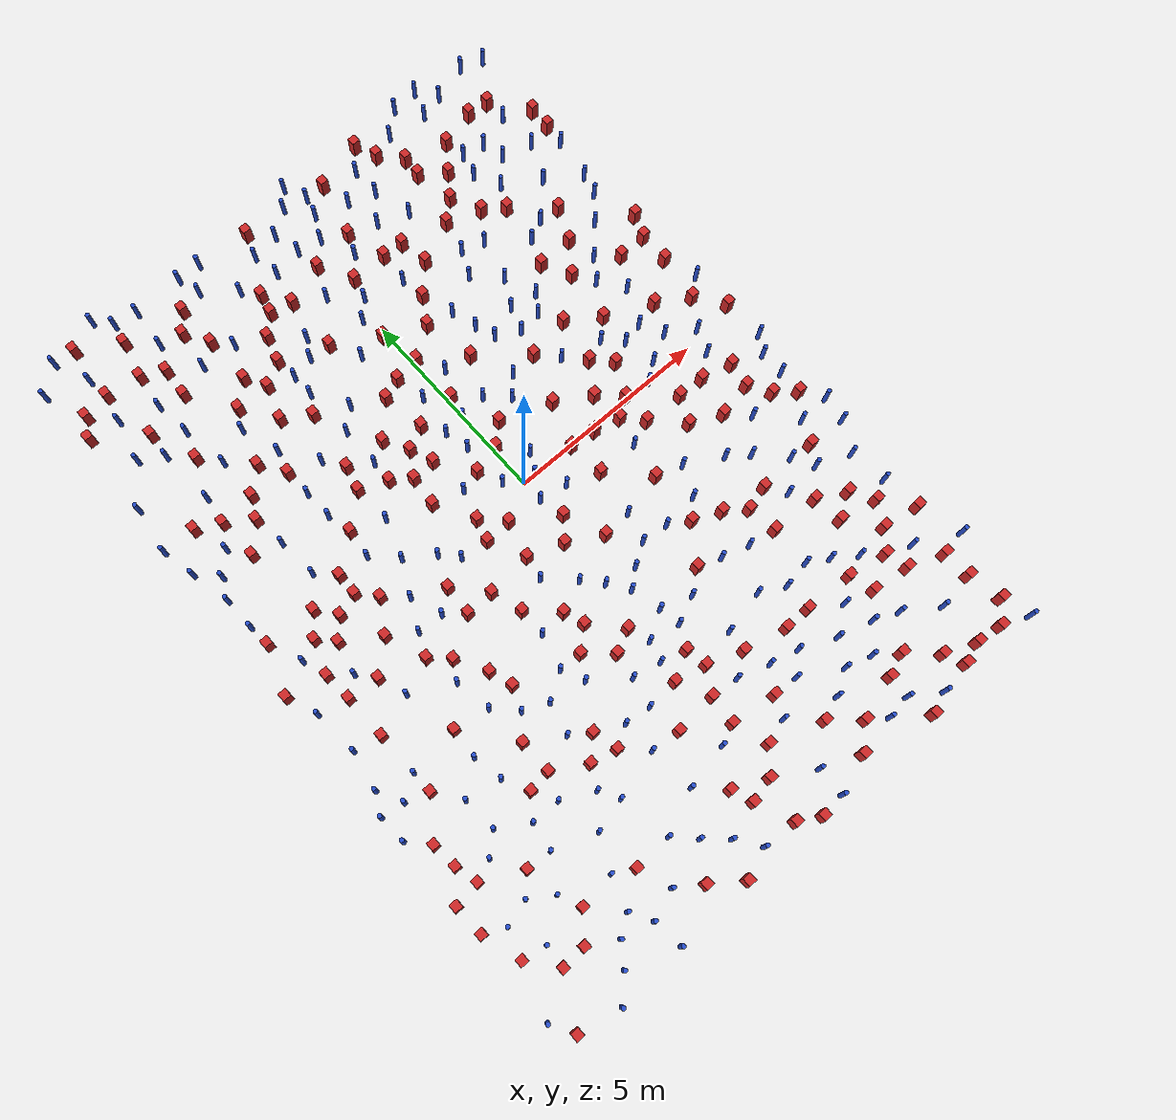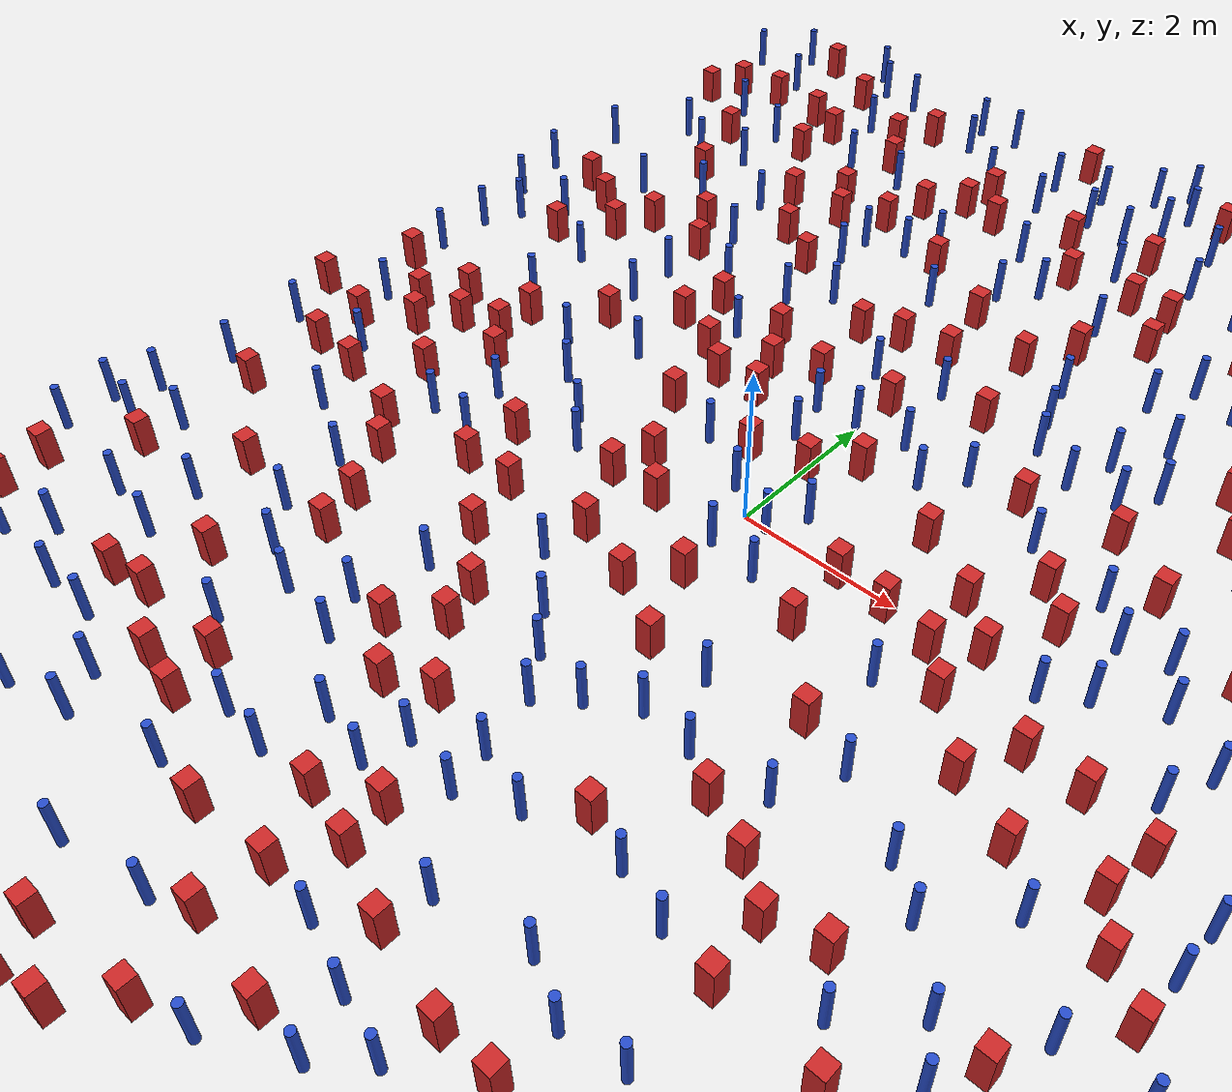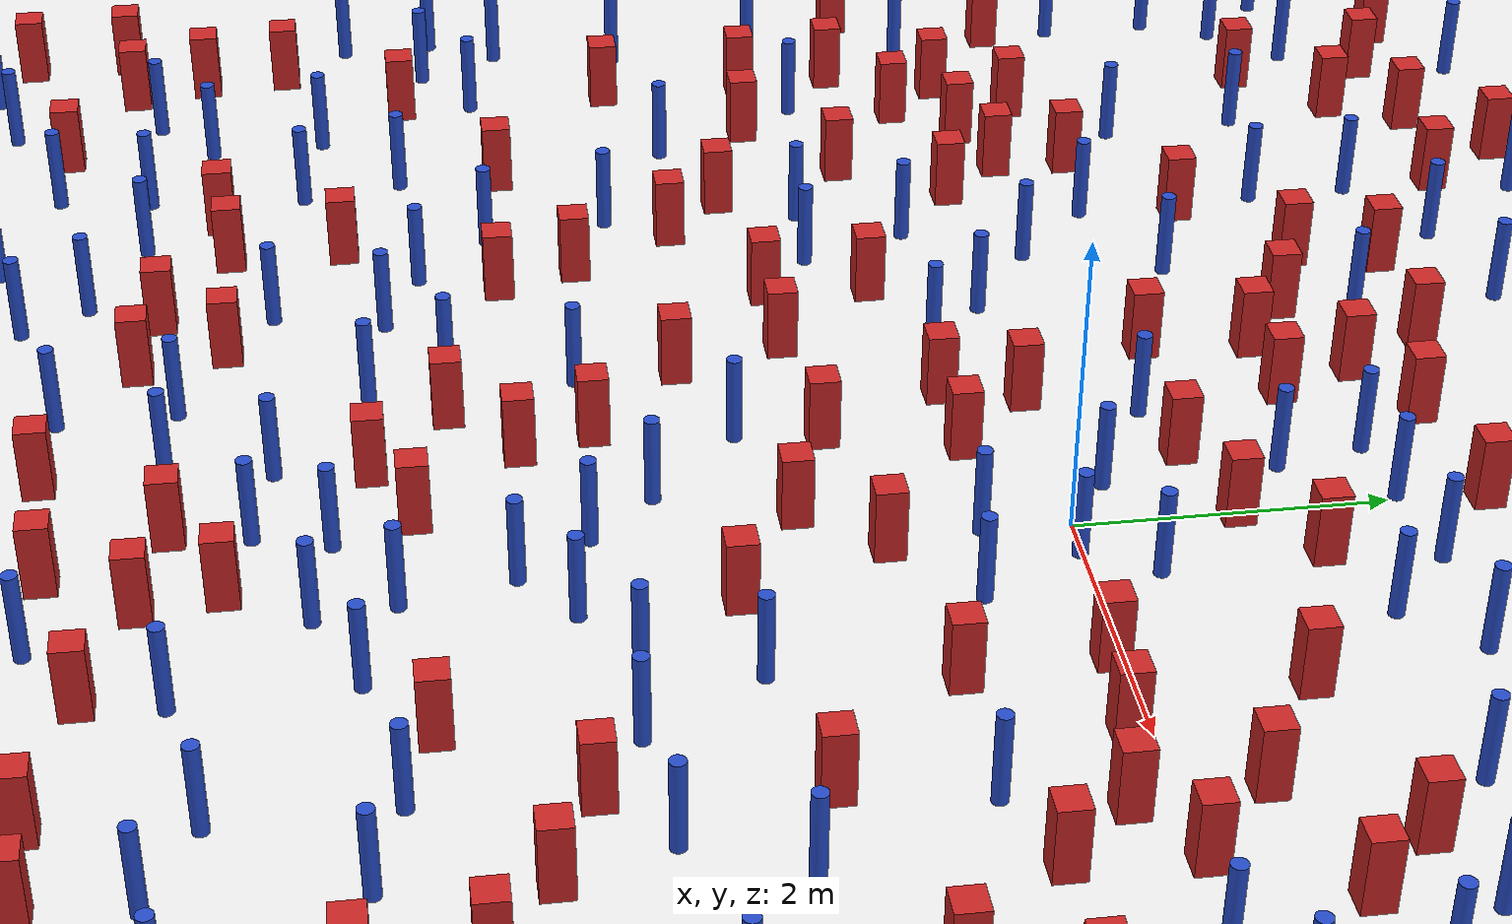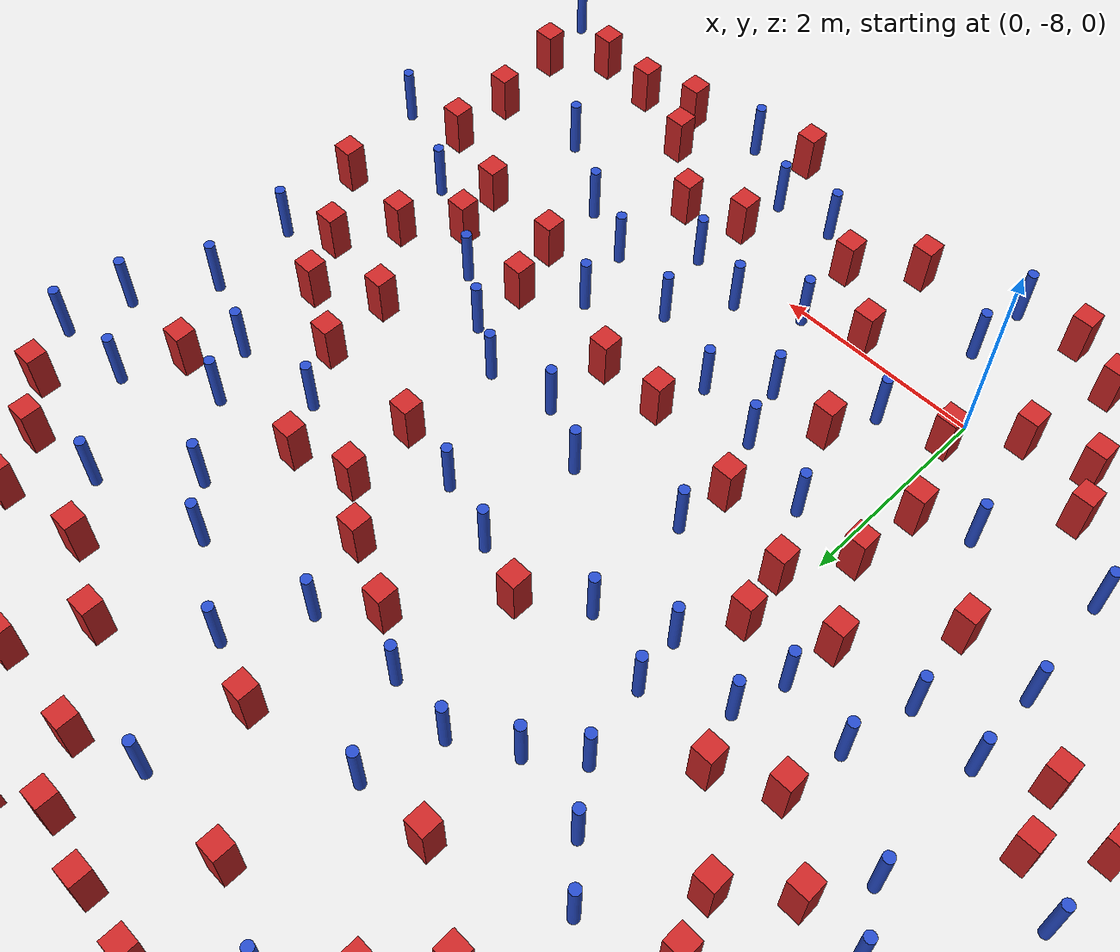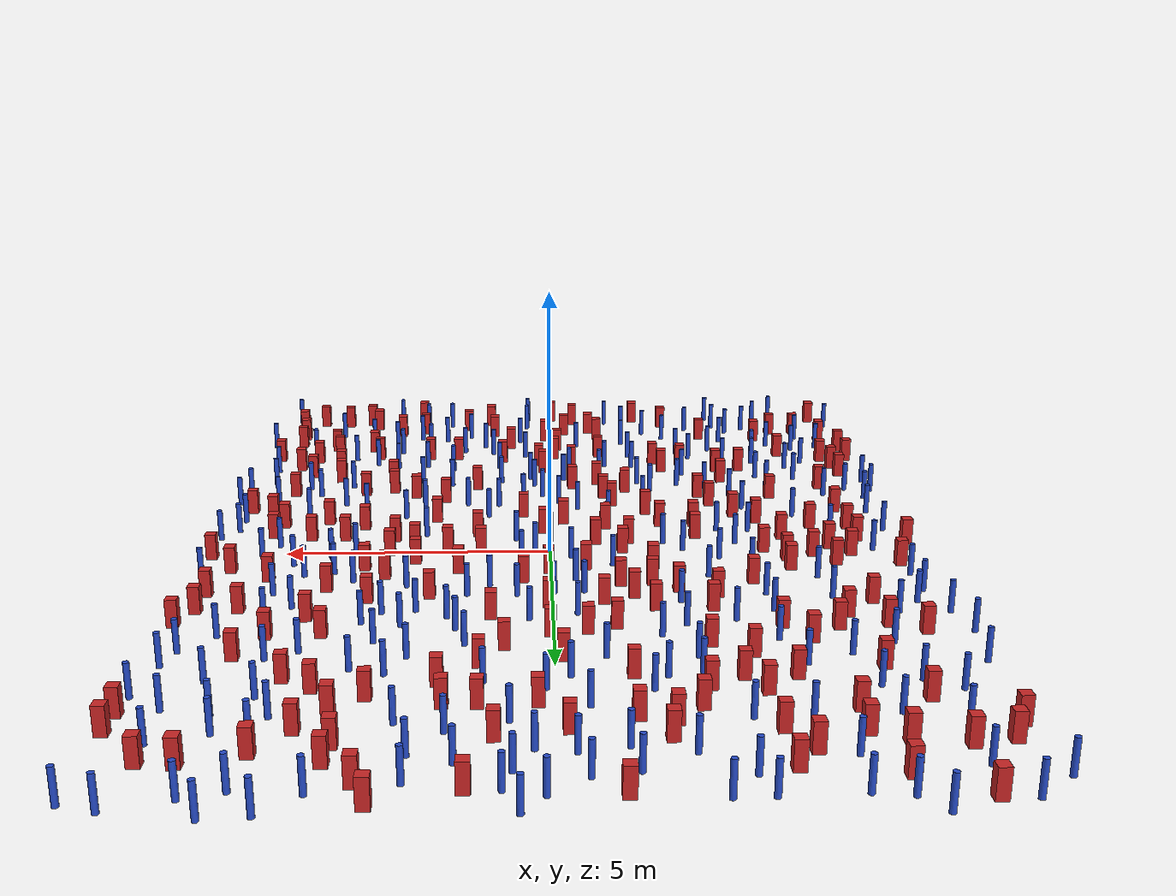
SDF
<sdf version="1.6">
  <model name="dense_1"><model name="square_post_obstacle0">
  <static>true</static>
  <pose frame="">-4.44707930667 6.60124097648 -4.36207812815e-07 3.75137919937e-06 9.77721102514e-07 2.47381364184e-05</pose>
  <link name="link">
    <pose frame="">0 0 0.25 0 -0 0</pose>
    <inertial>
      <mass>100</mass>
      <inertia>
        <ixx>0.166667</ixx>
        <ixy>0</ixy>
        <ixz>0</ixz>
        <iyy>0.166667</iyy>
        <iyz>0</iyz>
        <izz>0.166667</izz>
      </inertia>
    </inertial>
    <collision name="collision">
      <geometry>
        <box>
          <size>.2 .2 .5</size>
        </box>
      </geometry>
      <max_contacts>10</max_contacts>
      <surface>
        <contact>
          <ode/>
        </contact>
        <bounce/>
        <friction>
          <torsional>
            <ode/>
          </torsional>
          <ode/>
        </friction>
      </surface>
    </collision>
    <visual name="visual">
      <geometry>
        <box>
          <size>.2 .2 .5</size>
        </box>
      </geometry>
      <material>
        <script>
          <name>Gazebo/Red</name>
          <uri>file://media/materials/scripts/gazebo.material</uri>
        </script>
      </material>
    </visual>
    <self_collide>0</self_collide>
    <kinematic>0</kinematic>
  </link>
</model>
<model name="square_post_obstacle1">
  <static>true</static>
  <pose frame="">-6.51652858593 0.78683695775 -4.36207812815e-07 3.75137919937e-06 9.77721102514e-07 2.47381364184e-05</pose>
  <link name="link">
    <pose frame="">0 0 0.25 0 -0 0</pose>
    <inertial>
      <mass>100</mass>
      <inertia>
        <ixx>0.166667</ixx>
        <ixy>0</ixy>
        <ixz>0</ixz>
        <iyy>0.166667</iyy>
        <iyz>0</iyz>
        <izz>0.166667</izz>
      </inertia>
    </inertial>
    <collision name="collision">
      <geometry>
        <box>
          <size>.2 .2 .5</size>
        </box>
      </geometry>
      <max_contacts>10</max_contacts>
      <surface>
        <contact>
          <ode/>
        </contact>
        <bounce/>
        <friction>
          <torsional>
            <ode/>
          </torsional>
          <ode/>
        </friction>
      </surface>
    </collision>
    <visual name="visual">
      <geometry>
        <box>
          <size>.2 .2 .5</size>
        </box>
      </geometry>
      <material>
        <script>
          <name>Gazebo/Red</name>
          <uri>file://media/materials/scripts/gazebo.material</uri>
        </script>
      </material>
    </visual>
    <self_collide>0</self_collide>
    <kinematic>0</kinematic>
  </link>
</model>
<model name="pole_obstacle0">
  <static>true</static>
  <pose frame="">2.41326666451 -0.959669748231 -3.09024884793e-07 -7.19054271912e-07 -2.11315075118e-07 -1.93935509258e-07</pose>
  <link name="link">
  <pose frame="">0 0 0.3 0 -0 0</pose>
    <inertial>
      <mass>1</mass>
      <inertia>
        <ixx>0.145833</ixx>
        <ixy>0</ixy>
        <ixz>0</ixz>
        <iyy>0.145833</iyy>
        <iyz>0</iyz>
        <izz>0.125</izz>
      </inertia>
    </inertial>
    <collision name="collision">
      <geometry>
        <cylinder>
          <radius>0.05</radius>
          <length>.6</length>
        </cylinder>
      </geometry>
      <max_contacts>10</max_contacts>
      <surface>
        <contact>
          <ode/>
        </contact>
        <bounce/>
        <friction>
          <torsional>
            <ode/>
          </torsional>
          <ode/>
        </friction>
      </surface>
    </collision>
    <visual name="visual">
      <geometry>
        <cylinder>
          <radius>0.05</radius>
          <length>.6</length>
        </cylinder>
      </geometry>
      <material>
        <script>
          <name>Gazebo/Blue</name>
          <uri>file://media/materials/scripts/gazebo.material</uri>
        </script>
      </material>
    </visual>
    <self_collide>0</self_collide>
    <kinematic>0</kinematic>
  </link>
</model>
<model name="square_post_obstacle2">
  <static>true</static>
  <pose frame="">-2.88461139932 -1.47978508925 -4.36207812815e-07 3.75137919937e-06 9.77721102514e-07 2.47381364184e-05</pose>
  <link name="link">
    <pose frame="">0 0 0.25 0 -0 0</pose>
    <inertial>
      <mass>100</mass>
      <inertia>
        <ixx>0.166667</ixx>
        <ixy>0</ixy>
        <ixz>0</ixz>
        <iyy>0.166667</iyy>
        <iyz>0</iyz>
        <izz>0.166667</izz>
      </inertia>
    </inertial>
    <collision name="collision">
      <geometry>
        <box>
          <size>.2 .2 .5</size>
        </box>
      </geometry>
      <max_contacts>10</max_contacts>
      <surface>
        <contact>
          <ode/>
        </contact>
        <bounce/>
        <friction>
          <torsional>
            <ode/>
          </torsional>
          <ode/>
        </friction>
      </surface>
    </collision>
    <visual name="visual">
      <geometry>
        <box>
          <size>.2 .2 .5</size>
        </box>
      </geometry>
      <material>
        <script>
          <name>Gazebo/Red</name>
          <uri>file://media/materials/scripts/gazebo.material</uri>
        </script>
      </material>
    </visual>
    <self_collide>0</self_collide>
    <kinematic>0</kinematic>
  </link>
</model>
<model name="pole_obstacle1">
  <static>true</static>
  <pose frame="">5.38026649149 5.48574369236 -3.09024884793e-07 -7.19054271911e-07 -2.1131507516e-07 -1.93935509277e-07</pose>
  <link name="link">
  <pose frame="">0 0 0.3 0 -0 0</pose>
    <inertial>
      <mass>1</mass>
      <inertia>
        <ixx>0.145833</ixx>
        <ixy>0</ixy>
        <ixz>0</ixz>
        <iyy>0.145833</iyy>
        <iyz>0</iyz>
        <izz>0.125</izz>
      </inertia>
    </inertial>
    <collision name="collision">
      <geometry>
        <cylinder>
          <radius>0.05</radius>
          <length>.6</length>
        </cylinder>
      </geometry>
      <max_contacts>10</max_contacts>
      <surface>
        <contact>
          <ode/>
        </contact>
        <bounce/>
        <friction>
          <torsional>
            <ode/>
          </torsional>
          <ode/>
        </friction>
      </surface>
    </collision>
    <visual name="visual">
      <geometry>
        <cylinder>
          <radius>0.05</radius>
          <length>.6</length>
        </cylinder>
      </geometry>
      <material>
        <script>
          <name>Gazebo/Blue</name>
          <uri>file://media/materials/scripts/gazebo.material</uri>
        </script>
      </material>
    </visual>
    <self_collide>0</self_collide>
    <kinematic>0</kinematic>
  </link>
</model>
<model name="square_post_obstacle3">
  <static>true</static>
  <pose frame="">-6.44822498088 -5.28785836614 -4.36207812815e-07 3.75137919937e-06 9.77721102514e-07 2.47381364184e-05</pose>
  <link name="link">
    <pose frame="">0 0 0.25 0 -0 0</pose>
    <inertial>
      <mass>100</mass>
      <inertia>
        <ixx>0.166667</ixx>
        <ixy>0</ixy>
        <ixz>0</ixz>
        <iyy>0.166667</iyy>
        <iyz>0</iyz>
        <izz>0.166667</izz>
      </inertia>
    </inertial>
    <collision name="collision">
      <geometry>
        <box>
          <size>.2 .2 .5</size>
        </box>
      </geometry>
      <max_contacts>10</max_contacts>
      <surface>
        <contact>
          <ode/>
        </contact>
        <bounce/>
        <friction>
          <torsional>
            <ode/>
          </torsional>
          <ode/>
        </friction>
      </surface>
    </collision>
    <visual name="visual">
      <geometry>
        <box>
          <size>.2 .2 .5</size>
        </box>
      </geometry>
      <material>
        <script>
          <name>Gazebo/Red</name>
          <uri>file://media/materials/scripts/gazebo.material</uri>
        </script>
      </material>
    </visual>
    <self_collide>0</self_collide>
    <kinematic>0</kinematic>
  </link>
</model>
<model name="pole_obstacle2">
  <static>true</static>
  <pose frame="">-5.21666784153 -8.9613979253 -3.09024884793e-07 -7.19054271912e-07 -2.1131507513e-07 -1.93935509261e-07</pose>
  <link name="link">
  <pose frame="">0 0 0.3 0 -0 0</pose>
    <inertial>
      <mass>1</mass>
      <inertia>
        <ixx>0.145833</ixx>
        <ixy>0</ixy>
        <ixz>0</ixz>
        <iyy>0.145833</iyy>
        <iyz>0</iyz>
        <izz>0.125</izz>
      </inertia>
    </inertial>
    <collision name="collision">
      <geometry>
        <cylinder>
          <radius>0.05</radius>
          <length>.6</length>
        </cylinder>
      </geometry>
      <max_contacts>10</max_contacts>
      <surface>
        <contact>
          <ode/>
        </contact>
        <bounce/>
        <friction>
          <torsional>
            <ode/>
          </torsional>
          <ode/>
        </friction>
      </surface>
    </collision>
    <visual name="visual">
      <geometry>
        <cylinder>
          <radius>0.05</radius>
          <length>.6</length>
        </cylinder>
      </geometry>
      <material>
        <script>
          <name>Gazebo/Blue</name>
          <uri>file://media/materials/scripts/gazebo.material</uri>
        </script>
      </material>
    </visual>
    <self_collide>0</self_collide>
    <kinematic>0</kinematic>
  </link>
</model>
<model name="pole_obstacle3">
  <static>true</static>
  <pose frame="">1.4623566968 4.20926063526 -3.09024884793e-07 -7.19054271912e-07 -2.11315075134e-07 -1.93935509265e-07</pose>
  <link name="link">
  <pose frame="">0 0 0.3 0 -0 0</pose>
    <inertial>
      <mass>1</mass>
      <inertia>
        <ixx>0.145833</ixx>
        <ixy>0</ixy>
        <ixz>0</ixz>
        <iyy>0.145833</iyy>
        <iyz>0</iyz>
        <izz>0.125</izz>
      </inertia>
    </inertial>
    <collision name="collision">
      <geometry>
        <cylinder>
          <radius>0.05</radius>
          <length>.6</length>
        </cylinder>
      </geometry>
      <max_contacts>10</max_contacts>
      <surface>
        <contact>
          <ode/>
        </contact>
        <bounce/>
        <friction>
          <torsional>
            <ode/>
          </torsional>
          <ode/>
        </friction>
      </surface>
    </collision>
    <visual name="visual">
      <geometry>
        <cylinder>
          <radius>0.05</radius>
          <length>.6</length>
        </cylinder>
      </geometry>
      <material>
        <script>
          <name>Gazebo/Blue</name>
          <uri>file://media/materials/scripts/gazebo.material</uri>
        </script>
      </material>
    </visual>
    <self_collide>0</self_collide>
    <kinematic>0</kinematic>
  </link>
</model>
<model name="square_post_obstacle4">
  <static>true</static>
  <pose frame="">1.31986433456 -0.0795674390711 -4.36207812815e-07 3.75137919937e-06 9.77721102514e-07 2.47381364184e-05</pose>
  <link name="link">
    <pose frame="">0 0 0.25 0 -0 0</pose>
    <inertial>
      <mass>100</mass>
      <inertia>
        <ixx>0.166667</ixx>
        <ixy>0</ixy>
        <ixz>0</ixz>
        <iyy>0.166667</iyy>
        <iyz>0</iyz>
        <izz>0.166667</izz>
      </inertia>
    </inertial>
    <collision name="collision">
      <geometry>
        <box>
          <size>.2 .2 .5</size>
        </box>
      </geometry>
      <max_contacts>10</max_contacts>
      <surface>
        <contact>
          <ode/>
        </contact>
        <bounce/>
        <friction>
          <torsional>
            <ode/>
          </torsional>
          <ode/>
        </friction>
      </surface>
    </collision>
    <visual name="visual">
      <geometry>
        <box>
          <size>.2 .2 .5</size>
        </box>
      </geometry>
      <material>
        <script>
          <name>Gazebo/Red</name>
          <uri>file://media/materials/scripts/gazebo.material</uri>
        </script>
      </material>
    </visual>
    <self_collide>0</self_collide>
    <kinematic>0</kinematic>
  </link>
</model>
<model name="square_post_obstacle5">
  <static>true</static>
  <pose frame="">-2.57139538991 -5.11353573605 -4.36207812815e-07 3.75137919937e-06 9.77721102514e-07 2.47381364184e-05</pose>
  <link name="link">
    <pose frame="">0 0 0.25 0 -0 0</pose>
    <inertial>
      <mass>100</mass>
      <inertia>
        <ixx>0.166667</ixx>
        <ixy>0</ixy>
        <ixz>0</ixz>
        <iyy>0.166667</iyy>
        <iyz>0</iyz>
        <izz>0.166667</izz>
      </inertia>
    </inertial>
    <collision name="collision">
      <geometry>
        <box>
          <size>.2 .2 .5</size>
        </box>
      </geometry>
      <max_contacts>10</max_contacts>
      <surface>
        <contact>
          <ode/>
        </contact>
        <bounce/>
        <friction>
          <torsional>
            <ode/>
          </torsional>
          <ode/>
        </friction>
      </surface>
    </collision>
    <visual name="visual">
      <geometry>
        <box>
          <size>.2 .2 .5</size>
        </box>
      </geometry>
      <material>
        <script>
          <name>Gazebo/Red</name>
          <uri>file://media/materials/scripts/gazebo.material</uri>
        </script>
      </material>
    </visual>
    <self_collide>0</self_collide>
    <kinematic>0</kinematic>
  </link>
</model>
<model name="square_post_obstacle6">
  <static>true</static>
  <pose frame="">-2.84316023539 -0.767534176309 -4.36207812815e-07 3.75137919937e-06 9.77721102514e-07 2.47381364184e-05</pose>
  <link name="link">
    <pose frame="">0 0 0.25 0 -0 0</pose>
    <inertial>
      <mass>100</mass>
      <inertia>
        <ixx>0.166667</ixx>
        <ixy>0</ixy>
        <ixz>0</ixz>
        <iyy>0.166667</iyy>
        <iyz>0</iyz>
        <izz>0.166667</izz>
      </inertia>
    </inertial>
    <collision name="collision">
      <geometry>
        <box>
          <size>.2 .2 .5</size>
        </box>
      </geometry>
      <max_contacts>10</max_contacts>
      <surface>
        <contact>
          <ode/>
        </contact>
        <bounce/>
        <friction>
          <torsional>
            <ode/>
          </torsional>
          <ode/>
        </friction>
      </surface>
    </collision>
    <visual name="visual">
      <geometry>
        <box>
          <size>.2 .2 .5</size>
        </box>
      </geometry>
      <material>
        <script>
          <name>Gazebo/Red</name>
          <uri>file://media/materials/scripts/gazebo.material</uri>
        </script>
      </material>
    </visual>
    <self_collide>0</self_collide>
    <kinematic>0</kinematic>
  </link>
</model>
<model name="pole_obstacle4">
  <static>true</static>
  <pose frame="">-2.6535177861 8.46014323631 -3.09024884848e-07 -7.19054271902e-07 -2.11315075199e-07 -1.93935509286e-07</pose>
  <link name="link">
  <pose frame="">0 0 0.3 0 -0 0</pose>
    <inertial>
      <mass>1</mass>
      <inertia>
        <ixx>0.145833</ixx>
        <ixy>0</ixy>
        <ixz>0</ixz>
        <iyy>0.145833</iyy>
        <iyz>0</iyz>
        <izz>0.125</izz>
      </inertia>
    </inertial>
    <collision name="collision">
      <geometry>
        <cylinder>
          <radius>0.05</radius>
          <length>.6</length>
        </cylinder>
      </geometry>
      <max_contacts>10</max_contacts>
      <surface>
        <contact>
          <ode/>
        </contact>
        <bounce/>
        <friction>
          <torsional>
            <ode/>
          </torsional>
          <ode/>
        </friction>
      </surface>
    </collision>
    <visual name="visual">
      <geometry>
        <cylinder>
          <radius>0.05</radius>
          <length>.6</length>
        </cylinder>
      </geometry>
      <material>
        <script>
          <name>Gazebo/Blue</name>
          <uri>file://media/materials/scripts/gazebo.material</uri>
        </script>
      </material>
    </visual>
    <self_collide>0</self_collide>
    <kinematic>0</kinematic>
  </link>
</model>
<model name="pole_obstacle5">
  <static>true</static>
  <pose frame="">-1.49414931302 -9.09169557917 -3.09024884793e-07 -7.19054271912e-07 -2.1131507515e-07 -1.93935509273e-07</pose>
  <link name="link">
  <pose frame="">0 0 0.3 0 -0 0</pose>
    <inertial>
      <mass>1</mass>
      <inertia>
        <ixx>0.145833</ixx>
        <ixy>0</ixy>
        <ixz>0</ixz>
        <iyy>0.145833</iyy>
        <iyz>0</iyz>
        <izz>0.125</izz>
      </inertia>
    </inertial>
    <collision name="collision">
      <geometry>
        <cylinder>
          <radius>0.05</radius>
          <length>.6</length>
        </cylinder>
      </geometry>
      <max_contacts>10</max_contacts>
      <surface>
        <contact>
          <ode/>
        </contact>
        <bounce/>
        <friction>
          <torsional>
            <ode/>
          </torsional>
          <ode/>
        </friction>
      </surface>
    </collision>
    <visual name="visual">
      <geometry>
        <cylinder>
          <radius>0.05</radius>
          <length>.6</length>
        </cylinder>
      </geometry>
      <material>
        <script>
          <name>Gazebo/Blue</name>
          <uri>file://media/materials/scripts/gazebo.material</uri>
        </script>
      </material>
    </visual>
    <self_collide>0</self_collide>
    <kinematic>0</kinematic>
  </link>
</model>
<model name="square_post_obstacle7">
  <static>true</static>
  <pose frame="">5.20359295091 -5.96778097333 -4.36207812815e-07 3.75137919937e-06 9.77721102514e-07 2.47381364184e-05</pose>
  <link name="link">
    <pose frame="">0 0 0.25 0 -0 0</pose>
    <inertial>
      <mass>100</mass>
      <inertia>
        <ixx>0.166667</ixx>
        <ixy>0</ixy>
        <ixz>0</ixz>
        <iyy>0.166667</iyy>
        <iyz>0</iyz>
        <izz>0.166667</izz>
      </inertia>
    </inertial>
    <collision name="collision">
      <geometry>
        <box>
          <size>.2 .2 .5</size>
        </box>
      </geometry>
      <max_contacts>10</max_contacts>
      <surface>
        <contact>
          <ode/>
        </contact>
        <bounce/>
        <friction>
          <torsional>
            <ode/>
          </torsional>
          <ode/>
        </friction>
      </surface>
    </collision>
    <visual name="visual">
      <geometry>
        <box>
          <size>.2 .2 .5</size>
        </box>
      </geometry>
      <material>
        <script>
          <name>Gazebo/Red</name>
          <uri>file://media/materials/scripts/gazebo.material</uri>
        </script>
      </material>
    </visual>
    <self_collide>0</self_collide>
    <kinematic>0</kinematic>
  </link>
</model>
<model name="square_post_obstacle8">
  <static>true</static>
  <pose frame="">-4.70309070849 -3.17879150348 -4.36207812815e-07 3.75137919937e-06 9.77721102514e-07 2.47381364184e-05</pose>
  <link name="link">
    <pose frame="">0 0 0.25 0 -0 0</pose>
    <inertial>
      <mass>100</mass>
      <inertia>
        <ixx>0.166667</ixx>
        <ixy>0</ixy>
        <ixz>0</ixz>
        <iyy>0.166667</iyy>
        <iyz>0</iyz>
        <izz>0.166667</izz>
      </inertia>
    </inertial>
    <collision name="collision">
      <geometry>
        <box>
          <size>.2 .2 .5</size>
        </box>
      </geometry>
      <max_contacts>10</max_contacts>
      <surface>
        <contact>
          <ode/>
        </contact>
        <bounce/>
        <friction>
          <torsional>
            <ode/>
          </torsional>
          <ode/>
        </friction>
      </surface>
    </collision>
    <visual name="visual">
      <geometry>
        <box>
          <size>.2 .2 .5</size>
        </box>
      </geometry>
      <material>
        <script>
          <name>Gazebo/Red</name>
          <uri>file://media/materials/scripts/gazebo.material</uri>
        </script>
      </material>
    </visual>
    <self_collide>0</self_collide>
    <kinematic>0</kinematic>
  </link>
</model>
<model name="pole_obstacle6">
  <static>true</static>
  <pose frame="">2.60039260077 1.69104292245 -3.09024884793e-07 -7.19054271912e-07 -2.11315075122e-07 -1.93935509259e-07</pose>
  <link name="link">
  <pose frame="">0 0 0.3 0 -0 0</pose>
    <inertial>
      <mass>1</mass>
      <inertia>
        <ixx>0.145833</ixx>
        <ixy>0</ixy>
        <ixz>0</ixz>
        <iyy>0.145833</iyy>
        <iyz>0</iyz>
        <izz>0.125</izz>
      </inertia>
    </inertial>
    <collision name="collision">
      <geometry>
        <cylinder>
          <radius>0.05</radius>
          <length>.6</length>
        </cylinder>
      </geometry>
      <max_contacts>10</max_contacts>
      <surface>
        <contact>
          <ode/>
        </contact>
        <bounce/>
        <friction>
          <torsional>
            <ode/>
          </torsional>
          <ode/>
        </friction>
      </surface>
    </collision>
    <visual name="visual">
      <geometry>
        <cylinder>
          <radius>0.05</radius>
          <length>.6</length>
        </cylinder>
      </geometry>
      <material>
        <script>
          <name>Gazebo/Blue</name>
          <uri>file://media/materials/scripts/gazebo.material</uri>
        </script>
      </material>
    </visual>
    <self_collide>0</self_collide>
    <kinematic>0</kinematic>
  </link>
</model>
<model name="pole_obstacle7">
  <static>true</static>
  <pose frame="">-3.71285936024 0.927176487157 -3.09024884793e-07 -7.19054271912e-07 -2.11315075162e-07 -1.93935509281e-07</pose>
  <link name="link">
  <pose frame="">0 0 0.3 0 -0 0</pose>
    <inertial>
      <mass>1</mass>
      <inertia>
        <ixx>0.145833</ixx>
        <ixy>0</ixy>
        <ixz>0</ixz>
        <iyy>0.145833</iyy>
        <iyz>0</iyz>
        <izz>0.125</izz>
      </inertia>
    </inertial>
    <collision name="collision">
      <geometry>
        <cylinder>
          <radius>0.05</radius>
          <length>.6</length>
        </cylinder>
      </geometry>
      <max_contacts>10</max_contacts>
      <surface>
        <contact>
          <ode/>
        </contact>
        <bounce/>
        <friction>
          <torsional>
            <ode/>
          </torsional>
          <ode/>
        </friction>
      </surface>
    </collision>
    <visual name="visual">
      <geometry>
        <cylinder>
          <radius>0.05</radius>
          <length>.6</length>
        </cylinder>
      </geometry>
      <material>
        <script>
          <name>Gazebo/Blue</name>
          <uri>file://media/materials/scripts/gazebo.material</uri>
        </script>
      </material>
    </visual>
    <self_collide>0</self_collide>
    <kinematic>0</kinematic>
  </link>
</model>
<model name="square_post_obstacle9">
  <static>true</static>
  <pose frame="">-1.23599823708 1.6640314914 -4.36207812815e-07 3.75137919937e-06 9.77721102514e-07 2.47381364184e-05</pose>
  <link name="link">
    <pose frame="">0 0 0.25 0 -0 0</pose>
    <inertial>
      <mass>100</mass>
      <inertia>
        <ixx>0.166667</ixx>
        <ixy>0</ixy>
        <ixz>0</ixz>
        <iyy>0.166667</iyy>
        <iyz>0</iyz>
        <izz>0.166667</izz>
      </inertia>
    </inertial>
    <collision name="collision">
      <geometry>
        <box>
          <size>.2 .2 .5</size>
        </box>
      </geometry>
      <max_contacts>10</max_contacts>
      <surface>
        <contact>
          <ode/>
        </contact>
        <bounce/>
        <friction>
          <torsional>
            <ode/>
          </torsional>
          <ode/>
        </friction>
      </surface>
    </collision>
    <visual name="visual">
      <geometry>
        <box>
          <size>.2 .2 .5</size>
        </box>
      </geometry>
      <material>
        <script>
          <name>Gazebo/Red</name>
          <uri>file://media/materials/scripts/gazebo.material</uri>
        </script>
      </material>
    </visual>
    <self_collide>0</self_collide>
    <kinematic>0</kinematic>
  </link>
</model>
<model name="square_post_obstacle10">
  <static>true</static>
  <pose frame="">6.35777453444 3.31523075422 -4.36207812815e-07 3.75137919937e-06 9.77721102514e-07 2.47381364184e-05</pose>
  <link name="link">
    <pose frame="">0 0 0.25 0 -0 0</pose>
    <inertial>
      <mass>100</mass>
      <inertia>
        <ixx>0.166667</ixx>
        <ixy>0</ixy>
        <ixz>0</ixz>
        <iyy>0.166667</iyy>
        <iyz>0</iyz>
        <izz>0.166667</izz>
      </inertia>
    </inertial>
    <collision name="collision">
      <geometry>
        <box>
          <size>.2 .2 .5</size>
        </box>
      </geometry>
      <max_contacts>10</max_contacts>
      <surface>
        <contact>
          <ode/>
        </contact>
        <bounce/>
        <friction>
          <torsional>
            <ode/>
          </torsional>
          <ode/>
        </friction>
      </surface>
    </collision>
    <visual name="visual">
      <geometry>
        <box>
          <size>.2 .2 .5</size>
        </box>
      </geometry>
      <material>
        <script>
          <name>Gazebo/Red</name>
          <uri>file://media/materials/scripts/gazebo.material</uri>
        </script>
      </material>
    </visual>
    <self_collide>0</self_collide>
    <kinematic>0</kinematic>
  </link>
</model>
<model name="square_post_obstacle11">
  <static>true</static>
  <pose frame="">0.119357444727 -1.15972905448 -4.36207812815e-07 3.75137919937e-06 9.77721102514e-07 2.47381364184e-05</pose>
  <link name="link">
    <pose frame="">0 0 0.25 0 -0 0</pose>
    <inertial>
      <mass>100</mass>
      <inertia>
        <ixx>0.166667</ixx>
        <ixy>0</ixy>
        <ixz>0</ixz>
        <iyy>0.166667</iyy>
        <iyz>0</iyz>
        <izz>0.166667</izz>
      </inertia>
    </inertial>
    <collision name="collision">
      <geometry>
        <box>
          <size>.2 .2 .5</size>
        </box>
      </geometry>
      <max_contacts>10</max_contacts>
      <surface>
        <contact>
          <ode/>
        </contact>
        <bounce/>
        <friction>
          <torsional>
            <ode/>
          </torsional>
          <ode/>
        </friction>
      </surface>
    </collision>
    <visual name="visual">
      <geometry>
        <box>
          <size>.2 .2 .5</size>
        </box>
      </geometry>
      <material>
        <script>
          <name>Gazebo/Red</name>
          <uri>file://media/materials/scripts/gazebo.material</uri>
        </script>
      </material>
    </visual>
    <self_collide>0</self_collide>
    <kinematic>0</kinematic>
  </link>
</model>
<model name="square_post_obstacle12">
  <static>true</static>
  <pose frame="">-6.17374142803 3.86425965815 -4.36207812815e-07 3.75137919937e-06 9.77721102514e-07 2.47381364184e-05</pose>
  <link name="link">
    <pose frame="">0 0 0.25 0 -0 0</pose>
    <inertial>
      <mass>100</mass>
      <inertia>
        <ixx>0.166667</ixx>
        <ixy>0</ixy>
        <ixz>0</ixz>
        <iyy>0.166667</iyy>
        <iyz>0</iyz>
        <izz>0.166667</izz>
      </inertia>
    </inertial>
    <collision name="collision">
      <geometry>
        <box>
          <size>.2 .2 .5</size>
        </box>
      </geometry>
      <max_contacts>10</max_contacts>
      <surface>
        <contact>
          <ode/>
        </contact>
        <bounce/>
        <friction>
          <torsional>
            <ode/>
          </torsional>
          <ode/>
        </friction>
      </surface>
    </collision>
    <visual name="visual">
      <geometry>
        <box>
          <size>.2 .2 .5</size>
        </box>
      </geometry>
      <material>
        <script>
          <name>Gazebo/Red</name>
          <uri>file://media/materials/scripts/gazebo.material</uri>
        </script>
      </material>
    </visual>
    <self_collide>0</self_collide>
    <kinematic>0</kinematic>
  </link>
</model>
<model name="square_post_obstacle13">
  <static>true</static>
  <pose frame="">2.54253266543 9.15945608791 -4.36207812815e-07 3.75137919937e-06 9.77721102514e-07 2.47381364184e-05</pose>
  <link name="link">
    <pose frame="">0 0 0.25 0 -0 0</pose>
    <inertial>
      <mass>100</mass>
      <inertia>
        <ixx>0.166667</ixx>
        <ixy>0</ixy>
        <ixz>0</ixz>
        <iyy>0.166667</iyy>
        <iyz>0</iyz>
        <izz>0.166667</izz>
      </inertia>
    </inertial>
    <collision name="collision">
      <geometry>
        <box>
          <size>.2 .2 .5</size>
        </box>
      </geometry>
      <max_contacts>10</max_contacts>
      <surface>
        <contact>
          <ode/>
        </contact>
        <bounce/>
        <friction>
          <torsional>
            <ode/>
          </torsional>
          <ode/>
        </friction>
      </surface>
    </collision>
    <visual name="visual">
      <geometry>
        <box>
          <size>.2 .2 .5</size>
        </box>
      </geometry>
      <material>
        <script>
          <name>Gazebo/Red</name>
          <uri>file://media/materials/scripts/gazebo.material</uri>
        </script>
      </material>
    </visual>
    <self_collide>0</self_collide>
    <kinematic>0</kinematic>
  </link>
</model>
<model name="pole_obstacle8">
  <static>true</static>
  <pose frame="">2.66010328651 5.29040970579 -3.09024884793e-07 -7.19054271912e-07 -2.11315075134e-07 -1.93935509266e-07</pose>
  <link name="link">
  <pose frame="">0 0 0.3 0 -0 0</pose>
    <inertial>
      <mass>1</mass>
      <inertia>
        <ixx>0.145833</ixx>
        <ixy>0</ixy>
        <ixz>0</ixz>
        <iyy>0.145833</iyy>
        <iyz>0</iyz>
        <izz>0.125</izz>
      </inertia>
    </inertial>
    <collision name="collision">
      <geometry>
        <cylinder>
          <radius>0.05</radius>
          <length>.6</length>
        </cylinder>
      </geometry>
      <max_contacts>10</max_contacts>
      <surface>
        <contact>
          <ode/>
        </contact>
        <bounce/>
        <friction>
          <torsional>
            <ode/>
          </torsional>
          <ode/>
        </friction>
      </surface>
    </collision>
    <visual name="visual">
      <geometry>
        <cylinder>
          <radius>0.05</radius>
          <length>.6</length>
        </cylinder>
      </geometry>
      <material>
        <script>
          <name>Gazebo/Blue</name>
          <uri>file://media/materials/scripts/gazebo.material</uri>
        </script>
      </material>
    </visual>
    <self_collide>0</self_collide>
    <kinematic>0</kinematic>
  </link>
</model>
<model name="square_post_obstacle14">
  <static>true</static>
  <pose frame="">2.76166165576 8.59688035177 -4.36207812815e-07 3.75137919937e-06 9.77721102514e-07 2.47381364184e-05</pose>
  <link name="link">
    <pose frame="">0 0 0.25 0 -0 0</pose>
    <inertial>
      <mass>100</mass>
      <inertia>
        <ixx>0.166667</ixx>
        <ixy>0</ixy>
        <ixz>0</ixz>
        <iyy>0.166667</iyy>
        <iyz>0</iyz>
        <izz>0.166667</izz>
      </inertia>
    </inertial>
    <collision name="collision">
      <geometry>
        <box>
          <size>.2 .2 .5</size>
        </box>
      </geometry>
      <max_contacts>10</max_contacts>
      <surface>
        <contact>
          <ode/>
        </contact>
        <bounce/>
        <friction>
          <torsional>
            <ode/>
          </torsional>
          <ode/>
        </friction>
      </surface>
    </collision>
    <visual name="visual">
      <geometry>
        <box>
          <size>.2 .2 .5</size>
        </box>
      </geometry>
      <material>
        <script>
          <name>Gazebo/Red</name>
          <uri>file://media/materials/scripts/gazebo.material</uri>
        </script>
      </material>
    </visual>
    <self_collide>0</self_collide>
    <kinematic>0</kinematic>
  </link>
</model>
<model name="square_post_obstacle15">
  <static>true</static>
  <pose frame="">3.97810140342 -0.776497119024 -4.36207812815e-07 3.75137919937e-06 9.77721102514e-07 2.47381364184e-05</pose>
  <link name="link">
    <pose frame="">0 0 0.25 0 -0 0</pose>
    <inertial>
      <mass>100</mass>
      <inertia>
        <ixx>0.166667</ixx>
        <ixy>0</ixy>
        <ixz>0</ixz>
        <iyy>0.166667</iyy>
        <iyz>0</iyz>
        <izz>0.166667</izz>
      </inertia>
    </inertial>
    <collision name="collision">
      <geometry>
        <box>
          <size>.2 .2 .5</size>
        </box>
      </geometry>
      <max_contacts>10</max_contacts>
      <surface>
        <contact>
          <ode/>
        </contact>
        <bounce/>
        <friction>
          <torsional>
            <ode/>
          </torsional>
          <ode/>
        </friction>
      </surface>
    </collision>
    <visual name="visual">
      <geometry>
        <box>
          <size>.2 .2 .5</size>
        </box>
      </geometry>
      <material>
        <script>
          <name>Gazebo/Red</name>
          <uri>file://media/materials/scripts/gazebo.material</uri>
        </script>
      </material>
    </visual>
    <self_collide>0</self_collide>
    <kinematic>0</kinematic>
  </link>
</model>
<model name="square_post_obstacle16">
  <static>true</static>
  <pose frame="">-1.88368987342 0.911929854532 -4.36207812815e-07 3.75137919937e-06 9.77721102514e-07 2.47381364184e-05</pose>
  <link name="link">
    <pose frame="">0 0 0.25 0 -0 0</pose>
    <inertial>
      <mass>100</mass>
      <inertia>
        <ixx>0.166667</ixx>
        <ixy>0</ixy>
        <ixz>0</ixz>
        <iyy>0.166667</iyy>
        <iyz>0</iyz>
        <izz>0.166667</izz>
      </inertia>
    </inertial>
    <collision name="collision">
      <geometry>
        <box>
          <size>.2 .2 .5</size>
        </box>
      </geometry>
      <max_contacts>10</max_contacts>
      <surface>
        <contact>
          <ode/>
        </contact>
        <bounce/>
        <friction>
          <torsional>
            <ode/>
          </torsional>
          <ode/>
        </friction>
      </surface>
    </collision>
    <visual name="visual">
      <geometry>
        <box>
          <size>.2 .2 .5</size>
        </box>
      </geometry>
      <material>
        <script>
          <name>Gazebo/Red</name>
          <uri>file://media/materials/scripts/gazebo.material</uri>
        </script>
      </material>
    </visual>
    <self_collide>0</self_collide>
    <kinematic>0</kinematic>
  </link>
</model>
<model name="pole_obstacle9">
  <static>true</static>
  <pose frame="">2.89782994441 -2.0281531749 -3.09024884793e-07 -7.19054271912e-07 -2.11315075127e-07 -1.93935509262e-07</pose>
  <link name="link">
  <pose frame="">0 0 0.3 0 -0 0</pose>
    <inertial>
      <mass>1</mass>
      <inertia>
        <ixx>0.145833</ixx>
        <ixy>0</ixy>
        <ixz>0</ixz>
        <iyy>0.145833</iyy>
        <iyz>0</iyz>
        <izz>0.125</izz>
      </inertia>
    </inertial>
    <collision name="collision">
      <geometry>
        <cylinder>
          <radius>0.05</radius>
          <length>.6</length>
        </cylinder>
      </geometry>
      <max_contacts>10</max_contacts>
      <surface>
        <contact>
          <ode/>
        </contact>
        <bounce/>
        <friction>
          <torsional>
            <ode/>
          </torsional>
          <ode/>
        </friction>
      </surface>
    </collision>
    <visual name="visual">
      <geometry>
        <cylinder>
          <radius>0.05</radius>
          <length>.6</length>
        </cylinder>
      </geometry>
      <material>
        <script>
          <name>Gazebo/Blue</name>
          <uri>file://media/materials/scripts/gazebo.material</uri>
        </script>
      </material>
    </visual>
    <self_collide>0</self_collide>
    <kinematic>0</kinematic>
  </link>
</model>
<model name="square_post_obstacle17">
  <static>true</static>
  <pose frame="">3.66579948599 -1.40427711125 -4.36207812815e-07 3.75137919937e-06 9.77721102514e-07 2.47381364184e-05</pose>
  <link name="link">
    <pose frame="">0 0 0.25 0 -0 0</pose>
    <inertial>
      <mass>100</mass>
      <inertia>
        <ixx>0.166667</ixx>
        <ixy>0</ixy>
        <ixz>0</ixz>
        <iyy>0.166667</iyy>
        <iyz>0</iyz>
        <izz>0.166667</izz>
      </inertia>
    </inertial>
    <collision name="collision">
      <geometry>
        <box>
          <size>.2 .2 .5</size>
        </box>
      </geometry>
      <max_contacts>10</max_contacts>
      <surface>
        <contact>
          <ode/>
        </contact>
        <bounce/>
        <friction>
          <torsional>
            <ode/>
          </torsional>
          <ode/>
        </friction>
      </surface>
    </collision>
    <visual name="visual">
      <geometry>
        <box>
          <size>.2 .2 .5</size>
        </box>
      </geometry>
      <material>
        <script>
          <name>Gazebo/Red</name>
          <uri>file://media/materials/scripts/gazebo.material</uri>
        </script>
      </material>
    </visual>
    <self_collide>0</self_collide>
    <kinematic>0</kinematic>
  </link>
</model>
<model name="square_post_obstacle18">
  <static>true</static>
  <pose frame="">2.58968893634 -0.286422892999 -4.36207812815e-07 3.75137919937e-06 9.77721102514e-07 2.47381364184e-05</pose>
  <link name="link">
    <pose frame="">0 0 0.25 0 -0 0</pose>
    <inertial>
      <mass>100</mass>
      <inertia>
        <ixx>0.166667</ixx>
        <ixy>0</ixy>
        <ixz>0</ixz>
        <iyy>0.166667</iyy>
        <iyz>0</iyz>
        <izz>0.166667</izz>
      </inertia>
    </inertial>
    <collision name="collision">
      <geometry>
        <box>
          <size>.2 .2 .5</size>
        </box>
      </geometry>
      <max_contacts>10</max_contacts>
      <surface>
        <contact>
          <ode/>
        </contact>
        <bounce/>
        <friction>
          <torsional>
            <ode/>
          </torsional>
          <ode/>
        </friction>
      </surface>
    </collision>
    <visual name="visual">
      <geometry>
        <box>
          <size>.2 .2 .5</size>
        </box>
      </geometry>
      <material>
        <script>
          <name>Gazebo/Red</name>
          <uri>file://media/materials/scripts/gazebo.material</uri>
        </script>
      </material>
    </visual>
    <self_collide>0</self_collide>
    <kinematic>0</kinematic>
  </link>
</model>
<model name="pole_obstacle10">
  <static>true</static>
  <pose frame="">2.30417689854 -8.93807566385 -3.09024884848e-07 -7.19054271902e-07 -2.11315075199e-07 -1.93935509286e-07</pose>
  <link name="link">
  <pose frame="">0 0 0.3 0 -0 0</pose>
    <inertial>
      <mass>1</mass>
      <inertia>
        <ixx>0.145833</ixx>
        <ixy>0</ixy>
        <ixz>0</ixz>
        <iyy>0.145833</iyy>
        <iyz>0</iyz>
        <izz>0.125</izz>
      </inertia>
    </inertial>
    <collision name="collision">
      <geometry>
        <cylinder>
          <radius>0.05</radius>
          <length>.6</length>
        </cylinder>
      </geometry>
      <max_contacts>10</max_contacts>
      <surface>
        <contact>
          <ode/>
        </contact>
        <bounce/>
        <friction>
          <torsional>
            <ode/>
          </torsional>
          <ode/>
        </friction>
      </surface>
    </collision>
    <visual name="visual">
      <geometry>
        <cylinder>
          <radius>0.05</radius>
          <length>.6</length>
        </cylinder>
      </geometry>
      <material>
        <script>
          <name>Gazebo/Blue</name>
          <uri>file://media/materials/scripts/gazebo.material</uri>
        </script>
      </material>
    </visual>
    <self_collide>0</self_collide>
    <kinematic>0</kinematic>
  </link>
</model>
<model name="square_post_obstacle19">
  <static>true</static>
  <pose frame="">3.23109717422 2.34629957783 -4.36207812815e-07 3.75137919937e-06 9.77721102514e-07 2.47381364184e-05</pose>
  <link name="link">
    <pose frame="">0 0 0.25 0 -0 0</pose>
    <inertial>
      <mass>100</mass>
      <inertia>
        <ixx>0.166667</ixx>
        <ixy>0</ixy>
        <ixz>0</ixz>
        <iyy>0.166667</iyy>
        <iyz>0</iyz>
        <izz>0.166667</izz>
      </inertia>
    </inertial>
    <collision name="collision">
      <geometry>
        <box>
          <size>.2 .2 .5</size>
        </box>
      </geometry>
      <max_contacts>10</max_contacts>
      <surface>
        <contact>
          <ode/>
        </contact>
        <bounce/>
        <friction>
          <torsional>
            <ode/>
          </torsional>
          <ode/>
        </friction>
      </surface>
    </collision>
    <visual name="visual">
      <geometry>
        <box>
          <size>.2 .2 .5</size>
        </box>
      </geometry>
      <material>
        <script>
          <name>Gazebo/Red</name>
          <uri>file://media/materials/scripts/gazebo.material</uri>
        </script>
      </material>
    </visual>
    <self_collide>0</self_collide>
    <kinematic>0</kinematic>
  </link>
</model>
<model name="pole_obstacle11">
  <static>true</static>
  <pose frame="">0.478394050941 -6.26336523896 -3.09024884793e-07 -7.19054271912e-07 -2.11315075128e-07 -1.9393550926e-07</pose>
  <link name="link">
  <pose frame="">0 0 0.3 0 -0 0</pose>
    <inertial>
      <mass>1</mass>
      <inertia>
        <ixx>0.145833</ixx>
        <ixy>0</ixy>
        <ixz>0</ixz>
        <iyy>0.145833</iyy>
        <iyz>0</iyz>
        <izz>0.125</izz>
      </inertia>
    </inertial>
    <collision name="collision">
      <geometry>
        <cylinder>
          <radius>0.05</radius>
          <length>.6</length>
        </cylinder>
      </geometry>
      <max_contacts>10</max_contacts>
      <surface>
        <contact>
          <ode/>
        </contact>
        <bounce/>
        <friction>
          <torsional>
            <ode/>
          </torsional>
          <ode/>
        </friction>
      </surface>
    </collision>
    <visual name="visual">
      <geometry>
        <cylinder>
          <radius>0.05</radius>
          <length>.6</length>
        </cylinder>
      </geometry>
      <material>
        <script>
          <name>Gazebo/Blue</name>
          <uri>file://media/materials/scripts/gazebo.material</uri>
        </script>
      </material>
    </visual>
    <self_collide>0</self_collide>
    <kinematic>0</kinematic>
  </link>
</model>
<model name="square_post_obstacle20">
  <static>true</static>
  <pose frame="">4.63659688607 -0.795210823432 -4.36207812815e-07 3.75137919937e-06 9.77721102514e-07 2.47381364184e-05</pose>
  <link name="link">
    <pose frame="">0 0 0.25 0 -0 0</pose>
    <inertial>
      <mass>100</mass>
      <inertia>
        <ixx>0.166667</ixx>
        <ixy>0</ixy>
        <ixz>0</ixz>
        <iyy>0.166667</iyy>
        <iyz>0</iyz>
        <izz>0.166667</izz>
      </inertia>
    </inertial>
    <collision name="collision">
      <geometry>
        <box>
          <size>.2 .2 .5</size>
        </box>
      </geometry>
      <max_contacts>10</max_contacts>
      <surface>
        <contact>
          <ode/>
        </contact>
        <bounce/>
        <friction>
          <torsional>
            <ode/>
          </torsional>
          <ode/>
        </friction>
      </surface>
    </collision>
    <visual name="visual">
      <geometry>
        <box>
          <size>.2 .2 .5</size>
        </box>
      </geometry>
      <material>
        <script>
          <name>Gazebo/Red</name>
          <uri>file://media/materials/scripts/gazebo.material</uri>
        </script>
      </material>
    </visual>
    <self_collide>0</self_collide>
    <kinematic>0</kinematic>
  </link>
</model>
<model name="pole_obstacle12">
  <static>true</static>
  <pose frame="">-5.93365733735 7.03019296914 -3.09024884793e-07 -7.19054271911e-07 -2.1131507516e-07 -1.93935509277e-07</pose>
  <link name="link">
  <pose frame="">0 0 0.3 0 -0 0</pose>
    <inertial>
      <mass>1</mass>
      <inertia>
        <ixx>0.145833</ixx>
        <ixy>0</ixy>
        <ixz>0</ixz>
        <iyy>0.145833</iyy>
        <iyz>0</iyz>
        <izz>0.125</izz>
      </inertia>
    </inertial>
    <collision name="collision">
      <geometry>
        <cylinder>
          <radius>0.05</radius>
          <length>.6</length>
        </cylinder>
      </geometry>
      <max_contacts>10</max_contacts>
      <surface>
        <contact>
          <ode/>
        </contact>
        <bounce/>
        <friction>
          <torsional>
            <ode/>
          </torsional>
          <ode/>
        </friction>
      </surface>
    </collision>
    <visual name="visual">
      <geometry>
        <cylinder>
          <radius>0.05</radius>
          <length>.6</length>
        </cylinder>
      </geometry>
      <material>
        <script>
          <name>Gazebo/Blue</name>
          <uri>file://media/materials/scripts/gazebo.material</uri>
        </script>
      </material>
    </visual>
    <self_collide>0</self_collide>
    <kinematic>0</kinematic>
  </link>
</model>
<model name="square_post_obstacle21">
  <static>true</static>
  <pose frame="">-3.63298602497 1.60475651946 -4.36207812815e-07 3.75137919937e-06 9.77721102514e-07 2.47381364184e-05</pose>
  <link name="link">
    <pose frame="">0 0 0.25 0 -0 0</pose>
    <inertial>
      <mass>100</mass>
      <inertia>
        <ixx>0.166667</ixx>
        <ixy>0</ixy>
        <ixz>0</ixz>
        <iyy>0.166667</iyy>
        <iyz>0</iyz>
        <izz>0.166667</izz>
      </inertia>
    </inertial>
    <collision name="collision">
      <geometry>
        <box>
          <size>.2 .2 .5</size>
        </box>
      </geometry>
      <max_contacts>10</max_contacts>
      <surface>
        <contact>
          <ode/>
        </contact>
        <bounce/>
        <friction>
          <torsional>
            <ode/>
          </torsional>
          <ode/>
        </friction>
      </surface>
    </collision>
    <visual name="visual">
      <geometry>
        <box>
          <size>.2 .2 .5</size>
        </box>
      </geometry>
      <material>
        <script>
          <name>Gazebo/Red</name>
          <uri>file://media/materials/scripts/gazebo.material</uri>
        </script>
      </material>
    </visual>
    <self_collide>0</self_collide>
    <kinematic>0</kinematic>
  </link>
</model>
<model name="pole_obstacle13">
  <static>true</static>
  <pose frame="">3.82998735341 -5.70305099585 -3.09024884793e-07 -7.19054271912e-07 -2.11315075134e-07 -1.93935509266e-07</pose>
  <link name="link">
  <pose frame="">0 0 0.3 0 -0 0</pose>
    <inertial>
      <mass>1</mass>
      <inertia>
        <ixx>0.145833</ixx>
        <ixy>0</ixy>
        <ixz>0</ixz>
        <iyy>0.145833</iyy>
        <iyz>0</iyz>
        <izz>0.125</izz>
      </inertia>
    </inertial>
    <collision name="collision">
      <geometry>
        <cylinder>
          <radius>0.05</radius>
          <length>.6</length>
        </cylinder>
      </geometry>
      <max_contacts>10</max_contacts>
      <surface>
        <contact>
          <ode/>
        </contact>
        <bounce/>
        <friction>
          <torsional>
            <ode/>
          </torsional>
          <ode/>
        </friction>
      </surface>
    </collision>
    <visual name="visual">
      <geometry>
        <cylinder>
          <radius>0.05</radius>
          <length>.6</length>
        </cylinder>
      </geometry>
      <material>
        <script>
          <name>Gazebo/Blue</name>
          <uri>file://media/materials/scripts/gazebo.material</uri>
        </script>
      </material>
    </visual>
    <self_collide>0</self_collide>
    <kinematic>0</kinematic>
  </link>
</model>
<model name="square_post_obstacle22">
  <static>true</static>
  <pose frame="">-2.14941318314 6.49315178788 -4.36207812815e-07 3.75137919937e-06 9.77721102514e-07 2.47381364184e-05</pose>
  <link name="link">
    <pose frame="">0 0 0.25 0 -0 0</pose>
    <inertial>
      <mass>100</mass>
      <inertia>
        <ixx>0.166667</ixx>
        <ixy>0</ixy>
        <ixz>0</ixz>
        <iyy>0.166667</iyy>
        <iyz>0</iyz>
        <izz>0.166667</izz>
      </inertia>
    </inertial>
    <collision name="collision">
      <geometry>
        <box>
          <size>.2 .2 .5</size>
        </box>
      </geometry>
      <max_contacts>10</max_contacts>
      <surface>
        <contact>
          <ode/>
        </contact>
        <bounce/>
        <friction>
          <torsional>
            <ode/>
          </torsional>
          <ode/>
        </friction>
      </surface>
    </collision>
    <visual name="visual">
      <geometry>
        <box>
          <size>.2 .2 .5</size>
        </box>
      </geometry>
      <material>
        <script>
          <name>Gazebo/Red</name>
          <uri>file://media/materials/scripts/gazebo.material</uri>
        </script>
      </material>
    </visual>
    <self_collide>0</self_collide>
    <kinematic>0</kinematic>
  </link>
</model>
<model name="pole_obstacle14">
  <static>true</static>
  <pose frame="">-0.220990663885 -2.92451951787 -3.09024884848e-07 -7.19054271902e-07 -2.11315075205e-07 -1.93935509288e-07</pose>
  <link name="link">
  <pose frame="">0 0 0.3 0 -0 0</pose>
    <inertial>
      <mass>1</mass>
      <inertia>
        <ixx>0.145833</ixx>
        <ixy>0</ixy>
        <ixz>0</ixz>
        <iyy>0.145833</iyy>
        <iyz>0</iyz>
        <izz>0.125</izz>
      </inertia>
    </inertial>
    <collision name="collision">
      <geometry>
        <cylinder>
          <radius>0.05</radius>
          <length>.6</length>
        </cylinder>
      </geometry>
      <max_contacts>10</max_contacts>
      <surface>
        <contact>
          <ode/>
        </contact>
        <bounce/>
        <friction>
          <torsional>
            <ode/>
          </torsional>
          <ode/>
        </friction>
      </surface>
    </collision>
    <visual name="visual">
      <geometry>
        <cylinder>
          <radius>0.05</radius>
          <length>.6</length>
        </cylinder>
      </geometry>
      <material>
        <script>
          <name>Gazebo/Blue</name>
          <uri>file://media/materials/scripts/gazebo.material</uri>
        </script>
      </material>
    </visual>
    <self_collide>0</self_collide>
    <kinematic>0</kinematic>
  </link>
</model>
<model name="pole_obstacle15">
  <static>true</static>
  <pose frame="">-4.91971607165 2.37123961968 -3.09024884793e-07 -7.19054271912e-07 -2.11315075144e-07 -1.93935509269e-07</pose>
  <link name="link">
  <pose frame="">0 0 0.3 0 -0 0</pose>
    <inertial>
      <mass>1</mass>
      <inertia>
        <ixx>0.145833</ixx>
        <ixy>0</ixy>
        <ixz>0</ixz>
        <iyy>0.145833</iyy>
        <iyz>0</iyz>
        <izz>0.125</izz>
      </inertia>
    </inertial>
    <collision name="collision">
      <geometry>
        <cylinder>
          <radius>0.05</radius>
          <length>.6</length>
        </cylinder>
      </geometry>
      <max_contacts>10</max_contacts>
      <surface>
        <contact>
          <ode/>
        </contact>
        <bounce/>
        <friction>
          <torsional>
            <ode/>
          </torsional>
          <ode/>
        </friction>
      </surface>
    </collision>
    <visual name="visual">
      <geometry>
        <cylinder>
          <radius>0.05</radius>
          <length>.6</length>
        </cylinder>
      </geometry>
      <material>
        <script>
          <name>Gazebo/Blue</name>
          <uri>file://media/materials/scripts/gazebo.material</uri>
        </script>
      </material>
    </visual>
    <self_collide>0</self_collide>
    <kinematic>0</kinematic>
  </link>
</model>
<model name="pole_obstacle16">
  <static>true</static>
  <pose frame="">-6.55094301523 -2.15541498875 -3.09024884793e-07 -7.19054271912e-07 -2.11315075144e-07 -1.93935509269e-07</pose>
  <link name="link">
  <pose frame="">0 0 0.3 0 -0 0</pose>
    <inertial>
      <mass>1</mass>
      <inertia>
        <ixx>0.145833</ixx>
        <ixy>0</ixy>
        <ixz>0</ixz>
        <iyy>0.145833</iyy>
        <iyz>0</iyz>
        <izz>0.125</izz>
      </inertia>
    </inertial>
    <collision name="collision">
      <geometry>
        <cylinder>
          <radius>0.05</radius>
          <length>.6</length>
        </cylinder>
      </geometry>
      <max_contacts>10</max_contacts>
      <surface>
        <contact>
          <ode/>
        </contact>
        <bounce/>
        <friction>
          <torsional>
            <ode/>
          </torsional>
          <ode/>
        </friction>
      </surface>
    </collision>
    <visual name="visual">
      <geometry>
        <cylinder>
          <radius>0.05</radius>
          <length>.6</length>
        </cylinder>
      </geometry>
      <material>
        <script>
          <name>Gazebo/Blue</name>
          <uri>file://media/materials/scripts/gazebo.material</uri>
        </script>
      </material>
    </visual>
    <self_collide>0</self_collide>
    <kinematic>0</kinematic>
  </link>
</model>
<model name="square_post_obstacle23">
  <static>true</static>
  <pose frame="">5.78915703853 -7.91855140705 -4.36207812815e-07 3.75137919937e-06 9.77721102514e-07 2.47381364184e-05</pose>
  <link name="link">
    <pose frame="">0 0 0.25 0 -0 0</pose>
    <inertial>
      <mass>100</mass>
      <inertia>
        <ixx>0.166667</ixx>
        <ixy>0</ixy>
        <ixz>0</ixz>
        <iyy>0.166667</iyy>
        <iyz>0</iyz>
        <izz>0.166667</izz>
      </inertia>
    </inertial>
    <collision name="collision">
      <geometry>
        <box>
          <size>.2 .2 .5</size>
        </box>
      </geometry>
      <max_contacts>10</max_contacts>
      <surface>
        <contact>
          <ode/>
        </contact>
        <bounce/>
        <friction>
          <torsional>
            <ode/>
          </torsional>
          <ode/>
        </friction>
      </surface>
    </collision>
    <visual name="visual">
      <geometry>
        <box>
          <size>.2 .2 .5</size>
        </box>
      </geometry>
      <material>
        <script>
          <name>Gazebo/Red</name>
          <uri>file://media/materials/scripts/gazebo.material</uri>
        </script>
      </material>
    </visual>
    <self_collide>0</self_collide>
    <kinematic>0</kinematic>
  </link>
</model>
<model name="pole_obstacle17">
  <static>true</static>
  <pose frame="">2.69220364741 -5.52727112073 -3.09024884793e-07 -7.19054271912e-07 -2.11315075134e-07 -1.93935509266e-07</pose>
  <link name="link">
  <pose frame="">0 0 0.3 0 -0 0</pose>
    <inertial>
      <mass>1</mass>
      <inertia>
        <ixx>0.145833</ixx>
        <ixy>0</ixy>
        <ixz>0</ixz>
        <iyy>0.145833</iyy>
        <iyz>0</iyz>
        <izz>0.125</izz>
      </inertia>
    </inertial>
    <collision name="collision">
      <geometry>
        <cylinder>
          <radius>0.05</radius>
          <length>.6</length>
        </cylinder>
      </geometry>
      <max_contacts>10</max_contacts>
      <surface>
        <contact>
          <ode/>
        </contact>
        <bounce/>
        <friction>
          <torsional>
            <ode/>
          </torsional>
          <ode/>
        </friction>
      </surface>
    </collision>
    <visual name="visual">
      <geometry>
        <cylinder>
          <radius>0.05</radius>
          <length>.6</length>
        </cylinder>
      </geometry>
      <material>
        <script>
          <name>Gazebo/Blue</name>
          <uri>file://media/materials/scripts/gazebo.material</uri>
        </script>
      </material>
    </visual>
    <self_collide>0</self_collide>
    <kinematic>0</kinematic>
  </link>
</model>
<model name="square_post_obstacle24">
  <static>true</static>
  <pose frame="">-6.68287797261 -9.22336050175 -4.36207812815e-07 3.75137919937e-06 9.77721102514e-07 2.47381364184e-05</pose>
  <link name="link">
    <pose frame="">0 0 0.25 0 -0 0</pose>
    <inertial>
      <mass>100</mass>
      <inertia>
        <ixx>0.166667</ixx>
        <ixy>0</ixy>
        <ixz>0</ixz>
        <iyy>0.166667</iyy>
        <iyz>0</iyz>
        <izz>0.166667</izz>
      </inertia>
    </inertial>
    <collision name="collision">
      <geometry>
        <box>
          <size>.2 .2 .5</size>
        </box>
      </geometry>
      <max_contacts>10</max_contacts>
      <surface>
        <contact>
          <ode/>
        </contact>
        <bounce/>
        <friction>
          <torsional>
            <ode/>
          </torsional>
          <ode/>
        </friction>
      </surface>
    </collision>
    <visual name="visual">
      <geometry>
        <box>
          <size>.2 .2 .5</size>
        </box>
      </geometry>
      <material>
        <script>
          <name>Gazebo/Red</name>
          <uri>file://media/materials/scripts/gazebo.material</uri>
        </script>
      </material>
    </visual>
    <self_collide>0</self_collide>
    <kinematic>0</kinematic>
  </link>
</model>
<model name="square_post_obstacle25">
  <static>true</static>
  <pose frame="">-0.45596552697 -8.17920783324 -4.36207812815e-07 3.75137919937e-06 9.77721102514e-07 2.47381364184e-05</pose>
  <link name="link">
    <pose frame="">0 0 0.25 0 -0 0</pose>
    <inertial>
      <mass>100</mass>
      <inertia>
        <ixx>0.166667</ixx>
        <ixy>0</ixy>
        <ixz>0</ixz>
        <iyy>0.166667</iyy>
        <iyz>0</iyz>
        <izz>0.166667</izz>
      </inertia>
    </inertial>
    <collision name="collision">
      <geometry>
        <box>
          <size>.2 .2 .5</size>
        </box>
      </geometry>
      <max_contacts>10</max_contacts>
      <surface>
        <contact>
          <ode/>
        </contact>
        <bounce/>
        <friction>
          <torsional>
            <ode/>
          </torsional>
          <ode/>
        </friction>
      </surface>
    </collision>
    <visual name="visual">
      <geometry>
        <box>
          <size>.2 .2 .5</size>
        </box>
      </geometry>
      <material>
        <script>
          <name>Gazebo/Red</name>
          <uri>file://media/materials/scripts/gazebo.material</uri>
        </script>
      </material>
    </visual>
    <self_collide>0</self_collide>
    <kinematic>0</kinematic>
  </link>
</model>
<model name="square_post_obstacle26">
  <static>true</static>
  <pose frame="">-3.80524596658 -4.31462572577 -4.36207812815e-07 3.75137919937e-06 9.77721102514e-07 2.47381364184e-05</pose>
  <link name="link">
    <pose frame="">0 0 0.25 0 -0 0</pose>
    <inertial>
      <mass>100</mass>
      <inertia>
        <ixx>0.166667</ixx>
        <ixy>0</ixy>
        <ixz>0</ixz>
        <iyy>0.166667</iyy>
        <iyz>0</iyz>
        <izz>0.166667</izz>
      </inertia>
    </inertial>
    <collision name="collision">
      <geometry>
        <box>
          <size>.2 .2 .5</size>
        </box>
      </geometry>
      <max_contacts>10</max_contacts>
      <surface>
        <contact>
          <ode/>
        </contact>
        <bounce/>
        <friction>
          <torsional>
            <ode/>
          </torsional>
          <ode/>
        </friction>
      </surface>
    </collision>
    <visual name="visual">
      <geometry>
        <box>
          <size>.2 .2 .5</size>
        </box>
      </geometry>
      <material>
        <script>
          <name>Gazebo/Red</name>
          <uri>file://media/materials/scripts/gazebo.material</uri>
        </script>
      </material>
    </visual>
    <self_collide>0</self_collide>
    <kinematic>0</kinematic>
  </link>
</model>
<model name="square_post_obstacle27">
  <static>true</static>
  <pose frame="">-0.881966383445 -0.498350756091 -4.36207812815e-07 3.75137919937e-06 9.77721102514e-07 2.47381364184e-05</pose>
  <link name="link">
    <pose frame="">0 0 0.25 0 -0 0</pose>
    <inertial>
      <mass>100</mass>
      <inertia>
        <ixx>0.166667</ixx>
        <ixy>0</ixy>
        <ixz>0</ixz>
        <iyy>0.166667</iyy>
        <iyz>0</iyz>
        <izz>0.166667</izz>
      </inertia>
    </inertial>
    <collision name="collision">
      <geometry>
        <box>
          <size>.2 .2 .5</size>
        </box>
      </geometry>
      <max_contacts>10</max_contacts>
      <surface>
        <contact>
          <ode/>
        </contact>
        <bounce/>
        <friction>
          <torsional>
            <ode/>
          </torsional>
          <ode/>
        </friction>
      </surface>
    </collision>
    <visual name="visual">
      <geometry>
        <box>
          <size>.2 .2 .5</size>
        </box>
      </geometry>
      <material>
        <script>
          <name>Gazebo/Red</name>
          <uri>file://media/materials/scripts/gazebo.material</uri>
        </script>
      </material>
    </visual>
    <self_collide>0</self_collide>
    <kinematic>0</kinematic>
  </link>
</model>
<model name="pole_obstacle18">
  <static>true</static>
  <pose frame="">4.50732417041 6.02375371996 -3.09024884793e-07 -7.19054271911e-07 -2.1131507516e-07 -1.93935509277e-07</pose>
  <link name="link">
  <pose frame="">0 0 0.3 0 -0 0</pose>
    <inertial>
      <mass>1</mass>
      <inertia>
        <ixx>0.145833</ixx>
        <ixy>0</ixy>
        <ixz>0</ixz>
        <iyy>0.145833</iyy>
        <iyz>0</iyz>
        <izz>0.125</izz>
      </inertia>
    </inertial>
    <collision name="collision">
      <geometry>
        <cylinder>
          <radius>0.05</radius>
          <length>.6</length>
        </cylinder>
      </geometry>
      <max_contacts>10</max_contacts>
      <surface>
        <contact>
          <ode/>
        </contact>
        <bounce/>
        <friction>
          <torsional>
            <ode/>
          </torsional>
          <ode/>
        </friction>
      </surface>
    </collision>
    <visual name="visual">
      <geometry>
        <cylinder>
          <radius>0.05</radius>
          <length>.6</length>
        </cylinder>
      </geometry>
      <material>
        <script>
          <name>Gazebo/Blue</name>
          <uri>file://media/materials/scripts/gazebo.material</uri>
        </script>
      </material>
    </visual>
    <self_collide>0</self_collide>
    <kinematic>0</kinematic>
  </link>
</model>
<model name="square_post_obstacle28">
  <static>true</static>
  <pose frame="">0.997454960169 -5.92725323505 -4.36207812815e-07 3.75137919937e-06 9.77721102514e-07 2.47381364184e-05</pose>
  <link name="link">
    <pose frame="">0 0 0.25 0 -0 0</pose>
    <inertial>
      <mass>100</mass>
      <inertia>
        <ixx>0.166667</ixx>
        <ixy>0</ixy>
        <ixz>0</ixz>
        <iyy>0.166667</iyy>
        <iyz>0</iyz>
        <izz>0.166667</izz>
      </inertia>
    </inertial>
    <collision name="collision">
      <geometry>
        <box>
          <size>.2 .2 .5</size>
        </box>
      </geometry>
      <max_contacts>10</max_contacts>
      <surface>
        <contact>
          <ode/>
        </contact>
        <bounce/>
        <friction>
          <torsional>
            <ode/>
          </torsional>
          <ode/>
        </friction>
      </surface>
    </collision>
    <visual name="visual">
      <geometry>
        <box>
          <size>.2 .2 .5</size>
        </box>
      </geometry>
      <material>
        <script>
          <name>Gazebo/Red</name>
          <uri>file://media/materials/scripts/gazebo.material</uri>
        </script>
      </material>
    </visual>
    <self_collide>0</self_collide>
    <kinematic>0</kinematic>
  </link>
</model>
<model name="pole_obstacle19">
  <static>true</static>
  <pose frame="">-2.80860477781 9.03629585932 -3.09024884848e-07 -7.19054271902e-07 -2.11315075199e-07 -1.93935509286e-07</pose>
  <link name="link">
  <pose frame="">0 0 0.3 0 -0 0</pose>
    <inertial>
      <mass>1</mass>
      <inertia>
        <ixx>0.145833</ixx>
        <ixy>0</ixy>
        <ixz>0</ixz>
        <iyy>0.145833</iyy>
        <iyz>0</iyz>
        <izz>0.125</izz>
      </inertia>
    </inertial>
    <collision name="collision">
      <geometry>
        <cylinder>
          <radius>0.05</radius>
          <length>.6</length>
        </cylinder>
      </geometry>
      <max_contacts>10</max_contacts>
      <surface>
        <contact>
          <ode/>
        </contact>
        <bounce/>
        <friction>
          <torsional>
            <ode/>
          </torsional>
          <ode/>
        </friction>
      </surface>
    </collision>
    <visual name="visual">
      <geometry>
        <cylinder>
          <radius>0.05</radius>
          <length>.6</length>
        </cylinder>
      </geometry>
      <material>
        <script>
          <name>Gazebo/Blue</name>
          <uri>file://media/materials/scripts/gazebo.material</uri>
        </script>
      </material>
    </visual>
    <self_collide>0</self_collide>
    <kinematic>0</kinematic>
  </link>
</model>
<model name="square_post_obstacle29">
  <static>true</static>
  <pose frame="">-4.93352778834 7.59655148144 -4.36207812815e-07 3.75137919937e-06 9.77721102514e-07 2.47381364184e-05</pose>
  <link name="link">
    <pose frame="">0 0 0.25 0 -0 0</pose>
    <inertial>
      <mass>100</mass>
      <inertia>
        <ixx>0.166667</ixx>
        <ixy>0</ixy>
        <ixz>0</ixz>
        <iyy>0.166667</iyy>
        <iyz>0</iyz>
        <izz>0.166667</izz>
      </inertia>
    </inertial>
    <collision name="collision">
      <geometry>
        <box>
          <size>.2 .2 .5</size>
        </box>
      </geometry>
      <max_contacts>10</max_contacts>
      <surface>
        <contact>
          <ode/>
        </contact>
        <bounce/>
        <friction>
          <torsional>
            <ode/>
          </torsional>
          <ode/>
        </friction>
      </surface>
    </collision>
    <visual name="visual">
      <geometry>
        <box>
          <size>.2 .2 .5</size>
        </box>
      </geometry>
      <material>
        <script>
          <name>Gazebo/Red</name>
          <uri>file://media/materials/scripts/gazebo.material</uri>
        </script>
      </material>
    </visual>
    <self_collide>0</self_collide>
    <kinematic>0</kinematic>
  </link>
</model>
<model name="square_post_obstacle30">
  <static>true</static>
  <pose frame="">-4.21722687722 4.15787395715 -4.36207812815e-07 3.75137919937e-06 9.77721102514e-07 2.47381364184e-05</pose>
  <link name="link">
    <pose frame="">0 0 0.25 0 -0 0</pose>
    <inertial>
      <mass>100</mass>
      <inertia>
        <ixx>0.166667</ixx>
        <ixy>0</ixy>
        <ixz>0</ixz>
        <iyy>0.166667</iyy>
        <iyz>0</iyz>
        <izz>0.166667</izz>
      </inertia>
    </inertial>
    <collision name="collision">
      <geometry>
        <box>
          <size>.2 .2 .5</size>
        </box>
      </geometry>
      <max_contacts>10</max_contacts>
      <surface>
        <contact>
          <ode/>
        </contact>
        <bounce/>
        <friction>
          <torsional>
            <ode/>
          </torsional>
          <ode/>
        </friction>
      </surface>
    </collision>
    <visual name="visual">
      <geometry>
        <box>
          <size>.2 .2 .5</size>
        </box>
      </geometry>
      <material>
        <script>
          <name>Gazebo/Red</name>
          <uri>file://media/materials/scripts/gazebo.material</uri>
        </script>
      </material>
    </visual>
    <self_collide>0</self_collide>
    <kinematic>0</kinematic>
  </link>
</model>
<model name="pole_obstacle20">
  <static>true</static>
  <pose frame="">-1.10309107053 8.34648023135 -3.09024884793e-07 -7.19054271912e-07 -2.1131507515e-07 -1.93935509273e-07</pose>
  <link name="link">
  <pose frame="">0 0 0.3 0 -0 0</pose>
    <inertial>
      <mass>1</mass>
      <inertia>
        <ixx>0.145833</ixx>
        <ixy>0</ixy>
        <ixz>0</ixz>
        <iyy>0.145833</iyy>
        <iyz>0</iyz>
        <izz>0.125</izz>
      </inertia>
    </inertial>
    <collision name="collision">
      <geometry>
        <cylinder>
          <radius>0.05</radius>
          <length>.6</length>
        </cylinder>
      </geometry>
      <max_contacts>10</max_contacts>
      <surface>
        <contact>
          <ode/>
        </contact>
        <bounce/>
        <friction>
          <torsional>
            <ode/>
          </torsional>
          <ode/>
        </friction>
      </surface>
    </collision>
    <visual name="visual">
      <geometry>
        <cylinder>
          <radius>0.05</radius>
          <length>.6</length>
        </cylinder>
      </geometry>
      <material>
        <script>
          <name>Gazebo/Blue</name>
          <uri>file://media/materials/scripts/gazebo.material</uri>
        </script>
      </material>
    </visual>
    <self_collide>0</self_collide>
    <kinematic>0</kinematic>
  </link>
</model>
<model name="pole_obstacle21">
  <static>true</static>
  <pose frame="">-3.09052660164 3.30890729147 -3.09024884793e-07 -7.19054271912e-07 -2.11315075144e-07 -1.93935509271e-07</pose>
  <link name="link">
  <pose frame="">0 0 0.3 0 -0 0</pose>
    <inertial>
      <mass>1</mass>
      <inertia>
        <ixx>0.145833</ixx>
        <ixy>0</ixy>
        <ixz>0</ixz>
        <iyy>0.145833</iyy>
        <iyz>0</iyz>
        <izz>0.125</izz>
      </inertia>
    </inertial>
    <collision name="collision">
      <geometry>
        <cylinder>
          <radius>0.05</radius>
          <length>.6</length>
        </cylinder>
      </geometry>
      <max_contacts>10</max_contacts>
      <surface>
        <contact>
          <ode/>
        </contact>
        <bounce/>
        <friction>
          <torsional>
            <ode/>
          </torsional>
          <ode/>
        </friction>
      </surface>
    </collision>
    <visual name="visual">
      <geometry>
        <cylinder>
          <radius>0.05</radius>
          <length>.6</length>
        </cylinder>
      </geometry>
      <material>
        <script>
          <name>Gazebo/Blue</name>
          <uri>file://media/materials/scripts/gazebo.material</uri>
        </script>
      </material>
    </visual>
    <self_collide>0</self_collide>
    <kinematic>0</kinematic>
  </link>
</model>
<model name="square_post_obstacle31">
  <static>true</static>
  <pose frame="">5.88534016546 0.849341082673 -4.36207812815e-07 3.75137919937e-06 9.77721102514e-07 2.47381364184e-05</pose>
  <link name="link">
    <pose frame="">0 0 0.25 0 -0 0</pose>
    <inertial>
      <mass>100</mass>
      <inertia>
        <ixx>0.166667</ixx>
        <ixy>0</ixy>
        <ixz>0</ixz>
        <iyy>0.166667</iyy>
        <iyz>0</iyz>
        <izz>0.166667</izz>
      </inertia>
    </inertial>
    <collision name="collision">
      <geometry>
        <box>
          <size>.2 .2 .5</size>
        </box>
      </geometry>
      <max_contacts>10</max_contacts>
      <surface>
        <contact>
          <ode/>
        </contact>
        <bounce/>
        <friction>
          <torsional>
            <ode/>
          </torsional>
          <ode/>
        </friction>
      </surface>
    </collision>
    <visual name="visual">
      <geometry>
        <box>
          <size>.2 .2 .5</size>
        </box>
      </geometry>
      <material>
        <script>
          <name>Gazebo/Red</name>
          <uri>file://media/materials/scripts/gazebo.material</uri>
        </script>
      </material>
    </visual>
    <self_collide>0</self_collide>
    <kinematic>0</kinematic>
  </link>
</model>
<model name="pole_obstacle22">
  <static>true</static>
  <pose frame="">5.81464633451 6.41632035371 -3.09024884793e-07 -7.19054271911e-07 -2.1131507516e-07 -1.93935509277e-07</pose>
  <link name="link">
  <pose frame="">0 0 0.3 0 -0 0</pose>
    <inertial>
      <mass>1</mass>
      <inertia>
        <ixx>0.145833</ixx>
        <ixy>0</ixy>
        <ixz>0</ixz>
        <iyy>0.145833</iyy>
        <iyz>0</iyz>
        <izz>0.125</izz>
      </inertia>
    </inertial>
    <collision name="collision">
      <geometry>
        <cylinder>
          <radius>0.05</radius>
          <length>.6</length>
        </cylinder>
      </geometry>
      <max_contacts>10</max_contacts>
      <surface>
        <contact>
          <ode/>
        </contact>
        <bounce/>
        <friction>
          <torsional>
            <ode/>
          </torsional>
          <ode/>
        </friction>
      </surface>
    </collision>
    <visual name="visual">
      <geometry>
        <cylinder>
          <radius>0.05</radius>
          <length>.6</length>
        </cylinder>
      </geometry>
      <material>
        <script>
          <name>Gazebo/Blue</name>
          <uri>file://media/materials/scripts/gazebo.material</uri>
        </script>
      </material>
    </visual>
    <self_collide>0</self_collide>
    <kinematic>0</kinematic>
  </link>
</model>
<model name="pole_obstacle23">
  <static>true</static>
  <pose frame="">-5.44687800554 -4.43225076256 -3.09024884793e-07 -7.19054271911e-07 -2.1131507516e-07 -1.93935509277e-07</pose>
  <link name="link">
  <pose frame="">0 0 0.3 0 -0 0</pose>
    <inertial>
      <mass>1</mass>
      <inertia>
        <ixx>0.145833</ixx>
        <ixy>0</ixy>
        <ixz>0</ixz>
        <iyy>0.145833</iyy>
        <iyz>0</iyz>
        <izz>0.125</izz>
      </inertia>
    </inertial>
    <collision name="collision">
      <geometry>
        <cylinder>
          <radius>0.05</radius>
          <length>.6</length>
        </cylinder>
      </geometry>
      <max_contacts>10</max_contacts>
      <surface>
        <contact>
          <ode/>
        </contact>
        <bounce/>
        <friction>
          <torsional>
            <ode/>
          </torsional>
          <ode/>
        </friction>
      </surface>
    </collision>
    <visual name="visual">
      <geometry>
        <cylinder>
          <radius>0.05</radius>
          <length>.6</length>
        </cylinder>
      </geometry>
      <material>
        <script>
          <name>Gazebo/Blue</name>
          <uri>file://media/materials/scripts/gazebo.material</uri>
        </script>
      </material>
    </visual>
    <self_collide>0</self_collide>
    <kinematic>0</kinematic>
  </link>
</model>
<model name="pole_obstacle24">
  <static>true</static>
  <pose frame="">-1.73352743419 5.45327862843 -3.09024884793e-07 -7.19054271912e-07 -2.11315075134e-07 -1.93935509265e-07</pose>
  <link name="link">
  <pose frame="">0 0 0.3 0 -0 0</pose>
    <inertial>
      <mass>1</mass>
      <inertia>
        <ixx>0.145833</ixx>
        <ixy>0</ixy>
        <ixz>0</ixz>
        <iyy>0.145833</iyy>
        <iyz>0</iyz>
        <izz>0.125</izz>
      </inertia>
    </inertial>
    <collision name="collision">
      <geometry>
        <cylinder>
          <radius>0.05</radius>
          <length>.6</length>
        </cylinder>
      </geometry>
      <max_contacts>10</max_contacts>
      <surface>
        <contact>
          <ode/>
        </contact>
        <bounce/>
        <friction>
          <torsional>
            <ode/>
          </torsional>
          <ode/>
        </friction>
      </surface>
    </collision>
    <visual name="visual">
      <geometry>
        <cylinder>
          <radius>0.05</radius>
          <length>.6</length>
        </cylinder>
      </geometry>
      <material>
        <script>
          <name>Gazebo/Blue</name>
          <uri>file://media/materials/scripts/gazebo.material</uri>
        </script>
      </material>
    </visual>
    <self_collide>0</self_collide>
    <kinematic>0</kinematic>
  </link>
</model>
<model name="pole_obstacle25">
  <static>true</static>
  <pose frame="">-4.80439455899 -6.31971466745 -3.09024884793e-07 -7.19054271911e-07 -2.1131507516e-07 -1.93935509277e-07</pose>
  <link name="link">
  <pose frame="">0 0 0.3 0 -0 0</pose>
    <inertial>
      <mass>1</mass>
      <inertia>
        <ixx>0.145833</ixx>
        <ixy>0</ixy>
        <ixz>0</ixz>
        <iyy>0.145833</iyy>
        <iyz>0</iyz>
        <izz>0.125</izz>
      </inertia>
    </inertial>
    <collision name="collision">
      <geometry>
        <cylinder>
          <radius>0.05</radius>
          <length>.6</length>
        </cylinder>
      </geometry>
      <max_contacts>10</max_contacts>
      <surface>
        <contact>
          <ode/>
        </contact>
        <bounce/>
        <friction>
          <torsional>
            <ode/>
          </torsional>
          <ode/>
        </friction>
      </surface>
    </collision>
    <visual name="visual">
      <geometry>
        <cylinder>
          <radius>0.05</radius>
          <length>.6</length>
        </cylinder>
      </geometry>
      <material>
        <script>
          <name>Gazebo/Blue</name>
          <uri>file://media/materials/scripts/gazebo.material</uri>
        </script>
      </material>
    </visual>
    <self_collide>0</self_collide>
    <kinematic>0</kinematic>
  </link>
</model>
<model name="pole_obstacle26">
  <static>true</static>
  <pose frame="">0.187268150101 8.93501671482 -3.09024884793e-07 -7.19054271911e-07 -2.11315075161e-07 -1.9393550928e-07</pose>
  <link name="link">
  <pose frame="">0 0 0.3 0 -0 0</pose>
    <inertial>
      <mass>1</mass>
      <inertia>
        <ixx>0.145833</ixx>
        <ixy>0</ixy>
        <ixz>0</ixz>
        <iyy>0.145833</iyy>
        <iyz>0</iyz>
        <izz>0.125</izz>
      </inertia>
    </inertial>
    <collision name="collision">
      <geometry>
        <cylinder>
          <radius>0.05</radius>
          <length>.6</length>
        </cylinder>
      </geometry>
      <max_contacts>10</max_contacts>
      <surface>
        <contact>
          <ode/>
        </contact>
        <bounce/>
        <friction>
          <torsional>
            <ode/>
          </torsional>
          <ode/>
        </friction>
      </surface>
    </collision>
    <visual name="visual">
      <geometry>
        <cylinder>
          <radius>0.05</radius>
          <length>.6</length>
        </cylinder>
      </geometry>
      <material>
        <script>
          <name>Gazebo/Blue</name>
          <uri>file://media/materials/scripts/gazebo.material</uri>
        </script>
      </material>
    </visual>
    <self_collide>0</self_collide>
    <kinematic>0</kinematic>
  </link>
</model>
<model name="pole_obstacle27">
  <static>true</static>
  <pose frame="">-2.18520740546 -0.436808155744 -3.09024884793e-07 -7.19054271912e-07 -2.1131507512e-07 -1.93935509259e-07</pose>
  <link name="link">
  <pose frame="">0 0 0.3 0 -0 0</pose>
    <inertial>
      <mass>1</mass>
      <inertia>
        <ixx>0.145833</ixx>
        <ixy>0</ixy>
        <ixz>0</ixz>
        <iyy>0.145833</iyy>
        <iyz>0</iyz>
        <izz>0.125</izz>
      </inertia>
    </inertial>
    <collision name="collision">
      <geometry>
        <cylinder>
          <radius>0.05</radius>
          <length>.6</length>
        </cylinder>
      </geometry>
      <max_contacts>10</max_contacts>
      <surface>
        <contact>
          <ode/>
        </contact>
        <bounce/>
        <friction>
          <torsional>
            <ode/>
          </torsional>
          <ode/>
        </friction>
      </surface>
    </collision>
    <visual name="visual">
      <geometry>
        <cylinder>
          <radius>0.05</radius>
          <length>.6</length>
        </cylinder>
      </geometry>
      <material>
        <script>
          <name>Gazebo/Blue</name>
          <uri>file://media/materials/scripts/gazebo.material</uri>
        </script>
      </material>
    </visual>
    <self_collide>0</self_collide>
    <kinematic>0</kinematic>
  </link>
</model>
<model name="square_post_obstacle32">
  <static>true</static>
  <pose frame="">-2.75928012012 2.82162191856 -4.36207812815e-07 3.75137919937e-06 9.77721102514e-07 2.47381364184e-05</pose>
  <link name="link">
    <pose frame="">0 0 0.25 0 -0 0</pose>
    <inertial>
      <mass>100</mass>
      <inertia>
        <ixx>0.166667</ixx>
        <ixy>0</ixy>
        <ixz>0</ixz>
        <iyy>0.166667</iyy>
        <iyz>0</iyz>
        <izz>0.166667</izz>
      </inertia>
    </inertial>
    <collision name="collision">
      <geometry>
        <box>
          <size>.2 .2 .5</size>
        </box>
      </geometry>
      <max_contacts>10</max_contacts>
      <surface>
        <contact>
          <ode/>
        </contact>
        <bounce/>
        <friction>
          <torsional>
            <ode/>
          </torsional>
          <ode/>
        </friction>
      </surface>
    </collision>
    <visual name="visual">
      <geometry>
        <box>
          <size>.2 .2 .5</size>
        </box>
      </geometry>
      <material>
        <script>
          <name>Gazebo/Red</name>
          <uri>file://media/materials/scripts/gazebo.material</uri>
        </script>
      </material>
    </visual>
    <self_collide>0</self_collide>
    <kinematic>0</kinematic>
  </link>
</model>
<model name="square_post_obstacle33">
  <static>true</static>
  <pose frame="">0.503062242504 1.44107326765 -4.36207812815e-07 3.75137919937e-06 9.77721102514e-07 2.47381364184e-05</pose>
  <link name="link">
    <pose frame="">0 0 0.25 0 -0 0</pose>
    <inertial>
      <mass>100</mass>
      <inertia>
        <ixx>0.166667</ixx>
        <ixy>0</ixy>
        <ixz>0</ixz>
        <iyy>0.166667</iyy>
        <iyz>0</iyz>
        <izz>0.166667</izz>
      </inertia>
    </inertial>
    <collision name="collision">
      <geometry>
        <box>
          <size>.2 .2 .5</size>
        </box>
      </geometry>
      <max_contacts>10</max_contacts>
      <surface>
        <contact>
          <ode/>
        </contact>
        <bounce/>
        <friction>
          <torsional>
            <ode/>
          </torsional>
          <ode/>
        </friction>
      </surface>
    </collision>
    <visual name="visual">
      <geometry>
        <box>
          <size>.2 .2 .5</size>
        </box>
      </geometry>
      <material>
        <script>
          <name>Gazebo/Red</name>
          <uri>file://media/materials/scripts/gazebo.material</uri>
        </script>
      </material>
    </visual>
    <self_collide>0</self_collide>
    <kinematic>0</kinematic>
  </link>
</model>
<model name="pole_obstacle28">
  <static>true</static>
  <pose frame="">-1.1608987518 -4.8187572536 -3.09024884793e-07 -7.19054271912e-07 -2.11315075134e-07 -1.93935509265e-07</pose>
  <link name="link">
  <pose frame="">0 0 0.3 0 -0 0</pose>
    <inertial>
      <mass>1</mass>
      <inertia>
        <ixx>0.145833</ixx>
        <ixy>0</ixy>
        <ixz>0</ixz>
        <iyy>0.145833</iyy>
        <iyz>0</iyz>
        <izz>0.125</izz>
      </inertia>
    </inertial>
    <collision name="collision">
      <geometry>
        <cylinder>
          <radius>0.05</radius>
          <length>.6</length>
        </cylinder>
      </geometry>
      <max_contacts>10</max_contacts>
      <surface>
        <contact>
          <ode/>
        </contact>
        <bounce/>
        <friction>
          <torsional>
            <ode/>
          </torsional>
          <ode/>
        </friction>
      </surface>
    </collision>
    <visual name="visual">
      <geometry>
        <cylinder>
          <radius>0.05</radius>
          <length>.6</length>
        </cylinder>
      </geometry>
      <material>
        <script>
          <name>Gazebo/Blue</name>
          <uri>file://media/materials/scripts/gazebo.material</uri>
        </script>
      </material>
    </visual>
    <self_collide>0</self_collide>
    <kinematic>0</kinematic>
  </link>
</model>
<model name="pole_obstacle29">
  <static>true</static>
  <pose frame="">-2.36857329351 -8.12577683566 -3.09024884848e-07 -7.19054271902e-07 -2.11315075199e-07 -1.93935509286e-07</pose>
  <link name="link">
  <pose frame="">0 0 0.3 0 -0 0</pose>
    <inertial>
      <mass>1</mass>
      <inertia>
        <ixx>0.145833</ixx>
        <ixy>0</ixy>
        <ixz>0</ixz>
        <iyy>0.145833</iyy>
        <iyz>0</iyz>
        <izz>0.125</izz>
      </inertia>
    </inertial>
    <collision name="collision">
      <geometry>
        <cylinder>
          <radius>0.05</radius>
          <length>.6</length>
        </cylinder>
      </geometry>
      <max_contacts>10</max_contacts>
      <surface>
        <contact>
          <ode/>
        </contact>
        <bounce/>
        <friction>
          <torsional>
            <ode/>
          </torsional>
          <ode/>
        </friction>
      </surface>
    </collision>
    <visual name="visual">
      <geometry>
        <cylinder>
          <radius>0.05</radius>
          <length>.6</length>
        </cylinder>
      </geometry>
      <material>
        <script>
          <name>Gazebo/Blue</name>
          <uri>file://media/materials/scripts/gazebo.material</uri>
        </script>
      </material>
    </visual>
    <self_collide>0</self_collide>
    <kinematic>0</kinematic>
  </link>
</model>
<model name="square_post_obstacle34">
  <static>true</static>
  <pose frame="">-0.896329567246 2.48800933883 -4.36207812815e-07 3.75137919937e-06 9.77721102514e-07 2.47381364184e-05</pose>
  <link name="link">
    <pose frame="">0 0 0.25 0 -0 0</pose>
    <inertial>
      <mass>100</mass>
      <inertia>
        <ixx>0.166667</ixx>
        <ixy>0</ixy>
        <ixz>0</ixz>
        <iyy>0.166667</iyy>
        <iyz>0</iyz>
        <izz>0.166667</izz>
      </inertia>
    </inertial>
    <collision name="collision">
      <geometry>
        <box>
          <size>.2 .2 .5</size>
        </box>
      </geometry>
      <max_contacts>10</max_contacts>
      <surface>
        <contact>
          <ode/>
        </contact>
        <bounce/>
        <friction>
          <torsional>
            <ode/>
          </torsional>
          <ode/>
        </friction>
      </surface>
    </collision>
    <visual name="visual">
      <geometry>
        <box>
          <size>.2 .2 .5</size>
        </box>
      </geometry>
      <material>
        <script>
          <name>Gazebo/Red</name>
          <uri>file://media/materials/scripts/gazebo.material</uri>
        </script>
      </material>
    </visual>
    <self_collide>0</self_collide>
    <kinematic>0</kinematic>
  </link>
</model>
<model name="pole_obstacle30">
  <static>true</static>
  <pose frame="">2.37195982201 6.8903305986 -3.09024884793e-07 -7.19054271912e-07 -2.11315075134e-07 -1.93935509266e-07</pose>
  <link name="link">
  <pose frame="">0 0 0.3 0 -0 0</pose>
    <inertial>
      <mass>1</mass>
      <inertia>
        <ixx>0.145833</ixx>
        <ixy>0</ixy>
        <ixz>0</ixz>
        <iyy>0.145833</iyy>
        <iyz>0</iyz>
        <izz>0.125</izz>
      </inertia>
    </inertial>
    <collision name="collision">
      <geometry>
        <cylinder>
          <radius>0.05</radius>
          <length>.6</length>
        </cylinder>
      </geometry>
      <max_contacts>10</max_contacts>
      <surface>
        <contact>
          <ode/>
        </contact>
        <bounce/>
        <friction>
          <torsional>
            <ode/>
          </torsional>
          <ode/>
        </friction>
      </surface>
    </collision>
    <visual name="visual">
      <geometry>
        <cylinder>
          <radius>0.05</radius>
          <length>.6</length>
        </cylinder>
      </geometry>
      <material>
        <script>
          <name>Gazebo/Blue</name>
          <uri>file://media/materials/scripts/gazebo.material</uri>
        </script>
      </material>
    </visual>
    <self_collide>0</self_collide>
    <kinematic>0</kinematic>
  </link>
</model>
<model name="pole_obstacle31">
  <static>true</static>
  <pose frame="">-0.994695112782 7.65867741135 -3.09024884793e-07 -7.19054271912e-07 -2.11315075128e-07 -1.93935509261e-07</pose>
  <link name="link">
  <pose frame="">0 0 0.3 0 -0 0</pose>
    <inertial>
      <mass>1</mass>
      <inertia>
        <ixx>0.145833</ixx>
        <ixy>0</ixy>
        <ixz>0</ixz>
        <iyy>0.145833</iyy>
        <iyz>0</iyz>
        <izz>0.125</izz>
      </inertia>
    </inertial>
    <collision name="collision">
      <geometry>
        <cylinder>
          <radius>0.05</radius>
          <length>.6</length>
        </cylinder>
      </geometry>
      <max_contacts>10</max_contacts>
      <surface>
        <contact>
          <ode/>
        </contact>
        <bounce/>
        <friction>
          <torsional>
            <ode/>
          </torsional>
          <ode/>
        </friction>
      </surface>
    </collision>
    <visual name="visual">
      <geometry>
        <cylinder>
          <radius>0.05</radius>
          <length>.6</length>
        </cylinder>
      </geometry>
      <material>
        <script>
          <name>Gazebo/Blue</name>
          <uri>file://media/materials/scripts/gazebo.material</uri>
        </script>
      </material>
    </visual>
    <self_collide>0</self_collide>
    <kinematic>0</kinematic>
  </link>
</model>
<model name="pole_obstacle32">
  <static>true</static>
  <pose frame="">1.22012202831 -6.49995804793 -3.09024884793e-07 -7.19054271912e-07 -2.11315075134e-07 -1.93935509265e-07</pose>
  <link name="link">
  <pose frame="">0 0 0.3 0 -0 0</pose>
    <inertial>
      <mass>1</mass>
      <inertia>
        <ixx>0.145833</ixx>
        <ixy>0</ixy>
        <ixz>0</ixz>
        <iyy>0.145833</iyy>
        <iyz>0</iyz>
        <izz>0.125</izz>
      </inertia>
    </inertial>
    <collision name="collision">
      <geometry>
        <cylinder>
          <radius>0.05</radius>
          <length>.6</length>
        </cylinder>
      </geometry>
      <max_contacts>10</max_contacts>
      <surface>
        <contact>
          <ode/>
        </contact>
        <bounce/>
        <friction>
          <torsional>
            <ode/>
          </torsional>
          <ode/>
        </friction>
      </surface>
    </collision>
    <visual name="visual">
      <geometry>
        <cylinder>
          <radius>0.05</radius>
          <length>.6</length>
        </cylinder>
      </geometry>
      <material>
        <script>
          <name>Gazebo/Blue</name>
          <uri>file://media/materials/scripts/gazebo.material</uri>
        </script>
      </material>
    </visual>
    <self_collide>0</self_collide>
    <kinematic>0</kinematic>
  </link>
</model>
<model name="pole_obstacle33">
  <static>true</static>
  <pose frame="">0.518498459456 -3.06528622621 -3.09024884793e-07 -7.19054271912e-07 -2.11315075126e-07 -1.93935509261e-07</pose>
  <link name="link">
  <pose frame="">0 0 0.3 0 -0 0</pose>
    <inertial>
      <mass>1</mass>
      <inertia>
        <ixx>0.145833</ixx>
        <ixy>0</ixy>
        <ixz>0</ixz>
        <iyy>0.145833</iyy>
        <iyz>0</iyz>
        <izz>0.125</izz>
      </inertia>
    </inertial>
    <collision name="collision">
      <geometry>
        <cylinder>
          <radius>0.05</radius>
          <length>.6</length>
        </cylinder>
      </geometry>
      <max_contacts>10</max_contacts>
      <surface>
        <contact>
          <ode/>
        </contact>
        <bounce/>
        <friction>
          <torsional>
            <ode/>
          </torsional>
          <ode/>
        </friction>
      </surface>
    </collision>
    <visual name="visual">
      <geometry>
        <cylinder>
          <radius>0.05</radius>
          <length>.6</length>
        </cylinder>
      </geometry>
      <material>
        <script>
          <name>Gazebo/Blue</name>
          <uri>file://media/materials/scripts/gazebo.material</uri>
        </script>
      </material>
    </visual>
    <self_collide>0</self_collide>
    <kinematic>0</kinematic>
  </link>
</model>
<model name="square_post_obstacle35">
  <static>true</static>
  <pose frame="">-5.88308273688 -3.82648698249 -4.36207812815e-07 3.75137919937e-06 9.77721102514e-07 2.47381364184e-05</pose>
  <link name="link">
    <pose frame="">0 0 0.25 0 -0 0</pose>
    <inertial>
      <mass>100</mass>
      <inertia>
        <ixx>0.166667</ixx>
        <ixy>0</ixy>
        <ixz>0</ixz>
        <iyy>0.166667</iyy>
        <iyz>0</iyz>
        <izz>0.166667</izz>
      </inertia>
    </inertial>
    <collision name="collision">
      <geometry>
        <box>
          <size>.2 .2 .5</size>
        </box>
      </geometry>
      <max_contacts>10</max_contacts>
      <surface>
        <contact>
          <ode/>
        </contact>
        <bounce/>
        <friction>
          <torsional>
            <ode/>
          </torsional>
          <ode/>
        </friction>
      </surface>
    </collision>
    <visual name="visual">
      <geometry>
        <box>
          <size>.2 .2 .5</size>
        </box>
      </geometry>
      <material>
        <script>
          <name>Gazebo/Red</name>
          <uri>file://media/materials/scripts/gazebo.material</uri>
        </script>
      </material>
    </visual>
    <self_collide>0</self_collide>
    <kinematic>0</kinematic>
  </link>
</model>
<model name="pole_obstacle34">
  <static>true</static>
  <pose frame="">-4.62254869981 -4.57685356982 -3.09024884793e-07 -7.19054271911e-07 -2.1131507516e-07 -1.93935509277e-07</pose>
  <link name="link">
  <pose frame="">0 0 0.3 0 -0 0</pose>
    <inertial>
      <mass>1</mass>
      <inertia>
        <ixx>0.145833</ixx>
        <ixy>0</ixy>
        <ixz>0</ixz>
        <iyy>0.145833</iyy>
        <iyz>0</iyz>
        <izz>0.125</izz>
      </inertia>
    </inertial>
    <collision name="collision">
      <geometry>
        <cylinder>
          <radius>0.05</radius>
          <length>.6</length>
        </cylinder>
      </geometry>
      <max_contacts>10</max_contacts>
      <surface>
        <contact>
          <ode/>
        </contact>
        <bounce/>
        <friction>
          <torsional>
            <ode/>
          </torsional>
          <ode/>
        </friction>
      </surface>
    </collision>
    <visual name="visual">
      <geometry>
        <cylinder>
          <radius>0.05</radius>
          <length>.6</length>
        </cylinder>
      </geometry>
      <material>
        <script>
          <name>Gazebo/Blue</name>
          <uri>file://media/materials/scripts/gazebo.material</uri>
        </script>
      </material>
    </visual>
    <self_collide>0</self_collide>
    <kinematic>0</kinematic>
  </link>
</model>
<model name="pole_obstacle35">
  <static>true</static>
  <pose frame="">0.620560896258 2.13645355765 -3.09024884793e-07 -7.19054271912e-07 -2.11315075129e-07 -1.93935509263e-07</pose>
  <link name="link">
  <pose frame="">0 0 0.3 0 -0 0</pose>
    <inertial>
      <mass>1</mass>
      <inertia>
        <ixx>0.145833</ixx>
        <ixy>0</ixy>
        <ixz>0</ixz>
        <iyy>0.145833</iyy>
        <iyz>0</iyz>
        <izz>0.125</izz>
      </inertia>
    </inertial>
    <collision name="collision">
      <geometry>
        <cylinder>
          <radius>0.05</radius>
          <length>.6</length>
        </cylinder>
      </geometry>
      <max_contacts>10</max_contacts>
      <surface>
        <contact>
          <ode/>
        </contact>
        <bounce/>
        <friction>
          <torsional>
            <ode/>
          </torsional>
          <ode/>
        </friction>
      </surface>
    </collision>
    <visual name="visual">
      <geometry>
        <cylinder>
          <radius>0.05</radius>
          <length>.6</length>
        </cylinder>
      </geometry>
      <material>
        <script>
          <name>Gazebo/Blue</name>
          <uri>file://media/materials/scripts/gazebo.material</uri>
        </script>
      </material>
    </visual>
    <self_collide>0</self_collide>
    <kinematic>0</kinematic>
  </link>
</model>
<model name="pole_obstacle36">
  <static>true</static>
  <pose frame="">6.04374949227 4.39701705484 -3.09024884793e-07 -7.19054271911e-07 -2.1131507516e-07 -1.93935509277e-07</pose>
  <link name="link">
  <pose frame="">0 0 0.3 0 -0 0</pose>
    <inertial>
      <mass>1</mass>
      <inertia>
        <ixx>0.145833</ixx>
        <ixy>0</ixy>
        <ixz>0</ixz>
        <iyy>0.145833</iyy>
        <iyz>0</iyz>
        <izz>0.125</izz>
      </inertia>
    </inertial>
    <collision name="collision">
      <geometry>
        <cylinder>
          <radius>0.05</radius>
          <length>.6</length>
        </cylinder>
      </geometry>
      <max_contacts>10</max_contacts>
      <surface>
        <contact>
          <ode/>
        </contact>
        <bounce/>
        <friction>
          <torsional>
            <ode/>
          </torsional>
          <ode/>
        </friction>
      </surface>
    </collision>
    <visual name="visual">
      <geometry>
        <cylinder>
          <radius>0.05</radius>
          <length>.6</length>
        </cylinder>
      </geometry>
      <material>
        <script>
          <name>Gazebo/Blue</name>
          <uri>file://media/materials/scripts/gazebo.material</uri>
        </script>
      </material>
    </visual>
    <self_collide>0</self_collide>
    <kinematic>0</kinematic>
  </link>
</model>
<model name="square_post_obstacle36">
  <static>true</static>
  <pose frame="">-1.17865415847 6.81177369545 -4.36207812815e-07 3.75137919937e-06 9.77721102514e-07 2.47381364184e-05</pose>
  <link name="link">
    <pose frame="">0 0 0.25 0 -0 0</pose>
    <inertial>
      <mass>100</mass>
      <inertia>
        <ixx>0.166667</ixx>
        <ixy>0</ixy>
        <ixz>0</ixz>
        <iyy>0.166667</iyy>
        <iyz>0</iyz>
        <izz>0.166667</izz>
      </inertia>
    </inertial>
    <collision name="collision">
      <geometry>
        <box>
          <size>.2 .2 .5</size>
        </box>
      </geometry>
      <max_contacts>10</max_contacts>
      <surface>
        <contact>
          <ode/>
        </contact>
        <bounce/>
        <friction>
          <torsional>
            <ode/>
          </torsional>
          <ode/>
        </friction>
      </surface>
    </collision>
    <visual name="visual">
      <geometry>
        <box>
          <size>.2 .2 .5</size>
        </box>
      </geometry>
      <material>
        <script>
          <name>Gazebo/Red</name>
          <uri>file://media/materials/scripts/gazebo.material</uri>
        </script>
      </material>
    </visual>
    <self_collide>0</self_collide>
    <kinematic>0</kinematic>
  </link>
</model>
<model name="square_post_obstacle37">
  <static>true</static>
  <pose frame="">-2.20519600149 -9.33887503852 -4.36207812815e-07 3.75137919937e-06 9.77721102514e-07 2.47381364184e-05</pose>
  <link name="link">
    <pose frame="">0 0 0.25 0 -0 0</pose>
    <inertial>
      <mass>100</mass>
      <inertia>
        <ixx>0.166667</ixx>
        <ixy>0</ixy>
        <ixz>0</ixz>
        <iyy>0.166667</iyy>
        <iyz>0</iyz>
        <izz>0.166667</izz>
      </inertia>
    </inertial>
    <collision name="collision">
      <geometry>
        <box>
          <size>.2 .2 .5</size>
        </box>
      </geometry>
      <max_contacts>10</max_contacts>
      <surface>
        <contact>
          <ode/>
        </contact>
        <bounce/>
        <friction>
          <torsional>
            <ode/>
          </torsional>
          <ode/>
        </friction>
      </surface>
    </collision>
    <visual name="visual">
      <geometry>
        <box>
          <size>.2 .2 .5</size>
        </box>
      </geometry>
      <material>
        <script>
          <name>Gazebo/Red</name>
          <uri>file://media/materials/scripts/gazebo.material</uri>
        </script>
      </material>
    </visual>
    <self_collide>0</self_collide>
    <kinematic>0</kinematic>
  </link>
</model>
<model name="pole_obstacle37">
  <static>true</static>
  <pose frame="">2.09771087382 -5.22382036348 -3.09024884793e-07 -7.19054271912e-07 -2.11315075134e-07 -1.93935509266e-07</pose>
  <link name="link">
  <pose frame="">0 0 0.3 0 -0 0</pose>
    <inertial>
      <mass>1</mass>
      <inertia>
        <ixx>0.145833</ixx>
        <ixy>0</ixy>
        <ixz>0</ixz>
        <iyy>0.145833</iyy>
        <iyz>0</iyz>
        <izz>0.125</izz>
      </inertia>
    </inertial>
    <collision name="collision">
      <geometry>
        <cylinder>
          <radius>0.05</radius>
          <length>.6</length>
        </cylinder>
      </geometry>
      <max_contacts>10</max_contacts>
      <surface>
        <contact>
          <ode/>
        </contact>
        <bounce/>
        <friction>
          <torsional>
            <ode/>
          </torsional>
          <ode/>
        </friction>
      </surface>
    </collision>
    <visual name="visual">
      <geometry>
        <cylinder>
          <radius>0.05</radius>
          <length>.6</length>
        </cylinder>
      </geometry>
      <material>
        <script>
          <name>Gazebo/Blue</name>
          <uri>file://media/materials/scripts/gazebo.material</uri>
        </script>
      </material>
    </visual>
    <self_collide>0</self_collide>
    <kinematic>0</kinematic>
  </link>
</model>
<model name="pole_obstacle38">
  <static>true</static>
  <pose frame="">-3.97011310584 5.05452933793 -3.09024884793e-07 -7.19054271912e-07 -2.11315075139e-07 -1.93935509268e-07</pose>
  <link name="link">
  <pose frame="">0 0 0.3 0 -0 0</pose>
    <inertial>
      <mass>1</mass>
      <inertia>
        <ixx>0.145833</ixx>
        <ixy>0</ixy>
        <ixz>0</ixz>
        <iyy>0.145833</iyy>
        <iyz>0</iyz>
        <izz>0.125</izz>
      </inertia>
    </inertial>
    <collision name="collision">
      <geometry>
        <cylinder>
          <radius>0.05</radius>
          <length>.6</length>
        </cylinder>
      </geometry>
      <max_contacts>10</max_contacts>
      <surface>
        <contact>
          <ode/>
        </contact>
        <bounce/>
        <friction>
          <torsional>
            <ode/>
          </torsional>
          <ode/>
        </friction>
      </surface>
    </collision>
    <visual name="visual">
      <geometry>
        <cylinder>
          <radius>0.05</radius>
          <length>.6</length>
        </cylinder>
      </geometry>
      <material>
        <script>
          <name>Gazebo/Blue</name>
          <uri>file://media/materials/scripts/gazebo.material</uri>
        </script>
      </material>
    </visual>
    <self_collide>0</self_collide>
    <kinematic>0</kinematic>
  </link>
</model>
<model name="square_post_obstacle38">
  <static>true</static>
  <pose frame="">3.83533088985 -6.24117521695 -4.36207812815e-07 3.75137919937e-06 9.77721102514e-07 2.47381364184e-05</pose>
  <link name="link">
    <pose frame="">0 0 0.25 0 -0 0</pose>
    <inertial>
      <mass>100</mass>
      <inertia>
        <ixx>0.166667</ixx>
        <ixy>0</ixy>
        <ixz>0</ixz>
        <iyy>0.166667</iyy>
        <iyz>0</iyz>
        <izz>0.166667</izz>
      </inertia>
    </inertial>
    <collision name="collision">
      <geometry>
        <box>
          <size>.2 .2 .5</size>
        </box>
      </geometry>
      <max_contacts>10</max_contacts>
      <surface>
        <contact>
          <ode/>
        </contact>
        <bounce/>
        <friction>
          <torsional>
            <ode/>
          </torsional>
          <ode/>
        </friction>
      </surface>
    </collision>
    <visual name="visual">
      <geometry>
        <box>
          <size>.2 .2 .5</size>
        </box>
      </geometry>
      <material>
        <script>
          <name>Gazebo/Red</name>
          <uri>file://media/materials/scripts/gazebo.material</uri>
        </script>
      </material>
    </visual>
    <self_collide>0</self_collide>
    <kinematic>0</kinematic>
  </link>
</model>
<model name="square_post_obstacle39">
  <static>true</static>
  <pose frame="">6.37643975947 0.168601150154 -4.36207812815e-07 3.75137919937e-06 9.77721102514e-07 2.47381364184e-05</pose>
  <link name="link">
    <pose frame="">0 0 0.25 0 -0 0</pose>
    <inertial>
      <mass>100</mass>
      <inertia>
        <ixx>0.166667</ixx>
        <ixy>0</ixy>
        <ixz>0</ixz>
        <iyy>0.166667</iyy>
        <iyz>0</iyz>
        <izz>0.166667</izz>
      </inertia>
    </inertial>
    <collision name="collision">
      <geometry>
        <box>
          <size>.2 .2 .5</size>
        </box>
      </geometry>
      <max_contacts>10</max_contacts>
      <surface>
        <contact>
          <ode/>
        </contact>
        <bounce/>
        <friction>
          <torsional>
            <ode/>
          </torsional>
          <ode/>
        </friction>
      </surface>
    </collision>
    <visual name="visual">
      <geometry>
        <box>
          <size>.2 .2 .5</size>
        </box>
      </geometry>
      <material>
        <script>
          <name>Gazebo/Red</name>
          <uri>file://media/materials/scripts/gazebo.material</uri>
        </script>
      </material>
    </visual>
    <self_collide>0</self_collide>
    <kinematic>0</kinematic>
  </link>
</model>
<model name="pole_obstacle39">
  <static>true</static>
  <pose frame="">-2.86524490861 1.32082966314 -3.09024884793e-07 -7.19054271912e-07 -2.11315075122e-07 -1.93935509259e-07</pose>
  <link name="link">
  <pose frame="">0 0 0.3 0 -0 0</pose>
    <inertial>
      <mass>1</mass>
      <inertia>
        <ixx>0.145833</ixx>
        <ixy>0</ixy>
        <ixz>0</ixz>
        <iyy>0.145833</iyy>
        <iyz>0</iyz>
        <izz>0.125</izz>
      </inertia>
    </inertial>
    <collision name="collision">
      <geometry>
        <cylinder>
          <radius>0.05</radius>
          <length>.6</length>
        </cylinder>
      </geometry>
      <max_contacts>10</max_contacts>
      <surface>
        <contact>
          <ode/>
        </contact>
        <bounce/>
        <friction>
          <torsional>
            <ode/>
          </torsional>
          <ode/>
        </friction>
      </surface>
    </collision>
    <visual name="visual">
      <geometry>
        <cylinder>
          <radius>0.05</radius>
          <length>.6</length>
        </cylinder>
      </geometry>
      <material>
        <script>
          <name>Gazebo/Blue</name>
          <uri>file://media/materials/scripts/gazebo.material</uri>
        </script>
      </material>
    </visual>
    <self_collide>0</self_collide>
    <kinematic>0</kinematic>
  </link>
</model>
<model name="pole_obstacle40">
  <static>true</static>
  <pose frame="">-0.38835133906 0.286060302356 -3.09024884793e-07 -7.19054271912e-07 -2.11315075139e-07 -1.93935509268e-07</pose>
  <link name="link">
  <pose frame="">0 0 0.3 0 -0 0</pose>
    <inertial>
      <mass>1</mass>
      <inertia>
        <ixx>0.145833</ixx>
        <ixy>0</ixy>
        <ixz>0</ixz>
        <iyy>0.145833</iyy>
        <iyz>0</iyz>
        <izz>0.125</izz>
      </inertia>
    </inertial>
    <collision name="collision">
      <geometry>
        <cylinder>
          <radius>0.05</radius>
          <length>.6</length>
        </cylinder>
      </geometry>
      <max_contacts>10</max_contacts>
      <surface>
        <contact>
          <ode/>
        </contact>
        <bounce/>
        <friction>
          <torsional>
            <ode/>
          </torsional>
          <ode/>
        </friction>
      </surface>
    </collision>
    <visual name="visual">
      <geometry>
        <cylinder>
          <radius>0.05</radius>
          <length>.6</length>
        </cylinder>
      </geometry>
      <material>
        <script>
          <name>Gazebo/Blue</name>
          <uri>file://media/materials/scripts/gazebo.material</uri>
        </script>
      </material>
    </visual>
    <self_collide>0</self_collide>
    <kinematic>0</kinematic>
  </link>
</model>
<model name="pole_obstacle41">
  <static>true</static>
  <pose frame="">-6.22653493084 9.1432001256 -3.09024884793e-07 -7.19054271912e-07 -2.1131507513e-07 -1.93935509261e-07</pose>
  <link name="link">
  <pose frame="">0 0 0.3 0 -0 0</pose>
    <inertial>
      <mass>1</mass>
      <inertia>
        <ixx>0.145833</ixx>
        <ixy>0</ixy>
        <ixz>0</ixz>
        <iyy>0.145833</iyy>
        <iyz>0</iyz>
        <izz>0.125</izz>
      </inertia>
    </inertial>
    <collision name="collision">
      <geometry>
        <cylinder>
          <radius>0.05</radius>
          <length>.6</length>
        </cylinder>
      </geometry>
      <max_contacts>10</max_contacts>
      <surface>
        <contact>
          <ode/>
        </contact>
        <bounce/>
        <friction>
          <torsional>
            <ode/>
          </torsional>
          <ode/>
        </friction>
      </surface>
    </collision>
    <visual name="visual">
      <geometry>
        <cylinder>
          <radius>0.05</radius>
          <length>.6</length>
        </cylinder>
      </geometry>
      <material>
        <script>
          <name>Gazebo/Blue</name>
          <uri>file://media/materials/scripts/gazebo.material</uri>
        </script>
      </material>
    </visual>
    <self_collide>0</self_collide>
    <kinematic>0</kinematic>
  </link>
</model>
<model name="pole_obstacle42">
  <static>true</static>
  <pose frame="">-1.91700134194 7.84439493254 -3.09024884793e-07 -7.19054271912e-07 -2.11315075134e-07 -1.93935509265e-07</pose>
  <link name="link">
  <pose frame="">0 0 0.3 0 -0 0</pose>
    <inertial>
      <mass>1</mass>
      <inertia>
        <ixx>0.145833</ixx>
        <ixy>0</ixy>
        <ixz>0</ixz>
        <iyy>0.145833</iyy>
        <iyz>0</iyz>
        <izz>0.125</izz>
      </inertia>
    </inertial>
    <collision name="collision">
      <geometry>
        <cylinder>
          <radius>0.05</radius>
          <length>.6</length>
        </cylinder>
      </geometry>
      <max_contacts>10</max_contacts>
      <surface>
        <contact>
          <ode/>
        </contact>
        <bounce/>
        <friction>
          <torsional>
            <ode/>
          </torsional>
          <ode/>
        </friction>
      </surface>
    </collision>
    <visual name="visual">
      <geometry>
        <cylinder>
          <radius>0.05</radius>
          <length>.6</length>
        </cylinder>
      </geometry>
      <material>
        <script>
          <name>Gazebo/Blue</name>
          <uri>file://media/materials/scripts/gazebo.material</uri>
        </script>
      </material>
    </visual>
    <self_collide>0</self_collide>
    <kinematic>0</kinematic>
  </link>
</model>
<model name="pole_obstacle43">
  <static>true</static>
  <pose frame="">5.53462977973 3.8077475827 -3.09024884793e-07 -7.19054271912e-07 -2.11315075144e-07 -1.93935509269e-07</pose>
  <link name="link">
  <pose frame="">0 0 0.3 0 -0 0</pose>
    <inertial>
      <mass>1</mass>
      <inertia>
        <ixx>0.145833</ixx>
        <ixy>0</ixy>
        <ixz>0</ixz>
        <iyy>0.145833</iyy>
        <iyz>0</iyz>
        <izz>0.125</izz>
      </inertia>
    </inertial>
    <collision name="collision">
      <geometry>
        <cylinder>
          <radius>0.05</radius>
          <length>.6</length>
        </cylinder>
      </geometry>
      <max_contacts>10</max_contacts>
      <surface>
        <contact>
          <ode/>
        </contact>
        <bounce/>
        <friction>
          <torsional>
            <ode/>
          </torsional>
          <ode/>
        </friction>
      </surface>
    </collision>
    <visual name="visual">
      <geometry>
        <cylinder>
          <radius>0.05</radius>
          <length>.6</length>
        </cylinder>
      </geometry>
      <material>
        <script>
          <name>Gazebo/Blue</name>
          <uri>file://media/materials/scripts/gazebo.material</uri>
        </script>
      </material>
    </visual>
    <self_collide>0</self_collide>
    <kinematic>0</kinematic>
  </link>
</model>
<model name="square_post_obstacle40">
  <static>true</static>
  <pose frame="">-5.01593971081 3.15319301197 -4.36207812815e-07 3.75137919937e-06 9.77721102514e-07 2.47381364184e-05</pose>
  <link name="link">
    <pose frame="">0 0 0.25 0 -0 0</pose>
    <inertial>
      <mass>100</mass>
      <inertia>
        <ixx>0.166667</ixx>
        <ixy>0</ixy>
        <ixz>0</ixz>
        <iyy>0.166667</iyy>
        <iyz>0</iyz>
        <izz>0.166667</izz>
      </inertia>
    </inertial>
    <collision name="collision">
      <geometry>
        <box>
          <size>.2 .2 .5</size>
        </box>
      </geometry>
      <max_contacts>10</max_contacts>
      <surface>
        <contact>
          <ode/>
        </contact>
        <bounce/>
        <friction>
          <torsional>
            <ode/>
          </torsional>
          <ode/>
        </friction>
      </surface>
    </collision>
    <visual name="visual">
      <geometry>
        <box>
          <size>.2 .2 .5</size>
        </box>
      </geometry>
      <material>
        <script>
          <name>Gazebo/Red</name>
          <uri>file://media/materials/scripts/gazebo.material</uri>
        </script>
      </material>
    </visual>
    <self_collide>0</self_collide>
    <kinematic>0</kinematic>
  </link>
</model>
<model name="square_post_obstacle41">
  <static>true</static>
  <pose frame="">-1.37461915622 -0.00380150282705 -4.36207812815e-07 3.75137919937e-06 9.77721102514e-07 2.47381364184e-05</pose>
  <link name="link">
    <pose frame="">0 0 0.25 0 -0 0</pose>
    <inertial>
      <mass>100</mass>
      <inertia>
        <ixx>0.166667</ixx>
        <ixy>0</ixy>
        <ixz>0</ixz>
        <iyy>0.166667</iyy>
        <iyz>0</iyz>
        <izz>0.166667</izz>
      </inertia>
    </inertial>
    <collision name="collision">
      <geometry>
        <box>
          <size>.2 .2 .5</size>
        </box>
      </geometry>
      <max_contacts>10</max_contacts>
      <surface>
        <contact>
          <ode/>
        </contact>
        <bounce/>
        <friction>
          <torsional>
            <ode/>
          </torsional>
          <ode/>
        </friction>
      </surface>
    </collision>
    <visual name="visual">
      <geometry>
        <box>
          <size>.2 .2 .5</size>
        </box>
      </geometry>
      <material>
        <script>
          <name>Gazebo/Red</name>
          <uri>file://media/materials/scripts/gazebo.material</uri>
        </script>
      </material>
    </visual>
    <self_collide>0</self_collide>
    <kinematic>0</kinematic>
  </link>
</model>
<model name="pole_obstacle44">
  <static>true</static>
  <pose frame="">1.45611591994 8.06184827066 -3.09024884793e-07 -7.19054271912e-07 -2.1131507515e-07 -1.93935509273e-07</pose>
  <link name="link">
  <pose frame="">0 0 0.3 0 -0 0</pose>
    <inertial>
      <mass>1</mass>
      <inertia>
        <ixx>0.145833</ixx>
        <ixy>0</ixy>
        <ixz>0</ixz>
        <iyy>0.145833</iyy>
        <iyz>0</iyz>
        <izz>0.125</izz>
      </inertia>
    </inertial>
    <collision name="collision">
      <geometry>
        <cylinder>
          <radius>0.05</radius>
          <length>.6</length>
        </cylinder>
      </geometry>
      <max_contacts>10</max_contacts>
      <surface>
        <contact>
          <ode/>
        </contact>
        <bounce/>
        <friction>
          <torsional>
            <ode/>
          </torsional>
          <ode/>
        </friction>
      </surface>
    </collision>
    <visual name="visual">
      <geometry>
        <cylinder>
          <radius>0.05</radius>
          <length>.6</length>
        </cylinder>
      </geometry>
      <material>
        <script>
          <name>Gazebo/Blue</name>
          <uri>file://media/materials/scripts/gazebo.material</uri>
        </script>
      </material>
    </visual>
    <self_collide>0</self_collide>
    <kinematic>0</kinematic>
  </link>
</model>
<model name="pole_obstacle45">
  <static>true</static>
  <pose frame="">-3.86966983526 -3.31612171893 -3.09024884793e-07 -7.19054271912e-07 -2.11315075144e-07 -1.93935509271e-07</pose>
  <link name="link">
  <pose frame="">0 0 0.3 0 -0 0</pose>
    <inertial>
      <mass>1</mass>
      <inertia>
        <ixx>0.145833</ixx>
        <ixy>0</ixy>
        <ixz>0</ixz>
        <iyy>0.145833</iyy>
        <iyz>0</iyz>
        <izz>0.125</izz>
      </inertia>
    </inertial>
    <collision name="collision">
      <geometry>
        <cylinder>
          <radius>0.05</radius>
          <length>.6</length>
        </cylinder>
      </geometry>
      <max_contacts>10</max_contacts>
      <surface>
        <contact>
          <ode/>
        </contact>
        <bounce/>
        <friction>
          <torsional>
            <ode/>
          </torsional>
          <ode/>
        </friction>
      </surface>
    </collision>
    <visual name="visual">
      <geometry>
        <cylinder>
          <radius>0.05</radius>
          <length>.6</length>
        </cylinder>
      </geometry>
      <material>
        <script>
          <name>Gazebo/Blue</name>
          <uri>file://media/materials/scripts/gazebo.material</uri>
        </script>
      </material>
    </visual>
    <self_collide>0</self_collide>
    <kinematic>0</kinematic>
  </link>
</model>
<model name="square_post_obstacle42">
  <static>true</static>
  <pose frame="">-3.18379272743 -3.2729266285 -4.36207812815e-07 3.75137919937e-06 9.77721102514e-07 2.47381364184e-05</pose>
  <link name="link">
    <pose frame="">0 0 0.25 0 -0 0</pose>
    <inertial>
      <mass>100</mass>
      <inertia>
        <ixx>0.166667</ixx>
        <ixy>0</ixy>
        <ixz>0</ixz>
        <iyy>0.166667</iyy>
        <iyz>0</iyz>
        <izz>0.166667</izz>
      </inertia>
    </inertial>
    <collision name="collision">
      <geometry>
        <box>
          <size>.2 .2 .5</size>
        </box>
      </geometry>
      <max_contacts>10</max_contacts>
      <surface>
        <contact>
          <ode/>
        </contact>
        <bounce/>
        <friction>
          <torsional>
            <ode/>
          </torsional>
          <ode/>
        </friction>
      </surface>
    </collision>
    <visual name="visual">
      <geometry>
        <box>
          <size>.2 .2 .5</size>
        </box>
      </geometry>
      <material>
        <script>
          <name>Gazebo/Red</name>
          <uri>file://media/materials/scripts/gazebo.material</uri>
        </script>
      </material>
    </visual>
    <self_collide>0</self_collide>
    <kinematic>0</kinematic>
  </link>
</model>
<model name="square_post_obstacle43">
  <static>true</static>
  <pose frame="">-0.557182635636 -5.45243389409 -4.36207812815e-07 3.75137919937e-06 9.77721102514e-07 2.47381364184e-05</pose>
  <link name="link">
    <pose frame="">0 0 0.25 0 -0 0</pose>
    <inertial>
      <mass>100</mass>
      <inertia>
        <ixx>0.166667</ixx>
        <ixy>0</ixy>
        <ixz>0</ixz>
        <iyy>0.166667</iyy>
        <iyz>0</iyz>
        <izz>0.166667</izz>
      </inertia>
    </inertial>
    <collision name="collision">
      <geometry>
        <box>
          <size>.2 .2 .5</size>
        </box>
      </geometry>
      <max_contacts>10</max_contacts>
      <surface>
        <contact>
          <ode/>
        </contact>
        <bounce/>
        <friction>
          <torsional>
            <ode/>
          </torsional>
          <ode/>
        </friction>
      </surface>
    </collision>
    <visual name="visual">
      <geometry>
        <box>
          <size>.2 .2 .5</size>
        </box>
      </geometry>
      <material>
        <script>
          <name>Gazebo/Red</name>
          <uri>file://media/materials/scripts/gazebo.material</uri>
        </script>
      </material>
    </visual>
    <self_collide>0</self_collide>
    <kinematic>0</kinematic>
  </link>
</model>
<model name="square_post_obstacle44">
  <static>true</static>
  <pose frame="">-2.54183168225 4.28383851326 -4.36207812815e-07 3.75137919937e-06 9.77721102514e-07 2.47381364184e-05</pose>
  <link name="link">
    <pose frame="">0 0 0.25 0 -0 0</pose>
    <inertial>
      <mass>100</mass>
      <inertia>
        <ixx>0.166667</ixx>
        <ixy>0</ixy>
        <ixz>0</ixz>
        <iyy>0.166667</iyy>
        <iyz>0</iyz>
        <izz>0.166667</izz>
      </inertia>
    </inertial>
    <collision name="collision">
      <geometry>
        <box>
          <size>.2 .2 .5</size>
        </box>
      </geometry>
      <max_contacts>10</max_contacts>
      <surface>
        <contact>
          <ode/>
        </contact>
        <bounce/>
        <friction>
          <torsional>
            <ode/>
          </torsional>
          <ode/>
        </friction>
      </surface>
    </collision>
    <visual name="visual">
      <geometry>
        <box>
          <size>.2 .2 .5</size>
        </box>
      </geometry>
      <material>
        <script>
          <name>Gazebo/Red</name>
          <uri>file://media/materials/scripts/gazebo.material</uri>
        </script>
      </material>
    </visual>
    <self_collide>0</self_collide>
    <kinematic>0</kinematic>
  </link>
</model>
<model name="square_post_obstacle45">
  <static>true</static>
  <pose frame="">-5.39107556689 -6.27581133123 -4.36207812815e-07 3.75137919937e-06 9.77721102514e-07 2.47381364184e-05</pose>
  <link name="link">
    <pose frame="">0 0 0.25 0 -0 0</pose>
    <inertial>
      <mass>100</mass>
      <inertia>
        <ixx>0.166667</ixx>
        <ixy>0</ixy>
        <ixz>0</ixz>
        <iyy>0.166667</iyy>
        <iyz>0</iyz>
        <izz>0.166667</izz>
      </inertia>
    </inertial>
    <collision name="collision">
      <geometry>
        <box>
          <size>.2 .2 .5</size>
        </box>
      </geometry>
      <max_contacts>10</max_contacts>
      <surface>
        <contact>
          <ode/>
        </contact>
        <bounce/>
        <friction>
          <torsional>
            <ode/>
          </torsional>
          <ode/>
        </friction>
      </surface>
    </collision>
    <visual name="visual">
      <geometry>
        <box>
          <size>.2 .2 .5</size>
        </box>
      </geometry>
      <material>
        <script>
          <name>Gazebo/Red</name>
          <uri>file://media/materials/scripts/gazebo.material</uri>
        </script>
      </material>
    </visual>
    <self_collide>0</self_collide>
    <kinematic>0</kinematic>
  </link>
</model>
<model name="square_post_obstacle46">
  <static>true</static>
  <pose frame="">-0.534580479766 -3.96690956451 -4.36207812815e-07 3.75137919937e-06 9.77721102514e-07 2.47381364184e-05</pose>
  <link name="link">
    <pose frame="">0 0 0.25 0 -0 0</pose>
    <inertial>
      <mass>100</mass>
      <inertia>
        <ixx>0.166667</ixx>
        <ixy>0</ixy>
        <ixz>0</ixz>
        <iyy>0.166667</iyy>
        <iyz>0</iyz>
        <izz>0.166667</izz>
      </inertia>
    </inertial>
    <collision name="collision">
      <geometry>
        <box>
          <size>.2 .2 .5</size>
        </box>
      </geometry>
      <max_contacts>10</max_contacts>
      <surface>
        <contact>
          <ode/>
        </contact>
        <bounce/>
        <friction>
          <torsional>
            <ode/>
          </torsional>
          <ode/>
        </friction>
      </surface>
    </collision>
    <visual name="visual">
      <geometry>
        <box>
          <size>.2 .2 .5</size>
        </box>
      </geometry>
      <material>
        <script>
          <name>Gazebo/Red</name>
          <uri>file://media/materials/scripts/gazebo.material</uri>
        </script>
      </material>
    </visual>
    <self_collide>0</self_collide>
    <kinematic>0</kinematic>
  </link>
</model>
<model name="square_post_obstacle47">
  <static>true</static>
  <pose frame="">-4.42842637429 0.972238981989 -4.36207812815e-07 3.75137919937e-06 9.77721102514e-07 2.47381364184e-05</pose>
  <link name="link">
    <pose frame="">0 0 0.25 0 -0 0</pose>
    <inertial>
      <mass>100</mass>
      <inertia>
        <ixx>0.166667</ixx>
        <ixy>0</ixy>
        <ixz>0</ixz>
        <iyy>0.166667</iyy>
        <iyz>0</iyz>
        <izz>0.166667</izz>
      </inertia>
    </inertial>
    <collision name="collision">
      <geometry>
        <box>
          <size>.2 .2 .5</size>
        </box>
      </geometry>
      <max_contacts>10</max_contacts>
      <surface>
        <contact>
          <ode/>
        </contact>
        <bounce/>
        <friction>
          <torsional>
            <ode/>
          </torsional>
          <ode/>
        </friction>
      </surface>
    </collision>
    <visual name="visual">
      <geometry>
        <box>
          <size>.2 .2 .5</size>
        </box>
      </geometry>
      <material>
        <script>
          <name>Gazebo/Red</name>
          <uri>file://media/materials/scripts/gazebo.material</uri>
        </script>
      </material>
    </visual>
    <self_collide>0</self_collide>
    <kinematic>0</kinematic>
  </link>
</model>
<model name="square_post_obstacle48">
  <static>true</static>
  <pose frame="">-1.04766358449 -8.30366901442 -4.36207812815e-07 3.75137919937e-06 9.77721102514e-07 2.47381364184e-05</pose>
  <link name="link">
    <pose frame="">0 0 0.25 0 -0 0</pose>
    <inertial>
      <mass>100</mass>
      <inertia>
        <ixx>0.166667</ixx>
        <ixy>0</ixy>
        <ixz>0</ixz>
        <iyy>0.166667</iyy>
        <iyz>0</iyz>
        <izz>0.166667</izz>
      </inertia>
    </inertial>
    <collision name="collision">
      <geometry>
        <box>
          <size>.2 .2 .5</size>
        </box>
      </geometry>
      <max_contacts>10</max_contacts>
      <surface>
        <contact>
          <ode/>
        </contact>
        <bounce/>
        <friction>
          <torsional>
            <ode/>
          </torsional>
          <ode/>
        </friction>
      </surface>
    </collision>
    <visual name="visual">
      <geometry>
        <box>
          <size>.2 .2 .5</size>
        </box>
      </geometry>
      <material>
        <script>
          <name>Gazebo/Red</name>
          <uri>file://media/materials/scripts/gazebo.material</uri>
        </script>
      </material>
    </visual>
    <self_collide>0</self_collide>
    <kinematic>0</kinematic>
  </link>
</model>
<model name="pole_obstacle46">
  <static>true</static>
  <pose frame="">-4.75628940121 -3.88596519779 -3.09024884793e-07 -7.19054271912e-07 -2.11315075144e-07 -1.93935509269e-07</pose>
  <link name="link">
  <pose frame="">0 0 0.3 0 -0 0</pose>
    <inertial>
      <mass>1</mass>
      <inertia>
        <ixx>0.145833</ixx>
        <ixy>0</ixy>
        <ixz>0</ixz>
        <iyy>0.145833</iyy>
        <iyz>0</iyz>
        <izz>0.125</izz>
      </inertia>
    </inertial>
    <collision name="collision">
      <geometry>
        <cylinder>
          <radius>0.05</radius>
          <length>.6</length>
        </cylinder>
      </geometry>
      <max_contacts>10</max_contacts>
      <surface>
        <contact>
          <ode/>
        </contact>
        <bounce/>
        <friction>
          <torsional>
            <ode/>
          </torsional>
          <ode/>
        </friction>
      </surface>
    </collision>
    <visual name="visual">
      <geometry>
        <cylinder>
          <radius>0.05</radius>
          <length>.6</length>
        </cylinder>
      </geometry>
      <material>
        <script>
          <name>Gazebo/Blue</name>
          <uri>file://media/materials/scripts/gazebo.material</uri>
        </script>
      </material>
    </visual>
    <self_collide>0</self_collide>
    <kinematic>0</kinematic>
  </link>
</model>
<model name="pole_obstacle47">
  <static>true</static>
  <pose frame="">-2.28388893971 4.74195943339 -3.09024884793e-07 -7.19054271912e-07 -2.11315075134e-07 -1.93935509266e-07</pose>
  <link name="link">
  <pose frame="">0 0 0.3 0 -0 0</pose>
    <inertial>
      <mass>1</mass>
      <inertia>
        <ixx>0.145833</ixx>
        <ixy>0</ixy>
        <ixz>0</ixz>
        <iyy>0.145833</iyy>
        <iyz>0</iyz>
        <izz>0.125</izz>
      </inertia>
    </inertial>
    <collision name="collision">
      <geometry>
        <cylinder>
          <radius>0.05</radius>
          <length>.6</length>
        </cylinder>
      </geometry>
      <max_contacts>10</max_contacts>
      <surface>
        <contact>
          <ode/>
        </contact>
        <bounce/>
        <friction>
          <torsional>
            <ode/>
          </torsional>
          <ode/>
        </friction>
      </surface>
    </collision>
    <visual name="visual">
      <geometry>
        <cylinder>
          <radius>0.05</radius>
          <length>.6</length>
        </cylinder>
      </geometry>
      <material>
        <script>
          <name>Gazebo/Blue</name>
          <uri>file://media/materials/scripts/gazebo.material</uri>
        </script>
      </material>
    </visual>
    <self_collide>0</self_collide>
    <kinematic>0</kinematic>
  </link>
</model>
<model name="pole_obstacle48">
  <static>true</static>
  <pose frame="">4.92300519197 2.00692325377 -3.09024884793e-07 -7.19054271912e-07 -2.1131507513e-07 -1.93935509262e-07</pose>
  <link name="link">
  <pose frame="">0 0 0.3 0 -0 0</pose>
    <inertial>
      <mass>1</mass>
      <inertia>
        <ixx>0.145833</ixx>
        <ixy>0</ixy>
        <ixz>0</ixz>
        <iyy>0.145833</iyy>
        <iyz>0</iyz>
        <izz>0.125</izz>
      </inertia>
    </inertial>
    <collision name="collision">
      <geometry>
        <cylinder>
          <radius>0.05</radius>
          <length>.6</length>
        </cylinder>
      </geometry>
      <max_contacts>10</max_contacts>
      <surface>
        <contact>
          <ode/>
        </contact>
        <bounce/>
        <friction>
          <torsional>
            <ode/>
          </torsional>
          <ode/>
        </friction>
      </surface>
    </collision>
    <visual name="visual">
      <geometry>
        <cylinder>
          <radius>0.05</radius>
          <length>.6</length>
        </cylinder>
      </geometry>
      <material>
        <script>
          <name>Gazebo/Blue</name>
          <uri>file://media/materials/scripts/gazebo.material</uri>
        </script>
      </material>
    </visual>
    <self_collide>0</self_collide>
    <kinematic>0</kinematic>
  </link>
</model>
<model name="pole_obstacle49">
  <static>true</static>
  <pose frame="">-2.23323763069 3.48701591992 -3.09024884793e-07 -7.19054271912e-07 -2.11315075144e-07 -1.93935509271e-07</pose>
  <link name="link">
  <pose frame="">0 0 0.3 0 -0 0</pose>
    <inertial>
      <mass>1</mass>
      <inertia>
        <ixx>0.145833</ixx>
        <ixy>0</ixy>
        <ixz>0</ixz>
        <iyy>0.145833</iyy>
        <iyz>0</iyz>
        <izz>0.125</izz>
      </inertia>
    </inertial>
    <collision name="collision">
      <geometry>
        <cylinder>
          <radius>0.05</radius>
          <length>.6</length>
        </cylinder>
      </geometry>
      <max_contacts>10</max_contacts>
      <surface>
        <contact>
          <ode/>
        </contact>
        <bounce/>
        <friction>
          <torsional>
            <ode/>
          </torsional>
          <ode/>
        </friction>
      </surface>
    </collision>
    <visual name="visual">
      <geometry>
        <cylinder>
          <radius>0.05</radius>
          <length>.6</length>
        </cylinder>
      </geometry>
      <material>
        <script>
          <name>Gazebo/Blue</name>
          <uri>file://media/materials/scripts/gazebo.material</uri>
        </script>
      </material>
    </visual>
    <self_collide>0</self_collide>
    <kinematic>0</kinematic>
  </link>
</model>
<model name="pole_obstacle50">
  <static>true</static>
  <pose frame="">0.28187132032 -4.10309851028 -3.09024884793e-07 -7.19054271912e-07 -2.11315075127e-07 -1.9393550926e-07</pose>
  <link name="link">
  <pose frame="">0 0 0.3 0 -0 0</pose>
    <inertial>
      <mass>1</mass>
      <inertia>
        <ixx>0.145833</ixx>
        <ixy>0</ixy>
        <ixz>0</ixz>
        <iyy>0.145833</iyy>
        <iyz>0</iyz>
        <izz>0.125</izz>
      </inertia>
    </inertial>
    <collision name="collision">
      <geometry>
        <cylinder>
          <radius>0.05</radius>
          <length>.6</length>
        </cylinder>
      </geometry>
      <max_contacts>10</max_contacts>
      <surface>
        <contact>
          <ode/>
        </contact>
        <bounce/>
        <friction>
          <torsional>
            <ode/>
          </torsional>
          <ode/>
        </friction>
      </surface>
    </collision>
    <visual name="visual">
      <geometry>
        <cylinder>
          <radius>0.05</radius>
          <length>.6</length>
        </cylinder>
      </geometry>
      <material>
        <script>
          <name>Gazebo/Blue</name>
          <uri>file://media/materials/scripts/gazebo.material</uri>
        </script>
      </material>
    </visual>
    <self_collide>0</self_collide>
    <kinematic>0</kinematic>
  </link>
</model>
<model name="square_post_obstacle49">
  <static>true</static>
  <pose frame="">-2.91132781412 2.23833069489 -4.36207812815e-07 3.75137919937e-06 9.77721102514e-07 2.47381364184e-05</pose>
  <link name="link">
    <pose frame="">0 0 0.25 0 -0 0</pose>
    <inertial>
      <mass>100</mass>
      <inertia>
        <ixx>0.166667</ixx>
        <ixy>0</ixy>
        <ixz>0</ixz>
        <iyy>0.166667</iyy>
        <iyz>0</iyz>
        <izz>0.166667</izz>
      </inertia>
    </inertial>
    <collision name="collision">
      <geometry>
        <box>
          <size>.2 .2 .5</size>
        </box>
      </geometry>
      <max_contacts>10</max_contacts>
      <surface>
        <contact>
          <ode/>
        </contact>
        <bounce/>
        <friction>
          <torsional>
            <ode/>
          </torsional>
          <ode/>
        </friction>
      </surface>
    </collision>
    <visual name="visual">
      <geometry>
        <box>
          <size>.2 .2 .5</size>
        </box>
      </geometry>
      <material>
        <script>
          <name>Gazebo/Red</name>
          <uri>file://media/materials/scripts/gazebo.material</uri>
        </script>
      </material>
    </visual>
    <self_collide>0</self_collide>
    <kinematic>0</kinematic>
  </link>
</model>
<model name="square_post_obstacle50">
  <static>true</static>
  <pose frame="">5.38820021094 2.7258554998 -4.36207812815e-07 3.75137919937e-06 9.77721102514e-07 2.47381364184e-05</pose>
  <link name="link">
    <pose frame="">0 0 0.25 0 -0 0</pose>
    <inertial>
      <mass>100</mass>
      <inertia>
        <ixx>0.166667</ixx>
        <ixy>0</ixy>
        <ixz>0</ixz>
        <iyy>0.166667</iyy>
        <iyz>0</iyz>
        <izz>0.166667</izz>
      </inertia>
    </inertial>
    <collision name="collision">
      <geometry>
        <box>
          <size>.2 .2 .5</size>
        </box>
      </geometry>
      <max_contacts>10</max_contacts>
      <surface>
        <contact>
          <ode/>
        </contact>
        <bounce/>
        <friction>
          <torsional>
            <ode/>
          </torsional>
          <ode/>
        </friction>
      </surface>
    </collision>
    <visual name="visual">
      <geometry>
        <box>
          <size>.2 .2 .5</size>
        </box>
      </geometry>
      <material>
        <script>
          <name>Gazebo/Red</name>
          <uri>file://media/materials/scripts/gazebo.material</uri>
        </script>
      </material>
    </visual>
    <self_collide>0</self_collide>
    <kinematic>0</kinematic>
  </link>
</model>
<model name="square_post_obstacle51">
  <static>true</static>
  <pose frame="">-1.17109834262 -3.28241314627 -4.36207812815e-07 3.75137919937e-06 9.77721102514e-07 2.47381364184e-05</pose>
  <link name="link">
    <pose frame="">0 0 0.25 0 -0 0</pose>
    <inertial>
      <mass>100</mass>
      <inertia>
        <ixx>0.166667</ixx>
        <ixy>0</ixy>
        <ixz>0</ixz>
        <iyy>0.166667</iyy>
        <iyz>0</iyz>
        <izz>0.166667</izz>
      </inertia>
    </inertial>
    <collision name="collision">
      <geometry>
        <box>
          <size>.2 .2 .5</size>
        </box>
      </geometry>
      <max_contacts>10</max_contacts>
      <surface>
        <contact>
          <ode/>
        </contact>
        <bounce/>
        <friction>
          <torsional>
            <ode/>
          </torsional>
          <ode/>
        </friction>
      </surface>
    </collision>
    <visual name="visual">
      <geometry>
        <box>
          <size>.2 .2 .5</size>
        </box>
      </geometry>
      <material>
        <script>
          <name>Gazebo/Red</name>
          <uri>file://media/materials/scripts/gazebo.material</uri>
        </script>
      </material>
    </visual>
    <self_collide>0</self_collide>
    <kinematic>0</kinematic>
  </link>
</model>
<model name="square_post_obstacle52">
  <static>true</static>
  <pose frame="">-0.647665237439 0.840282844135 -4.36207812815e-07 3.75137919937e-06 9.77721102514e-07 2.47381364184e-05</pose>
  <link name="link">
    <pose frame="">0 0 0.25 0 -0 0</pose>
    <inertial>
      <mass>100</mass>
      <inertia>
        <ixx>0.166667</ixx>
        <ixy>0</ixy>
        <ixz>0</ixz>
        <iyy>0.166667</iyy>
        <iyz>0</iyz>
        <izz>0.166667</izz>
      </inertia>
    </inertial>
    <collision name="collision">
      <geometry>
        <box>
          <size>.2 .2 .5</size>
        </box>
      </geometry>
      <max_contacts>10</max_contacts>
      <surface>
        <contact>
          <ode/>
        </contact>
        <bounce/>
        <friction>
          <torsional>
            <ode/>
          </torsional>
          <ode/>
        </friction>
      </surface>
    </collision>
    <visual name="visual">
      <geometry>
        <box>
          <size>.2 .2 .5</size>
        </box>
      </geometry>
      <material>
        <script>
          <name>Gazebo/Red</name>
          <uri>file://media/materials/scripts/gazebo.material</uri>
        </script>
      </material>
    </visual>
    <self_collide>0</self_collide>
    <kinematic>0</kinematic>
  </link>
</model>
<model name="square_post_obstacle53">
  <static>true</static>
  <pose frame="">4.00072334522 1.82328823469 -4.36207812815e-07 3.75137919937e-06 9.77721102514e-07 2.47381364184e-05</pose>
  <link name="link">
    <pose frame="">0 0 0.25 0 -0 0</pose>
    <inertial>
      <mass>100</mass>
      <inertia>
        <ixx>0.166667</ixx>
        <ixy>0</ixy>
        <ixz>0</ixz>
        <iyy>0.166667</iyy>
        <iyz>0</iyz>
        <izz>0.166667</izz>
      </inertia>
    </inertial>
    <collision name="collision">
      <geometry>
        <box>
          <size>.2 .2 .5</size>
        </box>
      </geometry>
      <max_contacts>10</max_contacts>
      <surface>
        <contact>
          <ode/>
        </contact>
        <bounce/>
        <friction>
          <torsional>
            <ode/>
          </torsional>
          <ode/>
        </friction>
      </surface>
    </collision>
    <visual name="visual">
      <geometry>
        <box>
          <size>.2 .2 .5</size>
        </box>
      </geometry>
      <material>
        <script>
          <name>Gazebo/Red</name>
          <uri>file://media/materials/scripts/gazebo.material</uri>
        </script>
      </material>
    </visual>
    <self_collide>0</self_collide>
    <kinematic>0</kinematic>
  </link>
</model>
<model name="pole_obstacle51">
  <static>true</static>
  <pose frame="">-4.94535502429 5.84343271887 -3.09024884793e-07 -7.19054271911e-07 -2.1131507516e-07 -1.93935509277e-07</pose>
  <link name="link">
  <pose frame="">0 0 0.3 0 -0 0</pose>
    <inertial>
      <mass>1</mass>
      <inertia>
        <ixx>0.145833</ixx>
        <ixy>0</ixy>
        <ixz>0</ixz>
        <iyy>0.145833</iyy>
        <iyz>0</iyz>
        <izz>0.125</izz>
      </inertia>
    </inertial>
    <collision name="collision">
      <geometry>
        <cylinder>
          <radius>0.05</radius>
          <length>.6</length>
        </cylinder>
      </geometry>
      <max_contacts>10</max_contacts>
      <surface>
        <contact>
          <ode/>
        </contact>
        <bounce/>
        <friction>
          <torsional>
            <ode/>
          </torsional>
          <ode/>
        </friction>
      </surface>
    </collision>
    <visual name="visual">
      <geometry>
        <cylinder>
          <radius>0.05</radius>
          <length>.6</length>
        </cylinder>
      </geometry>
      <material>
        <script>
          <name>Gazebo/Blue</name>
          <uri>file://media/materials/scripts/gazebo.material</uri>
        </script>
      </material>
    </visual>
    <self_collide>0</self_collide>
    <kinematic>0</kinematic>
  </link>
</model>
<model name="square_post_obstacle54">
  <static>true</static>
  <pose frame="">3.47289039859 -8.15258904208 -4.36207812815e-07 3.75137919937e-06 9.77721102514e-07 2.47381364184e-05</pose>
  <link name="link">
    <pose frame="">0 0 0.25 0 -0 0</pose>
    <inertial>
      <mass>100</mass>
      <inertia>
        <ixx>0.166667</ixx>
        <ixy>0</ixy>
        <ixz>0</ixz>
        <iyy>0.166667</iyy>
        <iyz>0</iyz>
        <izz>0.166667</izz>
      </inertia>
    </inertial>
    <collision name="collision">
      <geometry>
        <box>
          <size>.2 .2 .5</size>
        </box>
      </geometry>
      <max_contacts>10</max_contacts>
      <surface>
        <contact>
          <ode/>
        </contact>
        <bounce/>
        <friction>
          <torsional>
            <ode/>
          </torsional>
          <ode/>
        </friction>
      </surface>
    </collision>
    <visual name="visual">
      <geometry>
        <box>
          <size>.2 .2 .5</size>
        </box>
      </geometry>
      <material>
        <script>
          <name>Gazebo/Red</name>
          <uri>file://media/materials/scripts/gazebo.material</uri>
        </script>
      </material>
    </visual>
    <self_collide>0</self_collide>
    <kinematic>0</kinematic>
  </link>
</model>
<model name="square_post_obstacle55">
  <static>true</static>
  <pose frame="">-5.57253389197 2.57225975237 -4.36207812815e-07 3.75137919937e-06 9.77721102514e-07 2.47381364184e-05</pose>
  <link name="link">
    <pose frame="">0 0 0.25 0 -0 0</pose>
    <inertial>
      <mass>100</mass>
      <inertia>
        <ixx>0.166667</ixx>
        <ixy>0</ixy>
        <ixz>0</ixz>
        <iyy>0.166667</iyy>
        <iyz>0</iyz>
        <izz>0.166667</izz>
      </inertia>
    </inertial>
    <collision name="collision">
      <geometry>
        <box>
          <size>.2 .2 .5</size>
        </box>
      </geometry>
      <max_contacts>10</max_contacts>
      <surface>
        <contact>
          <ode/>
        </contact>
        <bounce/>
        <friction>
          <torsional>
            <ode/>
          </torsional>
          <ode/>
        </friction>
      </surface>
    </collision>
    <visual name="visual">
      <geometry>
        <box>
          <size>.2 .2 .5</size>
        </box>
      </geometry>
      <material>
        <script>
          <name>Gazebo/Red</name>
          <uri>file://media/materials/scripts/gazebo.material</uri>
        </script>
      </material>
    </visual>
    <self_collide>0</self_collide>
    <kinematic>0</kinematic>
  </link>
</model>
<model name="pole_obstacle52">
  <static>true</static>
  <pose frame="">-4.75664091016 4.69803947986 -3.09024884793e-07 -7.19054271911e-07 -2.1131507516e-07 -1.93935509277e-07</pose>
  <link name="link">
  <pose frame="">0 0 0.3 0 -0 0</pose>
    <inertial>
      <mass>1</mass>
      <inertia>
        <ixx>0.145833</ixx>
        <ixy>0</ixy>
        <ixz>0</ixz>
        <iyy>0.145833</iyy>
        <iyz>0</iyz>
        <izz>0.125</izz>
      </inertia>
    </inertial>
    <collision name="collision">
      <geometry>
        <cylinder>
          <radius>0.05</radius>
          <length>.6</length>
        </cylinder>
      </geometry>
      <max_contacts>10</max_contacts>
      <surface>
        <contact>
          <ode/>
        </contact>
        <bounce/>
        <friction>
          <torsional>
            <ode/>
          </torsional>
          <ode/>
        </friction>
      </surface>
    </collision>
    <visual name="visual">
      <geometry>
        <cylinder>
          <radius>0.05</radius>
          <length>.6</length>
        </cylinder>
      </geometry>
      <material>
        <script>
          <name>Gazebo/Blue</name>
          <uri>file://media/materials/scripts/gazebo.material</uri>
        </script>
      </material>
    </visual>
    <self_collide>0</self_collide>
    <kinematic>0</kinematic>
  </link>
</model>
<model name="square_post_obstacle56">
  <static>true</static>
  <pose frame="">-4.07058761771 0.0271621076609 -4.36207812815e-07 3.75137919937e-06 9.77721102514e-07 2.47381364184e-05</pose>
  <link name="link">
    <pose frame="">0 0 0.25 0 -0 0</pose>
    <inertial>
      <mass>100</mass>
      <inertia>
        <ixx>0.166667</ixx>
        <ixy>0</ixy>
        <ixz>0</ixz>
        <iyy>0.166667</iyy>
        <iyz>0</iyz>
        <izz>0.166667</izz>
      </inertia>
    </inertial>
    <collision name="collision">
      <geometry>
        <box>
          <size>.2 .2 .5</size>
        </box>
      </geometry>
      <max_contacts>10</max_contacts>
      <surface>
        <contact>
          <ode/>
        </contact>
        <bounce/>
        <friction>
          <torsional>
            <ode/>
          </torsional>
          <ode/>
        </friction>
      </surface>
    </collision>
    <visual name="visual">
      <geometry>
        <box>
          <size>.2 .2 .5</size>
        </box>
      </geometry>
      <material>
        <script>
          <name>Gazebo/Red</name>
          <uri>file://media/materials/scripts/gazebo.material</uri>
        </script>
      </material>
    </visual>
    <self_collide>0</self_collide>
    <kinematic>0</kinematic>
  </link>
</model>
<model name="pole_obstacle53">
  <static>true</static>
  <pose frame="">3.36045471536 8.83396126772 -3.09024884848e-07 -7.19054271902e-07 -2.11315075199e-07 -1.93935509286e-07</pose>
  <link name="link">
  <pose frame="">0 0 0.3 0 -0 0</pose>
    <inertial>
      <mass>1</mass>
      <inertia>
        <ixx>0.145833</ixx>
        <ixy>0</ixy>
        <ixz>0</ixz>
        <iyy>0.145833</iyy>
        <iyz>0</iyz>
        <izz>0.125</izz>
      </inertia>
    </inertial>
    <collision name="collision">
      <geometry>
        <cylinder>
          <radius>0.05</radius>
          <length>.6</length>
        </cylinder>
      </geometry>
      <max_contacts>10</max_contacts>
      <surface>
        <contact>
          <ode/>
        </contact>
        <bounce/>
        <friction>
          <torsional>
            <ode/>
          </torsional>
          <ode/>
        </friction>
      </surface>
    </collision>
    <visual name="visual">
      <geometry>
        <cylinder>
          <radius>0.05</radius>
          <length>.6</length>
        </cylinder>
      </geometry>
      <material>
        <script>
          <name>Gazebo/Blue</name>
          <uri>file://media/materials/scripts/gazebo.material</uri>
        </script>
      </material>
    </visual>
    <self_collide>0</self_collide>
    <kinematic>0</kinematic>
  </link>
</model>
<model name="square_post_obstacle57">
  <static>true</static>
  <pose frame="">-4.96932298775 0.272806744723 -4.36207812815e-07 3.75137919937e-06 9.77721102514e-07 2.47381364184e-05</pose>
  <link name="link">
    <pose frame="">0 0 0.25 0 -0 0</pose>
    <inertial>
      <mass>100</mass>
      <inertia>
        <ixx>0.166667</ixx>
        <ixy>0</ixy>
        <ixz>0</ixz>
        <iyy>0.166667</iyy>
        <iyz>0</iyz>
        <izz>0.166667</izz>
      </inertia>
    </inertial>
    <collision name="collision">
      <geometry>
        <box>
          <size>.2 .2 .5</size>
        </box>
      </geometry>
      <max_contacts>10</max_contacts>
      <surface>
        <contact>
          <ode/>
        </contact>
        <bounce/>
        <friction>
          <torsional>
            <ode/>
          </torsional>
          <ode/>
        </friction>
      </surface>
    </collision>
    <visual name="visual">
      <geometry>
        <box>
          <size>.2 .2 .5</size>
        </box>
      </geometry>
      <material>
        <script>
          <name>Gazebo/Red</name>
          <uri>file://media/materials/scripts/gazebo.material</uri>
        </script>
      </material>
    </visual>
    <self_collide>0</self_collide>
    <kinematic>0</kinematic>
  </link>
</model>
<model name="pole_obstacle54">
  <static>true</static>
  <pose frame="">2.55761728568 -2.72044347075 -3.09024884793e-07 -7.19054271912e-07 -2.11315075144e-07 -1.93935509271e-07</pose>
  <link name="link">
  <pose frame="">0 0 0.3 0 -0 0</pose>
    <inertial>
      <mass>1</mass>
      <inertia>
        <ixx>0.145833</ixx>
        <ixy>0</ixy>
        <ixz>0</ixz>
        <iyy>0.145833</iyy>
        <iyz>0</iyz>
        <izz>0.125</izz>
      </inertia>
    </inertial>
    <collision name="collision">
      <geometry>
        <cylinder>
          <radius>0.05</radius>
          <length>.6</length>
        </cylinder>
      </geometry>
      <max_contacts>10</max_contacts>
      <surface>
        <contact>
          <ode/>
        </contact>
        <bounce/>
        <friction>
          <torsional>
            <ode/>
          </torsional>
          <ode/>
        </friction>
      </surface>
    </collision>
    <visual name="visual">
      <geometry>
        <cylinder>
          <radius>0.05</radius>
          <length>.6</length>
        </cylinder>
      </geometry>
      <material>
        <script>
          <name>Gazebo/Blue</name>
          <uri>file://media/materials/scripts/gazebo.material</uri>
        </script>
      </material>
    </visual>
    <self_collide>0</self_collide>
    <kinematic>0</kinematic>
  </link>
</model>
<model name="pole_obstacle55">
  <static>true</static>
  <pose frame="">-1.20881541404 -1.91134777488 -3.09024884793e-07 -7.19054271912e-07 -2.1131507513e-07 -1.93935509263e-07</pose>
  <link name="link">
  <pose frame="">0 0 0.3 0 -0 0</pose>
    <inertial>
      <mass>1</mass>
      <inertia>
        <ixx>0.145833</ixx>
        <ixy>0</ixy>
        <ixz>0</ixz>
        <iyy>0.145833</iyy>
        <iyz>0</iyz>
        <izz>0.125</izz>
      </inertia>
    </inertial>
    <collision name="collision">
      <geometry>
        <cylinder>
          <radius>0.05</radius>
          <length>.6</length>
        </cylinder>
      </geometry>
      <max_contacts>10</max_contacts>
      <surface>
        <contact>
          <ode/>
        </contact>
        <bounce/>
        <friction>
          <torsional>
            <ode/>
          </torsional>
          <ode/>
        </friction>
      </surface>
    </collision>
    <visual name="visual">
      <geometry>
        <cylinder>
          <radius>0.05</radius>
          <length>.6</length>
        </cylinder>
      </geometry>
      <material>
        <script>
          <name>Gazebo/Blue</name>
          <uri>file://media/materials/scripts/gazebo.material</uri>
        </script>
      </material>
    </visual>
    <self_collide>0</self_collide>
    <kinematic>0</kinematic>
  </link>
</model>
<model name="square_post_obstacle58">
  <static>true</static>
  <pose frame="">6.1023084619 -6.11505757808 -4.36207812815e-07 3.75137919937e-06 9.77721102514e-07 2.47381364184e-05</pose>
  <link name="link">
    <pose frame="">0 0 0.25 0 -0 0</pose>
    <inertial>
      <mass>100</mass>
      <inertia>
        <ixx>0.166667</ixx>
        <ixy>0</ixy>
        <ixz>0</ixz>
        <iyy>0.166667</iyy>
        <iyz>0</iyz>
        <izz>0.166667</izz>
      </inertia>
    </inertial>
    <collision name="collision">
      <geometry>
        <box>
          <size>.2 .2 .5</size>
        </box>
      </geometry>
      <max_contacts>10</max_contacts>
      <surface>
        <contact>
          <ode/>
        </contact>
        <bounce/>
        <friction>
          <torsional>
            <ode/>
          </torsional>
          <ode/>
        </friction>
      </surface>
    </collision>
    <visual name="visual">
      <geometry>
        <box>
          <size>.2 .2 .5</size>
        </box>
      </geometry>
      <material>
        <script>
          <name>Gazebo/Red</name>
          <uri>file://media/materials/scripts/gazebo.material</uri>
        </script>
      </material>
    </visual>
    <self_collide>0</self_collide>
    <kinematic>0</kinematic>
  </link>
</model>
<model name="square_post_obstacle59">
  <static>true</static>
  <pose frame="">3.43612875165 0.786175362388 -4.36207812815e-07 3.75137919937e-06 9.77721102514e-07 2.47381364184e-05</pose>
  <link name="link">
    <pose frame="">0 0 0.25 0 -0 0</pose>
    <inertial>
      <mass>100</mass>
      <inertia>
        <ixx>0.166667</ixx>
        <ixy>0</ixy>
        <ixz>0</ixz>
        <iyy>0.166667</iyy>
        <iyz>0</iyz>
        <izz>0.166667</izz>
      </inertia>
    </inertial>
    <collision name="collision">
      <geometry>
        <box>
          <size>.2 .2 .5</size>
        </box>
      </geometry>
      <max_contacts>10</max_contacts>
      <surface>
        <contact>
          <ode/>
        </contact>
        <bounce/>
        <friction>
          <torsional>
            <ode/>
          </torsional>
          <ode/>
        </friction>
      </surface>
    </collision>
    <visual name="visual">
      <geometry>
        <box>
          <size>.2 .2 .5</size>
        </box>
      </geometry>
      <material>
        <script>
          <name>Gazebo/Red</name>
          <uri>file://media/materials/scripts/gazebo.material</uri>
        </script>
      </material>
    </visual>
    <self_collide>0</self_collide>
    <kinematic>0</kinematic>
  </link>
</model>
<model name="square_post_obstacle60">
  <static>true</static>
  <pose frame="">5.2823380912 -1.58300626166 -4.36207812815e-07 3.75137919937e-06 9.77721102514e-07 2.47381364184e-05</pose>
  <link name="link">
    <pose frame="">0 0 0.25 0 -0 0</pose>
    <inertial>
      <mass>100</mass>
      <inertia>
        <ixx>0.166667</ixx>
        <ixy>0</ixy>
        <ixz>0</ixz>
        <iyy>0.166667</iyy>
        <iyz>0</iyz>
        <izz>0.166667</izz>
      </inertia>
    </inertial>
    <collision name="collision">
      <geometry>
        <box>
          <size>.2 .2 .5</size>
        </box>
      </geometry>
      <max_contacts>10</max_contacts>
      <surface>
        <contact>
          <ode/>
        </contact>
        <bounce/>
        <friction>
          <torsional>
            <ode/>
          </torsional>
          <ode/>
        </friction>
      </surface>
    </collision>
    <visual name="visual">
      <geometry>
        <box>
          <size>.2 .2 .5</size>
        </box>
      </geometry>
      <material>
        <script>
          <name>Gazebo/Red</name>
          <uri>file://media/materials/scripts/gazebo.material</uri>
        </script>
      </material>
    </visual>
    <self_collide>0</self_collide>
    <kinematic>0</kinematic>
  </link>
</model>
<model name="pole_obstacle56">
  <static>true</static>
  <pose frame="">2.3536835347 2.80569661578 -3.09024884793e-07 -7.19054271912e-07 -2.11315075144e-07 -1.93935509271e-07</pose>
  <link name="link">
  <pose frame="">0 0 0.3 0 -0 0</pose>
    <inertial>
      <mass>1</mass>
      <inertia>
        <ixx>0.145833</ixx>
        <ixy>0</ixy>
        <ixz>0</ixz>
        <iyy>0.145833</iyy>
        <iyz>0</iyz>
        <izz>0.125</izz>
      </inertia>
    </inertial>
    <collision name="collision">
      <geometry>
        <cylinder>
          <radius>0.05</radius>
          <length>.6</length>
        </cylinder>
      </geometry>
      <max_contacts>10</max_contacts>
      <surface>
        <contact>
          <ode/>
        </contact>
        <bounce/>
        <friction>
          <torsional>
            <ode/>
          </torsional>
          <ode/>
        </friction>
      </surface>
    </collision>
    <visual name="visual">
      <geometry>
        <cylinder>
          <radius>0.05</radius>
          <length>.6</length>
        </cylinder>
      </geometry>
      <material>
        <script>
          <name>Gazebo/Blue</name>
          <uri>file://media/materials/scripts/gazebo.material</uri>
        </script>
      </material>
    </visual>
    <self_collide>0</self_collide>
    <kinematic>0</kinematic>
  </link>
</model>
<model name="pole_obstacle57">
  <static>true</static>
  <pose frame="">-6.92636249057 -4.22519619864 -3.09024884793e-07 -7.19054271911e-07 -2.1131507516e-07 -1.93935509277e-07</pose>
  <link name="link">
  <pose frame="">0 0 0.3 0 -0 0</pose>
    <inertial>
      <mass>1</mass>
      <inertia>
        <ixx>0.145833</ixx>
        <ixy>0</ixy>
        <ixz>0</ixz>
        <iyy>0.145833</iyy>
        <iyz>0</iyz>
        <izz>0.125</izz>
      </inertia>
    </inertial>
    <collision name="collision">
      <geometry>
        <cylinder>
          <radius>0.05</radius>
          <length>.6</length>
        </cylinder>
      </geometry>
      <max_contacts>10</max_contacts>
      <surface>
        <contact>
          <ode/>
        </contact>
        <bounce/>
        <friction>
          <torsional>
            <ode/>
          </torsional>
          <ode/>
        </friction>
      </surface>
    </collision>
    <visual name="visual">
      <geometry>
        <cylinder>
          <radius>0.05</radius>
          <length>.6</length>
        </cylinder>
      </geometry>
      <material>
        <script>
          <name>Gazebo/Blue</name>
          <uri>file://media/materials/scripts/gazebo.material</uri>
        </script>
      </material>
    </visual>
    <self_collide>0</self_collide>
    <kinematic>0</kinematic>
  </link>
</model>
<model name="square_post_obstacle61">
  <static>true</static>
  <pose frame="">-0.256074514764 -6.87260186018 -4.36207812815e-07 3.75137919937e-06 9.77721102514e-07 2.47381364184e-05</pose>
  <link name="link">
    <pose frame="">0 0 0.25 0 -0 0</pose>
    <inertial>
      <mass>100</mass>
      <inertia>
        <ixx>0.166667</ixx>
        <ixy>0</ixy>
        <ixz>0</ixz>
        <iyy>0.166667</iyy>
        <iyz>0</iyz>
        <izz>0.166667</izz>
      </inertia>
    </inertial>
    <collision name="collision">
      <geometry>
        <box>
          <size>.2 .2 .5</size>
        </box>
      </geometry>
      <max_contacts>10</max_contacts>
      <surface>
        <contact>
          <ode/>
        </contact>
        <bounce/>
        <friction>
          <torsional>
            <ode/>
          </torsional>
          <ode/>
        </friction>
      </surface>
    </collision>
    <visual name="visual">
      <geometry>
        <box>
          <size>.2 .2 .5</size>
        </box>
      </geometry>
      <material>
        <script>
          <name>Gazebo/Red</name>
          <uri>file://media/materials/scripts/gazebo.material</uri>
        </script>
      </material>
    </visual>
    <self_collide>0</self_collide>
    <kinematic>0</kinematic>
  </link>
</model>
<model name="pole_obstacle58">
  <static>true</static>
  <pose frame="">4.36511978532 7.25159574913 -3.09024884793e-07 -7.19054271911e-07 -2.1131507516e-07 -1.93935509277e-07</pose>
  <link name="link">
  <pose frame="">0 0 0.3 0 -0 0</pose>
    <inertial>
      <mass>1</mass>
      <inertia>
        <ixx>0.145833</ixx>
        <ixy>0</ixy>
        <ixz>0</ixz>
        <iyy>0.145833</iyy>
        <iyz>0</iyz>
        <izz>0.125</izz>
      </inertia>
    </inertial>
    <collision name="collision">
      <geometry>
        <cylinder>
          <radius>0.05</radius>
          <length>.6</length>
        </cylinder>
      </geometry>
      <max_contacts>10</max_contacts>
      <surface>
        <contact>
          <ode/>
        </contact>
        <bounce/>
        <friction>
          <torsional>
            <ode/>
          </torsional>
          <ode/>
        </friction>
      </surface>
    </collision>
    <visual name="visual">
      <geometry>
        <cylinder>
          <radius>0.05</radius>
          <length>.6</length>
        </cylinder>
      </geometry>
      <material>
        <script>
          <name>Gazebo/Blue</name>
          <uri>file://media/materials/scripts/gazebo.material</uri>
        </script>
      </material>
    </visual>
    <self_collide>0</self_collide>
    <kinematic>0</kinematic>
  </link>
</model>
<model name="pole_obstacle59">
  <static>true</static>
  <pose frame="">4.78064047559 0.588167447889 -3.09024884793e-07 -7.19054271912e-07 -2.11315075134e-07 -1.93935509265e-07</pose>
  <link name="link">
  <pose frame="">0 0 0.3 0 -0 0</pose>
    <inertial>
      <mass>1</mass>
      <inertia>
        <ixx>0.145833</ixx>
        <ixy>0</ixy>
        <ixz>0</ixz>
        <iyy>0.145833</iyy>
        <iyz>0</iyz>
        <izz>0.125</izz>
      </inertia>
    </inertial>
    <collision name="collision">
      <geometry>
        <cylinder>
          <radius>0.05</radius>
          <length>.6</length>
        </cylinder>
      </geometry>
      <max_contacts>10</max_contacts>
      <surface>
        <contact>
          <ode/>
        </contact>
        <bounce/>
        <friction>
          <torsional>
            <ode/>
          </torsional>
          <ode/>
        </friction>
      </surface>
    </collision>
    <visual name="visual">
      <geometry>
        <cylinder>
          <radius>0.05</radius>
          <length>.6</length>
        </cylinder>
      </geometry>
      <material>
        <script>
          <name>Gazebo/Blue</name>
          <uri>file://media/materials/scripts/gazebo.material</uri>
        </script>
      </material>
    </visual>
    <self_collide>0</self_collide>
    <kinematic>0</kinematic>
  </link>
</model>
<model name="pole_obstacle60">
  <static>true</static>
  <pose frame="">0.699789372789 6.86366089136 -3.09024884793e-07 -7.19054271912e-07 -2.11315075129e-07 -1.93935509261e-07</pose>
  <link name="link">
  <pose frame="">0 0 0.3 0 -0 0</pose>
    <inertial>
      <mass>1</mass>
      <inertia>
        <ixx>0.145833</ixx>
        <ixy>0</ixy>
        <ixz>0</ixz>
        <iyy>0.145833</iyy>
        <iyz>0</iyz>
        <izz>0.125</izz>
      </inertia>
    </inertial>
    <collision name="collision">
      <geometry>
        <cylinder>
          <radius>0.05</radius>
          <length>.6</length>
        </cylinder>
      </geometry>
      <max_contacts>10</max_contacts>
      <surface>
        <contact>
          <ode/>
        </contact>
        <bounce/>
        <friction>
          <torsional>
            <ode/>
          </torsional>
          <ode/>
        </friction>
      </surface>
    </collision>
    <visual name="visual">
      <geometry>
        <cylinder>
          <radius>0.05</radius>
          <length>.6</length>
        </cylinder>
      </geometry>
      <material>
        <script>
          <name>Gazebo/Blue</name>
          <uri>file://media/materials/scripts/gazebo.material</uri>
        </script>
      </material>
    </visual>
    <self_collide>0</self_collide>
    <kinematic>0</kinematic>
  </link>
</model>
<model name="square_post_obstacle62">
  <static>true</static>
  <pose frame="">3.04533311304 0.017092746261 -4.36207812815e-07 3.75137919937e-06 9.77721102514e-07 2.47381364184e-05</pose>
  <link name="link">
    <pose frame="">0 0 0.25 0 -0 0</pose>
    <inertial>
      <mass>100</mass>
      <inertia>
        <ixx>0.166667</ixx>
        <ixy>0</ixy>
        <ixz>0</ixz>
        <iyy>0.166667</iyy>
        <iyz>0</iyz>
        <izz>0.166667</izz>
      </inertia>
    </inertial>
    <collision name="collision">
      <geometry>
        <box>
          <size>.2 .2 .5</size>
        </box>
      </geometry>
      <max_contacts>10</max_contacts>
      <surface>
        <contact>
          <ode/>
        </contact>
        <bounce/>
        <friction>
          <torsional>
            <ode/>
          </torsional>
          <ode/>
        </friction>
      </surface>
    </collision>
    <visual name="visual">
      <geometry>
        <box>
          <size>.2 .2 .5</size>
        </box>
      </geometry>
      <material>
        <script>
          <name>Gazebo/Red</name>
          <uri>file://media/materials/scripts/gazebo.material</uri>
        </script>
      </material>
    </visual>
    <self_collide>0</self_collide>
    <kinematic>0</kinematic>
  </link>
</model>
<model name="square_post_obstacle63">
  <static>true</static>
  <pose frame="">-1.77071803895 2.78188831188 -4.36207812815e-07 3.75137919937e-06 9.77721102514e-07 2.47381364184e-05</pose>
  <link name="link">
    <pose frame="">0 0 0.25 0 -0 0</pose>
    <inertial>
      <mass>100</mass>
      <inertia>
        <ixx>0.166667</ixx>
        <ixy>0</ixy>
        <ixz>0</ixz>
        <iyy>0.166667</iyy>
        <iyz>0</iyz>
        <izz>0.166667</izz>
      </inertia>
    </inertial>
    <collision name="collision">
      <geometry>
        <box>
          <size>.2 .2 .5</size>
        </box>
      </geometry>
      <max_contacts>10</max_contacts>
      <surface>
        <contact>
          <ode/>
        </contact>
        <bounce/>
        <friction>
          <torsional>
            <ode/>
          </torsional>
          <ode/>
        </friction>
      </surface>
    </collision>
    <visual name="visual">
      <geometry>
        <box>
          <size>.2 .2 .5</size>
        </box>
      </geometry>
      <material>
        <script>
          <name>Gazebo/Red</name>
          <uri>file://media/materials/scripts/gazebo.material</uri>
        </script>
      </material>
    </visual>
    <self_collide>0</self_collide>
    <kinematic>0</kinematic>
  </link>
</model>
<model name="pole_obstacle61">
  <static>true</static>
  <pose frame="">4.10413252432 4.44278507739 -3.09024884793e-07 -7.19054271911e-07 -2.1131507516e-07 -1.93935509277e-07</pose>
  <link name="link">
  <pose frame="">0 0 0.3 0 -0 0</pose>
    <inertial>
      <mass>1</mass>
      <inertia>
        <ixx>0.145833</ixx>
        <ixy>0</ixy>
        <ixz>0</ixz>
        <iyy>0.145833</iyy>
        <iyz>0</iyz>
        <izz>0.125</izz>
      </inertia>
    </inertial>
    <collision name="collision">
      <geometry>
        <cylinder>
          <radius>0.05</radius>
          <length>.6</length>
        </cylinder>
      </geometry>
      <max_contacts>10</max_contacts>
      <surface>
        <contact>
          <ode/>
        </contact>
        <bounce/>
        <friction>
          <torsional>
            <ode/>
          </torsional>
          <ode/>
        </friction>
      </surface>
    </collision>
    <visual name="visual">
      <geometry>
        <cylinder>
          <radius>0.05</radius>
          <length>.6</length>
        </cylinder>
      </geometry>
      <material>
        <script>
          <name>Gazebo/Blue</name>
          <uri>file://media/materials/scripts/gazebo.material</uri>
        </script>
      </material>
    </visual>
    <self_collide>0</self_collide>
    <kinematic>0</kinematic>
  </link>
</model>
<model name="pole_obstacle62">
  <static>true</static>
  <pose frame="">2.36133899596 4.66959848623 -3.09024884793e-07 -7.19054271912e-07 -2.11315075134e-07 -1.93935509266e-07</pose>
  <link name="link">
  <pose frame="">0 0 0.3 0 -0 0</pose>
    <inertial>
      <mass>1</mass>
      <inertia>
        <ixx>0.145833</ixx>
        <ixy>0</ixy>
        <ixz>0</ixz>
        <iyy>0.145833</iyy>
        <iyz>0</iyz>
        <izz>0.125</izz>
      </inertia>
    </inertial>
    <collision name="collision">
      <geometry>
        <cylinder>
          <radius>0.05</radius>
          <length>.6</length>
        </cylinder>
      </geometry>
      <max_contacts>10</max_contacts>
      <surface>
        <contact>
          <ode/>
        </contact>
        <bounce/>
        <friction>
          <torsional>
            <ode/>
          </torsional>
          <ode/>
        </friction>
      </surface>
    </collision>
    <visual name="visual">
      <geometry>
        <cylinder>
          <radius>0.05</radius>
          <length>.6</length>
        </cylinder>
      </geometry>
      <material>
        <script>
          <name>Gazebo/Blue</name>
          <uri>file://media/materials/scripts/gazebo.material</uri>
        </script>
      </material>
    </visual>
    <self_collide>0</self_collide>
    <kinematic>0</kinematic>
  </link>
</model>
<model name="square_post_obstacle64">
  <static>true</static>
  <pose frame="">-6.08425042094 -8.140523649 -4.36207812815e-07 3.75137919937e-06 9.77721102514e-07 2.47381364184e-05</pose>
  <link name="link">
    <pose frame="">0 0 0.25 0 -0 0</pose>
    <inertial>
      <mass>100</mass>
      <inertia>
        <ixx>0.166667</ixx>
        <ixy>0</ixy>
        <ixz>0</ixz>
        <iyy>0.166667</iyy>
        <iyz>0</iyz>
        <izz>0.166667</izz>
      </inertia>
    </inertial>
    <collision name="collision">
      <geometry>
        <box>
          <size>.2 .2 .5</size>
        </box>
      </geometry>
      <max_contacts>10</max_contacts>
      <surface>
        <contact>
          <ode/>
        </contact>
        <bounce/>
        <friction>
          <torsional>
            <ode/>
          </torsional>
          <ode/>
        </friction>
      </surface>
    </collision>
    <visual name="visual">
      <geometry>
        <box>
          <size>.2 .2 .5</size>
        </box>
      </geometry>
      <material>
        <script>
          <name>Gazebo/Red</name>
          <uri>file://media/materials/scripts/gazebo.material</uri>
        </script>
      </material>
    </visual>
    <self_collide>0</self_collide>
    <kinematic>0</kinematic>
  </link>
</model>
<model name="square_post_obstacle65">
  <static>true</static>
  <pose frame="">0.0606723394 3.82437056992 -4.36207812815e-07 3.75137919937e-06 9.77721102514e-07 2.47381364184e-05</pose>
  <link name="link">
    <pose frame="">0 0 0.25 0 -0 0</pose>
    <inertial>
      <mass>100</mass>
      <inertia>
        <ixx>0.166667</ixx>
        <ixy>0</ixy>
        <ixz>0</ixz>
        <iyy>0.166667</iyy>
        <iyz>0</iyz>
        <izz>0.166667</izz>
      </inertia>
    </inertial>
    <collision name="collision">
      <geometry>
        <box>
          <size>.2 .2 .5</size>
        </box>
      </geometry>
      <max_contacts>10</max_contacts>
      <surface>
        <contact>
          <ode/>
        </contact>
        <bounce/>
        <friction>
          <torsional>
            <ode/>
          </torsional>
          <ode/>
        </friction>
      </surface>
    </collision>
    <visual name="visual">
      <geometry>
        <box>
          <size>.2 .2 .5</size>
        </box>
      </geometry>
      <material>
        <script>
          <name>Gazebo/Red</name>
          <uri>file://media/materials/scripts/gazebo.material</uri>
        </script>
      </material>
    </visual>
    <self_collide>0</self_collide>
    <kinematic>0</kinematic>
  </link>
</model>
<model name="pole_obstacle63">
  <static>true</static>
  <pose frame="">-0.360448310892 -4.47291807117 -3.09024884793e-07 -7.19054271912e-07 -2.1131507513e-07 -1.93935509262e-07</pose>
  <link name="link">
  <pose frame="">0 0 0.3 0 -0 0</pose>
    <inertial>
      <mass>1</mass>
      <inertia>
        <ixx>0.145833</ixx>
        <ixy>0</ixy>
        <ixz>0</ixz>
        <iyy>0.145833</iyy>
        <iyz>0</iyz>
        <izz>0.125</izz>
      </inertia>
    </inertial>
    <collision name="collision">
      <geometry>
        <cylinder>
          <radius>0.05</radius>
          <length>.6</length>
        </cylinder>
      </geometry>
      <max_contacts>10</max_contacts>
      <surface>
        <contact>
          <ode/>
        </contact>
        <bounce/>
        <friction>
          <torsional>
            <ode/>
          </torsional>
          <ode/>
        </friction>
      </surface>
    </collision>
    <visual name="visual">
      <geometry>
        <cylinder>
          <radius>0.05</radius>
          <length>.6</length>
        </cylinder>
      </geometry>
      <material>
        <script>
          <name>Gazebo/Blue</name>
          <uri>file://media/materials/scripts/gazebo.material</uri>
        </script>
      </material>
    </visual>
    <self_collide>0</self_collide>
    <kinematic>0</kinematic>
  </link>
</model>
<model name="square_post_obstacle66">
  <static>true</static>
  <pose frame="">4.41290259775 -1.74374216886 -4.36207812815e-07 3.75137919937e-06 9.77721102514e-07 2.47381364184e-05</pose>
  <link name="link">
    <pose frame="">0 0 0.25 0 -0 0</pose>
    <inertial>
      <mass>100</mass>
      <inertia>
        <ixx>0.166667</ixx>
        <ixy>0</ixy>
        <ixz>0</ixz>
        <iyy>0.166667</iyy>
        <iyz>0</iyz>
        <izz>0.166667</izz>
      </inertia>
    </inertial>
    <collision name="collision">
      <geometry>
        <box>
          <size>.2 .2 .5</size>
        </box>
      </geometry>
      <max_contacts>10</max_contacts>
      <surface>
        <contact>
          <ode/>
        </contact>
        <bounce/>
        <friction>
          <torsional>
            <ode/>
          </torsional>
          <ode/>
        </friction>
      </surface>
    </collision>
    <visual name="visual">
      <geometry>
        <box>
          <size>.2 .2 .5</size>
        </box>
      </geometry>
      <material>
        <script>
          <name>Gazebo/Red</name>
          <uri>file://media/materials/scripts/gazebo.material</uri>
        </script>
      </material>
    </visual>
    <self_collide>0</self_collide>
    <kinematic>0</kinematic>
  </link>
</model>
<model name="pole_obstacle64">
  <static>true</static>
  <pose frame="">3.34068840802 -6.61067060702 -3.09024884793e-07 -7.19054271912e-07 -2.11315075134e-07 -1.93935509266e-07</pose>
  <link name="link">
  <pose frame="">0 0 0.3 0 -0 0</pose>
    <inertial>
      <mass>1</mass>
      <inertia>
        <ixx>0.145833</ixx>
        <ixy>0</ixy>
        <ixz>0</ixz>
        <iyy>0.145833</iyy>
        <iyz>0</iyz>
        <izz>0.125</izz>
      </inertia>
    </inertial>
    <collision name="collision">
      <geometry>
        <cylinder>
          <radius>0.05</radius>
          <length>.6</length>
        </cylinder>
      </geometry>
      <max_contacts>10</max_contacts>
      <surface>
        <contact>
          <ode/>
        </contact>
        <bounce/>
        <friction>
          <torsional>
            <ode/>
          </torsional>
          <ode/>
        </friction>
      </surface>
    </collision>
    <visual name="visual">
      <geometry>
        <cylinder>
          <radius>0.05</radius>
          <length>.6</length>
        </cylinder>
      </geometry>
      <material>
        <script>
          <name>Gazebo/Blue</name>
          <uri>file://media/materials/scripts/gazebo.material</uri>
        </script>
      </material>
    </visual>
    <self_collide>0</self_collide>
    <kinematic>0</kinematic>
  </link>
</model>
<model name="square_post_obstacle67">
  <static>true</static>
  <pose frame="">-6.92382978168 -5.8930646506 -4.36207812815e-07 3.75137919937e-06 9.77721102514e-07 2.47381364184e-05</pose>
  <link name="link">
    <pose frame="">0 0 0.25 0 -0 0</pose>
    <inertial>
      <mass>100</mass>
      <inertia>
        <ixx>0.166667</ixx>
        <ixy>0</ixy>
        <ixz>0</ixz>
        <iyy>0.166667</iyy>
        <iyz>0</iyz>
        <izz>0.166667</izz>
      </inertia>
    </inertial>
    <collision name="collision">
      <geometry>
        <box>
          <size>.2 .2 .5</size>
        </box>
      </geometry>
      <max_contacts>10</max_contacts>
      <surface>
        <contact>
          <ode/>
        </contact>
        <bounce/>
        <friction>
          <torsional>
            <ode/>
          </torsional>
          <ode/>
        </friction>
      </surface>
    </collision>
    <visual name="visual">
      <geometry>
        <box>
          <size>.2 .2 .5</size>
        </box>
      </geometry>
      <material>
        <script>
          <name>Gazebo/Red</name>
          <uri>file://media/materials/scripts/gazebo.material</uri>
        </script>
      </material>
    </visual>
    <self_collide>0</self_collide>
    <kinematic>0</kinematic>
  </link>
</model>
<model name="pole_obstacle65">
  <static>true</static>
  <pose frame="">1.02935842153 -2.75163102103 -3.09024884793e-07 -7.19054271912e-07 -2.11315075133e-07 -1.93935509263e-07</pose>
  <link name="link">
  <pose frame="">0 0 0.3 0 -0 0</pose>
    <inertial>
      <mass>1</mass>
      <inertia>
        <ixx>0.145833</ixx>
        <ixy>0</ixy>
        <ixz>0</ixz>
        <iyy>0.145833</iyy>
        <iyz>0</iyz>
        <izz>0.125</izz>
      </inertia>
    </inertial>
    <collision name="collision">
      <geometry>
        <cylinder>
          <radius>0.05</radius>
          <length>.6</length>
        </cylinder>
      </geometry>
      <max_contacts>10</max_contacts>
      <surface>
        <contact>
          <ode/>
        </contact>
        <bounce/>
        <friction>
          <torsional>
            <ode/>
          </torsional>
          <ode/>
        </friction>
      </surface>
    </collision>
    <visual name="visual">
      <geometry>
        <cylinder>
          <radius>0.05</radius>
          <length>.6</length>
        </cylinder>
      </geometry>
      <material>
        <script>
          <name>Gazebo/Blue</name>
          <uri>file://media/materials/scripts/gazebo.material</uri>
        </script>
      </material>
    </visual>
    <self_collide>0</self_collide>
    <kinematic>0</kinematic>
  </link>
</model>
<model name="square_post_obstacle68">
  <static>true</static>
  <pose frame="">1.33668838748 -9.10034123669 -4.36207812815e-07 3.75137919937e-06 9.77721102514e-07 2.47381364184e-05</pose>
  <link name="link">
    <pose frame="">0 0 0.25 0 -0 0</pose>
    <inertial>
      <mass>100</mass>
      <inertia>
        <ixx>0.166667</ixx>
        <ixy>0</ixy>
        <ixz>0</ixz>
        <iyy>0.166667</iyy>
        <iyz>0</iyz>
        <izz>0.166667</izz>
      </inertia>
    </inertial>
    <collision name="collision">
      <geometry>
        <box>
          <size>.2 .2 .5</size>
        </box>
      </geometry>
      <max_contacts>10</max_contacts>
      <surface>
        <contact>
          <ode/>
        </contact>
        <bounce/>
        <friction>
          <torsional>
            <ode/>
          </torsional>
          <ode/>
        </friction>
      </surface>
    </collision>
    <visual name="visual">
      <geometry>
        <box>
          <size>.2 .2 .5</size>
        </box>
      </geometry>
      <material>
        <script>
          <name>Gazebo/Red</name>
          <uri>file://media/materials/scripts/gazebo.material</uri>
        </script>
      </material>
    </visual>
    <self_collide>0</self_collide>
    <kinematic>0</kinematic>
  </link>
</model>
<model name="pole_obstacle66">
  <static>true</static>
  <pose frame="">6.11850425659 -1.86344914233 -3.09024884793e-07 -7.19054271912e-07 -2.11315075124e-07 -1.93935509261e-07</pose>
  <link name="link">
  <pose frame="">0 0 0.3 0 -0 0</pose>
    <inertial>
      <mass>1</mass>
      <inertia>
        <ixx>0.145833</ixx>
        <ixy>0</ixy>
        <ixz>0</ixz>
        <iyy>0.145833</iyy>
        <iyz>0</iyz>
        <izz>0.125</izz>
      </inertia>
    </inertial>
    <collision name="collision">
      <geometry>
        <cylinder>
          <radius>0.05</radius>
          <length>.6</length>
        </cylinder>
      </geometry>
      <max_contacts>10</max_contacts>
      <surface>
        <contact>
          <ode/>
        </contact>
        <bounce/>
        <friction>
          <torsional>
            <ode/>
          </torsional>
          <ode/>
        </friction>
      </surface>
    </collision>
    <visual name="visual">
      <geometry>
        <cylinder>
          <radius>0.05</radius>
          <length>.6</length>
        </cylinder>
      </geometry>
      <material>
        <script>
          <name>Gazebo/Blue</name>
          <uri>file://media/materials/scripts/gazebo.material</uri>
        </script>
      </material>
    </visual>
    <self_collide>0</self_collide>
    <kinematic>0</kinematic>
  </link>
</model>
<model name="square_post_obstacle69">
  <static>true</static>
  <pose frame="">-1.80871169776 1.62902355933 -4.36207812815e-07 3.75137919937e-06 9.77721102514e-07 2.47381364184e-05</pose>
  <link name="link">
    <pose frame="">0 0 0.25 0 -0 0</pose>
    <inertial>
      <mass>100</mass>
      <inertia>
        <ixx>0.166667</ixx>
        <ixy>0</ixy>
        <ixz>0</ixz>
        <iyy>0.166667</iyy>
        <iyz>0</iyz>
        <izz>0.166667</izz>
      </inertia>
    </inertial>
    <collision name="collision">
      <geometry>
        <box>
          <size>.2 .2 .5</size>
        </box>
      </geometry>
      <max_contacts>10</max_contacts>
      <surface>
        <contact>
          <ode/>
        </contact>
        <bounce/>
        <friction>
          <torsional>
            <ode/>
          </torsional>
          <ode/>
        </friction>
      </surface>
    </collision>
    <visual name="visual">
      <geometry>
        <box>
          <size>.2 .2 .5</size>
        </box>
      </geometry>
      <material>
        <script>
          <name>Gazebo/Red</name>
          <uri>file://media/materials/scripts/gazebo.material</uri>
        </script>
      </material>
    </visual>
    <self_collide>0</self_collide>
    <kinematic>0</kinematic>
  </link>
</model>
<model name="square_post_obstacle70">
  <static>true</static>
  <pose frame="">3.87898751134 -3.58622233639 -4.36207812815e-07 3.75137919937e-06 9.77721102514e-07 2.47381364184e-05</pose>
  <link name="link">
    <pose frame="">0 0 0.25 0 -0 0</pose>
    <inertial>
      <mass>100</mass>
      <inertia>
        <ixx>0.166667</ixx>
        <ixy>0</ixy>
        <ixz>0</ixz>
        <iyy>0.166667</iyy>
        <iyz>0</iyz>
        <izz>0.166667</izz>
      </inertia>
    </inertial>
    <collision name="collision">
      <geometry>
        <box>
          <size>.2 .2 .5</size>
        </box>
      </geometry>
      <max_contacts>10</max_contacts>
      <surface>
        <contact>
          <ode/>
        </contact>
        <bounce/>
        <friction>
          <torsional>
            <ode/>
          </torsional>
          <ode/>
        </friction>
      </surface>
    </collision>
    <visual name="visual">
      <geometry>
        <box>
          <size>.2 .2 .5</size>
        </box>
      </geometry>
      <material>
        <script>
          <name>Gazebo/Red</name>
          <uri>file://media/materials/scripts/gazebo.material</uri>
        </script>
      </material>
    </visual>
    <self_collide>0</self_collide>
    <kinematic>0</kinematic>
  </link>
</model>
<model name="pole_obstacle67">
  <static>true</static>
  <pose frame="">-3.79748144037 2.90827298728 -3.09024884793e-07 -7.19054271912e-07 -2.11315075128e-07 -1.93935509262e-07</pose>
  <link name="link">
  <pose frame="">0 0 0.3 0 -0 0</pose>
    <inertial>
      <mass>1</mass>
      <inertia>
        <ixx>0.145833</ixx>
        <ixy>0</ixy>
        <ixz>0</ixz>
        <iyy>0.145833</iyy>
        <iyz>0</iyz>
        <izz>0.125</izz>
      </inertia>
    </inertial>
    <collision name="collision">
      <geometry>
        <cylinder>
          <radius>0.05</radius>
          <length>.6</length>
        </cylinder>
      </geometry>
      <max_contacts>10</max_contacts>
      <surface>
        <contact>
          <ode/>
        </contact>
        <bounce/>
        <friction>
          <torsional>
            <ode/>
          </torsional>
          <ode/>
        </friction>
      </surface>
    </collision>
    <visual name="visual">
      <geometry>
        <cylinder>
          <radius>0.05</radius>
          <length>.6</length>
        </cylinder>
      </geometry>
      <material>
        <script>
          <name>Gazebo/Blue</name>
          <uri>file://media/materials/scripts/gazebo.material</uri>
        </script>
      </material>
    </visual>
    <self_collide>0</self_collide>
    <kinematic>0</kinematic>
  </link>
</model>
<model name="square_post_obstacle71">
  <static>true</static>
  <pose frame="">3.03948551087 -9.4839503843 -4.36207812815e-07 3.75137919937e-06 9.77721102514e-07 2.47381364184e-05</pose>
  <link name="link">
    <pose frame="">0 0 0.25 0 -0 0</pose>
    <inertial>
      <mass>100</mass>
      <inertia>
        <ixx>0.166667</ixx>
        <ixy>0</ixy>
        <ixz>0</ixz>
        <iyy>0.166667</iyy>
        <iyz>0</iyz>
        <izz>0.166667</izz>
      </inertia>
    </inertial>
    <collision name="collision">
      <geometry>
        <box>
          <size>.2 .2 .5</size>
        </box>
      </geometry>
      <max_contacts>10</max_contacts>
      <surface>
        <contact>
          <ode/>
        </contact>
        <bounce/>
        <friction>
          <torsional>
            <ode/>
          </torsional>
          <ode/>
        </friction>
      </surface>
    </collision>
    <visual name="visual">
      <geometry>
        <box>
          <size>.2 .2 .5</size>
        </box>
      </geometry>
      <material>
        <script>
          <name>Gazebo/Red</name>
          <uri>file://media/materials/scripts/gazebo.material</uri>
        </script>
      </material>
    </visual>
    <self_collide>0</self_collide>
    <kinematic>0</kinematic>
  </link>
</model>
<model name="pole_obstacle68">
  <static>true</static>
  <pose frame="">4.82658916682 -3.48594604864 -3.09024884793e-07 -7.19054271912e-07 -2.11315075144e-07 -1.93935509269e-07</pose>
  <link name="link">
  <pose frame="">0 0 0.3 0 -0 0</pose>
    <inertial>
      <mass>1</mass>
      <inertia>
        <ixx>0.145833</ixx>
        <ixy>0</ixy>
        <ixz>0</ixz>
        <iyy>0.145833</iyy>
        <iyz>0</iyz>
        <izz>0.125</izz>
      </inertia>
    </inertial>
    <collision name="collision">
      <geometry>
        <cylinder>
          <radius>0.05</radius>
          <length>.6</length>
        </cylinder>
      </geometry>
      <max_contacts>10</max_contacts>
      <surface>
        <contact>
          <ode/>
        </contact>
        <bounce/>
        <friction>
          <torsional>
            <ode/>
          </torsional>
          <ode/>
        </friction>
      </surface>
    </collision>
    <visual name="visual">
      <geometry>
        <cylinder>
          <radius>0.05</radius>
          <length>.6</length>
        </cylinder>
      </geometry>
      <material>
        <script>
          <name>Gazebo/Blue</name>
          <uri>file://media/materials/scripts/gazebo.material</uri>
        </script>
      </material>
    </visual>
    <self_collide>0</self_collide>
    <kinematic>0</kinematic>
  </link>
</model>
<model name="square_post_obstacle72">
  <static>true</static>
  <pose frame="">1.40397236533 -0.95850929428 -4.36207812815e-07 3.75137919937e-06 9.77721102514e-07 2.47381364184e-05</pose>
  <link name="link">
    <pose frame="">0 0 0.25 0 -0 0</pose>
    <inertial>
      <mass>100</mass>
      <inertia>
        <ixx>0.166667</ixx>
        <ixy>0</ixy>
        <ixz>0</ixz>
        <iyy>0.166667</iyy>
        <iyz>0</iyz>
        <izz>0.166667</izz>
      </inertia>
    </inertial>
    <collision name="collision">
      <geometry>
        <box>
          <size>.2 .2 .5</size>
        </box>
      </geometry>
      <max_contacts>10</max_contacts>
      <surface>
        <contact>
          <ode/>
        </contact>
        <bounce/>
        <friction>
          <torsional>
            <ode/>
          </torsional>
          <ode/>
        </friction>
      </surface>
    </collision>
    <visual name="visual">
      <geometry>
        <box>
          <size>.2 .2 .5</size>
        </box>
      </geometry>
      <material>
        <script>
          <name>Gazebo/Red</name>
          <uri>file://media/materials/scripts/gazebo.material</uri>
        </script>
      </material>
    </visual>
    <self_collide>0</self_collide>
    <kinematic>0</kinematic>
  </link>
</model>
<model name="square_post_obstacle73">
  <static>true</static>
  <pose frame="">0.173606080366 -5.62563306703 -4.36207812815e-07 3.75137919937e-06 9.77721102514e-07 2.47381364184e-05</pose>
  <link name="link">
    <pose frame="">0 0 0.25 0 -0 0</pose>
    <inertial>
      <mass>100</mass>
      <inertia>
        <ixx>0.166667</ixx>
        <ixy>0</ixy>
        <ixz>0</ixz>
        <iyy>0.166667</iyy>
        <iyz>0</iyz>
        <izz>0.166667</izz>
      </inertia>
    </inertial>
    <collision name="collision">
      <geometry>
        <box>
          <size>.2 .2 .5</size>
        </box>
      </geometry>
      <max_contacts>10</max_contacts>
      <surface>
        <contact>
          <ode/>
        </contact>
        <bounce/>
        <friction>
          <torsional>
            <ode/>
          </torsional>
          <ode/>
        </friction>
      </surface>
    </collision>
    <visual name="visual">
      <geometry>
        <box>
          <size>.2 .2 .5</size>
        </box>
      </geometry>
      <material>
        <script>
          <name>Gazebo/Red</name>
          <uri>file://media/materials/scripts/gazebo.material</uri>
        </script>
      </material>
    </visual>
    <self_collide>0</self_collide>
    <kinematic>0</kinematic>
  </link>
</model>
<model name="square_post_obstacle74">
  <static>true</static>
  <pose frame="">-1.19860468981 -6.26405634627 -4.36207812815e-07 3.75137919937e-06 9.77721102514e-07 2.47381364184e-05</pose>
  <link name="link">
    <pose frame="">0 0 0.25 0 -0 0</pose>
    <inertial>
      <mass>100</mass>
      <inertia>
        <ixx>0.166667</ixx>
        <ixy>0</ixy>
        <ixz>0</ixz>
        <iyy>0.166667</iyy>
        <iyz>0</iyz>
        <izz>0.166667</izz>
      </inertia>
    </inertial>
    <collision name="collision">
      <geometry>
        <box>
          <size>.2 .2 .5</size>
        </box>
      </geometry>
      <max_contacts>10</max_contacts>
      <surface>
        <contact>
          <ode/>
        </contact>
        <bounce/>
        <friction>
          <torsional>
            <ode/>
          </torsional>
          <ode/>
        </friction>
      </surface>
    </collision>
    <visual name="visual">
      <geometry>
        <box>
          <size>.2 .2 .5</size>
        </box>
      </geometry>
      <material>
        <script>
          <name>Gazebo/Red</name>
          <uri>file://media/materials/scripts/gazebo.material</uri>
        </script>
      </material>
    </visual>
    <self_collide>0</self_collide>
    <kinematic>0</kinematic>
  </link>
</model>
<model name="square_post_obstacle75">
  <static>true</static>
  <pose frame="">-0.170981337086 -9.43313442548 -4.36207812815e-07 3.75137919937e-06 9.77721102514e-07 2.47381364184e-05</pose>
  <link name="link">
    <pose frame="">0 0 0.25 0 -0 0</pose>
    <inertial>
      <mass>100</mass>
      <inertia>
        <ixx>0.166667</ixx>
        <ixy>0</ixy>
        <ixz>0</ixz>
        <iyy>0.166667</iyy>
        <iyz>0</iyz>
        <izz>0.166667</izz>
      </inertia>
    </inertial>
    <collision name="collision">
      <geometry>
        <box>
          <size>.2 .2 .5</size>
        </box>
      </geometry>
      <max_contacts>10</max_contacts>
      <surface>
        <contact>
          <ode/>
        </contact>
        <bounce/>
        <friction>
          <torsional>
            <ode/>
          </torsional>
          <ode/>
        </friction>
      </surface>
    </collision>
    <visual name="visual">
      <geometry>
        <box>
          <size>.2 .2 .5</size>
        </box>
      </geometry>
      <material>
        <script>
          <name>Gazebo/Red</name>
          <uri>file://media/materials/scripts/gazebo.material</uri>
        </script>
      </material>
    </visual>
    <self_collide>0</self_collide>
    <kinematic>0</kinematic>
  </link>
</model>
<model name="pole_obstacle69">
  <static>true</static>
  <pose frame="">-4.97867674653 -1.95685073066 -3.09024884793e-07 -7.19054271912e-07 -2.11315075115e-07 -1.93935509255e-07</pose>
  <link name="link">
  <pose frame="">0 0 0.3 0 -0 0</pose>
    <inertial>
      <mass>1</mass>
      <inertia>
        <ixx>0.145833</ixx>
        <ixy>0</ixy>
        <ixz>0</ixz>
        <iyy>0.145833</iyy>
        <iyz>0</iyz>
        <izz>0.125</izz>
      </inertia>
    </inertial>
    <collision name="collision">
      <geometry>
        <cylinder>
          <radius>0.05</radius>
          <length>.6</length>
        </cylinder>
      </geometry>
      <max_contacts>10</max_contacts>
      <surface>
        <contact>
          <ode/>
        </contact>
        <bounce/>
        <friction>
          <torsional>
            <ode/>
          </torsional>
          <ode/>
        </friction>
      </surface>
    </collision>
    <visual name="visual">
      <geometry>
        <cylinder>
          <radius>0.05</radius>
          <length>.6</length>
        </cylinder>
      </geometry>
      <material>
        <script>
          <name>Gazebo/Blue</name>
          <uri>file://media/materials/scripts/gazebo.material</uri>
        </script>
      </material>
    </visual>
    <self_collide>0</self_collide>
    <kinematic>0</kinematic>
  </link>
</model>
<model name="pole_obstacle70">
  <static>true</static>
  <pose frame="">2.35486851598 -7.60048989996 -3.09024884793e-07 -7.19054271912e-07 -2.11315075134e-07 -1.93935509266e-07</pose>
  <link name="link">
  <pose frame="">0 0 0.3 0 -0 0</pose>
    <inertial>
      <mass>1</mass>
      <inertia>
        <ixx>0.145833</ixx>
        <ixy>0</ixy>
        <ixz>0</ixz>
        <iyy>0.145833</iyy>
        <iyz>0</iyz>
        <izz>0.125</izz>
      </inertia>
    </inertial>
    <collision name="collision">
      <geometry>
        <cylinder>
          <radius>0.05</radius>
          <length>.6</length>
        </cylinder>
      </geometry>
      <max_contacts>10</max_contacts>
      <surface>
        <contact>
          <ode/>
        </contact>
        <bounce/>
        <friction>
          <torsional>
            <ode/>
          </torsional>
          <ode/>
        </friction>
      </surface>
    </collision>
    <visual name="visual">
      <geometry>
        <cylinder>
          <radius>0.05</radius>
          <length>.6</length>
        </cylinder>
      </geometry>
      <material>
        <script>
          <name>Gazebo/Blue</name>
          <uri>file://media/materials/scripts/gazebo.material</uri>
        </script>
      </material>
    </visual>
    <self_collide>0</self_collide>
    <kinematic>0</kinematic>
  </link>
</model>
<model name="pole_obstacle71">
  <static>true</static>
  <pose frame="">-3.45153604325 -8.44848197572 -3.09024884793e-07 -7.19054271912e-07 -2.11315075137e-07 -1.93935509267e-07</pose>
  <link name="link">
  <pose frame="">0 0 0.3 0 -0 0</pose>
    <inertial>
      <mass>1</mass>
      <inertia>
        <ixx>0.145833</ixx>
        <ixy>0</ixy>
        <ixz>0</ixz>
        <iyy>0.145833</iyy>
        <iyz>0</iyz>
        <izz>0.125</izz>
      </inertia>
    </inertial>
    <collision name="collision">
      <geometry>
        <cylinder>
          <radius>0.05</radius>
          <length>.6</length>
        </cylinder>
      </geometry>
      <max_contacts>10</max_contacts>
      <surface>
        <contact>
          <ode/>
        </contact>
        <bounce/>
        <friction>
          <torsional>
            <ode/>
          </torsional>
          <ode/>
        </friction>
      </surface>
    </collision>
    <visual name="visual">
      <geometry>
        <cylinder>
          <radius>0.05</radius>
          <length>.6</length>
        </cylinder>
      </geometry>
      <material>
        <script>
          <name>Gazebo/Blue</name>
          <uri>file://media/materials/scripts/gazebo.material</uri>
        </script>
      </material>
    </visual>
    <self_collide>0</self_collide>
    <kinematic>0</kinematic>
  </link>
</model>
<model name="square_post_obstacle76">
  <static>true</static>
  <pose frame="">6.45238056943 7.10489939612 -4.36207812815e-07 3.75137919937e-06 9.77721102514e-07 2.47381364184e-05</pose>
  <link name="link">
    <pose frame="">0 0 0.25 0 -0 0</pose>
    <inertial>
      <mass>100</mass>
      <inertia>
        <ixx>0.166667</ixx>
        <ixy>0</ixy>
        <ixz>0</ixz>
        <iyy>0.166667</iyy>
        <iyz>0</iyz>
        <izz>0.166667</izz>
      </inertia>
    </inertial>
    <collision name="collision">
      <geometry>
        <box>
          <size>.2 .2 .5</size>
        </box>
      </geometry>
      <max_contacts>10</max_contacts>
      <surface>
        <contact>
          <ode/>
        </contact>
        <bounce/>
        <friction>
          <torsional>
            <ode/>
          </torsional>
          <ode/>
        </friction>
      </surface>
    </collision>
    <visual name="visual">
      <geometry>
        <box>
          <size>.2 .2 .5</size>
        </box>
      </geometry>
      <material>
        <script>
          <name>Gazebo/Red</name>
          <uri>file://media/materials/scripts/gazebo.material</uri>
        </script>
      </material>
    </visual>
    <self_collide>0</self_collide>
    <kinematic>0</kinematic>
  </link>
</model>
<model name="pole_obstacle72">
  <static>true</static>
  <pose frame="">6.37454830373 5.98330063779 -3.09024884793e-07 -7.19054271911e-07 -2.1131507516e-07 -1.93935509277e-07</pose>
  <link name="link">
  <pose frame="">0 0 0.3 0 -0 0</pose>
    <inertial>
      <mass>1</mass>
      <inertia>
        <ixx>0.145833</ixx>
        <ixy>0</ixy>
        <ixz>0</ixz>
        <iyy>0.145833</iyy>
        <iyz>0</iyz>
        <izz>0.125</izz>
      </inertia>
    </inertial>
    <collision name="collision">
      <geometry>
        <cylinder>
          <radius>0.05</radius>
          <length>.6</length>
        </cylinder>
      </geometry>
      <max_contacts>10</max_contacts>
      <surface>
        <contact>
          <ode/>
        </contact>
        <bounce/>
        <friction>
          <torsional>
            <ode/>
          </torsional>
          <ode/>
        </friction>
      </surface>
    </collision>
    <visual name="visual">
      <geometry>
        <cylinder>
          <radius>0.05</radius>
          <length>.6</length>
        </cylinder>
      </geometry>
      <material>
        <script>
          <name>Gazebo/Blue</name>
          <uri>file://media/materials/scripts/gazebo.material</uri>
        </script>
      </material>
    </visual>
    <self_collide>0</self_collide>
    <kinematic>0</kinematic>
  </link>
</model>
<model name="pole_obstacle73">
  <static>true</static>
  <pose frame="">-0.493579842853 6.41950376337 -3.09024884793e-07 -7.19054271912e-07 -2.11315075131e-07 -1.93935509262e-07</pose>
  <link name="link">
  <pose frame="">0 0 0.3 0 -0 0</pose>
    <inertial>
      <mass>1</mass>
      <inertia>
        <ixx>0.145833</ixx>
        <ixy>0</ixy>
        <ixz>0</ixz>
        <iyy>0.145833</iyy>
        <iyz>0</iyz>
        <izz>0.125</izz>
      </inertia>
    </inertial>
    <collision name="collision">
      <geometry>
        <cylinder>
          <radius>0.05</radius>
          <length>.6</length>
        </cylinder>
      </geometry>
      <max_contacts>10</max_contacts>
      <surface>
        <contact>
          <ode/>
        </contact>
        <bounce/>
        <friction>
          <torsional>
            <ode/>
          </torsional>
          <ode/>
        </friction>
      </surface>
    </collision>
    <visual name="visual">
      <geometry>
        <cylinder>
          <radius>0.05</radius>
          <length>.6</length>
        </cylinder>
      </geometry>
      <material>
        <script>
          <name>Gazebo/Blue</name>
          <uri>file://media/materials/scripts/gazebo.material</uri>
        </script>
      </material>
    </visual>
    <self_collide>0</self_collide>
    <kinematic>0</kinematic>
  </link>
</model>
<model name="pole_obstacle74">
  <static>true</static>
  <pose frame="">-1.80178495388 -7.26870234305 -3.09024884793e-07 -7.19054271912e-07 -2.11315075134e-07 -1.93935509265e-07</pose>
  <link name="link">
  <pose frame="">0 0 0.3 0 -0 0</pose>
    <inertial>
      <mass>1</mass>
      <inertia>
        <ixx>0.145833</ixx>
        <ixy>0</ixy>
        <ixz>0</ixz>
        <iyy>0.145833</iyy>
        <iyz>0</iyz>
        <izz>0.125</izz>
      </inertia>
    </inertial>
    <collision name="collision">
      <geometry>
        <cylinder>
          <radius>0.05</radius>
          <length>.6</length>
        </cylinder>
      </geometry>
      <max_contacts>10</max_contacts>
      <surface>
        <contact>
          <ode/>
        </contact>
        <bounce/>
        <friction>
          <torsional>
            <ode/>
          </torsional>
          <ode/>
        </friction>
      </surface>
    </collision>
    <visual name="visual">
      <geometry>
        <cylinder>
          <radius>0.05</radius>
          <length>.6</length>
        </cylinder>
      </geometry>
      <material>
        <script>
          <name>Gazebo/Blue</name>
          <uri>file://media/materials/scripts/gazebo.material</uri>
        </script>
      </material>
    </visual>
    <self_collide>0</self_collide>
    <kinematic>0</kinematic>
  </link>
</model>
<model name="pole_obstacle75">
  <static>true</static>
  <pose frame="">4.99019746037 8.92230137979 -3.09024884793e-07 -7.19054271912e-07 -2.1131507513e-07 -1.93935509261e-07</pose>
  <link name="link">
  <pose frame="">0 0 0.3 0 -0 0</pose>
    <inertial>
      <mass>1</mass>
      <inertia>
        <ixx>0.145833</ixx>
        <ixy>0</ixy>
        <ixz>0</ixz>
        <iyy>0.145833</iyy>
        <iyz>0</iyz>
        <izz>0.125</izz>
      </inertia>
    </inertial>
    <collision name="collision">
      <geometry>
        <cylinder>
          <radius>0.05</radius>
          <length>.6</length>
        </cylinder>
      </geometry>
      <max_contacts>10</max_contacts>
      <surface>
        <contact>
          <ode/>
        </contact>
        <bounce/>
        <friction>
          <torsional>
            <ode/>
          </torsional>
          <ode/>
        </friction>
      </surface>
    </collision>
    <visual name="visual">
      <geometry>
        <cylinder>
          <radius>0.05</radius>
          <length>.6</length>
        </cylinder>
      </geometry>
      <material>
        <script>
          <name>Gazebo/Blue</name>
          <uri>file://media/materials/scripts/gazebo.material</uri>
        </script>
      </material>
    </visual>
    <self_collide>0</self_collide>
    <kinematic>0</kinematic>
  </link>
</model>
<model name="pole_obstacle76">
  <static>true</static>
  <pose frame="">-5.85650217175 8.26815401584 -3.09024884793e-07 -7.19054271912e-07 -2.1131507513e-07 -1.93935509261e-07</pose>
  <link name="link">
  <pose frame="">0 0 0.3 0 -0 0</pose>
    <inertial>
      <mass>1</mass>
      <inertia>
        <ixx>0.145833</ixx>
        <ixy>0</ixy>
        <ixz>0</ixz>
        <iyy>0.145833</iyy>
        <iyz>0</iyz>
        <izz>0.125</izz>
      </inertia>
    </inertial>
    <collision name="collision">
      <geometry>
        <cylinder>
          <radius>0.05</radius>
          <length>.6</length>
        </cylinder>
      </geometry>
      <max_contacts>10</max_contacts>
      <surface>
        <contact>
          <ode/>
        </contact>
        <bounce/>
        <friction>
          <torsional>
            <ode/>
          </torsional>
          <ode/>
        </friction>
      </surface>
    </collision>
    <visual name="visual">
      <geometry>
        <cylinder>
          <radius>0.05</radius>
          <length>.6</length>
        </cylinder>
      </geometry>
      <material>
        <script>
          <name>Gazebo/Blue</name>
          <uri>file://media/materials/scripts/gazebo.material</uri>
        </script>
      </material>
    </visual>
    <self_collide>0</self_collide>
    <kinematic>0</kinematic>
  </link>
</model>
<model name="pole_obstacle77">
  <static>true</static>
  <pose frame="">4.21941447735 -2.85731986962 -3.09024884793e-07 -7.19054271912e-07 -2.11315075144e-07 -1.93935509269e-07</pose>
  <link name="link">
  <pose frame="">0 0 0.3 0 -0 0</pose>
    <inertial>
      <mass>1</mass>
      <inertia>
        <ixx>0.145833</ixx>
        <ixy>0</ixy>
        <ixz>0</ixz>
        <iyy>0.145833</iyy>
        <iyz>0</iyz>
        <izz>0.125</izz>
      </inertia>
    </inertial>
    <collision name="collision">
      <geometry>
        <cylinder>
          <radius>0.05</radius>
          <length>.6</length>
        </cylinder>
      </geometry>
      <max_contacts>10</max_contacts>
      <surface>
        <contact>
          <ode/>
        </contact>
        <bounce/>
        <friction>
          <torsional>
            <ode/>
          </torsional>
          <ode/>
        </friction>
      </surface>
    </collision>
    <visual name="visual">
      <geometry>
        <cylinder>
          <radius>0.05</radius>
          <length>.6</length>
        </cylinder>
      </geometry>
      <material>
        <script>
          <name>Gazebo/Blue</name>
          <uri>file://media/materials/scripts/gazebo.material</uri>
        </script>
      </material>
    </visual>
    <self_collide>0</self_collide>
    <kinematic>0</kinematic>
  </link>
</model>
<model name="pole_obstacle78">
  <static>true</static>
  <pose frame="">4.50170225332 1.14489434599 -3.09024884793e-07 -7.19054271912e-07 -2.11315075124e-07 -1.93935509261e-07</pose>
  <link name="link">
  <pose frame="">0 0 0.3 0 -0 0</pose>
    <inertial>
      <mass>1</mass>
      <inertia>
        <ixx>0.145833</ixx>
        <ixy>0</ixy>
        <ixz>0</ixz>
        <iyy>0.145833</iyy>
        <iyz>0</iyz>
        <izz>0.125</izz>
      </inertia>
    </inertial>
    <collision name="collision">
      <geometry>
        <cylinder>
          <radius>0.05</radius>
          <length>.6</length>
        </cylinder>
      </geometry>
      <max_contacts>10</max_contacts>
      <surface>
        <contact>
          <ode/>
        </contact>
        <bounce/>
        <friction>
          <torsional>
            <ode/>
          </torsional>
          <ode/>
        </friction>
      </surface>
    </collision>
    <visual name="visual">
      <geometry>
        <cylinder>
          <radius>0.05</radius>
          <length>.6</length>
        </cylinder>
      </geometry>
      <material>
        <script>
          <name>Gazebo/Blue</name>
          <uri>file://media/materials/scripts/gazebo.material</uri>
        </script>
      </material>
    </visual>
    <self_collide>0</self_collide>
    <kinematic>0</kinematic>
  </link>
</model>
<model name="square_post_obstacle77">
  <static>true</static>
  <pose frame="">1.87494999248 -8.63762688826 -4.36207812815e-07 3.75137919937e-06 9.77721102514e-07 2.47381364184e-05</pose>
  <link name="link">
    <pose frame="">0 0 0.25 0 -0 0</pose>
    <inertial>
      <mass>100</mass>
      <inertia>
        <ixx>0.166667</ixx>
        <ixy>0</ixy>
        <ixz>0</ixz>
        <iyy>0.166667</iyy>
        <iyz>0</iyz>
        <izz>0.166667</izz>
      </inertia>
    </inertial>
    <collision name="collision">
      <geometry>
        <box>
          <size>.2 .2 .5</size>
        </box>
      </geometry>
      <max_contacts>10</max_contacts>
      <surface>
        <contact>
          <ode/>
        </contact>
        <bounce/>
        <friction>
          <torsional>
            <ode/>
          </torsional>
          <ode/>
        </friction>
      </surface>
    </collision>
    <visual name="visual">
      <geometry>
        <box>
          <size>.2 .2 .5</size>
        </box>
      </geometry>
      <material>
        <script>
          <name>Gazebo/Red</name>
          <uri>file://media/materials/scripts/gazebo.material</uri>
        </script>
      </material>
    </visual>
    <self_collide>0</self_collide>
    <kinematic>0</kinematic>
  </link>
</model>
<model name="pole_obstacle79">
  <static>true</static>
  <pose frame="">-2.21996680137 9.05166987795 -3.09024884848e-07 -7.19054271902e-07 -2.11315075199e-07 -1.93935509286e-07</pose>
  <link name="link">
  <pose frame="">0 0 0.3 0 -0 0</pose>
    <inertial>
      <mass>1</mass>
      <inertia>
        <ixx>0.145833</ixx>
        <ixy>0</ixy>
        <ixz>0</ixz>
        <iyy>0.145833</iyy>
        <iyz>0</iyz>
        <izz>0.125</izz>
      </inertia>
    </inertial>
    <collision name="collision">
      <geometry>
        <cylinder>
          <radius>0.05</radius>
          <length>.6</length>
        </cylinder>
      </geometry>
      <max_contacts>10</max_contacts>
      <surface>
        <contact>
          <ode/>
        </contact>
        <bounce/>
        <friction>
          <torsional>
            <ode/>
          </torsional>
          <ode/>
        </friction>
      </surface>
    </collision>
    <visual name="visual">
      <geometry>
        <cylinder>
          <radius>0.05</radius>
          <length>.6</length>
        </cylinder>
      </geometry>
      <material>
        <script>
          <name>Gazebo/Blue</name>
          <uri>file://media/materials/scripts/gazebo.material</uri>
        </script>
      </material>
    </visual>
    <self_collide>0</self_collide>
    <kinematic>0</kinematic>
  </link>
</model>
<model name="square_post_obstacle78">
  <static>true</static>
  <pose frame="">5.48002729427 -9.12491366476 -4.36207812815e-07 3.75137919937e-06 9.77721102514e-07 2.47381364184e-05</pose>
  <link name="link">
    <pose frame="">0 0 0.25 0 -0 0</pose>
    <inertial>
      <mass>100</mass>
      <inertia>
        <ixx>0.166667</ixx>
        <ixy>0</ixy>
        <ixz>0</ixz>
        <iyy>0.166667</iyy>
        <iyz>0</iyz>
        <izz>0.166667</izz>
      </inertia>
    </inertial>
    <collision name="collision">
      <geometry>
        <box>
          <size>.2 .2 .5</size>
        </box>
      </geometry>
      <max_contacts>10</max_contacts>
      <surface>
        <contact>
          <ode/>
        </contact>
        <bounce/>
        <friction>
          <torsional>
            <ode/>
          </torsional>
          <ode/>
        </friction>
      </surface>
    </collision>
    <visual name="visual">
      <geometry>
        <box>
          <size>.2 .2 .5</size>
        </box>
      </geometry>
      <material>
        <script>
          <name>Gazebo/Red</name>
          <uri>file://media/materials/scripts/gazebo.material</uri>
        </script>
      </material>
    </visual>
    <self_collide>0</self_collide>
    <kinematic>0</kinematic>
  </link>
</model>
<model name="square_post_obstacle79">
  <static>true</static>
  <pose frame="">6.08925654477 1.99488444168 -4.36207812815e-07 3.75137919937e-06 9.77721102514e-07 2.47381364184e-05</pose>
  <link name="link">
    <pose frame="">0 0 0.25 0 -0 0</pose>
    <inertial>
      <mass>100</mass>
      <inertia>
        <ixx>0.166667</ixx>
        <ixy>0</ixy>
        <ixz>0</ixz>
        <iyy>0.166667</iyy>
        <iyz>0</iyz>
        <izz>0.166667</izz>
      </inertia>
    </inertial>
    <collision name="collision">
      <geometry>
        <box>
          <size>.2 .2 .5</size>
        </box>
      </geometry>
      <max_contacts>10</max_contacts>
      <surface>
        <contact>
          <ode/>
        </contact>
        <bounce/>
        <friction>
          <torsional>
            <ode/>
          </torsional>
          <ode/>
        </friction>
      </surface>
    </collision>
    <visual name="visual">
      <geometry>
        <box>
          <size>.2 .2 .5</size>
        </box>
      </geometry>
      <material>
        <script>
          <name>Gazebo/Red</name>
          <uri>file://media/materials/scripts/gazebo.material</uri>
        </script>
      </material>
    </visual>
    <self_collide>0</self_collide>
    <kinematic>0</kinematic>
  </link>
</model>
<model name="pole_obstacle80">
  <static>true</static>
  <pose frame="">-4.13081466835 7.95430052767 -3.09024884793e-07 -7.19054271912e-07 -2.11315075134e-07 -1.93935509264e-07</pose>
  <link name="link">
  <pose frame="">0 0 0.3 0 -0 0</pose>
    <inertial>
      <mass>1</mass>
      <inertia>
        <ixx>0.145833</ixx>
        <ixy>0</ixy>
        <ixz>0</ixz>
        <iyy>0.145833</iyy>
        <iyz>0</iyz>
        <izz>0.125</izz>
      </inertia>
    </inertial>
    <collision name="collision">
      <geometry>
        <cylinder>
          <radius>0.05</radius>
          <length>.6</length>
        </cylinder>
      </geometry>
      <max_contacts>10</max_contacts>
      <surface>
        <contact>
          <ode/>
        </contact>
        <bounce/>
        <friction>
          <torsional>
            <ode/>
          </torsional>
          <ode/>
        </friction>
      </surface>
    </collision>
    <visual name="visual">
      <geometry>
        <cylinder>
          <radius>0.05</radius>
          <length>.6</length>
        </cylinder>
      </geometry>
      <material>
        <script>
          <name>Gazebo/Blue</name>
          <uri>file://media/materials/scripts/gazebo.material</uri>
        </script>
      </material>
    </visual>
    <self_collide>0</self_collide>
    <kinematic>0</kinematic>
  </link>
</model>
<model name="pole_obstacle81">
  <static>true</static>
  <pose frame="">1.42364575662 -7.06414064167 -3.09024884793e-07 -7.19054271912e-07 -2.11315075134e-07 -1.93935509265e-07</pose>
  <link name="link">
  <pose frame="">0 0 0.3 0 -0 0</pose>
    <inertial>
      <mass>1</mass>
      <inertia>
        <ixx>0.145833</ixx>
        <ixy>0</ixy>
        <ixz>0</ixz>
        <iyy>0.145833</iyy>
        <iyz>0</iyz>
        <izz>0.125</izz>
      </inertia>
    </inertial>
    <collision name="collision">
      <geometry>
        <cylinder>
          <radius>0.05</radius>
          <length>.6</length>
        </cylinder>
      </geometry>
      <max_contacts>10</max_contacts>
      <surface>
        <contact>
          <ode/>
        </contact>
        <bounce/>
        <friction>
          <torsional>
            <ode/>
          </torsional>
          <ode/>
        </friction>
      </surface>
    </collision>
    <visual name="visual">
      <geometry>
        <cylinder>
          <radius>0.05</radius>
          <length>.6</length>
        </cylinder>
      </geometry>
      <material>
        <script>
          <name>Gazebo/Blue</name>
          <uri>file://media/materials/scripts/gazebo.material</uri>
        </script>
      </material>
    </visual>
    <self_collide>0</self_collide>
    <kinematic>0</kinematic>
  </link>
</model>
<model name="pole_obstacle82">
  <static>true</static>
  <pose frame="">2.96568162322 -7.78284467355 -3.09024884793e-07 -7.19054271912e-07 -2.11315075134e-07 -1.93935509266e-07</pose>
  <link name="link">
  <pose frame="">0 0 0.3 0 -0 0</pose>
    <inertial>
      <mass>1</mass>
      <inertia>
        <ixx>0.145833</ixx>
        <ixy>0</ixy>
        <ixz>0</ixz>
        <iyy>0.145833</iyy>
        <iyz>0</iyz>
        <izz>0.125</izz>
      </inertia>
    </inertial>
    <collision name="collision">
      <geometry>
        <cylinder>
          <radius>0.05</radius>
          <length>.6</length>
        </cylinder>
      </geometry>
      <max_contacts>10</max_contacts>
      <surface>
        <contact>
          <ode/>
        </contact>
        <bounce/>
        <friction>
          <torsional>
            <ode/>
          </torsional>
          <ode/>
        </friction>
      </surface>
    </collision>
    <visual name="visual">
      <geometry>
        <cylinder>
          <radius>0.05</radius>
          <length>.6</length>
        </cylinder>
      </geometry>
      <material>
        <script>
          <name>Gazebo/Blue</name>
          <uri>file://media/materials/scripts/gazebo.material</uri>
        </script>
      </material>
    </visual>
    <self_collide>0</self_collide>
    <kinematic>0</kinematic>
  </link>
</model>
<model name="pole_obstacle83">
  <static>true</static>
  <pose frame="">4.09866607526 -7.51092930694 -3.09024884793e-07 -7.19054271911e-07 -2.1131507516e-07 -1.93935509277e-07</pose>
  <link name="link">
  <pose frame="">0 0 0.3 0 -0 0</pose>
    <inertial>
      <mass>1</mass>
      <inertia>
        <ixx>0.145833</ixx>
        <ixy>0</ixy>
        <ixz>0</ixz>
        <iyy>0.145833</iyy>
        <iyz>0</iyz>
        <izz>0.125</izz>
      </inertia>
    </inertial>
    <collision name="collision">
      <geometry>
        <cylinder>
          <radius>0.05</radius>
          <length>.6</length>
        </cylinder>
      </geometry>
      <max_contacts>10</max_contacts>
      <surface>
        <contact>
          <ode/>
        </contact>
        <bounce/>
        <friction>
          <torsional>
            <ode/>
          </torsional>
          <ode/>
        </friction>
      </surface>
    </collision>
    <visual name="visual">
      <geometry>
        <cylinder>
          <radius>0.05</radius>
          <length>.6</length>
        </cylinder>
      </geometry>
      <material>
        <script>
          <name>Gazebo/Blue</name>
          <uri>file://media/materials/scripts/gazebo.material</uri>
        </script>
      </material>
    </visual>
    <self_collide>0</self_collide>
    <kinematic>0</kinematic>
  </link>
</model>
<model name="pole_obstacle84">
  <static>true</static>
  <pose frame="">-4.01639398106 -2.46331447225 -3.09024884793e-07 -7.19054271912e-07 -2.11315075143e-07 -1.93935509269e-07</pose>
  <link name="link">
  <pose frame="">0 0 0.3 0 -0 0</pose>
    <inertial>
      <mass>1</mass>
      <inertia>
        <ixx>0.145833</ixx>
        <ixy>0</ixy>
        <ixz>0</ixz>
        <iyy>0.145833</iyy>
        <iyz>0</iyz>
        <izz>0.125</izz>
      </inertia>
    </inertial>
    <collision name="collision">
      <geometry>
        <cylinder>
          <radius>0.05</radius>
          <length>.6</length>
        </cylinder>
      </geometry>
      <max_contacts>10</max_contacts>
      <surface>
        <contact>
          <ode/>
        </contact>
        <bounce/>
        <friction>
          <torsional>
            <ode/>
          </torsional>
          <ode/>
        </friction>
      </surface>
    </collision>
    <visual name="visual">
      <geometry>
        <cylinder>
          <radius>0.05</radius>
          <length>.6</length>
        </cylinder>
      </geometry>
      <material>
        <script>
          <name>Gazebo/Blue</name>
          <uri>file://media/materials/scripts/gazebo.material</uri>
        </script>
      </material>
    </visual>
    <self_collide>0</self_collide>
    <kinematic>0</kinematic>
  </link>
</model>
<model name="pole_obstacle85">
  <static>true</static>
  <pose frame="">-0.437793547578 1.42320764081 -3.09024884793e-07 -7.19054271912e-07 -2.11315075135e-07 -1.93935509265e-07</pose>
  <link name="link">
  <pose frame="">0 0 0.3 0 -0 0</pose>
    <inertial>
      <mass>1</mass>
      <inertia>
        <ixx>0.145833</ixx>
        <ixy>0</ixy>
        <ixz>0</ixz>
        <iyy>0.145833</iyy>
        <iyz>0</iyz>
        <izz>0.125</izz>
      </inertia>
    </inertial>
    <collision name="collision">
      <geometry>
        <cylinder>
          <radius>0.05</radius>
          <length>.6</length>
        </cylinder>
      </geometry>
      <max_contacts>10</max_contacts>
      <surface>
        <contact>
          <ode/>
        </contact>
        <bounce/>
        <friction>
          <torsional>
            <ode/>
          </torsional>
          <ode/>
        </friction>
      </surface>
    </collision>
    <visual name="visual">
      <geometry>
        <cylinder>
          <radius>0.05</radius>
          <length>.6</length>
        </cylinder>
      </geometry>
      <material>
        <script>
          <name>Gazebo/Blue</name>
          <uri>file://media/materials/scripts/gazebo.material</uri>
        </script>
      </material>
    </visual>
    <self_collide>0</self_collide>
    <kinematic>0</kinematic>
  </link>
</model>
<model name="square_post_obstacle80">
  <static>true</static>
  <pose frame="">-3.03110150663 -5.55354174146 -4.36207812815e-07 3.75137919937e-06 9.77721102514e-07 2.47381364184e-05</pose>
  <link name="link">
    <pose frame="">0 0 0.25 0 -0 0</pose>
    <inertial>
      <mass>100</mass>
      <inertia>
        <ixx>0.166667</ixx>
        <ixy>0</ixy>
        <ixz>0</ixz>
        <iyy>0.166667</iyy>
        <iyz>0</iyz>
        <izz>0.166667</izz>
      </inertia>
    </inertial>
    <collision name="collision">
      <geometry>
        <box>
          <size>.2 .2 .5</size>
        </box>
      </geometry>
      <max_contacts>10</max_contacts>
      <surface>
        <contact>
          <ode/>
        </contact>
        <bounce/>
        <friction>
          <torsional>
            <ode/>
          </torsional>
          <ode/>
        </friction>
      </surface>
    </collision>
    <visual name="visual">
      <geometry>
        <box>
          <size>.2 .2 .5</size>
        </box>
      </geometry>
      <material>
        <script>
          <name>Gazebo/Red</name>
          <uri>file://media/materials/scripts/gazebo.material</uri>
        </script>
      </material>
    </visual>
    <self_collide>0</self_collide>
    <kinematic>0</kinematic>
  </link>
</model>
<model name="pole_obstacle86">
  <static>true</static>
  <pose frame="">-6.17208223775 5.98402487464 -3.09024884793e-07 -7.19054271911e-07 -2.1131507516e-07 -1.93935509277e-07</pose>
  <link name="link">
  <pose frame="">0 0 0.3 0 -0 0</pose>
    <inertial>
      <mass>1</mass>
      <inertia>
        <ixx>0.145833</ixx>
        <ixy>0</ixy>
        <ixz>0</ixz>
        <iyy>0.145833</iyy>
        <iyz>0</iyz>
        <izz>0.125</izz>
      </inertia>
    </inertial>
    <collision name="collision">
      <geometry>
        <cylinder>
          <radius>0.05</radius>
          <length>.6</length>
        </cylinder>
      </geometry>
      <max_contacts>10</max_contacts>
      <surface>
        <contact>
          <ode/>
        </contact>
        <bounce/>
        <friction>
          <torsional>
            <ode/>
          </torsional>
          <ode/>
        </friction>
      </surface>
    </collision>
    <visual name="visual">
      <geometry>
        <cylinder>
          <radius>0.05</radius>
          <length>.6</length>
        </cylinder>
      </geometry>
      <material>
        <script>
          <name>Gazebo/Blue</name>
          <uri>file://media/materials/scripts/gazebo.material</uri>
        </script>
      </material>
    </visual>
    <self_collide>0</self_collide>
    <kinematic>0</kinematic>
  </link>
</model>
<model name="pole_obstacle87">
  <static>true</static>
  <pose frame="">-0.819514762341 4.721761783 -3.09024884793e-07 -7.19054271912e-07 -2.11315075129e-07 -1.93935509261e-07</pose>
  <link name="link">
  <pose frame="">0 0 0.3 0 -0 0</pose>
    <inertial>
      <mass>1</mass>
      <inertia>
        <ixx>0.145833</ixx>
        <ixy>0</ixy>
        <ixz>0</ixz>
        <iyy>0.145833</iyy>
        <iyz>0</iyz>
        <izz>0.125</izz>
      </inertia>
    </inertial>
    <collision name="collision">
      <geometry>
        <cylinder>
          <radius>0.05</radius>
          <length>.6</length>
        </cylinder>
      </geometry>
      <max_contacts>10</max_contacts>
      <surface>
        <contact>
          <ode/>
        </contact>
        <bounce/>
        <friction>
          <torsional>
            <ode/>
          </torsional>
          <ode/>
        </friction>
      </surface>
    </collision>
    <visual name="visual">
      <geometry>
        <cylinder>
          <radius>0.05</radius>
          <length>.6</length>
        </cylinder>
      </geometry>
      <material>
        <script>
          <name>Gazebo/Blue</name>
          <uri>file://media/materials/scripts/gazebo.material</uri>
        </script>
      </material>
    </visual>
    <self_collide>0</self_collide>
    <kinematic>0</kinematic>
  </link>
</model>
<model name="square_post_obstacle81">
  <static>true</static>
  <pose frame="">-5.57718917211 6.282874196 -4.36207812815e-07 3.75137919937e-06 9.77721102514e-07 2.47381364184e-05</pose>
  <link name="link">
    <pose frame="">0 0 0.25 0 -0 0</pose>
    <inertial>
      <mass>100</mass>
      <inertia>
        <ixx>0.166667</ixx>
        <ixy>0</ixy>
        <ixz>0</ixz>
        <iyy>0.166667</iyy>
        <iyz>0</iyz>
        <izz>0.166667</izz>
      </inertia>
    </inertial>
    <collision name="collision">
      <geometry>
        <box>
          <size>.2 .2 .5</size>
        </box>
      </geometry>
      <max_contacts>10</max_contacts>
      <surface>
        <contact>
          <ode/>
        </contact>
        <bounce/>
        <friction>
          <torsional>
            <ode/>
          </torsional>
          <ode/>
        </friction>
      </surface>
    </collision>
    <visual name="visual">
      <geometry>
        <box>
          <size>.2 .2 .5</size>
        </box>
      </geometry>
      <material>
        <script>
          <name>Gazebo/Red</name>
          <uri>file://media/materials/scripts/gazebo.material</uri>
        </script>
      </material>
    </visual>
    <self_collide>0</self_collide>
    <kinematic>0</kinematic>
  </link>
</model>
<model name="pole_obstacle88">
  <static>true</static>
  <pose frame="">2.11425900414 7.84481002918 -3.09024884793e-07 -7.19054271912e-07 -2.11315075134e-07 -1.93935509266e-07</pose>
  <link name="link">
  <pose frame="">0 0 0.3 0 -0 0</pose>
    <inertial>
      <mass>1</mass>
      <inertia>
        <ixx>0.145833</ixx>
        <ixy>0</ixy>
        <ixz>0</ixz>
        <iyy>0.145833</iyy>
        <iyz>0</iyz>
        <izz>0.125</izz>
      </inertia>
    </inertial>
    <collision name="collision">
      <geometry>
        <cylinder>
          <radius>0.05</radius>
          <length>.6</length>
        </cylinder>
      </geometry>
      <max_contacts>10</max_contacts>
      <surface>
        <contact>
          <ode/>
        </contact>
        <bounce/>
        <friction>
          <torsional>
            <ode/>
          </torsional>
          <ode/>
        </friction>
      </surface>
    </collision>
    <visual name="visual">
      <geometry>
        <cylinder>
          <radius>0.05</radius>
          <length>.6</length>
        </cylinder>
      </geometry>
      <material>
        <script>
          <name>Gazebo/Blue</name>
          <uri>file://media/materials/scripts/gazebo.material</uri>
        </script>
      </material>
    </visual>
    <self_collide>0</self_collide>
    <kinematic>0</kinematic>
  </link>
</model>
<model name="pole_obstacle89">
  <static>true</static>
  <pose frame="">3.93647625684 9.35745305252 -3.09024884848e-07 -7.19054271902e-07 -2.11315075199e-07 -1.93935509286e-07</pose>
  <link name="link">
  <pose frame="">0 0 0.3 0 -0 0</pose>
    <inertial>
      <mass>1</mass>
      <inertia>
        <ixx>0.145833</ixx>
        <ixy>0</ixy>
        <ixz>0</ixz>
        <iyy>0.145833</iyy>
        <iyz>0</iyz>
        <izz>0.125</izz>
      </inertia>
    </inertial>
    <collision name="collision">
      <geometry>
        <cylinder>
          <radius>0.05</radius>
          <length>.6</length>
        </cylinder>
      </geometry>
      <max_contacts>10</max_contacts>
      <surface>
        <contact>
          <ode/>
        </contact>
        <bounce/>
        <friction>
          <torsional>
            <ode/>
          </torsional>
          <ode/>
        </friction>
      </surface>
    </collision>
    <visual name="visual">
      <geometry>
        <cylinder>
          <radius>0.05</radius>
          <length>.6</length>
        </cylinder>
      </geometry>
      <material>
        <script>
          <name>Gazebo/Blue</name>
          <uri>file://media/materials/scripts/gazebo.material</uri>
        </script>
      </material>
    </visual>
    <self_collide>0</self_collide>
    <kinematic>0</kinematic>
  </link>
</model>
<model name="square_post_obstacle82">
  <static>true</static>
  <pose frame="">-3.72510347815 5.50558484742 -4.36207812815e-07 3.75137919937e-06 9.77721102514e-07 2.47381364184e-05</pose>
  <link name="link">
    <pose frame="">0 0 0.25 0 -0 0</pose>
    <inertial>
      <mass>100</mass>
      <inertia>
        <ixx>0.166667</ixx>
        <ixy>0</ixy>
        <ixz>0</ixz>
        <iyy>0.166667</iyy>
        <iyz>0</iyz>
        <izz>0.166667</izz>
      </inertia>
    </inertial>
    <collision name="collision">
      <geometry>
        <box>
          <size>.2 .2 .5</size>
        </box>
      </geometry>
      <max_contacts>10</max_contacts>
      <surface>
        <contact>
          <ode/>
        </contact>
        <bounce/>
        <friction>
          <torsional>
            <ode/>
          </torsional>
          <ode/>
        </friction>
      </surface>
    </collision>
    <visual name="visual">
      <geometry>
        <box>
          <size>.2 .2 .5</size>
        </box>
      </geometry>
      <material>
        <script>
          <name>Gazebo/Red</name>
          <uri>file://media/materials/scripts/gazebo.material</uri>
        </script>
      </material>
    </visual>
    <self_collide>0</self_collide>
    <kinematic>0</kinematic>
  </link>
</model>
<model name="pole_obstacle90">
  <static>true</static>
  <pose frame="">0.648917571831 -0.673140010563 -3.09024884793e-07 -7.19054271912e-07 -2.11315075137e-07 -1.93935509266e-07</pose>
  <link name="link">
  <pose frame="">0 0 0.3 0 -0 0</pose>
    <inertial>
      <mass>1</mass>
      <inertia>
        <ixx>0.145833</ixx>
        <ixy>0</ixy>
        <ixz>0</ixz>
        <iyy>0.145833</iyy>
        <iyz>0</iyz>
        <izz>0.125</izz>
      </inertia>
    </inertial>
    <collision name="collision">
      <geometry>
        <cylinder>
          <radius>0.05</radius>
          <length>.6</length>
        </cylinder>
      </geometry>
      <max_contacts>10</max_contacts>
      <surface>
        <contact>
          <ode/>
        </contact>
        <bounce/>
        <friction>
          <torsional>
            <ode/>
          </torsional>
          <ode/>
        </friction>
      </surface>
    </collision>
    <visual name="visual">
      <geometry>
        <cylinder>
          <radius>0.05</radius>
          <length>.6</length>
        </cylinder>
      </geometry>
      <material>
        <script>
          <name>Gazebo/Blue</name>
          <uri>file://media/materials/scripts/gazebo.material</uri>
        </script>
      </material>
    </visual>
    <self_collide>0</self_collide>
    <kinematic>0</kinematic>
  </link>
</model>
<model name="pole_obstacle91">
  <static>true</static>
  <pose frame="">-3.81184680862 -6.68125509067 -3.09024884793e-07 -7.19054271912e-07 -2.11315075134e-07 -1.93935509266e-07</pose>
  <link name="link">
  <pose frame="">0 0 0.3 0 -0 0</pose>
    <inertial>
      <mass>1</mass>
      <inertia>
        <ixx>0.145833</ixx>
        <ixy>0</ixy>
        <ixz>0</ixz>
        <iyy>0.145833</iyy>
        <iyz>0</iyz>
        <izz>0.125</izz>
      </inertia>
    </inertial>
    <collision name="collision">
      <geometry>
        <cylinder>
          <radius>0.05</radius>
          <length>.6</length>
        </cylinder>
      </geometry>
      <max_contacts>10</max_contacts>
      <surface>
        <contact>
          <ode/>
        </contact>
        <bounce/>
        <friction>
          <torsional>
            <ode/>
          </torsional>
          <ode/>
        </friction>
      </surface>
    </collision>
    <visual name="visual">
      <geometry>
        <cylinder>
          <radius>0.05</radius>
          <length>.6</length>
        </cylinder>
      </geometry>
      <material>
        <script>
          <name>Gazebo/Blue</name>
          <uri>file://media/materials/scripts/gazebo.material</uri>
        </script>
      </material>
    </visual>
    <self_collide>0</self_collide>
    <kinematic>0</kinematic>
  </link>
</model>
<model name="pole_obstacle92">
  <static>true</static>
  <pose frame="">-6.0480043461 -7.61477425409 -3.09024884793e-07 -7.19054271911e-07 -2.1131507516e-07 -1.93935509277e-07</pose>
  <link name="link">
  <pose frame="">0 0 0.3 0 -0 0</pose>
    <inertial>
      <mass>1</mass>
      <inertia>
        <ixx>0.145833</ixx>
        <ixy>0</ixy>
        <ixz>0</ixz>
        <iyy>0.145833</iyy>
        <iyz>0</iyz>
        <izz>0.125</izz>
      </inertia>
    </inertial>
    <collision name="collision">
      <geometry>
        <cylinder>
          <radius>0.05</radius>
          <length>.6</length>
        </cylinder>
      </geometry>
      <max_contacts>10</max_contacts>
      <surface>
        <contact>
          <ode/>
        </contact>
        <bounce/>
        <friction>
          <torsional>
            <ode/>
          </torsional>
          <ode/>
        </friction>
      </surface>
    </collision>
    <visual name="visual">
      <geometry>
        <cylinder>
          <radius>0.05</radius>
          <length>.6</length>
        </cylinder>
      </geometry>
      <material>
        <script>
          <name>Gazebo/Blue</name>
          <uri>file://media/materials/scripts/gazebo.material</uri>
        </script>
      </material>
    </visual>
    <self_collide>0</self_collide>
    <kinematic>0</kinematic>
  </link>
</model>
<model name="pole_obstacle93">
  <static>true</static>
  <pose frame="">-3.70602208355 6.87484730034 -3.09024884793e-07 -7.19054271912e-07 -2.11315075134e-07 -1.93935509266e-07</pose>
  <link name="link">
  <pose frame="">0 0 0.3 0 -0 0</pose>
    <inertial>
      <mass>1</mass>
      <inertia>
        <ixx>0.145833</ixx>
        <ixy>0</ixy>
        <ixz>0</ixz>
        <iyy>0.145833</iyy>
        <iyz>0</iyz>
        <izz>0.125</izz>
      </inertia>
    </inertial>
    <collision name="collision">
      <geometry>
        <cylinder>
          <radius>0.05</radius>
          <length>.6</length>
        </cylinder>
      </geometry>
      <max_contacts>10</max_contacts>
      <surface>
        <contact>
          <ode/>
        </contact>
        <bounce/>
        <friction>
          <torsional>
            <ode/>
          </torsional>
          <ode/>
        </friction>
      </surface>
    </collision>
    <visual name="visual">
      <geometry>
        <cylinder>
          <radius>0.05</radius>
          <length>.6</length>
        </cylinder>
      </geometry>
      <material>
        <script>
          <name>Gazebo/Blue</name>
          <uri>file://media/materials/scripts/gazebo.material</uri>
        </script>
      </material>
    </visual>
    <self_collide>0</self_collide>
    <kinematic>0</kinematic>
  </link>
</model>
<model name="pole_obstacle94">
  <static>true</static>
  <pose frame="">-3.39454995424 -3.81226874878 -3.09024884793e-07 -7.19054271912e-07 -2.11315075144e-07 -1.93935509271e-07</pose>
  <link name="link">
  <pose frame="">0 0 0.3 0 -0 0</pose>
    <inertial>
      <mass>1</mass>
      <inertia>
        <ixx>0.145833</ixx>
        <ixy>0</ixy>
        <ixz>0</ixz>
        <iyy>0.145833</iyy>
        <iyz>0</iyz>
        <izz>0.125</izz>
      </inertia>
    </inertial>
    <collision name="collision">
      <geometry>
        <cylinder>
          <radius>0.05</radius>
          <length>.6</length>
        </cylinder>
      </geometry>
      <max_contacts>10</max_contacts>
      <surface>
        <contact>
          <ode/>
        </contact>
        <bounce/>
        <friction>
          <torsional>
            <ode/>
          </torsional>
          <ode/>
        </friction>
      </surface>
    </collision>
    <visual name="visual">
      <geometry>
        <cylinder>
          <radius>0.05</radius>
          <length>.6</length>
        </cylinder>
      </geometry>
      <material>
        <script>
          <name>Gazebo/Blue</name>
          <uri>file://media/materials/scripts/gazebo.material</uri>
        </script>
      </material>
    </visual>
    <self_collide>0</self_collide>
    <kinematic>0</kinematic>
  </link>
</model>
<model name="square_post_obstacle83">
  <static>true</static>
  <pose frame="">6.42711600698 6.53205979732 -4.36207812815e-07 3.75137919937e-06 9.77721102514e-07 2.47381364184e-05</pose>
  <link name="link">
    <pose frame="">0 0 0.25 0 -0 0</pose>
    <inertial>
      <mass>100</mass>
      <inertia>
        <ixx>0.166667</ixx>
        <ixy>0</ixy>
        <ixz>0</ixz>
        <iyy>0.166667</iyy>
        <iyz>0</iyz>
        <izz>0.166667</izz>
      </inertia>
    </inertial>
    <collision name="collision">
      <geometry>
        <box>
          <size>.2 .2 .5</size>
        </box>
      </geometry>
      <max_contacts>10</max_contacts>
      <surface>
        <contact>
          <ode/>
        </contact>
        <bounce/>
        <friction>
          <torsional>
            <ode/>
          </torsional>
          <ode/>
        </friction>
      </surface>
    </collision>
    <visual name="visual">
      <geometry>
        <box>
          <size>.2 .2 .5</size>
        </box>
      </geometry>
      <material>
        <script>
          <name>Gazebo/Red</name>
          <uri>file://media/materials/scripts/gazebo.material</uri>
        </script>
      </material>
    </visual>
    <self_collide>0</self_collide>
    <kinematic>0</kinematic>
  </link>
</model>
<model name="pole_obstacle95">
  <static>true</static>
  <pose frame="">6.13535505168 -9.39536549103 -3.09024884793e-07 -7.19054271912e-07 -2.1131507513e-07 -1.93935509261e-07</pose>
  <link name="link">
  <pose frame="">0 0 0.3 0 -0 0</pose>
    <inertial>
      <mass>1</mass>
      <inertia>
        <ixx>0.145833</ixx>
        <ixy>0</ixy>
        <ixz>0</ixz>
        <iyy>0.145833</iyy>
        <iyz>0</iyz>
        <izz>0.125</izz>
      </inertia>
    </inertial>
    <collision name="collision">
      <geometry>
        <cylinder>
          <radius>0.05</radius>
          <length>.6</length>
        </cylinder>
      </geometry>
      <max_contacts>10</max_contacts>
      <surface>
        <contact>
          <ode/>
        </contact>
        <bounce/>
        <friction>
          <torsional>
            <ode/>
          </torsional>
          <ode/>
        </friction>
      </surface>
    </collision>
    <visual name="visual">
      <geometry>
        <cylinder>
          <radius>0.05</radius>
          <length>.6</length>
        </cylinder>
      </geometry>
      <material>
        <script>
          <name>Gazebo/Blue</name>
          <uri>file://media/materials/scripts/gazebo.material</uri>
        </script>
      </material>
    </visual>
    <self_collide>0</self_collide>
    <kinematic>0</kinematic>
  </link>
</model>
<model name="pole_obstacle96">
  <static>true</static>
  <pose frame="">3.75226178019 -2.50110007982 -3.09024884793e-07 -7.19054271912e-07 -2.11315075144e-07 -1.93935509271e-07</pose>
  <link name="link">
  <pose frame="">0 0 0.3 0 -0 0</pose>
    <inertial>
      <mass>1</mass>
      <inertia>
        <ixx>0.145833</ixx>
        <ixy>0</ixy>
        <ixz>0</ixz>
        <iyy>0.145833</iyy>
        <iyz>0</iyz>
        <izz>0.125</izz>
      </inertia>
    </inertial>
    <collision name="collision">
      <geometry>
        <cylinder>
          <radius>0.05</radius>
          <length>.6</length>
        </cylinder>
      </geometry>
      <max_contacts>10</max_contacts>
      <surface>
        <contact>
          <ode/>
        </contact>
        <bounce/>
        <friction>
          <torsional>
            <ode/>
          </torsional>
          <ode/>
        </friction>
      </surface>
    </collision>
    <visual name="visual">
      <geometry>
        <cylinder>
          <radius>0.05</radius>
          <length>.6</length>
        </cylinder>
      </geometry>
      <material>
        <script>
          <name>Gazebo/Blue</name>
          <uri>file://media/materials/scripts/gazebo.material</uri>
        </script>
      </material>
    </visual>
    <self_collide>0</self_collide>
    <kinematic>0</kinematic>
  </link>
</model>
<model name="square_post_obstacle84">
  <static>true</static>
  <pose frame="">-6.41984492099 7.58847289608 -4.36207812815e-07 3.75137919937e-06 9.77721102514e-07 2.47381364184e-05</pose>
  <link name="link">
    <pose frame="">0 0 0.25 0 -0 0</pose>
    <inertial>
      <mass>100</mass>
      <inertia>
        <ixx>0.166667</ixx>
        <ixy>0</ixy>
        <ixz>0</ixz>
        <iyy>0.166667</iyy>
        <iyz>0</iyz>
        <izz>0.166667</izz>
      </inertia>
    </inertial>
    <collision name="collision">
      <geometry>
        <box>
          <size>.2 .2 .5</size>
        </box>
      </geometry>
      <max_contacts>10</max_contacts>
      <surface>
        <contact>
          <ode/>
        </contact>
        <bounce/>
        <friction>
          <torsional>
            <ode/>
          </torsional>
          <ode/>
        </friction>
      </surface>
    </collision>
    <visual name="visual">
      <geometry>
        <box>
          <size>.2 .2 .5</size>
        </box>
      </geometry>
      <material>
        <script>
          <name>Gazebo/Red</name>
          <uri>file://media/materials/scripts/gazebo.material</uri>
        </script>
      </material>
    </visual>
    <self_collide>0</self_collide>
    <kinematic>0</kinematic>
  </link>
</model>
<model name="square_post_obstacle85">
  <static>true</static>
  <pose frame="">1.20354689015 4.97026685119 -4.36207812815e-07 3.75137919937e-06 9.77721102514e-07 2.47381364184e-05</pose>
  <link name="link">
    <pose frame="">0 0 0.25 0 -0 0</pose>
    <inertial>
      <mass>100</mass>
      <inertia>
        <ixx>0.166667</ixx>
        <ixy>0</ixy>
        <ixz>0</ixz>
        <iyy>0.166667</iyy>
        <iyz>0</iyz>
        <izz>0.166667</izz>
      </inertia>
    </inertial>
    <collision name="collision">
      <geometry>
        <box>
          <size>.2 .2 .5</size>
        </box>
      </geometry>
      <max_contacts>10</max_contacts>
      <surface>
        <contact>
          <ode/>
        </contact>
        <bounce/>
        <friction>
          <torsional>
            <ode/>
          </torsional>
          <ode/>
        </friction>
      </surface>
    </collision>
    <visual name="visual">
      <geometry>
        <box>
          <size>.2 .2 .5</size>
        </box>
      </geometry>
      <material>
        <script>
          <name>Gazebo/Red</name>
          <uri>file://media/materials/scripts/gazebo.material</uri>
        </script>
      </material>
    </visual>
    <self_collide>0</self_collide>
    <kinematic>0</kinematic>
  </link>
</model>
<model name="square_post_obstacle86">
  <static>true</static>
  <pose frame="">4.51893823871 -4.52230342977 -4.36207812815e-07 3.75137919937e-06 9.77721102514e-07 2.47381364184e-05</pose>
  <link name="link">
    <pose frame="">0 0 0.25 0 -0 0</pose>
    <inertial>
      <mass>100</mass>
      <inertia>
        <ixx>0.166667</ixx>
        <ixy>0</ixy>
        <ixz>0</ixz>
        <iyy>0.166667</iyy>
        <iyz>0</iyz>
        <izz>0.166667</izz>
      </inertia>
    </inertial>
    <collision name="collision">
      <geometry>
        <box>
          <size>.2 .2 .5</size>
        </box>
      </geometry>
      <max_contacts>10</max_contacts>
      <surface>
        <contact>
          <ode/>
        </contact>
        <bounce/>
        <friction>
          <torsional>
            <ode/>
          </torsional>
          <ode/>
        </friction>
      </surface>
    </collision>
    <visual name="visual">
      <geometry>
        <box>
          <size>.2 .2 .5</size>
        </box>
      </geometry>
      <material>
        <script>
          <name>Gazebo/Red</name>
          <uri>file://media/materials/scripts/gazebo.material</uri>
        </script>
      </material>
    </visual>
    <self_collide>0</self_collide>
    <kinematic>0</kinematic>
  </link>
</model>
<model name="square_post_obstacle87">
  <static>true</static>
  <pose frame="">-0.139294346468 4.77614989292 -4.36207812815e-07 3.75137919937e-06 9.77721102514e-07 2.47381364184e-05</pose>
  <link name="link">
    <pose frame="">0 0 0.25 0 -0 0</pose>
    <inertial>
      <mass>100</mass>
      <inertia>
        <ixx>0.166667</ixx>
        <ixy>0</ixy>
        <ixz>0</ixz>
        <iyy>0.166667</iyy>
        <iyz>0</iyz>
        <izz>0.166667</izz>
      </inertia>
    </inertial>
    <collision name="collision">
      <geometry>
        <box>
          <size>.2 .2 .5</size>
        </box>
      </geometry>
      <max_contacts>10</max_contacts>
      <surface>
        <contact>
          <ode/>
        </contact>
        <bounce/>
        <friction>
          <torsional>
            <ode/>
          </torsional>
          <ode/>
        </friction>
      </surface>
    </collision>
    <visual name="visual">
      <geometry>
        <box>
          <size>.2 .2 .5</size>
        </box>
      </geometry>
      <material>
        <script>
          <name>Gazebo/Red</name>
          <uri>file://media/materials/scripts/gazebo.material</uri>
        </script>
      </material>
    </visual>
    <self_collide>0</self_collide>
    <kinematic>0</kinematic>
  </link>
</model>
<model name="pole_obstacle97">
  <static>true</static>
  <pose frame="">0.640638795939 8.2939387732 -3.09024884793e-07 -7.19054271911e-07 -2.11315075158e-07 -1.93935509277e-07</pose>
  <link name="link">
  <pose frame="">0 0 0.3 0 -0 0</pose>
    <inertial>
      <mass>1</mass>
      <inertia>
        <ixx>0.145833</ixx>
        <ixy>0</ixy>
        <ixz>0</ixz>
        <iyy>0.145833</iyy>
        <iyz>0</iyz>
        <izz>0.125</izz>
      </inertia>
    </inertial>
    <collision name="collision">
      <geometry>
        <cylinder>
          <radius>0.05</radius>
          <length>.6</length>
        </cylinder>
      </geometry>
      <max_contacts>10</max_contacts>
      <surface>
        <contact>
          <ode/>
        </contact>
        <bounce/>
        <friction>
          <torsional>
            <ode/>
          </torsional>
          <ode/>
        </friction>
      </surface>
    </collision>
    <visual name="visual">
      <geometry>
        <cylinder>
          <radius>0.05</radius>
          <length>.6</length>
        </cylinder>
      </geometry>
      <material>
        <script>
          <name>Gazebo/Blue</name>
          <uri>file://media/materials/scripts/gazebo.material</uri>
        </script>
      </material>
    </visual>
    <self_collide>0</self_collide>
    <kinematic>0</kinematic>
  </link>
</model>
<model name="pole_obstacle98">
  <static>true</static>
  <pose frame="">4.20196560954 -4.04424675679 -3.09024884793e-07 -7.19054271911e-07 -2.11315075159e-07 -1.93935509277e-07</pose>
  <link name="link">
  <pose frame="">0 0 0.3 0 -0 0</pose>
    <inertial>
      <mass>1</mass>
      <inertia>
        <ixx>0.145833</ixx>
        <ixy>0</ixy>
        <ixz>0</ixz>
        <iyy>0.145833</iyy>
        <iyz>0</iyz>
        <izz>0.125</izz>
      </inertia>
    </inertial>
    <collision name="collision">
      <geometry>
        <cylinder>
          <radius>0.05</radius>
          <length>.6</length>
        </cylinder>
      </geometry>
      <max_contacts>10</max_contacts>
      <surface>
        <contact>
          <ode/>
        </contact>
        <bounce/>
        <friction>
          <torsional>
            <ode/>
          </torsional>
          <ode/>
        </friction>
      </surface>
    </collision>
    <visual name="visual">
      <geometry>
        <cylinder>
          <radius>0.05</radius>
          <length>.6</length>
        </cylinder>
      </geometry>
      <material>
        <script>
          <name>Gazebo/Blue</name>
          <uri>file://media/materials/scripts/gazebo.material</uri>
        </script>
      </material>
    </visual>
    <self_collide>0</self_collide>
    <kinematic>0</kinematic>
  </link>
</model>
<model name="pole_obstacle99">
  <static>true</static>
  <pose frame="">6.1350902804 -1.26344898215 -3.09024884793e-07 -7.19054271912e-07 -2.11315075124e-07 -1.93935509261e-07</pose>
  <link name="link">
  <pose frame="">0 0 0.3 0 -0 0</pose>
    <inertial>
      <mass>1</mass>
      <inertia>
        <ixx>0.145833</ixx>
        <ixy>0</ixy>
        <ixz>0</ixz>
        <iyy>0.145833</iyy>
        <iyz>0</iyz>
        <izz>0.125</izz>
      </inertia>
    </inertial>
    <collision name="collision">
      <geometry>
        <cylinder>
          <radius>0.05</radius>
          <length>.6</length>
        </cylinder>
      </geometry>
      <max_contacts>10</max_contacts>
      <surface>
        <contact>
          <ode/>
        </contact>
        <bounce/>
        <friction>
          <torsional>
            <ode/>
          </torsional>
          <ode/>
        </friction>
      </surface>
    </collision>
    <visual name="visual">
      <geometry>
        <cylinder>
          <radius>0.05</radius>
          <length>.6</length>
        </cylinder>
      </geometry>
      <material>
        <script>
          <name>Gazebo/Blue</name>
          <uri>file://media/materials/scripts/gazebo.material</uri>
        </script>
      </material>
    </visual>
    <self_collide>0</self_collide>
    <kinematic>0</kinematic>
  </link>
</model>
<model name="pole_obstacle100">
  <static>true</static>
  <pose frame="">-5.26383249808 -7.04006757806 -3.09024884793e-07 -7.19054271911e-07 -2.1131507516e-07 -1.93935509277e-07</pose>
  <link name="link">
  <pose frame="">0 0 0.3 0 -0 0</pose>
    <inertial>
      <mass>1</mass>
      <inertia>
        <ixx>0.145833</ixx>
        <ixy>0</ixy>
        <ixz>0</ixz>
        <iyy>0.145833</iyy>
        <iyz>0</iyz>
        <izz>0.125</izz>
      </inertia>
    </inertial>
    <collision name="collision">
      <geometry>
        <cylinder>
          <radius>0.05</radius>
          <length>.6</length>
        </cylinder>
      </geometry>
      <max_contacts>10</max_contacts>
      <surface>
        <contact>
          <ode/>
        </contact>
        <bounce/>
        <friction>
          <torsional>
            <ode/>
          </torsional>
          <ode/>
        </friction>
      </surface>
    </collision>
    <visual name="visual">
      <geometry>
        <cylinder>
          <radius>0.05</radius>
          <length>.6</length>
        </cylinder>
      </geometry>
      <material>
        <script>
          <name>Gazebo/Blue</name>
          <uri>file://media/materials/scripts/gazebo.material</uri>
        </script>
      </material>
    </visual>
    <self_collide>0</self_collide>
    <kinematic>0</kinematic>
  </link>
</model>
<model name="square_post_obstacle88">
  <static>true</static>
  <pose frame="">-2.88540191657 -8.84044474367 -4.36207812815e-07 3.75137919937e-06 9.77721102514e-07 2.47381364184e-05</pose>
  <link name="link">
    <pose frame="">0 0 0.25 0 -0 0</pose>
    <inertial>
      <mass>100</mass>
      <inertia>
        <ixx>0.166667</ixx>
        <ixy>0</ixy>
        <ixz>0</ixz>
        <iyy>0.166667</iyy>
        <iyz>0</iyz>
        <izz>0.166667</izz>
      </inertia>
    </inertial>
    <collision name="collision">
      <geometry>
        <box>
          <size>.2 .2 .5</size>
        </box>
      </geometry>
      <max_contacts>10</max_contacts>
      <surface>
        <contact>
          <ode/>
        </contact>
        <bounce/>
        <friction>
          <torsional>
            <ode/>
          </torsional>
          <ode/>
        </friction>
      </surface>
    </collision>
    <visual name="visual">
      <geometry>
        <box>
          <size>.2 .2 .5</size>
        </box>
      </geometry>
      <material>
        <script>
          <name>Gazebo/Red</name>
          <uri>file://media/materials/scripts/gazebo.material</uri>
        </script>
      </material>
    </visual>
    <self_collide>0</self_collide>
    <kinematic>0</kinematic>
  </link>
</model>
<model name="pole_obstacle101">
  <static>true</static>
  <pose frame="">2.11595410131 8.59120270364 -3.09024884848e-07 -7.19054271902e-07 -2.11315075199e-07 -1.93935509286e-07</pose>
  <link name="link">
  <pose frame="">0 0 0.3 0 -0 0</pose>
    <inertial>
      <mass>1</mass>
      <inertia>
        <ixx>0.145833</ixx>
        <ixy>0</ixy>
        <ixz>0</ixz>
        <iyy>0.145833</iyy>
        <iyz>0</iyz>
        <izz>0.125</izz>
      </inertia>
    </inertial>
    <collision name="collision">
      <geometry>
        <cylinder>
          <radius>0.05</radius>
          <length>.6</length>
        </cylinder>
      </geometry>
      <max_contacts>10</max_contacts>
      <surface>
        <contact>
          <ode/>
        </contact>
        <bounce/>
        <friction>
          <torsional>
            <ode/>
          </torsional>
          <ode/>
        </friction>
      </surface>
    </collision>
    <visual name="visual">
      <geometry>
        <cylinder>
          <radius>0.05</radius>
          <length>.6</length>
        </cylinder>
      </geometry>
      <material>
        <script>
          <name>Gazebo/Blue</name>
          <uri>file://media/materials/scripts/gazebo.material</uri>
        </script>
      </material>
    </visual>
    <self_collide>0</self_collide>
    <kinematic>0</kinematic>
  </link>
</model>
<model name="square_post_obstacle89">
  <static>true</static>
  <pose frame="">-4.75672494575 3.66010180028 -4.36207812815e-07 3.75137919937e-06 9.77721102514e-07 2.47381364184e-05</pose>
  <link name="link">
    <pose frame="">0 0 0.25 0 -0 0</pose>
    <inertial>
      <mass>100</mass>
      <inertia>
        <ixx>0.166667</ixx>
        <ixy>0</ixy>
        <ixz>0</ixz>
        <iyy>0.166667</iyy>
        <iyz>0</iyz>
        <izz>0.166667</izz>
      </inertia>
    </inertial>
    <collision name="collision">
      <geometry>
        <box>
          <size>.2 .2 .5</size>
        </box>
      </geometry>
      <max_contacts>10</max_contacts>
      <surface>
        <contact>
          <ode/>
        </contact>
        <bounce/>
        <friction>
          <torsional>
            <ode/>
          </torsional>
          <ode/>
        </friction>
      </surface>
    </collision>
    <visual name="visual">
      <geometry>
        <box>
          <size>.2 .2 .5</size>
        </box>
      </geometry>
      <material>
        <script>
          <name>Gazebo/Red</name>
          <uri>file://media/materials/scripts/gazebo.material</uri>
        </script>
      </material>
    </visual>
    <self_collide>0</self_collide>
    <kinematic>0</kinematic>
  </link>
</model>
<model name="square_post_obstacle90">
  <static>true</static>
  <pose frame="">-3.79664594752 -5.09737108588 -4.36207812815e-07 3.75137919937e-06 9.77721102514e-07 2.47381364184e-05</pose>
  <link name="link">
    <pose frame="">0 0 0.25 0 -0 0</pose>
    <inertial>
      <mass>100</mass>
      <inertia>
        <ixx>0.166667</ixx>
        <ixy>0</ixy>
        <ixz>0</ixz>
        <iyy>0.166667</iyy>
        <iyz>0</iyz>
        <izz>0.166667</izz>
      </inertia>
    </inertial>
    <collision name="collision">
      <geometry>
        <box>
          <size>.2 .2 .5</size>
        </box>
      </geometry>
      <max_contacts>10</max_contacts>
      <surface>
        <contact>
          <ode/>
        </contact>
        <bounce/>
        <friction>
          <torsional>
            <ode/>
          </torsional>
          <ode/>
        </friction>
      </surface>
    </collision>
    <visual name="visual">
      <geometry>
        <box>
          <size>.2 .2 .5</size>
        </box>
      </geometry>
      <material>
        <script>
          <name>Gazebo/Red</name>
          <uri>file://media/materials/scripts/gazebo.material</uri>
        </script>
      </material>
    </visual>
    <self_collide>0</self_collide>
    <kinematic>0</kinematic>
  </link>
</model>
<model name="pole_obstacle102">
  <static>true</static>
  <pose frame="">4.62594715097 9.4199028146 -3.09024884793e-07 -7.19054271912e-07 -2.1131507513e-07 -1.93935509261e-07</pose>
  <link name="link">
  <pose frame="">0 0 0.3 0 -0 0</pose>
    <inertial>
      <mass>1</mass>
      <inertia>
        <ixx>0.145833</ixx>
        <ixy>0</ixy>
        <ixz>0</ixz>
        <iyy>0.145833</iyy>
        <iyz>0</iyz>
        <izz>0.125</izz>
      </inertia>
    </inertial>
    <collision name="collision">
      <geometry>
        <cylinder>
          <radius>0.05</radius>
          <length>.6</length>
        </cylinder>
      </geometry>
      <max_contacts>10</max_contacts>
      <surface>
        <contact>
          <ode/>
        </contact>
        <bounce/>
        <friction>
          <torsional>
            <ode/>
          </torsional>
          <ode/>
        </friction>
      </surface>
    </collision>
    <visual name="visual">
      <geometry>
        <cylinder>
          <radius>0.05</radius>
          <length>.6</length>
        </cylinder>
      </geometry>
      <material>
        <script>
          <name>Gazebo/Blue</name>
          <uri>file://media/materials/scripts/gazebo.material</uri>
        </script>
      </material>
    </visual>
    <self_collide>0</self_collide>
    <kinematic>0</kinematic>
  </link>
</model>
<model name="square_post_obstacle91">
  <static>true</static>
  <pose frame="">4.27875321743 7.78025416779 -4.36207812815e-07 3.75137919937e-06 9.77721102514e-07 2.47381364184e-05</pose>
  <link name="link">
    <pose frame="">0 0 0.25 0 -0 0</pose>
    <inertial>
      <mass>100</mass>
      <inertia>
        <ixx>0.166667</ixx>
        <ixy>0</ixy>
        <ixz>0</ixz>
        <iyy>0.166667</iyy>
        <iyz>0</iyz>
        <izz>0.166667</izz>
      </inertia>
    </inertial>
    <collision name="collision">
      <geometry>
        <box>
          <size>.2 .2 .5</size>
        </box>
      </geometry>
      <max_contacts>10</max_contacts>
      <surface>
        <contact>
          <ode/>
        </contact>
        <bounce/>
        <friction>
          <torsional>
            <ode/>
          </torsional>
          <ode/>
        </friction>
      </surface>
    </collision>
    <visual name="visual">
      <geometry>
        <box>
          <size>.2 .2 .5</size>
        </box>
      </geometry>
      <material>
        <script>
          <name>Gazebo/Red</name>
          <uri>file://media/materials/scripts/gazebo.material</uri>
        </script>
      </material>
    </visual>
    <self_collide>0</self_collide>
    <kinematic>0</kinematic>
  </link>
</model>
<model name="pole_obstacle103">
  <static>true</static>
  <pose frame="">-0.412651753398 8.47600253798 -3.09024884793e-07 -7.19054271911e-07 -2.11315075166e-07 -1.93935509282e-07</pose>
  <link name="link">
  <pose frame="">0 0 0.3 0 -0 0</pose>
    <inertial>
      <mass>1</mass>
      <inertia>
        <ixx>0.145833</ixx>
        <ixy>0</ixy>
        <ixz>0</ixz>
        <iyy>0.145833</iyy>
        <iyz>0</iyz>
        <izz>0.125</izz>
      </inertia>
    </inertial>
    <collision name="collision">
      <geometry>
        <cylinder>
          <radius>0.05</radius>
          <length>.6</length>
        </cylinder>
      </geometry>
      <max_contacts>10</max_contacts>
      <surface>
        <contact>
          <ode/>
        </contact>
        <bounce/>
        <friction>
          <torsional>
            <ode/>
          </torsional>
          <ode/>
        </friction>
      </surface>
    </collision>
    <visual name="visual">
      <geometry>
        <cylinder>
          <radius>0.05</radius>
          <length>.6</length>
        </cylinder>
      </geometry>
      <material>
        <script>
          <name>Gazebo/Blue</name>
          <uri>file://media/materials/scripts/gazebo.material</uri>
        </script>
      </material>
    </visual>
    <self_collide>0</self_collide>
    <kinematic>0</kinematic>
  </link>
</model>
<model name="pole_obstacle104">
  <static>true</static>
  <pose frame="">-1.95864846321 -4.20368578143 -3.09024884793e-07 -7.19054271912e-07 -2.1131507513e-07 -1.93935509262e-07</pose>
  <link name="link">
  <pose frame="">0 0 0.3 0 -0 0</pose>
    <inertial>
      <mass>1</mass>
      <inertia>
        <ixx>0.145833</ixx>
        <ixy>0</ixy>
        <ixz>0</ixz>
        <iyy>0.145833</iyy>
        <iyz>0</iyz>
        <izz>0.125</izz>
      </inertia>
    </inertial>
    <collision name="collision">
      <geometry>
        <cylinder>
          <radius>0.05</radius>
          <length>.6</length>
        </cylinder>
      </geometry>
      <max_contacts>10</max_contacts>
      <surface>
        <contact>
          <ode/>
        </contact>
        <bounce/>
        <friction>
          <torsional>
            <ode/>
          </torsional>
          <ode/>
        </friction>
      </surface>
    </collision>
    <visual name="visual">
      <geometry>
        <cylinder>
          <radius>0.05</radius>
          <length>.6</length>
        </cylinder>
      </geometry>
      <material>
        <script>
          <name>Gazebo/Blue</name>
          <uri>file://media/materials/scripts/gazebo.material</uri>
        </script>
      </material>
    </visual>
    <self_collide>0</self_collide>
    <kinematic>0</kinematic>
  </link>
</model>
<model name="square_post_obstacle92">
  <static>true</static>
  <pose frame="">-5.91472589866 -2.28969219752 -4.36207812815e-07 3.75137919937e-06 9.77721102514e-07 2.47381364184e-05</pose>
  <link name="link">
    <pose frame="">0 0 0.25 0 -0 0</pose>
    <inertial>
      <mass>100</mass>
      <inertia>
        <ixx>0.166667</ixx>
        <ixy>0</ixy>
        <ixz>0</ixz>
        <iyy>0.166667</iyy>
        <iyz>0</iyz>
        <izz>0.166667</izz>
      </inertia>
    </inertial>
    <collision name="collision">
      <geometry>
        <box>
          <size>.2 .2 .5</size>
        </box>
      </geometry>
      <max_contacts>10</max_contacts>
      <surface>
        <contact>
          <ode/>
        </contact>
        <bounce/>
        <friction>
          <torsional>
            <ode/>
          </torsional>
          <ode/>
        </friction>
      </surface>
    </collision>
    <visual name="visual">
      <geometry>
        <box>
          <size>.2 .2 .5</size>
        </box>
      </geometry>
      <material>
        <script>
          <name>Gazebo/Red</name>
          <uri>file://media/materials/scripts/gazebo.material</uri>
        </script>
      </material>
    </visual>
    <self_collide>0</self_collide>
    <kinematic>0</kinematic>
  </link>
</model>
<model name="square_post_obstacle93">
  <static>true</static>
  <pose frame="">-4.53040163279 -0.705103822114 -4.36207812815e-07 3.75137919937e-06 9.77721102514e-07 2.47381364184e-05</pose>
  <link name="link">
    <pose frame="">0 0 0.25 0 -0 0</pose>
    <inertial>
      <mass>100</mass>
      <inertia>
        <ixx>0.166667</ixx>
        <ixy>0</ixy>
        <ixz>0</ixz>
        <iyy>0.166667</iyy>
        <iyz>0</iyz>
        <izz>0.166667</izz>
      </inertia>
    </inertial>
    <collision name="collision">
      <geometry>
        <box>
          <size>.2 .2 .5</size>
        </box>
      </geometry>
      <max_contacts>10</max_contacts>
      <surface>
        <contact>
          <ode/>
        </contact>
        <bounce/>
        <friction>
          <torsional>
            <ode/>
          </torsional>
          <ode/>
        </friction>
      </surface>
    </collision>
    <visual name="visual">
      <geometry>
        <box>
          <size>.2 .2 .5</size>
        </box>
      </geometry>
      <material>
        <script>
          <name>Gazebo/Red</name>
          <uri>file://media/materials/scripts/gazebo.material</uri>
        </script>
      </material>
    </visual>
    <self_collide>0</self_collide>
    <kinematic>0</kinematic>
  </link>
</model>
<model name="pole_obstacle105">
  <static>true</static>
  <pose frame="">0.404624400005 3.20533084339 -3.09024884793e-07 -7.19054271912e-07 -2.11315075129e-07 -1.93935509263e-07</pose>
  <link name="link">
  <pose frame="">0 0 0.3 0 -0 0</pose>
    <inertial>
      <mass>1</mass>
      <inertia>
        <ixx>0.145833</ixx>
        <ixy>0</ixy>
        <ixz>0</ixz>
        <iyy>0.145833</iyy>
        <iyz>0</iyz>
        <izz>0.125</izz>
      </inertia>
    </inertial>
    <collision name="collision">
      <geometry>
        <cylinder>
          <radius>0.05</radius>
          <length>.6</length>
        </cylinder>
      </geometry>
      <max_contacts>10</max_contacts>
      <surface>
        <contact>
          <ode/>
        </contact>
        <bounce/>
        <friction>
          <torsional>
            <ode/>
          </torsional>
          <ode/>
        </friction>
      </surface>
    </collision>
    <visual name="visual">
      <geometry>
        <cylinder>
          <radius>0.05</radius>
          <length>.6</length>
        </cylinder>
      </geometry>
      <material>
        <script>
          <name>Gazebo/Blue</name>
          <uri>file://media/materials/scripts/gazebo.material</uri>
        </script>
      </material>
    </visual>
    <self_collide>0</self_collide>
    <kinematic>0</kinematic>
  </link>
</model>
<model name="pole_obstacle106">
  <static>true</static>
  <pose frame="">0.340924270221 7.70239868861 -3.09024884793e-07 -7.19054271912e-07 -2.1131507513e-07 -1.93935509262e-07</pose>
  <link name="link">
  <pose frame="">0 0 0.3 0 -0 0</pose>
    <inertial>
      <mass>1</mass>
      <inertia>
        <ixx>0.145833</ixx>
        <ixy>0</ixy>
        <ixz>0</ixz>
        <iyy>0.145833</iyy>
        <iyz>0</iyz>
        <izz>0.125</izz>
      </inertia>
    </inertial>
    <collision name="collision">
      <geometry>
        <cylinder>
          <radius>0.05</radius>
          <length>.6</length>
        </cylinder>
      </geometry>
      <max_contacts>10</max_contacts>
      <surface>
        <contact>
          <ode/>
        </contact>
        <bounce/>
        <friction>
          <torsional>
            <ode/>
          </torsional>
          <ode/>
        </friction>
      </surface>
    </collision>
    <visual name="visual">
      <geometry>
        <cylinder>
          <radius>0.05</radius>
          <length>.6</length>
        </cylinder>
      </geometry>
      <material>
        <script>
          <name>Gazebo/Blue</name>
          <uri>file://media/materials/scripts/gazebo.material</uri>
        </script>
      </material>
    </visual>
    <self_collide>0</self_collide>
    <kinematic>0</kinematic>
  </link>
</model>
<model name="square_post_obstacle94">
  <static>true</static>
  <pose frame="">5.11274729583 4.64767106553 -4.36207812815e-07 3.75137919937e-06 9.77721102514e-07 2.47381364184e-05</pose>
  <link name="link">
    <pose frame="">0 0 0.25 0 -0 0</pose>
    <inertial>
      <mass>100</mass>
      <inertia>
        <ixx>0.166667</ixx>
        <ixy>0</ixy>
        <ixz>0</ixz>
        <iyy>0.166667</iyy>
        <iyz>0</iyz>
        <izz>0.166667</izz>
      </inertia>
    </inertial>
    <collision name="collision">
      <geometry>
        <box>
          <size>.2 .2 .5</size>
        </box>
      </geometry>
      <max_contacts>10</max_contacts>
      <surface>
        <contact>
          <ode/>
        </contact>
        <bounce/>
        <friction>
          <torsional>
            <ode/>
          </torsional>
          <ode/>
        </friction>
      </surface>
    </collision>
    <visual name="visual">
      <geometry>
        <box>
          <size>.2 .2 .5</size>
        </box>
      </geometry>
      <material>
        <script>
          <name>Gazebo/Red</name>
          <uri>file://media/materials/scripts/gazebo.material</uri>
        </script>
      </material>
    </visual>
    <self_collide>0</self_collide>
    <kinematic>0</kinematic>
  </link>
</model>
<model name="pole_obstacle107">
  <static>true</static>
  <pose frame="">-3.1771988162 0.394109932214 -3.09024884793e-07 -7.19054271912e-07 -2.11315075159e-07 -1.93935509278e-07</pose>
  <link name="link">
  <pose frame="">0 0 0.3 0 -0 0</pose>
    <inertial>
      <mass>1</mass>
      <inertia>
        <ixx>0.145833</ixx>
        <ixy>0</ixy>
        <ixz>0</ixz>
        <iyy>0.145833</iyy>
        <iyz>0</iyz>
        <izz>0.125</izz>
      </inertia>
    </inertial>
    <collision name="collision">
      <geometry>
        <cylinder>
          <radius>0.05</radius>
          <length>.6</length>
        </cylinder>
      </geometry>
      <max_contacts>10</max_contacts>
      <surface>
        <contact>
          <ode/>
        </contact>
        <bounce/>
        <friction>
          <torsional>
            <ode/>
          </torsional>
          <ode/>
        </friction>
      </surface>
    </collision>
    <visual name="visual">
      <geometry>
        <cylinder>
          <radius>0.05</radius>
          <length>.6</length>
        </cylinder>
      </geometry>
      <material>
        <script>
          <name>Gazebo/Blue</name>
          <uri>file://media/materials/scripts/gazebo.material</uri>
        </script>
      </material>
    </visual>
    <self_collide>0</self_collide>
    <kinematic>0</kinematic>
  </link>
</model>
<model name="square_post_obstacle95">
  <static>true</static>
  <pose frame="">5.59730763667 -2.09566339949 -4.36207812815e-07 3.75137919937e-06 9.77721102514e-07 2.47381364184e-05</pose>
  <link name="link">
    <pose frame="">0 0 0.25 0 -0 0</pose>
    <inertial>
      <mass>100</mass>
      <inertia>
        <ixx>0.166667</ixx>
        <ixy>0</ixy>
        <ixz>0</ixz>
        <iyy>0.166667</iyy>
        <iyz>0</iyz>
        <izz>0.166667</izz>
      </inertia>
    </inertial>
    <collision name="collision">
      <geometry>
        <box>
          <size>.2 .2 .5</size>
        </box>
      </geometry>
      <max_contacts>10</max_contacts>
      <surface>
        <contact>
          <ode/>
        </contact>
        <bounce/>
        <friction>
          <torsional>
            <ode/>
          </torsional>
          <ode/>
        </friction>
      </surface>
    </collision>
    <visual name="visual">
      <geometry>
        <box>
          <size>.2 .2 .5</size>
        </box>
      </geometry>
      <material>
        <script>
          <name>Gazebo/Red</name>
          <uri>file://media/materials/scripts/gazebo.material</uri>
        </script>
      </material>
    </visual>
    <self_collide>0</self_collide>
    <kinematic>0</kinematic>
  </link>
</model>
<model name="pole_obstacle108">
  <static>true</static>
  <pose frame="">3.3511178617 -5.4221261235 -3.09024884793e-07 -7.19054271912e-07 -2.11315075134e-07 -1.93935509266e-07</pose>
  <link name="link">
  <pose frame="">0 0 0.3 0 -0 0</pose>
    <inertial>
      <mass>1</mass>
      <inertia>
        <ixx>0.145833</ixx>
        <ixy>0</ixy>
        <ixz>0</ixz>
        <iyy>0.145833</iyy>
        <iyz>0</iyz>
        <izz>0.125</izz>
      </inertia>
    </inertial>
    <collision name="collision">
      <geometry>
        <cylinder>
          <radius>0.05</radius>
          <length>.6</length>
        </cylinder>
      </geometry>
      <max_contacts>10</max_contacts>
      <surface>
        <contact>
          <ode/>
        </contact>
        <bounce/>
        <friction>
          <torsional>
            <ode/>
          </torsional>
          <ode/>
        </friction>
      </surface>
    </collision>
    <visual name="visual">
      <geometry>
        <cylinder>
          <radius>0.05</radius>
          <length>.6</length>
        </cylinder>
      </geometry>
      <material>
        <script>
          <name>Gazebo/Blue</name>
          <uri>file://media/materials/scripts/gazebo.material</uri>
        </script>
      </material>
    </visual>
    <self_collide>0</self_collide>
    <kinematic>0</kinematic>
  </link>
</model>
<model name="square_post_obstacle96">
  <static>true</static>
  <pose frame="">5.19046338264 -4.88125707758 -4.36207812815e-07 3.75137919937e-06 9.77721102514e-07 2.47381364184e-05</pose>
  <link name="link">
    <pose frame="">0 0 0.25 0 -0 0</pose>
    <inertial>
      <mass>100</mass>
      <inertia>
        <ixx>0.166667</ixx>
        <ixy>0</ixy>
        <ixz>0</ixz>
        <iyy>0.166667</iyy>
        <iyz>0</iyz>
        <izz>0.166667</izz>
      </inertia>
    </inertial>
    <collision name="collision">
      <geometry>
        <box>
          <size>.2 .2 .5</size>
        </box>
      </geometry>
      <max_contacts>10</max_contacts>
      <surface>
        <contact>
          <ode/>
        </contact>
        <bounce/>
        <friction>
          <torsional>
            <ode/>
          </torsional>
          <ode/>
        </friction>
      </surface>
    </collision>
    <visual name="visual">
      <geometry>
        <box>
          <size>.2 .2 .5</size>
        </box>
      </geometry>
      <material>
        <script>
          <name>Gazebo/Red</name>
          <uri>file://media/materials/scripts/gazebo.material</uri>
        </script>
      </material>
    </visual>
    <self_collide>0</self_collide>
    <kinematic>0</kinematic>
  </link>
</model>
<model name="pole_obstacle109">
  <static>true</static>
  <pose frame="">-1.78327139134 3.91896941863 -3.09024884793e-07 -7.19054271912e-07 -2.11315075132e-07 -1.93935509263e-07</pose>
  <link name="link">
  <pose frame="">0 0 0.3 0 -0 0</pose>
    <inertial>
      <mass>1</mass>
      <inertia>
        <ixx>0.145833</ixx>
        <ixy>0</ixy>
        <ixz>0</ixz>
        <iyy>0.145833</iyy>
        <iyz>0</iyz>
        <izz>0.125</izz>
      </inertia>
    </inertial>
    <collision name="collision">
      <geometry>
        <cylinder>
          <radius>0.05</radius>
          <length>.6</length>
        </cylinder>
      </geometry>
      <max_contacts>10</max_contacts>
      <surface>
        <contact>
          <ode/>
        </contact>
        <bounce/>
        <friction>
          <torsional>
            <ode/>
          </torsional>
          <ode/>
        </friction>
      </surface>
    </collision>
    <visual name="visual">
      <geometry>
        <cylinder>
          <radius>0.05</radius>
          <length>.6</length>
        </cylinder>
      </geometry>
      <material>
        <script>
          <name>Gazebo/Blue</name>
          <uri>file://media/materials/scripts/gazebo.material</uri>
        </script>
      </material>
    </visual>
    <self_collide>0</self_collide>
    <kinematic>0</kinematic>
  </link>
</model>
<model name="square_post_obstacle97">
  <static>true</static>
  <pose frame="">2.92126373814 -8.34471182677 -4.36207812815e-07 3.75137919937e-06 9.77721102514e-07 2.47381364184e-05</pose>
  <link name="link">
    <pose frame="">0 0 0.25 0 -0 0</pose>
    <inertial>
      <mass>100</mass>
      <inertia>
        <ixx>0.166667</ixx>
        <ixy>0</ixy>
        <ixz>0</ixz>
        <iyy>0.166667</iyy>
        <iyz>0</iyz>
        <izz>0.166667</izz>
      </inertia>
    </inertial>
    <collision name="collision">
      <geometry>
        <box>
          <size>.2 .2 .5</size>
        </box>
      </geometry>
      <max_contacts>10</max_contacts>
      <surface>
        <contact>
          <ode/>
        </contact>
        <bounce/>
        <friction>
          <torsional>
            <ode/>
          </torsional>
          <ode/>
        </friction>
      </surface>
    </collision>
    <visual name="visual">
      <geometry>
        <box>
          <size>.2 .2 .5</size>
        </box>
      </geometry>
      <material>
        <script>
          <name>Gazebo/Red</name>
          <uri>file://media/materials/scripts/gazebo.material</uri>
        </script>
      </material>
    </visual>
    <self_collide>0</self_collide>
    <kinematic>0</kinematic>
  </link>
</model>
<model name="square_post_obstacle98">
  <static>true</static>
  <pose frame="">-0.288676449657 -1.65964958947 -4.36207812815e-07 3.75137919937e-06 9.77721102514e-07 2.47381364184e-05</pose>
  <link name="link">
    <pose frame="">0 0 0.25 0 -0 0</pose>
    <inertial>
      <mass>100</mass>
      <inertia>
        <ixx>0.166667</ixx>
        <ixy>0</ixy>
        <ixz>0</ixz>
        <iyy>0.166667</iyy>
        <iyz>0</iyz>
        <izz>0.166667</izz>
      </inertia>
    </inertial>
    <collision name="collision">
      <geometry>
        <box>
          <size>.2 .2 .5</size>
        </box>
      </geometry>
      <max_contacts>10</max_contacts>
      <surface>
        <contact>
          <ode/>
        </contact>
        <bounce/>
        <friction>
          <torsional>
            <ode/>
          </torsional>
          <ode/>
        </friction>
      </surface>
    </collision>
    <visual name="visual">
      <geometry>
        <box>
          <size>.2 .2 .5</size>
        </box>
      </geometry>
      <material>
        <script>
          <name>Gazebo/Red</name>
          <uri>file://media/materials/scripts/gazebo.material</uri>
        </script>
      </material>
    </visual>
    <self_collide>0</self_collide>
    <kinematic>0</kinematic>
  </link>
</model>
<model name="pole_obstacle110">
  <static>true</static>
  <pose frame="">4.37139450369 8.74135988131 -3.09024884793e-07 -7.19054271912e-07 -2.1131507513e-07 -1.93935509261e-07</pose>
  <link name="link">
  <pose frame="">0 0 0.3 0 -0 0</pose>
    <inertial>
      <mass>1</mass>
      <inertia>
        <ixx>0.145833</ixx>
        <ixy>0</ixy>
        <ixz>0</ixz>
        <iyy>0.145833</iyy>
        <iyz>0</iyz>
        <izz>0.125</izz>
      </inertia>
    </inertial>
    <collision name="collision">
      <geometry>
        <cylinder>
          <radius>0.05</radius>
          <length>.6</length>
        </cylinder>
      </geometry>
      <max_contacts>10</max_contacts>
      <surface>
        <contact>
          <ode/>
        </contact>
        <bounce/>
        <friction>
          <torsional>
            <ode/>
          </torsional>
          <ode/>
        </friction>
      </surface>
    </collision>
    <visual name="visual">
      <geometry>
        <cylinder>
          <radius>0.05</radius>
          <length>.6</length>
        </cylinder>
      </geometry>
      <material>
        <script>
          <name>Gazebo/Blue</name>
          <uri>file://media/materials/scripts/gazebo.material</uri>
        </script>
      </material>
    </visual>
    <self_collide>0</self_collide>
    <kinematic>0</kinematic>
  </link>
</model>
<model name="pole_obstacle111">
  <static>true</static>
  <pose frame="">-1.92591221895 -5.42639408808 -3.09024884793e-07 -7.19054271912e-07 -2.11315075134e-07 -1.93935509265e-07</pose>
  <link name="link">
  <pose frame="">0 0 0.3 0 -0 0</pose>
    <inertial>
      <mass>1</mass>
      <inertia>
        <ixx>0.145833</ixx>
        <ixy>0</ixy>
        <ixz>0</ixz>
        <iyy>0.145833</iyy>
        <iyz>0</iyz>
        <izz>0.125</izz>
      </inertia>
    </inertial>
    <collision name="collision">
      <geometry>
        <cylinder>
          <radius>0.05</radius>
          <length>.6</length>
        </cylinder>
      </geometry>
      <max_contacts>10</max_contacts>
      <surface>
        <contact>
          <ode/>
        </contact>
        <bounce/>
        <friction>
          <torsional>
            <ode/>
          </torsional>
          <ode/>
        </friction>
      </surface>
    </collision>
    <visual name="visual">
      <geometry>
        <cylinder>
          <radius>0.05</radius>
          <length>.6</length>
        </cylinder>
      </geometry>
      <material>
        <script>
          <name>Gazebo/Blue</name>
          <uri>file://media/materials/scripts/gazebo.material</uri>
        </script>
      </material>
    </visual>
    <self_collide>0</self_collide>
    <kinematic>0</kinematic>
  </link>
</model>
<model name="pole_obstacle112">
  <static>true</static>
  <pose frame="">-0.0139964171408 -0.559567910575 -3.09024884793e-07 -7.19054271912e-07 -2.11315075141e-07 -1.93935509268e-07</pose>
  <link name="link">
  <pose frame="">0 0 0.3 0 -0 0</pose>
    <inertial>
      <mass>1</mass>
      <inertia>
        <ixx>0.145833</ixx>
        <ixy>0</ixy>
        <ixz>0</ixz>
        <iyy>0.145833</iyy>
        <iyz>0</iyz>
        <izz>0.125</izz>
      </inertia>
    </inertial>
    <collision name="collision">
      <geometry>
        <cylinder>
          <radius>0.05</radius>
          <length>.6</length>
        </cylinder>
      </geometry>
      <max_contacts>10</max_contacts>
      <surface>
        <contact>
          <ode/>
        </contact>
        <bounce/>
        <friction>
          <torsional>
            <ode/>
          </torsional>
          <ode/>
        </friction>
      </surface>
    </collision>
    <visual name="visual">
      <geometry>
        <cylinder>
          <radius>0.05</radius>
          <length>.6</length>
        </cylinder>
      </geometry>
      <material>
        <script>
          <name>Gazebo/Blue</name>
          <uri>file://media/materials/scripts/gazebo.material</uri>
        </script>
      </material>
    </visual>
    <self_collide>0</self_collide>
    <kinematic>0</kinematic>
  </link>
</model>
<model name="square_post_obstacle99">
  <static>true</static>
  <pose frame="">-3.21200147324 7.22199936802 -4.36207812815e-07 3.75137919937e-06 9.77721102514e-07 2.47381364184e-05</pose>
  <link name="link">
    <pose frame="">0 0 0.25 0 -0 0</pose>
    <inertial>
      <mass>100</mass>
      <inertia>
        <ixx>0.166667</ixx>
        <ixy>0</ixy>
        <ixz>0</ixz>
        <iyy>0.166667</iyy>
        <iyz>0</iyz>
        <izz>0.166667</izz>
      </inertia>
    </inertial>
    <collision name="collision">
      <geometry>
        <box>
          <size>.2 .2 .5</size>
        </box>
      </geometry>
      <max_contacts>10</max_contacts>
      <surface>
        <contact>
          <ode/>
        </contact>
        <bounce/>
        <friction>
          <torsional>
            <ode/>
          </torsional>
          <ode/>
        </friction>
      </surface>
    </collision>
    <visual name="visual">
      <geometry>
        <box>
          <size>.2 .2 .5</size>
        </box>
      </geometry>
      <material>
        <script>
          <name>Gazebo/Red</name>
          <uri>file://media/materials/scripts/gazebo.material</uri>
        </script>
      </material>
    </visual>
    <self_collide>0</self_collide>
    <kinematic>0</kinematic>
  </link>
</model>
<model name="pole_obstacle113">
  <static>true</static>
  <pose frame="">-0.570495540968 2.00891098536 -3.09024884793e-07 -7.19054271912e-07 -2.11315075138e-07 -1.93935509266e-07</pose>
  <link name="link">
  <pose frame="">0 0 0.3 0 -0 0</pose>
    <inertial>
      <mass>1</mass>
      <inertia>
        <ixx>0.145833</ixx>
        <ixy>0</ixy>
        <ixz>0</ixz>
        <iyy>0.145833</iyy>
        <iyz>0</iyz>
        <izz>0.125</izz>
      </inertia>
    </inertial>
    <collision name="collision">
      <geometry>
        <cylinder>
          <radius>0.05</radius>
          <length>.6</length>
        </cylinder>
      </geometry>
      <max_contacts>10</max_contacts>
      <surface>
        <contact>
          <ode/>
        </contact>
        <bounce/>
        <friction>
          <torsional>
            <ode/>
          </torsional>
          <ode/>
        </friction>
      </surface>
    </collision>
    <visual name="visual">
      <geometry>
        <cylinder>
          <radius>0.05</radius>
          <length>.6</length>
        </cylinder>
      </geometry>
      <material>
        <script>
          <name>Gazebo/Blue</name>
          <uri>file://media/materials/scripts/gazebo.material</uri>
        </script>
      </material>
    </visual>
    <self_collide>0</self_collide>
    <kinematic>0</kinematic>
  </link>
</model>
<model name="square_post_obstacle100">
  <static>true</static>
  <pose frame="">1.05827582543 3.08532761732 -4.36207812815e-07 3.75137919937e-06 9.77721102514e-07 2.47381364184e-05</pose>
  <link name="link">
    <pose frame="">0 0 0.25 0 -0 0</pose>
    <inertial>
      <mass>100</mass>
      <inertia>
        <ixx>0.166667</ixx>
        <ixy>0</ixy>
        <ixz>0</ixz>
        <iyy>0.166667</iyy>
        <iyz>0</iyz>
        <izz>0.166667</izz>
      </inertia>
    </inertial>
    <collision name="collision">
      <geometry>
        <box>
          <size>.2 .2 .5</size>
        </box>
      </geometry>
      <max_contacts>10</max_contacts>
      <surface>
        <contact>
          <ode/>
        </contact>
        <bounce/>
        <friction>
          <torsional>
            <ode/>
          </torsional>
          <ode/>
        </friction>
      </surface>
    </collision>
    <visual name="visual">
      <geometry>
        <box>
          <size>.2 .2 .5</size>
        </box>
      </geometry>
      <material>
        <script>
          <name>Gazebo/Red</name>
          <uri>file://media/materials/scripts/gazebo.material</uri>
        </script>
      </material>
    </visual>
    <self_collide>0</self_collide>
    <kinematic>0</kinematic>
  </link>
</model>
<model name="square_post_obstacle101">
  <static>true</static>
  <pose frame="">5.3989237762 -0.976377386213 -4.36207812815e-07 3.75137919937e-06 9.77721102514e-07 2.47381364184e-05</pose>
  <link name="link">
    <pose frame="">0 0 0.25 0 -0 0</pose>
    <inertial>
      <mass>100</mass>
      <inertia>
        <ixx>0.166667</ixx>
        <ixy>0</ixy>
        <ixz>0</ixz>
        <iyy>0.166667</iyy>
        <iyz>0</iyz>
        <izz>0.166667</izz>
      </inertia>
    </inertial>
    <collision name="collision">
      <geometry>
        <box>
          <size>.2 .2 .5</size>
        </box>
      </geometry>
      <max_contacts>10</max_contacts>
      <surface>
        <contact>
          <ode/>
        </contact>
        <bounce/>
        <friction>
          <torsional>
            <ode/>
          </torsional>
          <ode/>
        </friction>
      </surface>
    </collision>
    <visual name="visual">
      <geometry>
        <box>
          <size>.2 .2 .5</size>
        </box>
      </geometry>
      <material>
        <script>
          <name>Gazebo/Red</name>
          <uri>file://media/materials/scripts/gazebo.material</uri>
        </script>
      </material>
    </visual>
    <self_collide>0</self_collide>
    <kinematic>0</kinematic>
  </link>
</model>
<model name="pole_obstacle114">
  <static>true</static>
  <pose frame="">-5.89491675135 -3.30587381996 -3.09024884793e-07 -7.19054271912e-07 -2.11315075144e-07 -1.93935509269e-07</pose>
  <link name="link">
  <pose frame="">0 0 0.3 0 -0 0</pose>
    <inertial>
      <mass>1</mass>
      <inertia>
        <ixx>0.145833</ixx>
        <ixy>0</ixy>
        <ixz>0</ixz>
        <iyy>0.145833</iyy>
        <iyz>0</iyz>
        <izz>0.125</izz>
      </inertia>
    </inertial>
    <collision name="collision">
      <geometry>
        <cylinder>
          <radius>0.05</radius>
          <length>.6</length>
        </cylinder>
      </geometry>
      <max_contacts>10</max_contacts>
      <surface>
        <contact>
          <ode/>
        </contact>
        <bounce/>
        <friction>
          <torsional>
            <ode/>
          </torsional>
          <ode/>
        </friction>
      </surface>
    </collision>
    <visual name="visual">
      <geometry>
        <cylinder>
          <radius>0.05</radius>
          <length>.6</length>
        </cylinder>
      </geometry>
      <material>
        <script>
          <name>Gazebo/Blue</name>
          <uri>file://media/materials/scripts/gazebo.material</uri>
        </script>
      </material>
    </visual>
    <self_collide>0</self_collide>
    <kinematic>0</kinematic>
  </link>
</model>
<model name="pole_obstacle115">
  <static>true</static>
  <pose frame="">-0.729209389092 -7.06947692747 -3.09024884793e-07 -7.19054271912e-07 -2.11315075129e-07 -1.93935509261e-07</pose>
  <link name="link">
  <pose frame="">0 0 0.3 0 -0 0</pose>
    <inertial>
      <mass>1</mass>
      <inertia>
        <ixx>0.145833</ixx>
        <ixy>0</ixy>
        <ixz>0</ixz>
        <iyy>0.145833</iyy>
        <iyz>0</iyz>
        <izz>0.125</izz>
      </inertia>
    </inertial>
    <collision name="collision">
      <geometry>
        <cylinder>
          <radius>0.05</radius>
          <length>.6</length>
        </cylinder>
      </geometry>
      <max_contacts>10</max_contacts>
      <surface>
        <contact>
          <ode/>
        </contact>
        <bounce/>
        <friction>
          <torsional>
            <ode/>
          </torsional>
          <ode/>
        </friction>
      </surface>
    </collision>
    <visual name="visual">
      <geometry>
        <cylinder>
          <radius>0.05</radius>
          <length>.6</length>
        </cylinder>
      </geometry>
      <material>
        <script>
          <name>Gazebo/Blue</name>
          <uri>file://media/materials/scripts/gazebo.material</uri>
        </script>
      </material>
    </visual>
    <self_collide>0</self_collide>
    <kinematic>0</kinematic>
  </link>
</model>
<model name="square_post_obstacle102">
  <static>true</static>
  <pose frame="">3.17676116514 7.53954941941 -4.36207812815e-07 3.75137919937e-06 9.77721102514e-07 2.47381364184e-05</pose>
  <link name="link">
    <pose frame="">0 0 0.25 0 -0 0</pose>
    <inertial>
      <mass>100</mass>
      <inertia>
        <ixx>0.166667</ixx>
        <ixy>0</ixy>
        <ixz>0</ixz>
        <iyy>0.166667</iyy>
        <iyz>0</iyz>
        <izz>0.166667</izz>
      </inertia>
    </inertial>
    <collision name="collision">
      <geometry>
        <box>
          <size>.2 .2 .5</size>
        </box>
      </geometry>
      <max_contacts>10</max_contacts>
      <surface>
        <contact>
          <ode/>
        </contact>
        <bounce/>
        <friction>
          <torsional>
            <ode/>
          </torsional>
          <ode/>
        </friction>
      </surface>
    </collision>
    <visual name="visual">
      <geometry>
        <box>
          <size>.2 .2 .5</size>
        </box>
      </geometry>
      <material>
        <script>
          <name>Gazebo/Red</name>
          <uri>file://media/materials/scripts/gazebo.material</uri>
        </script>
      </material>
    </visual>
    <self_collide>0</self_collide>
    <kinematic>0</kinematic>
  </link>
</model>
<model name="pole_obstacle116">
  <static>true</static>
  <pose frame="">6.35552639708 1.19837929352 -3.09024884793e-07 -7.19054271912e-07 -2.11315075124e-07 -1.93935509261e-07</pose>
  <link name="link">
  <pose frame="">0 0 0.3 0 -0 0</pose>
    <inertial>
      <mass>1</mass>
      <inertia>
        <ixx>0.145833</ixx>
        <ixy>0</ixy>
        <ixz>0</ixz>
        <iyy>0.145833</iyy>
        <iyz>0</iyz>
        <izz>0.125</izz>
      </inertia>
    </inertial>
    <collision name="collision">
      <geometry>
        <cylinder>
          <radius>0.05</radius>
          <length>.6</length>
        </cylinder>
      </geometry>
      <max_contacts>10</max_contacts>
      <surface>
        <contact>
          <ode/>
        </contact>
        <bounce/>
        <friction>
          <torsional>
            <ode/>
          </torsional>
          <ode/>
        </friction>
      </surface>
    </collision>
    <visual name="visual">
      <geometry>
        <cylinder>
          <radius>0.05</radius>
          <length>.6</length>
        </cylinder>
      </geometry>
      <material>
        <script>
          <name>Gazebo/Blue</name>
          <uri>file://media/materials/scripts/gazebo.material</uri>
        </script>
      </material>
    </visual>
    <self_collide>0</self_collide>
    <kinematic>0</kinematic>
  </link>
</model>
<model name="pole_obstacle117">
  <static>true</static>
  <pose frame="">6.01056822029 -5.20128783218 -3.09024884793e-07 -7.19054271911e-07 -2.1131507516e-07 -1.93935509277e-07</pose>
  <link name="link">
  <pose frame="">0 0 0.3 0 -0 0</pose>
    <inertial>
      <mass>1</mass>
      <inertia>
        <ixx>0.145833</ixx>
        <ixy>0</ixy>
        <ixz>0</ixz>
        <iyy>0.145833</iyy>
        <iyz>0</iyz>
        <izz>0.125</izz>
      </inertia>
    </inertial>
    <collision name="collision">
      <geometry>
        <cylinder>
          <radius>0.05</radius>
          <length>.6</length>
        </cylinder>
      </geometry>
      <max_contacts>10</max_contacts>
      <surface>
        <contact>
          <ode/>
        </contact>
        <bounce/>
        <friction>
          <torsional>
            <ode/>
          </torsional>
          <ode/>
        </friction>
      </surface>
    </collision>
    <visual name="visual">
      <geometry>
        <cylinder>
          <radius>0.05</radius>
          <length>.6</length>
        </cylinder>
      </geometry>
      <material>
        <script>
          <name>Gazebo/Blue</name>
          <uri>file://media/materials/scripts/gazebo.material</uri>
        </script>
      </material>
    </visual>
    <self_collide>0</self_collide>
    <kinematic>0</kinematic>
  </link>
</model>
<model name="pole_obstacle118">
  <static>true</static>
  <pose frame="">-5.39325669834 -5.23430344378 -3.09024884793e-07 -7.19054271911e-07 -2.1131507516e-07 -1.93935509277e-07</pose>
  <link name="link">
  <pose frame="">0 0 0.3 0 -0 0</pose>
    <inertial>
      <mass>1</mass>
      <inertia>
        <ixx>0.145833</ixx>
        <ixy>0</ixy>
        <ixz>0</ixz>
        <iyy>0.145833</iyy>
        <iyz>0</iyz>
        <izz>0.125</izz>
      </inertia>
    </inertial>
    <collision name="collision">
      <geometry>
        <cylinder>
          <radius>0.05</radius>
          <length>.6</length>
        </cylinder>
      </geometry>
      <max_contacts>10</max_contacts>
      <surface>
        <contact>
          <ode/>
        </contact>
        <bounce/>
        <friction>
          <torsional>
            <ode/>
          </torsional>
          <ode/>
        </friction>
      </surface>
    </collision>
    <visual name="visual">
      <geometry>
        <cylinder>
          <radius>0.05</radius>
          <length>.6</length>
        </cylinder>
      </geometry>
      <material>
        <script>
          <name>Gazebo/Blue</name>
          <uri>file://media/materials/scripts/gazebo.material</uri>
        </script>
      </material>
    </visual>
    <self_collide>0</self_collide>
    <kinematic>0</kinematic>
  </link>
</model>
<model name="square_post_obstacle103">
  <static>true</static>
  <pose frame="">5.37122392318 -3.54064676512 -4.36207812815e-07 3.75137919937e-06 9.77721102514e-07 2.47381364184e-05</pose>
  <link name="link">
    <pose frame="">0 0 0.25 0 -0 0</pose>
    <inertial>
      <mass>100</mass>
      <inertia>
        <ixx>0.166667</ixx>
        <ixy>0</ixy>
        <ixz>0</ixz>
        <iyy>0.166667</iyy>
        <iyz>0</iyz>
        <izz>0.166667</izz>
      </inertia>
    </inertial>
    <collision name="collision">
      <geometry>
        <box>
          <size>.2 .2 .5</size>
        </box>
      </geometry>
      <max_contacts>10</max_contacts>
      <surface>
        <contact>
          <ode/>
        </contact>
        <bounce/>
        <friction>
          <torsional>
            <ode/>
          </torsional>
          <ode/>
        </friction>
      </surface>
    </collision>
    <visual name="visual">
      <geometry>
        <box>
          <size>.2 .2 .5</size>
        </box>
      </geometry>
      <material>
        <script>
          <name>Gazebo/Red</name>
          <uri>file://media/materials/scripts/gazebo.material</uri>
        </script>
      </material>
    </visual>
    <self_collide>0</self_collide>
    <kinematic>0</kinematic>
  </link>
</model>
<model name="square_post_obstacle104">
  <static>true</static>
  <pose frame="">-1.33190130096 -2.80029335036 -4.36207812815e-07 3.75137919937e-06 9.77721102514e-07 2.47381364184e-05</pose>
  <link name="link">
    <pose frame="">0 0 0.25 0 -0 0</pose>
    <inertial>
      <mass>100</mass>
      <inertia>
        <ixx>0.166667</ixx>
        <ixy>0</ixy>
        <ixz>0</ixz>
        <iyy>0.166667</iyy>
        <iyz>0</iyz>
        <izz>0.166667</izz>
      </inertia>
    </inertial>
    <collision name="collision">
      <geometry>
        <box>
          <size>.2 .2 .5</size>
        </box>
      </geometry>
      <max_contacts>10</max_contacts>
      <surface>
        <contact>
          <ode/>
        </contact>
        <bounce/>
        <friction>
          <torsional>
            <ode/>
          </torsional>
          <ode/>
        </friction>
      </surface>
    </collision>
    <visual name="visual">
      <geometry>
        <box>
          <size>.2 .2 .5</size>
        </box>
      </geometry>
      <material>
        <script>
          <name>Gazebo/Red</name>
          <uri>file://media/materials/scripts/gazebo.material</uri>
        </script>
      </material>
    </visual>
    <self_collide>0</self_collide>
    <kinematic>0</kinematic>
  </link>
</model>
<model name="square_post_obstacle105">
  <static>true</static>
  <pose frame="">2.52008034715 0.49643952337 -4.36207812815e-07 3.75137919937e-06 9.77721102514e-07 2.47381364184e-05</pose>
  <link name="link">
    <pose frame="">0 0 0.25 0 -0 0</pose>
    <inertial>
      <mass>100</mass>
      <inertia>
        <ixx>0.166667</ixx>
        <ixy>0</ixy>
        <ixz>0</ixz>
        <iyy>0.166667</iyy>
        <iyz>0</iyz>
        <izz>0.166667</izz>
      </inertia>
    </inertial>
    <collision name="collision">
      <geometry>
        <box>
          <size>.2 .2 .5</size>
        </box>
      </geometry>
      <max_contacts>10</max_contacts>
      <surface>
        <contact>
          <ode/>
        </contact>
        <bounce/>
        <friction>
          <torsional>
            <ode/>
          </torsional>
          <ode/>
        </friction>
      </surface>
    </collision>
    <visual name="visual">
      <geometry>
        <box>
          <size>.2 .2 .5</size>
        </box>
      </geometry>
      <material>
        <script>
          <name>Gazebo/Red</name>
          <uri>file://media/materials/scripts/gazebo.material</uri>
        </script>
      </material>
    </visual>
    <self_collide>0</self_collide>
    <kinematic>0</kinematic>
  </link>
</model>
<model name="square_post_obstacle106">
  <static>true</static>
  <pose frame="">-5.69192329054 9.10882002796 -4.36207812815e-07 3.75137919937e-06 9.77721102514e-07 2.47381364184e-05</pose>
  <link name="link">
    <pose frame="">0 0 0.25 0 -0 0</pose>
    <inertial>
      <mass>100</mass>
      <inertia>
        <ixx>0.166667</ixx>
        <ixy>0</ixy>
        <ixz>0</ixz>
        <iyy>0.166667</iyy>
        <iyz>0</iyz>
        <izz>0.166667</izz>
      </inertia>
    </inertial>
    <collision name="collision">
      <geometry>
        <box>
          <size>.2 .2 .5</size>
        </box>
      </geometry>
      <max_contacts>10</max_contacts>
      <surface>
        <contact>
          <ode/>
        </contact>
        <bounce/>
        <friction>
          <torsional>
            <ode/>
          </torsional>
          <ode/>
        </friction>
      </surface>
    </collision>
    <visual name="visual">
      <geometry>
        <box>
          <size>.2 .2 .5</size>
        </box>
      </geometry>
      <material>
        <script>
          <name>Gazebo/Red</name>
          <uri>file://media/materials/scripts/gazebo.material</uri>
        </script>
      </material>
    </visual>
    <self_collide>0</self_collide>
    <kinematic>0</kinematic>
  </link>
</model>
<model name="square_post_obstacle107">
  <static>true</static>
  <pose frame="">-4.44295683999 0.450522698105 -4.36207812815e-07 3.75137919937e-06 9.77721102514e-07 2.47381364184e-05</pose>
  <link name="link">
    <pose frame="">0 0 0.25 0 -0 0</pose>
    <inertial>
      <mass>100</mass>
      <inertia>
        <ixx>0.166667</ixx>
        <ixy>0</ixy>
        <ixz>0</ixz>
        <iyy>0.166667</iyy>
        <iyz>0</iyz>
        <izz>0.166667</izz>
      </inertia>
    </inertial>
    <collision name="collision">
      <geometry>
        <box>
          <size>.2 .2 .5</size>
        </box>
      </geometry>
      <max_contacts>10</max_contacts>
      <surface>
        <contact>
          <ode/>
        </contact>
        <bounce/>
        <friction>
          <torsional>
            <ode/>
          </torsional>
          <ode/>
        </friction>
      </surface>
    </collision>
    <visual name="visual">
      <geometry>
        <box>
          <size>.2 .2 .5</size>
        </box>
      </geometry>
      <material>
        <script>
          <name>Gazebo/Red</name>
          <uri>file://media/materials/scripts/gazebo.material</uri>
        </script>
      </material>
    </visual>
    <self_collide>0</self_collide>
    <kinematic>0</kinematic>
  </link>
</model>
<model name="pole_obstacle119">
  <static>true</static>
  <pose frame="">5.9331205353 9.21484696234 -3.09024884793e-07 -7.19054271912e-07 -2.1131507513e-07 -1.93935509261e-07</pose>
  <link name="link">
  <pose frame="">0 0 0.3 0 -0 0</pose>
    <inertial>
      <mass>1</mass>
      <inertia>
        <ixx>0.145833</ixx>
        <ixy>0</ixy>
        <ixz>0</ixz>
        <iyy>0.145833</iyy>
        <iyz>0</iyz>
        <izz>0.125</izz>
      </inertia>
    </inertial>
    <collision name="collision">
      <geometry>
        <cylinder>
          <radius>0.05</radius>
          <length>.6</length>
        </cylinder>
      </geometry>
      <max_contacts>10</max_contacts>
      <surface>
        <contact>
          <ode/>
        </contact>
        <bounce/>
        <friction>
          <torsional>
            <ode/>
          </torsional>
          <ode/>
        </friction>
      </surface>
    </collision>
    <visual name="visual">
      <geometry>
        <cylinder>
          <radius>0.05</radius>
          <length>.6</length>
        </cylinder>
      </geometry>
      <material>
        <script>
          <name>Gazebo/Blue</name>
          <uri>file://media/materials/scripts/gazebo.material</uri>
        </script>
      </material>
    </visual>
    <self_collide>0</self_collide>
    <kinematic>0</kinematic>
  </link>
</model>
<model name="square_post_obstacle108">
  <static>true</static>
  <pose frame="">0.811067516007 4.33124412876 -4.36207812815e-07 3.75137919937e-06 9.77721102514e-07 2.47381364184e-05</pose>
  <link name="link">
    <pose frame="">0 0 0.25 0 -0 0</pose>
    <inertial>
      <mass>100</mass>
      <inertia>
        <ixx>0.166667</ixx>
        <ixy>0</ixy>
        <ixz>0</ixz>
        <iyy>0.166667</iyy>
        <iyz>0</iyz>
        <izz>0.166667</izz>
      </inertia>
    </inertial>
    <collision name="collision">
      <geometry>
        <box>
          <size>.2 .2 .5</size>
        </box>
      </geometry>
      <max_contacts>10</max_contacts>
      <surface>
        <contact>
          <ode/>
        </contact>
        <bounce/>
        <friction>
          <torsional>
            <ode/>
          </torsional>
          <ode/>
        </friction>
      </surface>
    </collision>
    <visual name="visual">
      <geometry>
        <box>
          <size>.2 .2 .5</size>
        </box>
      </geometry>
      <material>
        <script>
          <name>Gazebo/Red</name>
          <uri>file://media/materials/scripts/gazebo.material</uri>
        </script>
      </material>
    </visual>
    <self_collide>0</self_collide>
    <kinematic>0</kinematic>
  </link>
</model>
<model name="square_post_obstacle109">
  <static>true</static>
  <pose frame="">3.36845018233 -4.45114491001 -4.36207812815e-07 3.75137919937e-06 9.77721102514e-07 2.47381364184e-05</pose>
  <link name="link">
    <pose frame="">0 0 0.25 0 -0 0</pose>
    <inertial>
      <mass>100</mass>
      <inertia>
        <ixx>0.166667</ixx>
        <ixy>0</ixy>
        <ixz>0</ixz>
        <iyy>0.166667</iyy>
        <iyz>0</iyz>
        <izz>0.166667</izz>
      </inertia>
    </inertial>
    <collision name="collision">
      <geometry>
        <box>
          <size>.2 .2 .5</size>
        </box>
      </geometry>
      <max_contacts>10</max_contacts>
      <surface>
        <contact>
          <ode/>
        </contact>
        <bounce/>
        <friction>
          <torsional>
            <ode/>
          </torsional>
          <ode/>
        </friction>
      </surface>
    </collision>
    <visual name="visual">
      <geometry>
        <box>
          <size>.2 .2 .5</size>
        </box>
      </geometry>
      <material>
        <script>
          <name>Gazebo/Red</name>
          <uri>file://media/materials/scripts/gazebo.material</uri>
        </script>
      </material>
    </visual>
    <self_collide>0</self_collide>
    <kinematic>0</kinematic>
  </link>
</model>
<model name="square_post_obstacle110">
  <static>true</static>
  <pose frame="">-5.50856149453 -8.11658255986 -4.36207812815e-07 3.75137919937e-06 9.77721102514e-07 2.47381364184e-05</pose>
  <link name="link">
    <pose frame="">0 0 0.25 0 -0 0</pose>
    <inertial>
      <mass>100</mass>
      <inertia>
        <ixx>0.166667</ixx>
        <ixy>0</ixy>
        <ixz>0</ixz>
        <iyy>0.166667</iyy>
        <iyz>0</iyz>
        <izz>0.166667</izz>
      </inertia>
    </inertial>
    <collision name="collision">
      <geometry>
        <box>
          <size>.2 .2 .5</size>
        </box>
      </geometry>
      <max_contacts>10</max_contacts>
      <surface>
        <contact>
          <ode/>
        </contact>
        <bounce/>
        <friction>
          <torsional>
            <ode/>
          </torsional>
          <ode/>
        </friction>
      </surface>
    </collision>
    <visual name="visual">
      <geometry>
        <box>
          <size>.2 .2 .5</size>
        </box>
      </geometry>
      <material>
        <script>
          <name>Gazebo/Red</name>
          <uri>file://media/materials/scripts/gazebo.material</uri>
        </script>
      </material>
    </visual>
    <self_collide>0</self_collide>
    <kinematic>0</kinematic>
  </link>
</model>
<model name="square_post_obstacle111">
  <static>true</static>
  <pose frame="">-1.60870423476 7.4343483702 -4.36207812815e-07 3.75137919937e-06 9.77721102514e-07 2.47381364184e-05</pose>
  <link name="link">
    <pose frame="">0 0 0.25 0 -0 0</pose>
    <inertial>
      <mass>100</mass>
      <inertia>
        <ixx>0.166667</ixx>
        <ixy>0</ixy>
        <ixz>0</ixz>
        <iyy>0.166667</iyy>
        <iyz>0</iyz>
        <izz>0.166667</izz>
      </inertia>
    </inertial>
    <collision name="collision">
      <geometry>
        <box>
          <size>.2 .2 .5</size>
        </box>
      </geometry>
      <max_contacts>10</max_contacts>
      <surface>
        <contact>
          <ode/>
        </contact>
        <bounce/>
        <friction>
          <torsional>
            <ode/>
          </torsional>
          <ode/>
        </friction>
      </surface>
    </collision>
    <visual name="visual">
      <geometry>
        <box>
          <size>.2 .2 .5</size>
        </box>
      </geometry>
      <material>
        <script>
          <name>Gazebo/Red</name>
          <uri>file://media/materials/scripts/gazebo.material</uri>
        </script>
      </material>
    </visual>
    <self_collide>0</self_collide>
    <kinematic>0</kinematic>
  </link>
</model>
<model name="pole_obstacle120">
  <static>true</static>
  <pose frame="">-5.52987267036 4.27365521912 -3.09024884793e-07 -7.19054271911e-07 -2.1131507516e-07 -1.93935509277e-07</pose>
  <link name="link">
  <pose frame="">0 0 0.3 0 -0 0</pose>
    <inertial>
      <mass>1</mass>
      <inertia>
        <ixx>0.145833</ixx>
        <ixy>0</ixy>
        <ixz>0</ixz>
        <iyy>0.145833</iyy>
        <iyz>0</iyz>
        <izz>0.125</izz>
      </inertia>
    </inertial>
    <collision name="collision">
      <geometry>
        <cylinder>
          <radius>0.05</radius>
          <length>.6</length>
        </cylinder>
      </geometry>
      <max_contacts>10</max_contacts>
      <surface>
        <contact>
          <ode/>
        </contact>
        <bounce/>
        <friction>
          <torsional>
            <ode/>
          </torsional>
          <ode/>
        </friction>
      </surface>
    </collision>
    <visual name="visual">
      <geometry>
        <cylinder>
          <radius>0.05</radius>
          <length>.6</length>
        </cylinder>
      </geometry>
      <material>
        <script>
          <name>Gazebo/Blue</name>
          <uri>file://media/materials/scripts/gazebo.material</uri>
        </script>
      </material>
    </visual>
    <self_collide>0</self_collide>
    <kinematic>0</kinematic>
  </link>
</model>
<model name="square_post_obstacle112">
  <static>true</static>
  <pose frame="">-3.17409096237 4.68887343041 -4.36207812815e-07 3.75137919937e-06 9.77721102514e-07 2.47381364184e-05</pose>
  <link name="link">
    <pose frame="">0 0 0.25 0 -0 0</pose>
    <inertial>
      <mass>100</mass>
      <inertia>
        <ixx>0.166667</ixx>
        <ixy>0</ixy>
        <ixz>0</ixz>
        <iyy>0.166667</iyy>
        <iyz>0</iyz>
        <izz>0.166667</izz>
      </inertia>
    </inertial>
    <collision name="collision">
      <geometry>
        <box>
          <size>.2 .2 .5</size>
        </box>
      </geometry>
      <max_contacts>10</max_contacts>
      <surface>
        <contact>
          <ode/>
        </contact>
        <bounce/>
        <friction>
          <torsional>
            <ode/>
          </torsional>
          <ode/>
        </friction>
      </surface>
    </collision>
    <visual name="visual">
      <geometry>
        <box>
          <size>.2 .2 .5</size>
        </box>
      </geometry>
      <material>
        <script>
          <name>Gazebo/Red</name>
          <uri>file://media/materials/scripts/gazebo.material</uri>
        </script>
      </material>
    </visual>
    <self_collide>0</self_collide>
    <kinematic>0</kinematic>
  </link>
</model>
<model name="pole_obstacle121">
  <static>true</static>
  <pose frame="">-1.88258505335 -8.55443622423 -3.09024884793e-07 -7.19054271912e-07 -2.1131507515e-07 -1.93935509273e-07</pose>
  <link name="link">
  <pose frame="">0 0 0.3 0 -0 0</pose>
    <inertial>
      <mass>1</mass>
      <inertia>
        <ixx>0.145833</ixx>
        <ixy>0</ixy>
        <ixz>0</ixz>
        <iyy>0.145833</iyy>
        <iyz>0</iyz>
        <izz>0.125</izz>
      </inertia>
    </inertial>
    <collision name="collision">
      <geometry>
        <cylinder>
          <radius>0.05</radius>
          <length>.6</length>
        </cylinder>
      </geometry>
      <max_contacts>10</max_contacts>
      <surface>
        <contact>
          <ode/>
        </contact>
        <bounce/>
        <friction>
          <torsional>
            <ode/>
          </torsional>
          <ode/>
        </friction>
      </surface>
    </collision>
    <visual name="visual">
      <geometry>
        <cylinder>
          <radius>0.05</radius>
          <length>.6</length>
        </cylinder>
      </geometry>
      <material>
        <script>
          <name>Gazebo/Blue</name>
          <uri>file://media/materials/scripts/gazebo.material</uri>
        </script>
      </material>
    </visual>
    <self_collide>0</self_collide>
    <kinematic>0</kinematic>
  </link>
</model>
<model name="pole_obstacle122">
  <static>true</static>
  <pose frame="">-6.40777048619 -6.85833906845 -3.09024884793e-07 -7.19054271911e-07 -2.1131507516e-07 -1.93935509277e-07</pose>
  <link name="link">
  <pose frame="">0 0 0.3 0 -0 0</pose>
    <inertial>
      <mass>1</mass>
      <inertia>
        <ixx>0.145833</ixx>
        <ixy>0</ixy>
        <ixz>0</ixz>
        <iyy>0.145833</iyy>
        <iyz>0</iyz>
        <izz>0.125</izz>
      </inertia>
    </inertial>
    <collision name="collision">
      <geometry>
        <cylinder>
          <radius>0.05</radius>
          <length>.6</length>
        </cylinder>
      </geometry>
      <max_contacts>10</max_contacts>
      <surface>
        <contact>
          <ode/>
        </contact>
        <bounce/>
        <friction>
          <torsional>
            <ode/>
          </torsional>
          <ode/>
        </friction>
      </surface>
    </collision>
    <visual name="visual">
      <geometry>
        <cylinder>
          <radius>0.05</radius>
          <length>.6</length>
        </cylinder>
      </geometry>
      <material>
        <script>
          <name>Gazebo/Blue</name>
          <uri>file://media/materials/scripts/gazebo.material</uri>
        </script>
      </material>
    </visual>
    <self_collide>0</self_collide>
    <kinematic>0</kinematic>
  </link>
</model>
<model name="pole_obstacle123">
  <static>true</static>
  <pose frame="">5.91323952047 -4.3009693776 -3.09024884793e-07 -7.19054271911e-07 -2.1131507516e-07 -1.93935509277e-07</pose>
  <link name="link">
  <pose frame="">0 0 0.3 0 -0 0</pose>
    <inertial>
      <mass>1</mass>
      <inertia>
        <ixx>0.145833</ixx>
        <ixy>0</ixy>
        <ixz>0</ixz>
        <iyy>0.145833</iyy>
        <iyz>0</iyz>
        <izz>0.125</izz>
      </inertia>
    </inertial>
    <collision name="collision">
      <geometry>
        <cylinder>
          <radius>0.05</radius>
          <length>.6</length>
        </cylinder>
      </geometry>
      <max_contacts>10</max_contacts>
      <surface>
        <contact>
          <ode/>
        </contact>
        <bounce/>
        <friction>
          <torsional>
            <ode/>
          </torsional>
          <ode/>
        </friction>
      </surface>
    </collision>
    <visual name="visual">
      <geometry>
        <cylinder>
          <radius>0.05</radius>
          <length>.6</length>
        </cylinder>
      </geometry>
      <material>
        <script>
          <name>Gazebo/Blue</name>
          <uri>file://media/materials/scripts/gazebo.material</uri>
        </script>
      </material>
    </visual>
    <self_collide>0</self_collide>
    <kinematic>0</kinematic>
  </link>
</model>
<model name="pole_obstacle124">
  <static>true</static>
  <pose frame="">-6.4221404115 -3.64556877871 -3.09024884793e-07 -7.19054271912e-07 -2.11315075144e-07 -1.93935509269e-07</pose>
  <link name="link">
  <pose frame="">0 0 0.3 0 -0 0</pose>
    <inertial>
      <mass>1</mass>
      <inertia>
        <ixx>0.145833</ixx>
        <ixy>0</ixy>
        <ixz>0</ixz>
        <iyy>0.145833</iyy>
        <iyz>0</iyz>
        <izz>0.125</izz>
      </inertia>
    </inertial>
    <collision name="collision">
      <geometry>
        <cylinder>
          <radius>0.05</radius>
          <length>.6</length>
        </cylinder>
      </geometry>
      <max_contacts>10</max_contacts>
      <surface>
        <contact>
          <ode/>
        </contact>
        <bounce/>
        <friction>
          <torsional>
            <ode/>
          </torsional>
          <ode/>
        </friction>
      </surface>
    </collision>
    <visual name="visual">
      <geometry>
        <cylinder>
          <radius>0.05</radius>
          <length>.6</length>
        </cylinder>
      </geometry>
      <material>
        <script>
          <name>Gazebo/Blue</name>
          <uri>file://media/materials/scripts/gazebo.material</uri>
        </script>
      </material>
    </visual>
    <self_collide>0</self_collide>
    <kinematic>0</kinematic>
  </link>
</model>
<model name="pole_obstacle125">
  <static>true</static>
  <pose frame="">-6.84448860945 8.59436955283 -3.09024884793e-07 -7.19054271912e-07 -2.1131507513e-07 -1.93935509261e-07</pose>
  <link name="link">
  <pose frame="">0 0 0.3 0 -0 0</pose>
    <inertial>
      <mass>1</mass>
      <inertia>
        <ixx>0.145833</ixx>
        <ixy>0</ixy>
        <ixz>0</ixz>
        <iyy>0.145833</iyy>
        <iyz>0</iyz>
        <izz>0.125</izz>
      </inertia>
    </inertial>
    <collision name="collision">
      <geometry>
        <cylinder>
          <radius>0.05</radius>
          <length>.6</length>
        </cylinder>
      </geometry>
      <max_contacts>10</max_contacts>
      <surface>
        <contact>
          <ode/>
        </contact>
        <bounce/>
        <friction>
          <torsional>
            <ode/>
          </torsional>
          <ode/>
        </friction>
      </surface>
    </collision>
    <visual name="visual">
      <geometry>
        <cylinder>
          <radius>0.05</radius>
          <length>.6</length>
        </cylinder>
      </geometry>
      <material>
        <script>
          <name>Gazebo/Blue</name>
          <uri>file://media/materials/scripts/gazebo.material</uri>
        </script>
      </material>
    </visual>
    <self_collide>0</self_collide>
    <kinematic>0</kinematic>
  </link>
</model>
<model name="pole_obstacle126">
  <static>true</static>
  <pose frame="">-6.98878541036 -8.70075420594 -3.09024884793e-07 -7.19054271912e-07 -2.1131507513e-07 -1.93935509261e-07</pose>
  <link name="link">
  <pose frame="">0 0 0.3 0 -0 0</pose>
    <inertial>
      <mass>1</mass>
      <inertia>
        <ixx>0.145833</ixx>
        <ixy>0</ixy>
        <ixz>0</ixz>
        <iyy>0.145833</iyy>
        <iyz>0</iyz>
        <izz>0.125</izz>
      </inertia>
    </inertial>
    <collision name="collision">
      <geometry>
        <cylinder>
          <radius>0.05</radius>
          <length>.6</length>
        </cylinder>
      </geometry>
      <max_contacts>10</max_contacts>
      <surface>
        <contact>
          <ode/>
        </contact>
        <bounce/>
        <friction>
          <torsional>
            <ode/>
          </torsional>
          <ode/>
        </friction>
      </surface>
    </collision>
    <visual name="visual">
      <geometry>
        <cylinder>
          <radius>0.05</radius>
          <length>.6</length>
        </cylinder>
      </geometry>
      <material>
        <script>
          <name>Gazebo/Blue</name>
          <uri>file://media/materials/scripts/gazebo.material</uri>
        </script>
      </material>
    </visual>
    <self_collide>0</self_collide>
    <kinematic>0</kinematic>
  </link>
</model>
<model name="pole_obstacle127">
  <static>true</static>
  <pose frame="">-0.421134202731 2.99355188518 -3.09024884793e-07 -7.19054271912e-07 -2.11315075129e-07 -1.93935509263e-07</pose>
  <link name="link">
  <pose frame="">0 0 0.3 0 -0 0</pose>
    <inertial>
      <mass>1</mass>
      <inertia>
        <ixx>0.145833</ixx>
        <ixy>0</ixy>
        <ixz>0</ixz>
        <iyy>0.145833</iyy>
        <iyz>0</iyz>
        <izz>0.125</izz>
      </inertia>
    </inertial>
    <collision name="collision">
      <geometry>
        <cylinder>
          <radius>0.05</radius>
          <length>.6</length>
        </cylinder>
      </geometry>
      <max_contacts>10</max_contacts>
      <surface>
        <contact>
          <ode/>
        </contact>
        <bounce/>
        <friction>
          <torsional>
            <ode/>
          </torsional>
          <ode/>
        </friction>
      </surface>
    </collision>
    <visual name="visual">
      <geometry>
        <cylinder>
          <radius>0.05</radius>
          <length>.6</length>
        </cylinder>
      </geometry>
      <material>
        <script>
          <name>Gazebo/Blue</name>
          <uri>file://media/materials/scripts/gazebo.material</uri>
        </script>
      </material>
    </visual>
    <self_collide>0</self_collide>
    <kinematic>0</kinematic>
  </link>
</model>
<model name="square_post_obstacle113">
  <static>true</static>
  <pose frame="">2.25444051519 -1.82888168617 -4.36207812815e-07 3.75137919937e-06 9.77721102514e-07 2.47381364184e-05</pose>
  <link name="link">
    <pose frame="">0 0 0.25 0 -0 0</pose>
    <inertial>
      <mass>100</mass>
      <inertia>
        <ixx>0.166667</ixx>
        <ixy>0</ixy>
        <ixz>0</ixz>
        <iyy>0.166667</iyy>
        <iyz>0</iyz>
        <izz>0.166667</izz>
      </inertia>
    </inertial>
    <collision name="collision">
      <geometry>
        <box>
          <size>.2 .2 .5</size>
        </box>
      </geometry>
      <max_contacts>10</max_contacts>
      <surface>
        <contact>
          <ode/>
        </contact>
        <bounce/>
        <friction>
          <torsional>
            <ode/>
          </torsional>
          <ode/>
        </friction>
      </surface>
    </collision>
    <visual name="visual">
      <geometry>
        <box>
          <size>.2 .2 .5</size>
        </box>
      </geometry>
      <material>
        <script>
          <name>Gazebo/Red</name>
          <uri>file://media/materials/scripts/gazebo.material</uri>
        </script>
      </material>
    </visual>
    <self_collide>0</self_collide>
    <kinematic>0</kinematic>
  </link>
</model>
<model name="pole_obstacle128">
  <static>true</static>
  <pose frame="">5.787669759 7.43627864523 -3.09024884793e-07 -7.19054271911e-07 -2.1131507516e-07 -1.93935509277e-07</pose>
  <link name="link">
  <pose frame="">0 0 0.3 0 -0 0</pose>
    <inertial>
      <mass>1</mass>
      <inertia>
        <ixx>0.145833</ixx>
        <ixy>0</ixy>
        <ixz>0</ixz>
        <iyy>0.145833</iyy>
        <iyz>0</iyz>
        <izz>0.125</izz>
      </inertia>
    </inertial>
    <collision name="collision">
      <geometry>
        <cylinder>
          <radius>0.05</radius>
          <length>.6</length>
        </cylinder>
      </geometry>
      <max_contacts>10</max_contacts>
      <surface>
        <contact>
          <ode/>
        </contact>
        <bounce/>
        <friction>
          <torsional>
            <ode/>
          </torsional>
          <ode/>
        </friction>
      </surface>
    </collision>
    <visual name="visual">
      <geometry>
        <cylinder>
          <radius>0.05</radius>
          <length>.6</length>
        </cylinder>
      </geometry>
      <material>
        <script>
          <name>Gazebo/Blue</name>
          <uri>file://media/materials/scripts/gazebo.material</uri>
        </script>
      </material>
    </visual>
    <self_collide>0</self_collide>
    <kinematic>0</kinematic>
  </link>
</model>
<model name="pole_obstacle129">
  <static>true</static>
  <pose frame="">6.49810766889 9.02878037737 -3.09024884793e-07 -7.19054271912e-07 -2.1131507513e-07 -1.93935509261e-07</pose>
  <link name="link">
  <pose frame="">0 0 0.3 0 -0 0</pose>
    <inertial>
      <mass>1</mass>
      <inertia>
        <ixx>0.145833</ixx>
        <ixy>0</ixy>
        <ixz>0</ixz>
        <iyy>0.145833</iyy>
        <iyz>0</iyz>
        <izz>0.125</izz>
      </inertia>
    </inertial>
    <collision name="collision">
      <geometry>
        <cylinder>
          <radius>0.05</radius>
          <length>.6</length>
        </cylinder>
      </geometry>
      <max_contacts>10</max_contacts>
      <surface>
        <contact>
          <ode/>
        </contact>
        <bounce/>
        <friction>
          <torsional>
            <ode/>
          </torsional>
          <ode/>
        </friction>
      </surface>
    </collision>
    <visual name="visual">
      <geometry>
        <cylinder>
          <radius>0.05</radius>
          <length>.6</length>
        </cylinder>
      </geometry>
      <material>
        <script>
          <name>Gazebo/Blue</name>
          <uri>file://media/materials/scripts/gazebo.material</uri>
        </script>
      </material>
    </visual>
    <self_collide>0</self_collide>
    <kinematic>0</kinematic>
  </link>
</model>
<model name="square_post_obstacle114">
  <static>true</static>
  <pose frame="">4.10735442113 -8.73773742254 -4.36207812815e-07 3.75137919937e-06 9.77721102514e-07 2.47381364184e-05</pose>
  <link name="link">
    <pose frame="">0 0 0.25 0 -0 0</pose>
    <inertial>
      <mass>100</mass>
      <inertia>
        <ixx>0.166667</ixx>
        <ixy>0</ixy>
        <ixz>0</ixz>
        <iyy>0.166667</iyy>
        <iyz>0</iyz>
        <izz>0.166667</izz>
      </inertia>
    </inertial>
    <collision name="collision">
      <geometry>
        <box>
          <size>.2 .2 .5</size>
        </box>
      </geometry>
      <max_contacts>10</max_contacts>
      <surface>
        <contact>
          <ode/>
        </contact>
        <bounce/>
        <friction>
          <torsional>
            <ode/>
          </torsional>
          <ode/>
        </friction>
      </surface>
    </collision>
    <visual name="visual">
      <geometry>
        <box>
          <size>.2 .2 .5</size>
        </box>
      </geometry>
      <material>
        <script>
          <name>Gazebo/Red</name>
          <uri>file://media/materials/scripts/gazebo.material</uri>
        </script>
      </material>
    </visual>
    <self_collide>0</self_collide>
    <kinematic>0</kinematic>
  </link>
</model>
<model name="pole_obstacle130">
  <static>true</static>
  <pose frame="">-3.6804836403 4.11524024693 -3.09024884793e-07 -7.19054271912e-07 -2.11315075134e-07 -1.93935509266e-07</pose>
  <link name="link">
  <pose frame="">0 0 0.3 0 -0 0</pose>
    <inertial>
      <mass>1</mass>
      <inertia>
        <ixx>0.145833</ixx>
        <ixy>0</ixy>
        <ixz>0</ixz>
        <iyy>0.145833</iyy>
        <iyz>0</iyz>
        <izz>0.125</izz>
      </inertia>
    </inertial>
    <collision name="collision">
      <geometry>
        <cylinder>
          <radius>0.05</radius>
          <length>.6</length>
        </cylinder>
      </geometry>
      <max_contacts>10</max_contacts>
      <surface>
        <contact>
          <ode/>
        </contact>
        <bounce/>
        <friction>
          <torsional>
            <ode/>
          </torsional>
          <ode/>
        </friction>
      </surface>
    </collision>
    <visual name="visual">
      <geometry>
        <cylinder>
          <radius>0.05</radius>
          <length>.6</length>
        </cylinder>
      </geometry>
      <material>
        <script>
          <name>Gazebo/Blue</name>
          <uri>file://media/materials/scripts/gazebo.material</uri>
        </script>
      </material>
    </visual>
    <self_collide>0</self_collide>
    <kinematic>0</kinematic>
  </link>
</model>
<model name="pole_obstacle131">
  <static>true</static>
  <pose frame="">-3.31840604903 -1.12851653719 -3.09024884793e-07 -7.19054271912e-07 -2.11315075122e-07 -1.93935509259e-07</pose>
  <link name="link">
  <pose frame="">0 0 0.3 0 -0 0</pose>
    <inertial>
      <mass>1</mass>
      <inertia>
        <ixx>0.145833</ixx>
        <ixy>0</ixy>
        <ixz>0</ixz>
        <iyy>0.145833</iyy>
        <iyz>0</iyz>
        <izz>0.125</izz>
      </inertia>
    </inertial>
    <collision name="collision">
      <geometry>
        <cylinder>
          <radius>0.05</radius>
          <length>.6</length>
        </cylinder>
      </geometry>
      <max_contacts>10</max_contacts>
      <surface>
        <contact>
          <ode/>
        </contact>
        <bounce/>
        <friction>
          <torsional>
            <ode/>
          </torsional>
          <ode/>
        </friction>
      </surface>
    </collision>
    <visual name="visual">
      <geometry>
        <cylinder>
          <radius>0.05</radius>
          <length>.6</length>
        </cylinder>
      </geometry>
      <material>
        <script>
          <name>Gazebo/Blue</name>
          <uri>file://media/materials/scripts/gazebo.material</uri>
        </script>
      </material>
    </visual>
    <self_collide>0</self_collide>
    <kinematic>0</kinematic>
  </link>
</model>
<model name="pole_obstacle132">
  <static>true</static>
  <pose frame="">-4.04529069929 8.9699051362 -3.09024884793e-07 -7.19054271912e-07 -2.1131507513e-07 -1.93935509262e-07</pose>
  <link name="link">
  <pose frame="">0 0 0.3 0 -0 0</pose>
    <inertial>
      <mass>1</mass>
      <inertia>
        <ixx>0.145833</ixx>
        <ixy>0</ixy>
        <ixz>0</ixz>
        <iyy>0.145833</iyy>
        <iyz>0</iyz>
        <izz>0.125</izz>
      </inertia>
    </inertial>
    <collision name="collision">
      <geometry>
        <cylinder>
          <radius>0.05</radius>
          <length>.6</length>
        </cylinder>
      </geometry>
      <max_contacts>10</max_contacts>
      <surface>
        <contact>
          <ode/>
        </contact>
        <bounce/>
        <friction>
          <torsional>
            <ode/>
          </torsional>
          <ode/>
        </friction>
      </surface>
    </collision>
    <visual name="visual">
      <geometry>
        <cylinder>
          <radius>0.05</radius>
          <length>.6</length>
        </cylinder>
      </geometry>
      <material>
        <script>
          <name>Gazebo/Blue</name>
          <uri>file://media/materials/scripts/gazebo.material</uri>
        </script>
      </material>
    </visual>
    <self_collide>0</self_collide>
    <kinematic>0</kinematic>
  </link>
</model>
<model name="pole_obstacle133">
  <static>true</static>
  <pose frame="">0.425055601831 -9.3988436451 -3.09024884793e-07 -7.19054271911e-07 -2.11315075166e-07 -1.93935509282e-07</pose>
  <link name="link">
  <pose frame="">0 0 0.3 0 -0 0</pose>
    <inertial>
      <mass>1</mass>
      <inertia>
        <ixx>0.145833</ixx>
        <ixy>0</ixy>
        <ixz>0</ixz>
        <iyy>0.145833</iyy>
        <iyz>0</iyz>
        <izz>0.125</izz>
      </inertia>
    </inertial>
    <collision name="collision">
      <geometry>
        <cylinder>
          <radius>0.05</radius>
          <length>.6</length>
        </cylinder>
      </geometry>
      <max_contacts>10</max_contacts>
      <surface>
        <contact>
          <ode/>
        </contact>
        <bounce/>
        <friction>
          <torsional>
            <ode/>
          </torsional>
          <ode/>
        </friction>
      </surface>
    </collision>
    <visual name="visual">
      <geometry>
        <cylinder>
          <radius>0.05</radius>
          <length>.6</length>
        </cylinder>
      </geometry>
      <material>
        <script>
          <name>Gazebo/Blue</name>
          <uri>file://media/materials/scripts/gazebo.material</uri>
        </script>
      </material>
    </visual>
    <self_collide>0</self_collide>
    <kinematic>0</kinematic>
  </link>
</model>
<model name="square_post_obstacle115">
  <static>true</static>
  <pose frame="">1.82292826157 5.62224253602 -4.36207812815e-07 3.75137919937e-06 9.77721102514e-07 2.47381364184e-05</pose>
  <link name="link">
    <pose frame="">0 0 0.25 0 -0 0</pose>
    <inertial>
      <mass>100</mass>
      <inertia>
        <ixx>0.166667</ixx>
        <ixy>0</ixy>
        <ixz>0</ixz>
        <iyy>0.166667</iyy>
        <iyz>0</iyz>
        <izz>0.166667</izz>
      </inertia>
    </inertial>
    <collision name="collision">
      <geometry>
        <box>
          <size>.2 .2 .5</size>
        </box>
      </geometry>
      <max_contacts>10</max_contacts>
      <surface>
        <contact>
          <ode/>
        </contact>
        <bounce/>
        <friction>
          <torsional>
            <ode/>
          </torsional>
          <ode/>
        </friction>
      </surface>
    </collision>
    <visual name="visual">
      <geometry>
        <box>
          <size>.2 .2 .5</size>
        </box>
      </geometry>
      <material>
        <script>
          <name>Gazebo/Red</name>
          <uri>file://media/materials/scripts/gazebo.material</uri>
        </script>
      </material>
    </visual>
    <self_collide>0</self_collide>
    <kinematic>0</kinematic>
  </link>
</model>
<model name="pole_obstacle134">
  <static>true</static>
  <pose frame="">-0.492966175856 -4.956145106 -3.09024884793e-07 -7.19054271912e-07 -2.11315075131e-07 -1.93935509262e-07</pose>
  <link name="link">
  <pose frame="">0 0 0.3 0 -0 0</pose>
    <inertial>
      <mass>1</mass>
      <inertia>
        <ixx>0.145833</ixx>
        <ixy>0</ixy>
        <ixz>0</ixz>
        <iyy>0.145833</iyy>
        <iyz>0</iyz>
        <izz>0.125</izz>
      </inertia>
    </inertial>
    <collision name="collision">
      <geometry>
        <cylinder>
          <radius>0.05</radius>
          <length>.6</length>
        </cylinder>
      </geometry>
      <max_contacts>10</max_contacts>
      <surface>
        <contact>
          <ode/>
        </contact>
        <bounce/>
        <friction>
          <torsional>
            <ode/>
          </torsional>
          <ode/>
        </friction>
      </surface>
    </collision>
    <visual name="visual">
      <geometry>
        <cylinder>
          <radius>0.05</radius>
          <length>.6</length>
        </cylinder>
      </geometry>
      <material>
        <script>
          <name>Gazebo/Blue</name>
          <uri>file://media/materials/scripts/gazebo.material</uri>
        </script>
      </material>
    </visual>
    <self_collide>0</self_collide>
    <kinematic>0</kinematic>
  </link>
</model>
<model name="pole_obstacle135">
  <static>true</static>
  <pose frame="">4.12170223683 0.249247125609 -3.09024884793e-07 -7.19054271912e-07 -2.11315075124e-07 -1.93935509261e-07</pose>
  <link name="link">
  <pose frame="">0 0 0.3 0 -0 0</pose>
    <inertial>
      <mass>1</mass>
      <inertia>
        <ixx>0.145833</ixx>
        <ixy>0</ixy>
        <ixz>0</ixz>
        <iyy>0.145833</iyy>
        <iyz>0</iyz>
        <izz>0.125</izz>
      </inertia>
    </inertial>
    <collision name="collision">
      <geometry>
        <cylinder>
          <radius>0.05</radius>
          <length>.6</length>
        </cylinder>
      </geometry>
      <max_contacts>10</max_contacts>
      <surface>
        <contact>
          <ode/>
        </contact>
        <bounce/>
        <friction>
          <torsional>
            <ode/>
          </torsional>
          <ode/>
        </friction>
      </surface>
    </collision>
    <visual name="visual">
      <geometry>
        <cylinder>
          <radius>0.05</radius>
          <length>.6</length>
        </cylinder>
      </geometry>
      <material>
        <script>
          <name>Gazebo/Blue</name>
          <uri>file://media/materials/scripts/gazebo.material</uri>
        </script>
      </material>
    </visual>
    <self_collide>0</self_collide>
    <kinematic>0</kinematic>
  </link>
</model>
<model name="square_post_obstacle116">
  <static>true</static>
  <pose frame="">2.14698729673 -3.10571522279 -4.36207812815e-07 3.75137919937e-06 9.77721102514e-07 2.47381364184e-05</pose>
  <link name="link">
    <pose frame="">0 0 0.25 0 -0 0</pose>
    <inertial>
      <mass>100</mass>
      <inertia>
        <ixx>0.166667</ixx>
        <ixy>0</ixy>
        <ixz>0</ixz>
        <iyy>0.166667</iyy>
        <iyz>0</iyz>
        <izz>0.166667</izz>
      </inertia>
    </inertial>
    <collision name="collision">
      <geometry>
        <box>
          <size>.2 .2 .5</size>
        </box>
      </geometry>
      <max_contacts>10</max_contacts>
      <surface>
        <contact>
          <ode/>
        </contact>
        <bounce/>
        <friction>
          <torsional>
            <ode/>
          </torsional>
          <ode/>
        </friction>
      </surface>
    </collision>
    <visual name="visual">
      <geometry>
        <box>
          <size>.2 .2 .5</size>
        </box>
      </geometry>
      <material>
        <script>
          <name>Gazebo/Red</name>
          <uri>file://media/materials/scripts/gazebo.material</uri>
        </script>
      </material>
    </visual>
    <self_collide>0</self_collide>
    <kinematic>0</kinematic>
  </link>
</model>
<model name="square_post_obstacle117">
  <static>true</static>
  <pose frame="">-6.50341501556 -4.68874881 -4.36207812815e-07 3.75137919937e-06 9.77721102514e-07 2.47381364184e-05</pose>
  <link name="link">
    <pose frame="">0 0 0.25 0 -0 0</pose>
    <inertial>
      <mass>100</mass>
      <inertia>
        <ixx>0.166667</ixx>
        <ixy>0</ixy>
        <ixz>0</ixz>
        <iyy>0.166667</iyy>
        <iyz>0</iyz>
        <izz>0.166667</izz>
      </inertia>
    </inertial>
    <collision name="collision">
      <geometry>
        <box>
          <size>.2 .2 .5</size>
        </box>
      </geometry>
      <max_contacts>10</max_contacts>
      <surface>
        <contact>
          <ode/>
        </contact>
        <bounce/>
        <friction>
          <torsional>
            <ode/>
          </torsional>
          <ode/>
        </friction>
      </surface>
    </collision>
    <visual name="visual">
      <geometry>
        <box>
          <size>.2 .2 .5</size>
        </box>
      </geometry>
      <material>
        <script>
          <name>Gazebo/Red</name>
          <uri>file://media/materials/scripts/gazebo.material</uri>
        </script>
      </material>
    </visual>
    <self_collide>0</self_collide>
    <kinematic>0</kinematic>
  </link>
</model>
<model name="pole_obstacle136">
  <static>true</static>
  <pose frame="">1.12107838532 5.59361317425 -3.09024884793e-07 -7.19054271912e-07 -2.11315075134e-07 -1.93935509265e-07</pose>
  <link name="link">
  <pose frame="">0 0 0.3 0 -0 0</pose>
    <inertial>
      <mass>1</mass>
      <inertia>
        <ixx>0.145833</ixx>
        <ixy>0</ixy>
        <ixz>0</ixz>
        <iyy>0.145833</iyy>
        <iyz>0</iyz>
        <izz>0.125</izz>
      </inertia>
    </inertial>
    <collision name="collision">
      <geometry>
        <cylinder>
          <radius>0.05</radius>
          <length>.6</length>
        </cylinder>
      </geometry>
      <max_contacts>10</max_contacts>
      <surface>
        <contact>
          <ode/>
        </contact>
        <bounce/>
        <friction>
          <torsional>
            <ode/>
          </torsional>
          <ode/>
        </friction>
      </surface>
    </collision>
    <visual name="visual">
      <geometry>
        <cylinder>
          <radius>0.05</radius>
          <length>.6</length>
        </cylinder>
      </geometry>
      <material>
        <script>
          <name>Gazebo/Blue</name>
          <uri>file://media/materials/scripts/gazebo.material</uri>
        </script>
      </material>
    </visual>
    <self_collide>0</self_collide>
    <kinematic>0</kinematic>
  </link>
</model>
<model name="square_post_obstacle118">
  <static>true</static>
  <pose frame="">5.76127711303 -7.24571393052 -4.36207812815e-07 3.75137919937e-06 9.77721102514e-07 2.47381364184e-05</pose>
  <link name="link">
    <pose frame="">0 0 0.25 0 -0 0</pose>
    <inertial>
      <mass>100</mass>
      <inertia>
        <ixx>0.166667</ixx>
        <ixy>0</ixy>
        <ixz>0</ixz>
        <iyy>0.166667</iyy>
        <iyz>0</iyz>
        <izz>0.166667</izz>
      </inertia>
    </inertial>
    <collision name="collision">
      <geometry>
        <box>
          <size>.2 .2 .5</size>
        </box>
      </geometry>
      <max_contacts>10</max_contacts>
      <surface>
        <contact>
          <ode/>
        </contact>
        <bounce/>
        <friction>
          <torsional>
            <ode/>
          </torsional>
          <ode/>
        </friction>
      </surface>
    </collision>
    <visual name="visual">
      <geometry>
        <box>
          <size>.2 .2 .5</size>
        </box>
      </geometry>
      <material>
        <script>
          <name>Gazebo/Red</name>
          <uri>file://media/materials/scripts/gazebo.material</uri>
        </script>
      </material>
    </visual>
    <self_collide>0</self_collide>
    <kinematic>0</kinematic>
  </link>
</model>
<model name="pole_obstacle137">
  <static>true</static>
  <pose frame="">-2.28960163239 5.31006337422 -3.09024884793e-07 -7.19054271912e-07 -2.11315075134e-07 -1.93935509266e-07</pose>
  <link name="link">
  <pose frame="">0 0 0.3 0 -0 0</pose>
    <inertial>
      <mass>1</mass>
      <inertia>
        <ixx>0.145833</ixx>
        <ixy>0</ixy>
        <ixz>0</ixz>
        <iyy>0.145833</iyy>
        <iyz>0</iyz>
        <izz>0.125</izz>
      </inertia>
    </inertial>
    <collision name="collision">
      <geometry>
        <cylinder>
          <radius>0.05</radius>
          <length>.6</length>
        </cylinder>
      </geometry>
      <max_contacts>10</max_contacts>
      <surface>
        <contact>
          <ode/>
        </contact>
        <bounce/>
        <friction>
          <torsional>
            <ode/>
          </torsional>
          <ode/>
        </friction>
      </surface>
    </collision>
    <visual name="visual">
      <geometry>
        <cylinder>
          <radius>0.05</radius>
          <length>.6</length>
        </cylinder>
      </geometry>
      <material>
        <script>
          <name>Gazebo/Blue</name>
          <uri>file://media/materials/scripts/gazebo.material</uri>
        </script>
      </material>
    </visual>
    <self_collide>0</self_collide>
    <kinematic>0</kinematic>
  </link>
</model>
<model name="pole_obstacle138">
  <static>true</static>
  <pose frame="">5.1872905552 -0.400452914506 -3.09024884793e-07 -7.19054271912e-07 -2.11315075138e-07 -1.93935509266e-07</pose>
  <link name="link">
  <pose frame="">0 0 0.3 0 -0 0</pose>
    <inertial>
      <mass>1</mass>
      <inertia>
        <ixx>0.145833</ixx>
        <ixy>0</ixy>
        <ixz>0</ixz>
        <iyy>0.145833</iyy>
        <iyz>0</iyz>
        <izz>0.125</izz>
      </inertia>
    </inertial>
    <collision name="collision">
      <geometry>
        <cylinder>
          <radius>0.05</radius>
          <length>.6</length>
        </cylinder>
      </geometry>
      <max_contacts>10</max_contacts>
      <surface>
        <contact>
          <ode/>
        </contact>
        <bounce/>
        <friction>
          <torsional>
            <ode/>
          </torsional>
          <ode/>
        </friction>
      </surface>
    </collision>
    <visual name="visual">
      <geometry>
        <cylinder>
          <radius>0.05</radius>
          <length>.6</length>
        </cylinder>
      </geometry>
      <material>
        <script>
          <name>Gazebo/Blue</name>
          <uri>file://media/materials/scripts/gazebo.material</uri>
        </script>
      </material>
    </visual>
    <self_collide>0</self_collide>
    <kinematic>0</kinematic>
  </link>
</model>
<model name="square_post_obstacle119">
  <static>true</static>
  <pose frame="">0.91547667629 7.37099835551 -4.36207812815e-07 3.75137919937e-06 9.77721102514e-07 2.47381364184e-05</pose>
  <link name="link">
    <pose frame="">0 0 0.25 0 -0 0</pose>
    <inertial>
      <mass>100</mass>
      <inertia>
        <ixx>0.166667</ixx>
        <ixy>0</ixy>
        <ixz>0</ixz>
        <iyy>0.166667</iyy>
        <iyz>0</iyz>
        <izz>0.166667</izz>
      </inertia>
    </inertial>
    <collision name="collision">
      <geometry>
        <box>
          <size>.2 .2 .5</size>
        </box>
      </geometry>
      <max_contacts>10</max_contacts>
      <surface>
        <contact>
          <ode/>
        </contact>
        <bounce/>
        <friction>
          <torsional>
            <ode/>
          </torsional>
          <ode/>
        </friction>
      </surface>
    </collision>
    <visual name="visual">
      <geometry>
        <box>
          <size>.2 .2 .5</size>
        </box>
      </geometry>
      <material>
        <script>
          <name>Gazebo/Red</name>
          <uri>file://media/materials/scripts/gazebo.material</uri>
        </script>
      </material>
    </visual>
    <self_collide>0</self_collide>
    <kinematic>0</kinematic>
  </link>
</model>
<model name="square_post_obstacle120">
  <static>true</static>
  <pose frame="">0.821218037804 -7.02617085374 -4.36207812815e-07 3.75137919937e-06 9.77721102514e-07 2.47381364184e-05</pose>
  <link name="link">
    <pose frame="">0 0 0.25 0 -0 0</pose>
    <inertial>
      <mass>100</mass>
      <inertia>
        <ixx>0.166667</ixx>
        <ixy>0</ixy>
        <ixz>0</ixz>
        <iyy>0.166667</iyy>
        <iyz>0</iyz>
        <izz>0.166667</izz>
      </inertia>
    </inertial>
    <collision name="collision">
      <geometry>
        <box>
          <size>.2 .2 .5</size>
        </box>
      </geometry>
      <max_contacts>10</max_contacts>
      <surface>
        <contact>
          <ode/>
        </contact>
        <bounce/>
        <friction>
          <torsional>
            <ode/>
          </torsional>
          <ode/>
        </friction>
      </surface>
    </collision>
    <visual name="visual">
      <geometry>
        <box>
          <size>.2 .2 .5</size>
        </box>
      </geometry>
      <material>
        <script>
          <name>Gazebo/Red</name>
          <uri>file://media/materials/scripts/gazebo.material</uri>
        </script>
      </material>
    </visual>
    <self_collide>0</self_collide>
    <kinematic>0</kinematic>
  </link>
</model>
<model name="square_post_obstacle121">
  <static>true</static>
  <pose frame="">-4.17175961003 -1.63776358415 -4.36207812815e-07 3.75137919937e-06 9.77721102514e-07 2.47381364184e-05</pose>
  <link name="link">
    <pose frame="">0 0 0.25 0 -0 0</pose>
    <inertial>
      <mass>100</mass>
      <inertia>
        <ixx>0.166667</ixx>
        <ixy>0</ixy>
        <ixz>0</ixz>
        <iyy>0.166667</iyy>
        <iyz>0</iyz>
        <izz>0.166667</izz>
      </inertia>
    </inertial>
    <collision name="collision">
      <geometry>
        <box>
          <size>.2 .2 .5</size>
        </box>
      </geometry>
      <max_contacts>10</max_contacts>
      <surface>
        <contact>
          <ode/>
        </contact>
        <bounce/>
        <friction>
          <torsional>
            <ode/>
          </torsional>
          <ode/>
        </friction>
      </surface>
    </collision>
    <visual name="visual">
      <geometry>
        <box>
          <size>.2 .2 .5</size>
        </box>
      </geometry>
      <material>
        <script>
          <name>Gazebo/Red</name>
          <uri>file://media/materials/scripts/gazebo.material</uri>
        </script>
      </material>
    </visual>
    <self_collide>0</self_collide>
    <kinematic>0</kinematic>
  </link>
</model>
<model name="square_post_obstacle122">
  <static>true</static>
  <pose frame="">6.11204006504 2.7562212502 -4.36207812815e-07 3.75137919937e-06 9.77721102514e-07 2.47381364184e-05</pose>
  <link name="link">
    <pose frame="">0 0 0.25 0 -0 0</pose>
    <inertial>
      <mass>100</mass>
      <inertia>
        <ixx>0.166667</ixx>
        <ixy>0</ixy>
        <ixz>0</ixz>
        <iyy>0.166667</iyy>
        <iyz>0</iyz>
        <izz>0.166667</izz>
      </inertia>
    </inertial>
    <collision name="collision">
      <geometry>
        <box>
          <size>.2 .2 .5</size>
        </box>
      </geometry>
      <max_contacts>10</max_contacts>
      <surface>
        <contact>
          <ode/>
        </contact>
        <bounce/>
        <friction>
          <torsional>
            <ode/>
          </torsional>
          <ode/>
        </friction>
      </surface>
    </collision>
    <visual name="visual">
      <geometry>
        <box>
          <size>.2 .2 .5</size>
        </box>
      </geometry>
      <material>
        <script>
          <name>Gazebo/Red</name>
          <uri>file://media/materials/scripts/gazebo.material</uri>
        </script>
      </material>
    </visual>
    <self_collide>0</self_collide>
    <kinematic>0</kinematic>
  </link>
</model>
<model name="pole_obstacle139">
  <static>true</static>
  <pose frame="">1.8874667031 -6.66838567769 -3.09024884793e-07 -7.19054271912e-07 -2.11315075134e-07 -1.93935509265e-07</pose>
  <link name="link">
  <pose frame="">0 0 0.3 0 -0 0</pose>
    <inertial>
      <mass>1</mass>
      <inertia>
        <ixx>0.145833</ixx>
        <ixy>0</ixy>
        <ixz>0</ixz>
        <iyy>0.145833</iyy>
        <iyz>0</iyz>
        <izz>0.125</izz>
      </inertia>
    </inertial>
    <collision name="collision">
      <geometry>
        <cylinder>
          <radius>0.05</radius>
          <length>.6</length>
        </cylinder>
      </geometry>
      <max_contacts>10</max_contacts>
      <surface>
        <contact>
          <ode/>
        </contact>
        <bounce/>
        <friction>
          <torsional>
            <ode/>
          </torsional>
          <ode/>
        </friction>
      </surface>
    </collision>
    <visual name="visual">
      <geometry>
        <cylinder>
          <radius>0.05</radius>
          <length>.6</length>
        </cylinder>
      </geometry>
      <material>
        <script>
          <name>Gazebo/Blue</name>
          <uri>file://media/materials/scripts/gazebo.material</uri>
        </script>
      </material>
    </visual>
    <self_collide>0</self_collide>
    <kinematic>0</kinematic>
  </link>
</model>
<model name="square_post_obstacle123">
  <static>true</static>
  <pose frame="">-5.32745343835 0.737685101869 -4.36207812815e-07 3.75137919937e-06 9.77721102514e-07 2.47381364184e-05</pose>
  <link name="link">
    <pose frame="">0 0 0.25 0 -0 0</pose>
    <inertial>
      <mass>100</mass>
      <inertia>
        <ixx>0.166667</ixx>
        <ixy>0</ixy>
        <ixz>0</ixz>
        <iyy>0.166667</iyy>
        <iyz>0</iyz>
        <izz>0.166667</izz>
      </inertia>
    </inertial>
    <collision name="collision">
      <geometry>
        <box>
          <size>.2 .2 .5</size>
        </box>
      </geometry>
      <max_contacts>10</max_contacts>
      <surface>
        <contact>
          <ode/>
        </contact>
        <bounce/>
        <friction>
          <torsional>
            <ode/>
          </torsional>
          <ode/>
        </friction>
      </surface>
    </collision>
    <visual name="visual">
      <geometry>
        <box>
          <size>.2 .2 .5</size>
        </box>
      </geometry>
      <material>
        <script>
          <name>Gazebo/Red</name>
          <uri>file://media/materials/scripts/gazebo.material</uri>
        </script>
      </material>
    </visual>
    <self_collide>0</self_collide>
    <kinematic>0</kinematic>
  </link>
</model>
<model name="square_post_obstacle124">
  <static>true</static>
  <pose frame="">5.94284907218 -8.72056437139 -4.36207812815e-07 3.75137919937e-06 9.77721102514e-07 2.47381364184e-05</pose>
  <link name="link">
    <pose frame="">0 0 0.25 0 -0 0</pose>
    <inertial>
      <mass>100</mass>
      <inertia>
        <ixx>0.166667</ixx>
        <ixy>0</ixy>
        <ixz>0</ixz>
        <iyy>0.166667</iyy>
        <iyz>0</iyz>
        <izz>0.166667</izz>
      </inertia>
    </inertial>
    <collision name="collision">
      <geometry>
        <box>
          <size>.2 .2 .5</size>
        </box>
      </geometry>
      <max_contacts>10</max_contacts>
      <surface>
        <contact>
          <ode/>
        </contact>
        <bounce/>
        <friction>
          <torsional>
            <ode/>
          </torsional>
          <ode/>
        </friction>
      </surface>
    </collision>
    <visual name="visual">
      <geometry>
        <box>
          <size>.2 .2 .5</size>
        </box>
      </geometry>
      <material>
        <script>
          <name>Gazebo/Red</name>
          <uri>file://media/materials/scripts/gazebo.material</uri>
        </script>
      </material>
    </visual>
    <self_collide>0</self_collide>
    <kinematic>0</kinematic>
  </link>
</model>
<model name="square_post_obstacle125">
  <static>true</static>
  <pose frame="">2.7895223594 -3.385273972 -4.36207812815e-07 3.75137919937e-06 9.77721102514e-07 2.47381364184e-05</pose>
  <link name="link">
    <pose frame="">0 0 0.25 0 -0 0</pose>
    <inertial>
      <mass>100</mass>
      <inertia>
        <ixx>0.166667</ixx>
        <ixy>0</ixy>
        <ixz>0</ixz>
        <iyy>0.166667</iyy>
        <iyz>0</iyz>
        <izz>0.166667</izz>
      </inertia>
    </inertial>
    <collision name="collision">
      <geometry>
        <box>
          <size>.2 .2 .5</size>
        </box>
      </geometry>
      <max_contacts>10</max_contacts>
      <surface>
        <contact>
          <ode/>
        </contact>
        <bounce/>
        <friction>
          <torsional>
            <ode/>
          </torsional>
          <ode/>
        </friction>
      </surface>
    </collision>
    <visual name="visual">
      <geometry>
        <box>
          <size>.2 .2 .5</size>
        </box>
      </geometry>
      <material>
        <script>
          <name>Gazebo/Red</name>
          <uri>file://media/materials/scripts/gazebo.material</uri>
        </script>
      </material>
    </visual>
    <self_collide>0</self_collide>
    <kinematic>0</kinematic>
  </link>
</model>
<model name="pole_obstacle140">
  <static>true</static>
  <pose frame="">3.97463081743 1.0243708159 -3.09024884848e-07 -7.19054271902e-07 -2.11315075194e-07 -1.93935509285e-07</pose>
  <link name="link">
  <pose frame="">0 0 0.3 0 -0 0</pose>
    <inertial>
      <mass>1</mass>
      <inertia>
        <ixx>0.145833</ixx>
        <ixy>0</ixy>
        <ixz>0</ixz>
        <iyy>0.145833</iyy>
        <iyz>0</iyz>
        <izz>0.125</izz>
      </inertia>
    </inertial>
    <collision name="collision">
      <geometry>
        <cylinder>
          <radius>0.05</radius>
          <length>.6</length>
        </cylinder>
      </geometry>
      <max_contacts>10</max_contacts>
      <surface>
        <contact>
          <ode/>
        </contact>
        <bounce/>
        <friction>
          <torsional>
            <ode/>
          </torsional>
          <ode/>
        </friction>
      </surface>
    </collision>
    <visual name="visual">
      <geometry>
        <cylinder>
          <radius>0.05</radius>
          <length>.6</length>
        </cylinder>
      </geometry>
      <material>
        <script>
          <name>Gazebo/Blue</name>
          <uri>file://media/materials/scripts/gazebo.material</uri>
        </script>
      </material>
    </visual>
    <self_collide>0</self_collide>
    <kinematic>0</kinematic>
  </link>
</model>
<model name="pole_obstacle141">
  <static>true</static>
  <pose frame="">4.8826966738 -8.03416124211 -3.09024884793e-07 -7.19054271911e-07 -2.11315075165e-07 -1.93935509282e-07</pose>
  <link name="link">
  <pose frame="">0 0 0.3 0 -0 0</pose>
    <inertial>
      <mass>1</mass>
      <inertia>
        <ixx>0.145833</ixx>
        <ixy>0</ixy>
        <ixz>0</ixz>
        <iyy>0.145833</iyy>
        <iyz>0</iyz>
        <izz>0.125</izz>
      </inertia>
    </inertial>
    <collision name="collision">
      <geometry>
        <cylinder>
          <radius>0.05</radius>
          <length>.6</length>
        </cylinder>
      </geometry>
      <max_contacts>10</max_contacts>
      <surface>
        <contact>
          <ode/>
        </contact>
        <bounce/>
        <friction>
          <torsional>
            <ode/>
          </torsional>
          <ode/>
        </friction>
      </surface>
    </collision>
    <visual name="visual">
      <geometry>
        <cylinder>
          <radius>0.05</radius>
          <length>.6</length>
        </cylinder>
      </geometry>
      <material>
        <script>
          <name>Gazebo/Blue</name>
          <uri>file://media/materials/scripts/gazebo.material</uri>
        </script>
      </material>
    </visual>
    <self_collide>0</self_collide>
    <kinematic>0</kinematic>
  </link>
</model>
<model name="square_post_obstacle126">
  <static>true</static>
  <pose frame="">3.02694053534 1.22435955373 -4.36207812815e-07 3.75137919937e-06 9.77721102514e-07 2.47381364184e-05</pose>
  <link name="link">
    <pose frame="">0 0 0.25 0 -0 0</pose>
    <inertial>
      <mass>100</mass>
      <inertia>
        <ixx>0.166667</ixx>
        <ixy>0</ixy>
        <ixz>0</ixz>
        <iyy>0.166667</iyy>
        <iyz>0</iyz>
        <izz>0.166667</izz>
      </inertia>
    </inertial>
    <collision name="collision">
      <geometry>
        <box>
          <size>.2 .2 .5</size>
        </box>
      </geometry>
      <max_contacts>10</max_contacts>
      <surface>
        <contact>
          <ode/>
        </contact>
        <bounce/>
        <friction>
          <torsional>
            <ode/>
          </torsional>
          <ode/>
        </friction>
      </surface>
    </collision>
    <visual name="visual">
      <geometry>
        <box>
          <size>.2 .2 .5</size>
        </box>
      </geometry>
      <material>
        <script>
          <name>Gazebo/Red</name>
          <uri>file://media/materials/scripts/gazebo.material</uri>
        </script>
      </material>
    </visual>
    <self_collide>0</self_collide>
    <kinematic>0</kinematic>
  </link>
</model>
<model name="square_post_obstacle127">
  <static>true</static>
  <pose frame="">2.66203422469 -6.1722122865 -4.36207812815e-07 3.75137919937e-06 9.77721102514e-07 2.47381364184e-05</pose>
  <link name="link">
    <pose frame="">0 0 0.25 0 -0 0</pose>
    <inertial>
      <mass>100</mass>
      <inertia>
        <ixx>0.166667</ixx>
        <ixy>0</ixy>
        <ixz>0</ixz>
        <iyy>0.166667</iyy>
        <iyz>0</iyz>
        <izz>0.166667</izz>
      </inertia>
    </inertial>
    <collision name="collision">
      <geometry>
        <box>
          <size>.2 .2 .5</size>
        </box>
      </geometry>
      <max_contacts>10</max_contacts>
      <surface>
        <contact>
          <ode/>
        </contact>
        <bounce/>
        <friction>
          <torsional>
            <ode/>
          </torsional>
          <ode/>
        </friction>
      </surface>
    </collision>
    <visual name="visual">
      <geometry>
        <box>
          <size>.2 .2 .5</size>
        </box>
      </geometry>
      <material>
        <script>
          <name>Gazebo/Red</name>
          <uri>file://media/materials/scripts/gazebo.material</uri>
        </script>
      </material>
    </visual>
    <self_collide>0</self_collide>
    <kinematic>0</kinematic>
  </link>
</model>
<model name="square_post_obstacle128">
  <static>true</static>
  <pose frame="">3.35030161562 6.53254409794 -4.36207812815e-07 3.75137919937e-06 9.77721102514e-07 2.47381364184e-05</pose>
  <link name="link">
    <pose frame="">0 0 0.25 0 -0 0</pose>
    <inertial>
      <mass>100</mass>
      <inertia>
        <ixx>0.166667</ixx>
        <ixy>0</ixy>
        <ixz>0</ixz>
        <iyy>0.166667</iyy>
        <iyz>0</iyz>
        <izz>0.166667</izz>
      </inertia>
    </inertial>
    <collision name="collision">
      <geometry>
        <box>
          <size>.2 .2 .5</size>
        </box>
      </geometry>
      <max_contacts>10</max_contacts>
      <surface>
        <contact>
          <ode/>
        </contact>
        <bounce/>
        <friction>
          <torsional>
            <ode/>
          </torsional>
          <ode/>
        </friction>
      </surface>
    </collision>
    <visual name="visual">
      <geometry>
        <box>
          <size>.2 .2 .5</size>
        </box>
      </geometry>
      <material>
        <script>
          <name>Gazebo/Red</name>
          <uri>file://media/materials/scripts/gazebo.material</uri>
        </script>
      </material>
    </visual>
    <self_collide>0</self_collide>
    <kinematic>0</kinematic>
  </link>
</model>
<model name="square_post_obstacle129">
  <static>true</static>
  <pose frame="">-5.98778844407 -0.555486534503 -4.36207812815e-07 3.75137919937e-06 9.77721102514e-07 2.47381364184e-05</pose>
  <link name="link">
    <pose frame="">0 0 0.25 0 -0 0</pose>
    <inertial>
      <mass>100</mass>
      <inertia>
        <ixx>0.166667</ixx>
        <ixy>0</ixy>
        <ixz>0</ixz>
        <iyy>0.166667</iyy>
        <iyz>0</iyz>
        <izz>0.166667</izz>
      </inertia>
    </inertial>
    <collision name="collision">
      <geometry>
        <box>
          <size>.2 .2 .5</size>
        </box>
      </geometry>
      <max_contacts>10</max_contacts>
      <surface>
        <contact>
          <ode/>
        </contact>
        <bounce/>
        <friction>
          <torsional>
            <ode/>
          </torsional>
          <ode/>
        </friction>
      </surface>
    </collision>
    <visual name="visual">
      <geometry>
        <box>
          <size>.2 .2 .5</size>
        </box>
      </geometry>
      <material>
        <script>
          <name>Gazebo/Red</name>
          <uri>file://media/materials/scripts/gazebo.material</uri>
        </script>
      </material>
    </visual>
    <self_collide>0</self_collide>
    <kinematic>0</kinematic>
  </link>
</model>
<model name="pole_obstacle142">
  <static>true</static>
  <pose frame="">-1.48437992096 5.89385613508 -3.09024884793e-07 -7.19054271912e-07 -2.11315075134e-07 -1.93935509265e-07</pose>
  <link name="link">
  <pose frame="">0 0 0.3 0 -0 0</pose>
    <inertial>
      <mass>1</mass>
      <inertia>
        <ixx>0.145833</ixx>
        <ixy>0</ixy>
        <ixz>0</ixz>
        <iyy>0.145833</iyy>
        <iyz>0</iyz>
        <izz>0.125</izz>
      </inertia>
    </inertial>
    <collision name="collision">
      <geometry>
        <cylinder>
          <radius>0.05</radius>
          <length>.6</length>
        </cylinder>
      </geometry>
      <max_contacts>10</max_contacts>
      <surface>
        <contact>
          <ode/>
        </contact>
        <bounce/>
        <friction>
          <torsional>
            <ode/>
          </torsional>
          <ode/>
        </friction>
      </surface>
    </collision>
    <visual name="visual">
      <geometry>
        <cylinder>
          <radius>0.05</radius>
          <length>.6</length>
        </cylinder>
      </geometry>
      <material>
        <script>
          <name>Gazebo/Blue</name>
          <uri>file://media/materials/scripts/gazebo.material</uri>
        </script>
      </material>
    </visual>
    <self_collide>0</self_collide>
    <kinematic>0</kinematic>
  </link>
</model>
<model name="square_post_obstacle130">
  <static>true</static>
  <pose frame="">-2.34170460678 5.85743512522 -4.36207812815e-07 3.75137919937e-06 9.77721102514e-07 2.47381364184e-05</pose>
  <link name="link">
    <pose frame="">0 0 0.25 0 -0 0</pose>
    <inertial>
      <mass>100</mass>
      <inertia>
        <ixx>0.166667</ixx>
        <ixy>0</ixy>
        <ixz>0</ixz>
        <iyy>0.166667</iyy>
        <iyz>0</iyz>
        <izz>0.166667</izz>
      </inertia>
    </inertial>
    <collision name="collision">
      <geometry>
        <box>
          <size>.2 .2 .5</size>
        </box>
      </geometry>
      <max_contacts>10</max_contacts>
      <surface>
        <contact>
          <ode/>
        </contact>
        <bounce/>
        <friction>
          <torsional>
            <ode/>
          </torsional>
          <ode/>
        </friction>
      </surface>
    </collision>
    <visual name="visual">
      <geometry>
        <box>
          <size>.2 .2 .5</size>
        </box>
      </geometry>
      <material>
        <script>
          <name>Gazebo/Red</name>
          <uri>file://media/materials/scripts/gazebo.material</uri>
        </script>
      </material>
    </visual>
    <self_collide>0</self_collide>
    <kinematic>0</kinematic>
  </link>
</model>
<model name="square_post_obstacle131">
  <static>true</static>
  <pose frame="">-5.94232293121 -1.23741934087 -4.36207812815e-07 3.75137919937e-06 9.77721102514e-07 2.47381364184e-05</pose>
  <link name="link">
    <pose frame="">0 0 0.25 0 -0 0</pose>
    <inertial>
      <mass>100</mass>
      <inertia>
        <ixx>0.166667</ixx>
        <ixy>0</ixy>
        <ixz>0</ixz>
        <iyy>0.166667</iyy>
        <iyz>0</iyz>
        <izz>0.166667</izz>
      </inertia>
    </inertial>
    <collision name="collision">
      <geometry>
        <box>
          <size>.2 .2 .5</size>
        </box>
      </geometry>
      <max_contacts>10</max_contacts>
      <surface>
        <contact>
          <ode/>
        </contact>
        <bounce/>
        <friction>
          <torsional>
            <ode/>
          </torsional>
          <ode/>
        </friction>
      </surface>
    </collision>
    <visual name="visual">
      <geometry>
        <box>
          <size>.2 .2 .5</size>
        </box>
      </geometry>
      <material>
        <script>
          <name>Gazebo/Red</name>
          <uri>file://media/materials/scripts/gazebo.material</uri>
        </script>
      </material>
    </visual>
    <self_collide>0</self_collide>
    <kinematic>0</kinematic>
  </link>
</model>
<model name="square_post_obstacle132">
  <static>true</static>
  <pose frame="">0.281534227794 6.34311875485 -4.36207812815e-07 3.75137919937e-06 9.77721102514e-07 2.47381364184e-05</pose>
  <link name="link">
    <pose frame="">0 0 0.25 0 -0 0</pose>
    <inertial>
      <mass>100</mass>
      <inertia>
        <ixx>0.166667</ixx>
        <ixy>0</ixy>
        <ixz>0</ixz>
        <iyy>0.166667</iyy>
        <iyz>0</iyz>
        <izz>0.166667</izz>
      </inertia>
    </inertial>
    <collision name="collision">
      <geometry>
        <box>
          <size>.2 .2 .5</size>
        </box>
      </geometry>
      <max_contacts>10</max_contacts>
      <surface>
        <contact>
          <ode/>
        </contact>
        <bounce/>
        <friction>
          <torsional>
            <ode/>
          </torsional>
          <ode/>
        </friction>
      </surface>
    </collision>
    <visual name="visual">
      <geometry>
        <box>
          <size>.2 .2 .5</size>
        </box>
      </geometry>
      <material>
        <script>
          <name>Gazebo/Red</name>
          <uri>file://media/materials/scripts/gazebo.material</uri>
        </script>
      </material>
    </visual>
    <self_collide>0</self_collide>
    <kinematic>0</kinematic>
  </link>
</model>
<model name="pole_obstacle143">
  <static>true</static>
  <pose frame="">-5.03745219523 6.72575550571 -3.09024884793e-07 -7.19054271911e-07 -2.1131507516e-07 -1.93935509277e-07</pose>
  <link name="link">
  <pose frame="">0 0 0.3 0 -0 0</pose>
    <inertial>
      <mass>1</mass>
      <inertia>
        <ixx>0.145833</ixx>
        <ixy>0</ixy>
        <ixz>0</ixz>
        <iyy>0.145833</iyy>
        <iyz>0</iyz>
        <izz>0.125</izz>
      </inertia>
    </inertial>
    <collision name="collision">
      <geometry>
        <cylinder>
          <radius>0.05</radius>
          <length>.6</length>
        </cylinder>
      </geometry>
      <max_contacts>10</max_contacts>
      <surface>
        <contact>
          <ode/>
        </contact>
        <bounce/>
        <friction>
          <torsional>
            <ode/>
          </torsional>
          <ode/>
        </friction>
      </surface>
    </collision>
    <visual name="visual">
      <geometry>
        <cylinder>
          <radius>0.05</radius>
          <length>.6</length>
        </cylinder>
      </geometry>
      <material>
        <script>
          <name>Gazebo/Blue</name>
          <uri>file://media/materials/scripts/gazebo.material</uri>
        </script>
      </material>
    </visual>
    <self_collide>0</self_collide>
    <kinematic>0</kinematic>
  </link>
</model>
<model name="square_post_obstacle133">
  <static>true</static>
  <pose frame="">1.95217250608 -0.140122279689 -4.36207812815e-07 3.75137919937e-06 9.77721102514e-07 2.47381364184e-05</pose>
  <link name="link">
    <pose frame="">0 0 0.25 0 -0 0</pose>
    <inertial>
      <mass>100</mass>
      <inertia>
        <ixx>0.166667</ixx>
        <ixy>0</ixy>
        <ixz>0</ixz>
        <iyy>0.166667</iyy>
        <iyz>0</iyz>
        <izz>0.166667</izz>
      </inertia>
    </inertial>
    <collision name="collision">
      <geometry>
        <box>
          <size>.2 .2 .5</size>
        </box>
      </geometry>
      <max_contacts>10</max_contacts>
      <surface>
        <contact>
          <ode/>
        </contact>
        <bounce/>
        <friction>
          <torsional>
            <ode/>
          </torsional>
          <ode/>
        </friction>
      </surface>
    </collision>
    <visual name="visual">
      <geometry>
        <box>
          <size>.2 .2 .5</size>
        </box>
      </geometry>
      <material>
        <script>
          <name>Gazebo/Red</name>
          <uri>file://media/materials/scripts/gazebo.material</uri>
        </script>
      </material>
    </visual>
    <self_collide>0</self_collide>
    <kinematic>0</kinematic>
  </link>
</model>
<model name="pole_obstacle144">
  <static>true</static>
  <pose frame="">-4.70306214933 -5.67066309954 -3.09024884793e-07 -7.19054271911e-07 -2.1131507516e-07 -1.93935509277e-07</pose>
  <link name="link">
  <pose frame="">0 0 0.3 0 -0 0</pose>
    <inertial>
      <mass>1</mass>
      <inertia>
        <ixx>0.145833</ixx>
        <ixy>0</ixy>
        <ixz>0</ixz>
        <iyy>0.145833</iyy>
        <iyz>0</iyz>
        <izz>0.125</izz>
      </inertia>
    </inertial>
    <collision name="collision">
      <geometry>
        <cylinder>
          <radius>0.05</radius>
          <length>.6</length>
        </cylinder>
      </geometry>
      <max_contacts>10</max_contacts>
      <surface>
        <contact>
          <ode/>
        </contact>
        <bounce/>
        <friction>
          <torsional>
            <ode/>
          </torsional>
          <ode/>
        </friction>
      </surface>
    </collision>
    <visual name="visual">
      <geometry>
        <cylinder>
          <radius>0.05</radius>
          <length>.6</length>
        </cylinder>
      </geometry>
      <material>
        <script>
          <name>Gazebo/Blue</name>
          <uri>file://media/materials/scripts/gazebo.material</uri>
        </script>
      </material>
    </visual>
    <self_collide>0</self_collide>
    <kinematic>0</kinematic>
  </link>
</model>
<model name="square_post_obstacle134">
  <static>true</static>
  <pose frame="">-1.0718532408 -4.21662103134 -4.36207812815e-07 3.75137919937e-06 9.77721102514e-07 2.47381364184e-05</pose>
  <link name="link">
    <pose frame="">0 0 0.25 0 -0 0</pose>
    <inertial>
      <mass>100</mass>
      <inertia>
        <ixx>0.166667</ixx>
        <ixy>0</ixy>
        <ixz>0</ixz>
        <iyy>0.166667</iyy>
        <iyz>0</iyz>
        <izz>0.166667</izz>
      </inertia>
    </inertial>
    <collision name="collision">
      <geometry>
        <box>
          <size>.2 .2 .5</size>
        </box>
      </geometry>
      <max_contacts>10</max_contacts>
      <surface>
        <contact>
          <ode/>
        </contact>
        <bounce/>
        <friction>
          <torsional>
            <ode/>
          </torsional>
          <ode/>
        </friction>
      </surface>
    </collision>
    <visual name="visual">
      <geometry>
        <box>
          <size>.2 .2 .5</size>
        </box>
      </geometry>
      <material>
        <script>
          <name>Gazebo/Red</name>
          <uri>file://media/materials/scripts/gazebo.material</uri>
        </script>
      </material>
    </visual>
    <self_collide>0</self_collide>
    <kinematic>0</kinematic>
  </link>
</model>
<model name="square_post_obstacle135">
  <static>true</static>
  <pose frame="">0.514197295015 -2.10730715126 -4.36207812815e-07 3.75137919937e-06 9.77721102514e-07 2.47381364184e-05</pose>
  <link name="link">
    <pose frame="">0 0 0.25 0 -0 0</pose>
    <inertial>
      <mass>100</mass>
      <inertia>
        <ixx>0.166667</ixx>
        <ixy>0</ixy>
        <ixz>0</ixz>
        <iyy>0.166667</iyy>
        <iyz>0</iyz>
        <izz>0.166667</izz>
      </inertia>
    </inertial>
    <collision name="collision">
      <geometry>
        <box>
          <size>.2 .2 .5</size>
        </box>
      </geometry>
      <max_contacts>10</max_contacts>
      <surface>
        <contact>
          <ode/>
        </contact>
        <bounce/>
        <friction>
          <torsional>
            <ode/>
          </torsional>
          <ode/>
        </friction>
      </surface>
    </collision>
    <visual name="visual">
      <geometry>
        <box>
          <size>.2 .2 .5</size>
        </box>
      </geometry>
      <material>
        <script>
          <name>Gazebo/Red</name>
          <uri>file://media/materials/scripts/gazebo.material</uri>
        </script>
      </material>
    </visual>
    <self_collide>0</self_collide>
    <kinematic>0</kinematic>
  </link>
</model>
<model name="pole_obstacle145">
  <static>true</static>
  <pose frame="">1.00264491053 -4.33238382507 -3.09024884793e-07 -7.19054271912e-07 -2.11315075136e-07 -1.93935509265e-07</pose>
  <link name="link">
  <pose frame="">0 0 0.3 0 -0 0</pose>
    <inertial>
      <mass>1</mass>
      <inertia>
        <ixx>0.145833</ixx>
        <ixy>0</ixy>
        <ixz>0</ixz>
        <iyy>0.145833</iyy>
        <iyz>0</iyz>
        <izz>0.125</izz>
      </inertia>
    </inertial>
    <collision name="collision">
      <geometry>
        <cylinder>
          <radius>0.05</radius>
          <length>.6</length>
        </cylinder>
      </geometry>
      <max_contacts>10</max_contacts>
      <surface>
        <contact>
          <ode/>
        </contact>
        <bounce/>
        <friction>
          <torsional>
            <ode/>
          </torsional>
          <ode/>
        </friction>
      </surface>
    </collision>
    <visual name="visual">
      <geometry>
        <cylinder>
          <radius>0.05</radius>
          <length>.6</length>
        </cylinder>
      </geometry>
      <material>
        <script>
          <name>Gazebo/Blue</name>
          <uri>file://media/materials/scripts/gazebo.material</uri>
        </script>
      </material>
    </visual>
    <self_collide>0</self_collide>
    <kinematic>0</kinematic>
  </link>
</model>
<model name="square_post_obstacle136">
  <static>true</static>
  <pose frame="">-3.18633096799 6.02145476558 -4.36207812815e-07 3.75137919937e-06 9.77721102514e-07 2.47381364184e-05</pose>
  <link name="link">
    <pose frame="">0 0 0.25 0 -0 0</pose>
    <inertial>
      <mass>100</mass>
      <inertia>
        <ixx>0.166667</ixx>
        <ixy>0</ixy>
        <ixz>0</ixz>
        <iyy>0.166667</iyy>
        <iyz>0</iyz>
        <izz>0.166667</izz>
      </inertia>
    </inertial>
    <collision name="collision">
      <geometry>
        <box>
          <size>.2 .2 .5</size>
        </box>
      </geometry>
      <max_contacts>10</max_contacts>
      <surface>
        <contact>
          <ode/>
        </contact>
        <bounce/>
        <friction>
          <torsional>
            <ode/>
          </torsional>
          <ode/>
        </friction>
      </surface>
    </collision>
    <visual name="visual">
      <geometry>
        <box>
          <size>.2 .2 .5</size>
        </box>
      </geometry>
      <material>
        <script>
          <name>Gazebo/Red</name>
          <uri>file://media/materials/scripts/gazebo.material</uri>
        </script>
      </material>
    </visual>
    <self_collide>0</self_collide>
    <kinematic>0</kinematic>
  </link>
</model>
<model name="pole_obstacle146">
  <static>true</static>
  <pose frame="">-6.18194687819 0.0199158267827 -3.09024884793e-07 -7.19054271912e-07 -2.11315075117e-07 -1.93935509257e-07</pose>
  <link name="link">
  <pose frame="">0 0 0.3 0 -0 0</pose>
    <inertial>
      <mass>1</mass>
      <inertia>
        <ixx>0.145833</ixx>
        <ixy>0</ixy>
        <ixz>0</ixz>
        <iyy>0.145833</iyy>
        <iyz>0</iyz>
        <izz>0.125</izz>
      </inertia>
    </inertial>
    <collision name="collision">
      <geometry>
        <cylinder>
          <radius>0.05</radius>
          <length>.6</length>
        </cylinder>
      </geometry>
      <max_contacts>10</max_contacts>
      <surface>
        <contact>
          <ode/>
        </contact>
        <bounce/>
        <friction>
          <torsional>
            <ode/>
          </torsional>
          <ode/>
        </friction>
      </surface>
    </collision>
    <visual name="visual">
      <geometry>
        <cylinder>
          <radius>0.05</radius>
          <length>.6</length>
        </cylinder>
      </geometry>
      <material>
        <script>
          <name>Gazebo/Blue</name>
          <uri>file://media/materials/scripts/gazebo.material</uri>
        </script>
      </material>
    </visual>
    <self_collide>0</self_collide>
    <kinematic>0</kinematic>
  </link>
</model>
<model name="pole_obstacle147">
  <static>true</static>
  <pose frame="">0.52969314201 9.36839489183 -3.09024884793e-07 -7.19054271912e-07 -2.11315075162e-07 -1.93935509279e-07</pose>
  <link name="link">
  <pose frame="">0 0 0.3 0 -0 0</pose>
    <inertial>
      <mass>1</mass>
      <inertia>
        <ixx>0.145833</ixx>
        <ixy>0</ixy>
        <ixz>0</ixz>
        <iyy>0.145833</iyy>
        <iyz>0</iyz>
        <izz>0.125</izz>
      </inertia>
    </inertial>
    <collision name="collision">
      <geometry>
        <cylinder>
          <radius>0.05</radius>
          <length>.6</length>
        </cylinder>
      </geometry>
      <max_contacts>10</max_contacts>
      <surface>
        <contact>
          <ode/>
        </contact>
        <bounce/>
        <friction>
          <torsional>
            <ode/>
          </torsional>
          <ode/>
        </friction>
      </surface>
    </collision>
    <visual name="visual">
      <geometry>
        <cylinder>
          <radius>0.05</radius>
          <length>.6</length>
        </cylinder>
      </geometry>
      <material>
        <script>
          <name>Gazebo/Blue</name>
          <uri>file://media/materials/scripts/gazebo.material</uri>
        </script>
      </material>
    </visual>
    <self_collide>0</self_collide>
    <kinematic>0</kinematic>
  </link>
</model>
<model name="pole_obstacle148">
  <static>true</static>
  <pose frame="">1.10959496422 1.68496399387 -3.09024884793e-07 -7.19054271912e-07 -2.1131507513e-07 -1.93935509263e-07</pose>
  <link name="link">
  <pose frame="">0 0 0.3 0 -0 0</pose>
    <inertial>
      <mass>1</mass>
      <inertia>
        <ixx>0.145833</ixx>
        <ixy>0</ixy>
        <ixz>0</ixz>
        <iyy>0.145833</iyy>
        <iyz>0</iyz>
        <izz>0.125</izz>
      </inertia>
    </inertial>
    <collision name="collision">
      <geometry>
        <cylinder>
          <radius>0.05</radius>
          <length>.6</length>
        </cylinder>
      </geometry>
      <max_contacts>10</max_contacts>
      <surface>
        <contact>
          <ode/>
        </contact>
        <bounce/>
        <friction>
          <torsional>
            <ode/>
          </torsional>
          <ode/>
        </friction>
      </surface>
    </collision>
    <visual name="visual">
      <geometry>
        <cylinder>
          <radius>0.05</radius>
          <length>.6</length>
        </cylinder>
      </geometry>
      <material>
        <script>
          <name>Gazebo/Blue</name>
          <uri>file://media/materials/scripts/gazebo.material</uri>
        </script>
      </material>
    </visual>
    <self_collide>0</self_collide>
    <kinematic>0</kinematic>
  </link>
</model>
<model name="square_post_obstacle137">
  <static>true</static>
  <pose frame="">2.15858224603 2.15805475401 -4.36207812815e-07 3.75137919937e-06 9.77721102514e-07 2.47381364184e-05</pose>
  <link name="link">
    <pose frame="">0 0 0.25 0 -0 0</pose>
    <inertial>
      <mass>100</mass>
      <inertia>
        <ixx>0.166667</ixx>
        <ixy>0</ixy>
        <ixz>0</ixz>
        <iyy>0.166667</iyy>
        <iyz>0</iyz>
        <izz>0.166667</izz>
      </inertia>
    </inertial>
    <collision name="collision">
      <geometry>
        <box>
          <size>.2 .2 .5</size>
        </box>
      </geometry>
      <max_contacts>10</max_contacts>
      <surface>
        <contact>
          <ode/>
        </contact>
        <bounce/>
        <friction>
          <torsional>
            <ode/>
          </torsional>
          <ode/>
        </friction>
      </surface>
    </collision>
    <visual name="visual">
      <geometry>
        <box>
          <size>.2 .2 .5</size>
        </box>
      </geometry>
      <material>
        <script>
          <name>Gazebo/Red</name>
          <uri>file://media/materials/scripts/gazebo.material</uri>
        </script>
      </material>
    </visual>
    <self_collide>0</self_collide>
    <kinematic>0</kinematic>
  </link>
</model>
<model name="square_post_obstacle138">
  <static>true</static>
  <pose frame="">5.75986673049 8.00601390849 -4.36207812815e-07 3.75137919937e-06 9.77721102514e-07 2.47381364184e-05</pose>
  <link name="link">
    <pose frame="">0 0 0.25 0 -0 0</pose>
    <inertial>
      <mass>100</mass>
      <inertia>
        <ixx>0.166667</ixx>
        <ixy>0</ixy>
        <ixz>0</ixz>
        <iyy>0.166667</iyy>
        <iyz>0</iyz>
        <izz>0.166667</izz>
      </inertia>
    </inertial>
    <collision name="collision">
      <geometry>
        <box>
          <size>.2 .2 .5</size>
        </box>
      </geometry>
      <max_contacts>10</max_contacts>
      <surface>
        <contact>
          <ode/>
        </contact>
        <bounce/>
        <friction>
          <torsional>
            <ode/>
          </torsional>
          <ode/>
        </friction>
      </surface>
    </collision>
    <visual name="visual">
      <geometry>
        <box>
          <size>.2 .2 .5</size>
        </box>
      </geometry>
      <material>
        <script>
          <name>Gazebo/Red</name>
          <uri>file://media/materials/scripts/gazebo.material</uri>
        </script>
      </material>
    </visual>
    <self_collide>0</self_collide>
    <kinematic>0</kinematic>
  </link>
</model>
<model name="square_post_obstacle139">
  <static>true</static>
  <pose frame="">3.23453275884 8.06349784873 -4.36207812815e-07 3.75137919937e-06 9.77721102514e-07 2.47381364184e-05</pose>
  <link name="link">
    <pose frame="">0 0 0.25 0 -0 0</pose>
    <inertial>
      <mass>100</mass>
      <inertia>
        <ixx>0.166667</ixx>
        <ixy>0</ixy>
        <ixz>0</ixz>
        <iyy>0.166667</iyy>
        <iyz>0</iyz>
        <izz>0.166667</izz>
      </inertia>
    </inertial>
    <collision name="collision">
      <geometry>
        <box>
          <size>.2 .2 .5</size>
        </box>
      </geometry>
      <max_contacts>10</max_contacts>
      <surface>
        <contact>
          <ode/>
        </contact>
        <bounce/>
        <friction>
          <torsional>
            <ode/>
          </torsional>
          <ode/>
        </friction>
      </surface>
    </collision>
    <visual name="visual">
      <geometry>
        <box>
          <size>.2 .2 .5</size>
        </box>
      </geometry>
      <material>
        <script>
          <name>Gazebo/Red</name>
          <uri>file://media/materials/scripts/gazebo.material</uri>
        </script>
      </material>
    </visual>
    <self_collide>0</self_collide>
    <kinematic>0</kinematic>
  </link>
</model>
<model name="square_post_obstacle140">
  <static>true</static>
  <pose frame="">-0.16510427056 7.17239808839 -4.36207812815e-07 3.75137919937e-06 9.77721102514e-07 2.47381364184e-05</pose>
  <link name="link">
    <pose frame="">0 0 0.25 0 -0 0</pose>
    <inertial>
      <mass>100</mass>
      <inertia>
        <ixx>0.166667</ixx>
        <ixy>0</ixy>
        <ixz>0</ixz>
        <iyy>0.166667</iyy>
        <iyz>0</iyz>
        <izz>0.166667</izz>
      </inertia>
    </inertial>
    <collision name="collision">
      <geometry>
        <box>
          <size>.2 .2 .5</size>
        </box>
      </geometry>
      <max_contacts>10</max_contacts>
      <surface>
        <contact>
          <ode/>
        </contact>
        <bounce/>
        <friction>
          <torsional>
            <ode/>
          </torsional>
          <ode/>
        </friction>
      </surface>
    </collision>
    <visual name="visual">
      <geometry>
        <box>
          <size>.2 .2 .5</size>
        </box>
      </geometry>
      <material>
        <script>
          <name>Gazebo/Red</name>
          <uri>file://media/materials/scripts/gazebo.material</uri>
        </script>
      </material>
    </visual>
    <self_collide>0</self_collide>
    <kinematic>0</kinematic>
  </link>
</model>
<model name="pole_obstacle149">
  <static>true</static>
  <pose frame="">4.19731642954 6.6682955379 -3.09024884793e-07 -7.19054271911e-07 -2.1131507516e-07 -1.93935509277e-07</pose>
  <link name="link">
  <pose frame="">0 0 0.3 0 -0 0</pose>
    <inertial>
      <mass>1</mass>
      <inertia>
        <ixx>0.145833</ixx>
        <ixy>0</ixy>
        <ixz>0</ixz>
        <iyy>0.145833</iyy>
        <iyz>0</iyz>
        <izz>0.125</izz>
      </inertia>
    </inertial>
    <collision name="collision">
      <geometry>
        <cylinder>
          <radius>0.05</radius>
          <length>.6</length>
        </cylinder>
      </geometry>
      <max_contacts>10</max_contacts>
      <surface>
        <contact>
          <ode/>
        </contact>
        <bounce/>
        <friction>
          <torsional>
            <ode/>
          </torsional>
          <ode/>
        </friction>
      </surface>
    </collision>
    <visual name="visual">
      <geometry>
        <cylinder>
          <radius>0.05</radius>
          <length>.6</length>
        </cylinder>
      </geometry>
      <material>
        <script>
          <name>Gazebo/Blue</name>
          <uri>file://media/materials/scripts/gazebo.material</uri>
        </script>
      </material>
    </visual>
    <self_collide>0</self_collide>
    <kinematic>0</kinematic>
  </link>
</model>
<model name="pole_obstacle150">
  <static>true</static>
  <pose frame="">-4.84331059447 1.40249435492 -3.09024884793e-07 -7.19054271912e-07 -2.11315075124e-07 -1.93935509261e-07</pose>
  <link name="link">
  <pose frame="">0 0 0.3 0 -0 0</pose>
    <inertial>
      <mass>1</mass>
      <inertia>
        <ixx>0.145833</ixx>
        <ixy>0</ixy>
        <ixz>0</ixz>
        <iyy>0.145833</iyy>
        <iyz>0</iyz>
        <izz>0.125</izz>
      </inertia>
    </inertial>
    <collision name="collision">
      <geometry>
        <cylinder>
          <radius>0.05</radius>
          <length>.6</length>
        </cylinder>
      </geometry>
      <max_contacts>10</max_contacts>
      <surface>
        <contact>
          <ode/>
        </contact>
        <bounce/>
        <friction>
          <torsional>
            <ode/>
          </torsional>
          <ode/>
        </friction>
      </surface>
    </collision>
    <visual name="visual">
      <geometry>
        <cylinder>
          <radius>0.05</radius>
          <length>.6</length>
        </cylinder>
      </geometry>
      <material>
        <script>
          <name>Gazebo/Blue</name>
          <uri>file://media/materials/scripts/gazebo.material</uri>
        </script>
      </material>
    </visual>
    <self_collide>0</self_collide>
    <kinematic>0</kinematic>
  </link>
</model>
<model name="pole_obstacle151">
  <static>true</static>
  <pose frame="">-0.602752096691 -2.50144756552 -3.09024884793e-07 -7.19054271912e-07 -2.11315075129e-07 -1.93935509263e-07</pose>
  <link name="link">
  <pose frame="">0 0 0.3 0 -0 0</pose>
    <inertial>
      <mass>1</mass>
      <inertia>
        <ixx>0.145833</ixx>
        <ixy>0</ixy>
        <ixz>0</ixz>
        <iyy>0.145833</iyy>
        <iyz>0</iyz>
        <izz>0.125</izz>
      </inertia>
    </inertial>
    <collision name="collision">
      <geometry>
        <cylinder>
          <radius>0.05</radius>
          <length>.6</length>
        </cylinder>
      </geometry>
      <max_contacts>10</max_contacts>
      <surface>
        <contact>
          <ode/>
        </contact>
        <bounce/>
        <friction>
          <torsional>
            <ode/>
          </torsional>
          <ode/>
        </friction>
      </surface>
    </collision>
    <visual name="visual">
      <geometry>
        <cylinder>
          <radius>0.05</radius>
          <length>.6</length>
        </cylinder>
      </geometry>
      <material>
        <script>
          <name>Gazebo/Blue</name>
          <uri>file://media/materials/scripts/gazebo.material</uri>
        </script>
      </material>
    </visual>
    <self_collide>0</self_collide>
    <kinematic>0</kinematic>
  </link>
</model>
<model name="square_post_obstacle141">
  <static>true</static>
  <pose frame="">-5.77447136575 7.71165678341 -4.36207812815e-07 3.75137919937e-06 9.77721102514e-07 2.47381364184e-05</pose>
  <link name="link">
    <pose frame="">0 0 0.25 0 -0 0</pose>
    <inertial>
      <mass>100</mass>
      <inertia>
        <ixx>0.166667</ixx>
        <ixy>0</ixy>
        <ixz>0</ixz>
        <iyy>0.166667</iyy>
        <iyz>0</iyz>
        <izz>0.166667</izz>
      </inertia>
    </inertial>
    <collision name="collision">
      <geometry>
        <box>
          <size>.2 .2 .5</size>
        </box>
      </geometry>
      <max_contacts>10</max_contacts>
      <surface>
        <contact>
          <ode/>
        </contact>
        <bounce/>
        <friction>
          <torsional>
            <ode/>
          </torsional>
          <ode/>
        </friction>
      </surface>
    </collision>
    <visual name="visual">
      <geometry>
        <box>
          <size>.2 .2 .5</size>
        </box>
      </geometry>
      <material>
        <script>
          <name>Gazebo/Red</name>
          <uri>file://media/materials/scripts/gazebo.material</uri>
        </script>
      </material>
    </visual>
    <self_collide>0</self_collide>
    <kinematic>0</kinematic>
  </link>
</model>
<model name="pole_obstacle152">
  <static>true</static>
  <pose frame="">5.05274957345 6.5957029763 -3.09024884793e-07 -7.19054271911e-07 -2.1131507516e-07 -1.93935509277e-07</pose>
  <link name="link">
  <pose frame="">0 0 0.3 0 -0 0</pose>
    <inertial>
      <mass>1</mass>
      <inertia>
        <ixx>0.145833</ixx>
        <ixy>0</ixy>
        <ixz>0</ixz>
        <iyy>0.145833</iyy>
        <iyz>0</iyz>
        <izz>0.125</izz>
      </inertia>
    </inertial>
    <collision name="collision">
      <geometry>
        <cylinder>
          <radius>0.05</radius>
          <length>.6</length>
        </cylinder>
      </geometry>
      <max_contacts>10</max_contacts>
      <surface>
        <contact>
          <ode/>
        </contact>
        <bounce/>
        <friction>
          <torsional>
            <ode/>
          </torsional>
          <ode/>
        </friction>
      </surface>
    </collision>
    <visual name="visual">
      <geometry>
        <cylinder>
          <radius>0.05</radius>
          <length>.6</length>
        </cylinder>
      </geometry>
      <material>
        <script>
          <name>Gazebo/Blue</name>
          <uri>file://media/materials/scripts/gazebo.material</uri>
        </script>
      </material>
    </visual>
    <self_collide>0</self_collide>
    <kinematic>0</kinematic>
  </link>
</model>
<model name="pole_obstacle153">
  <static>true</static>
  <pose frame="">-4.18389176941 -7.45015145492 -3.09024884793e-07 -7.19054271911e-07 -2.1131507516e-07 -1.93935509277e-07</pose>
  <link name="link">
  <pose frame="">0 0 0.3 0 -0 0</pose>
    <inertial>
      <mass>1</mass>
      <inertia>
        <ixx>0.145833</ixx>
        <ixy>0</ixy>
        <ixz>0</ixz>
        <iyy>0.145833</iyy>
        <iyz>0</iyz>
        <izz>0.125</izz>
      </inertia>
    </inertial>
    <collision name="collision">
      <geometry>
        <cylinder>
          <radius>0.05</radius>
          <length>.6</length>
        </cylinder>
      </geometry>
      <max_contacts>10</max_contacts>
      <surface>
        <contact>
          <ode/>
        </contact>
        <bounce/>
        <friction>
          <torsional>
            <ode/>
          </torsional>
          <ode/>
        </friction>
      </surface>
    </collision>
    <visual name="visual">
      <geometry>
        <cylinder>
          <radius>0.05</radius>
          <length>.6</length>
        </cylinder>
      </geometry>
      <material>
        <script>
          <name>Gazebo/Blue</name>
          <uri>file://media/materials/scripts/gazebo.material</uri>
        </script>
      </material>
    </visual>
    <self_collide>0</self_collide>
    <kinematic>0</kinematic>
  </link>
</model>
<model name="square_post_obstacle142">
  <static>true</static>
  <pose frame="">1.71072936243 6.34706472011 -4.36207812815e-07 3.75137919937e-06 9.77721102514e-07 2.47381364184e-05</pose>
  <link name="link">
    <pose frame="">0 0 0.25 0 -0 0</pose>
    <inertial>
      <mass>100</mass>
      <inertia>
        <ixx>0.166667</ixx>
        <ixy>0</ixy>
        <ixz>0</ixz>
        <iyy>0.166667</iyy>
        <iyz>0</iyz>
        <izz>0.166667</izz>
      </inertia>
    </inertial>
    <collision name="collision">
      <geometry>
        <box>
          <size>.2 .2 .5</size>
        </box>
      </geometry>
      <max_contacts>10</max_contacts>
      <surface>
        <contact>
          <ode/>
        </contact>
        <bounce/>
        <friction>
          <torsional>
            <ode/>
          </torsional>
          <ode/>
        </friction>
      </surface>
    </collision>
    <visual name="visual">
      <geometry>
        <box>
          <size>.2 .2 .5</size>
        </box>
      </geometry>
      <material>
        <script>
          <name>Gazebo/Red</name>
          <uri>file://media/materials/scripts/gazebo.material</uri>
        </script>
      </material>
    </visual>
    <self_collide>0</self_collide>
    <kinematic>0</kinematic>
  </link>
</model>
<model name="square_post_obstacle143">
  <static>true</static>
  <pose frame="">-1.72225120917 6.9354068051 -4.36207812815e-07 3.75137919937e-06 9.77721102514e-07 2.47381364184e-05</pose>
  <link name="link">
    <pose frame="">0 0 0.25 0 -0 0</pose>
    <inertial>
      <mass>100</mass>
      <inertia>
        <ixx>0.166667</ixx>
        <ixy>0</ixy>
        <ixz>0</ixz>
        <iyy>0.166667</iyy>
        <iyz>0</iyz>
        <izz>0.166667</izz>
      </inertia>
    </inertial>
    <collision name="collision">
      <geometry>
        <box>
          <size>.2 .2 .5</size>
        </box>
      </geometry>
      <max_contacts>10</max_contacts>
      <surface>
        <contact>
          <ode/>
        </contact>
        <bounce/>
        <friction>
          <torsional>
            <ode/>
          </torsional>
          <ode/>
        </friction>
      </surface>
    </collision>
    <visual name="visual">
      <geometry>
        <box>
          <size>.2 .2 .5</size>
        </box>
      </geometry>
      <material>
        <script>
          <name>Gazebo/Red</name>
          <uri>file://media/materials/scripts/gazebo.material</uri>
        </script>
      </material>
    </visual>
    <self_collide>0</self_collide>
    <kinematic>0</kinematic>
  </link>
</model>
<model name="pole_obstacle154">
  <static>true</static>
  <pose frame="">-6.82562253116 5.02952457703 -3.09024884793e-07 -7.19054271911e-07 -2.1131507516e-07 -1.93935509277e-07</pose>
  <link name="link">
  <pose frame="">0 0 0.3 0 -0 0</pose>
    <inertial>
      <mass>1</mass>
      <inertia>
        <ixx>0.145833</ixx>
        <ixy>0</ixy>
        <ixz>0</ixz>
        <iyy>0.145833</iyy>
        <iyz>0</iyz>
        <izz>0.125</izz>
      </inertia>
    </inertial>
    <collision name="collision">
      <geometry>
        <cylinder>
          <radius>0.05</radius>
          <length>.6</length>
        </cylinder>
      </geometry>
      <max_contacts>10</max_contacts>
      <surface>
        <contact>
          <ode/>
        </contact>
        <bounce/>
        <friction>
          <torsional>
            <ode/>
          </torsional>
          <ode/>
        </friction>
      </surface>
    </collision>
    <visual name="visual">
      <geometry>
        <cylinder>
          <radius>0.05</radius>
          <length>.6</length>
        </cylinder>
      </geometry>
      <material>
        <script>
          <name>Gazebo/Blue</name>
          <uri>file://media/materials/scripts/gazebo.material</uri>
        </script>
      </material>
    </visual>
    <self_collide>0</self_collide>
    <kinematic>0</kinematic>
  </link>
</model>
<model name="square_post_obstacle144">
  <static>true</static>
  <pose frame="">4.1787152346 3.1085623917 -4.36207812815e-07 3.75137919937e-06 9.77721102514e-07 2.47381364184e-05</pose>
  <link name="link">
    <pose frame="">0 0 0.25 0 -0 0</pose>
    <inertial>
      <mass>100</mass>
      <inertia>
        <ixx>0.166667</ixx>
        <ixy>0</ixy>
        <ixz>0</ixz>
        <iyy>0.166667</iyy>
        <iyz>0</iyz>
        <izz>0.166667</izz>
      </inertia>
    </inertial>
    <collision name="collision">
      <geometry>
        <box>
          <size>.2 .2 .5</size>
        </box>
      </geometry>
      <max_contacts>10</max_contacts>
      <surface>
        <contact>
          <ode/>
        </contact>
        <bounce/>
        <friction>
          <torsional>
            <ode/>
          </torsional>
          <ode/>
        </friction>
      </surface>
    </collision>
    <visual name="visual">
      <geometry>
        <box>
          <size>.2 .2 .5</size>
        </box>
      </geometry>
      <material>
        <script>
          <name>Gazebo/Red</name>
          <uri>file://media/materials/scripts/gazebo.material</uri>
        </script>
      </material>
    </visual>
    <self_collide>0</self_collide>
    <kinematic>0</kinematic>
  </link>
</model>
<model name="pole_obstacle155">
  <static>true</static>
  <pose frame="">-3.29041360615 -6.05147654301 -3.09024884793e-07 -7.19054271912e-07 -2.11315075134e-07 -1.93935509266e-07</pose>
  <link name="link">
  <pose frame="">0 0 0.3 0 -0 0</pose>
    <inertial>
      <mass>1</mass>
      <inertia>
        <ixx>0.145833</ixx>
        <ixy>0</ixy>
        <ixz>0</ixz>
        <iyy>0.145833</iyy>
        <iyz>0</iyz>
        <izz>0.125</izz>
      </inertia>
    </inertial>
    <collision name="collision">
      <geometry>
        <cylinder>
          <radius>0.05</radius>
          <length>.6</length>
        </cylinder>
      </geometry>
      <max_contacts>10</max_contacts>
      <surface>
        <contact>
          <ode/>
        </contact>
        <bounce/>
        <friction>
          <torsional>
            <ode/>
          </torsional>
          <ode/>
        </friction>
      </surface>
    </collision>
    <visual name="visual">
      <geometry>
        <cylinder>
          <radius>0.05</radius>
          <length>.6</length>
        </cylinder>
      </geometry>
      <material>
        <script>
          <name>Gazebo/Blue</name>
          <uri>file://media/materials/scripts/gazebo.material</uri>
        </script>
      </material>
    </visual>
    <self_collide>0</self_collide>
    <kinematic>0</kinematic>
  </link>
</model>
<model name="square_post_obstacle145">
  <static>true</static>
  <pose frame="">-6.6075449282 -7.5094111776 -4.36207812815e-07 3.75137919937e-06 9.77721102514e-07 2.47381364184e-05</pose>
  <link name="link">
    <pose frame="">0 0 0.25 0 -0 0</pose>
    <inertial>
      <mass>100</mass>
      <inertia>
        <ixx>0.166667</ixx>
        <ixy>0</ixy>
        <ixz>0</ixz>
        <iyy>0.166667</iyy>
        <iyz>0</iyz>
        <izz>0.166667</izz>
      </inertia>
    </inertial>
    <collision name="collision">
      <geometry>
        <box>
          <size>.2 .2 .5</size>
        </box>
      </geometry>
      <max_contacts>10</max_contacts>
      <surface>
        <contact>
          <ode/>
        </contact>
        <bounce/>
        <friction>
          <torsional>
            <ode/>
          </torsional>
          <ode/>
        </friction>
      </surface>
    </collision>
    <visual name="visual">
      <geometry>
        <box>
          <size>.2 .2 .5</size>
        </box>
      </geometry>
      <material>
        <script>
          <name>Gazebo/Red</name>
          <uri>file://media/materials/scripts/gazebo.material</uri>
        </script>
      </material>
    </visual>
    <self_collide>0</self_collide>
    <kinematic>0</kinematic>
  </link>
</model>
<model name="square_post_obstacle146">
  <static>true</static>
  <pose frame="">3.70548365222 5.80837683479 -4.36207812815e-07 3.75137919937e-06 9.77721102514e-07 2.47381364184e-05</pose>
  <link name="link">
    <pose frame="">0 0 0.25 0 -0 0</pose>
    <inertial>
      <mass>100</mass>
      <inertia>
        <ixx>0.166667</ixx>
        <ixy>0</ixy>
        <ixz>0</ixz>
        <iyy>0.166667</iyy>
        <iyz>0</iyz>
        <izz>0.166667</izz>
      </inertia>
    </inertial>
    <collision name="collision">
      <geometry>
        <box>
          <size>.2 .2 .5</size>
        </box>
      </geometry>
      <max_contacts>10</max_contacts>
      <surface>
        <contact>
          <ode/>
        </contact>
        <bounce/>
        <friction>
          <torsional>
            <ode/>
          </torsional>
          <ode/>
        </friction>
      </surface>
    </collision>
    <visual name="visual">
      <geometry>
        <box>
          <size>.2 .2 .5</size>
        </box>
      </geometry>
      <material>
        <script>
          <name>Gazebo/Red</name>
          <uri>file://media/materials/scripts/gazebo.material</uri>
        </script>
      </material>
    </visual>
    <self_collide>0</self_collide>
    <kinematic>0</kinematic>
  </link>
</model>
<model name="pole_obstacle156">
  <static>true</static>
  <pose frame="">4.88693382808 3.12632480685 -3.09024884793e-07 -7.19054271912e-07 -2.11315075144e-07 -1.93935509269e-07</pose>
  <link name="link">
  <pose frame="">0 0 0.3 0 -0 0</pose>
    <inertial>
      <mass>1</mass>
      <inertia>
        <ixx>0.145833</ixx>
        <ixy>0</ixy>
        <ixz>0</ixz>
        <iyy>0.145833</iyy>
        <iyz>0</iyz>
        <izz>0.125</izz>
      </inertia>
    </inertial>
    <collision name="collision">
      <geometry>
        <cylinder>
          <radius>0.05</radius>
          <length>.6</length>
        </cylinder>
      </geometry>
      <max_contacts>10</max_contacts>
      <surface>
        <contact>
          <ode/>
        </contact>
        <bounce/>
        <friction>
          <torsional>
            <ode/>
          </torsional>
          <ode/>
        </friction>
      </surface>
    </collision>
    <visual name="visual">
      <geometry>
        <cylinder>
          <radius>0.05</radius>
          <length>.6</length>
        </cylinder>
      </geometry>
      <material>
        <script>
          <name>Gazebo/Blue</name>
          <uri>file://media/materials/scripts/gazebo.material</uri>
        </script>
      </material>
    </visual>
    <self_collide>0</self_collide>
    <kinematic>0</kinematic>
  </link>
</model>
<model name="square_post_obstacle147">
  <static>true</static>
  <pose frame="">4.19453059949 5.45199430926 -4.36207812815e-07 3.75137919937e-06 9.77721102514e-07 2.47381364184e-05</pose>
  <link name="link">
    <pose frame="">0 0 0.25 0 -0 0</pose>
    <inertial>
      <mass>100</mass>
      <inertia>
        <ixx>0.166667</ixx>
        <ixy>0</ixy>
        <ixz>0</ixz>
        <iyy>0.166667</iyy>
        <iyz>0</iyz>
        <izz>0.166667</izz>
      </inertia>
    </inertial>
    <collision name="collision">
      <geometry>
        <box>
          <size>.2 .2 .5</size>
        </box>
      </geometry>
      <max_contacts>10</max_contacts>
      <surface>
        <contact>
          <ode/>
        </contact>
        <bounce/>
        <friction>
          <torsional>
            <ode/>
          </torsional>
          <ode/>
        </friction>
      </surface>
    </collision>
    <visual name="visual">
      <geometry>
        <box>
          <size>.2 .2 .5</size>
        </box>
      </geometry>
      <material>
        <script>
          <name>Gazebo/Red</name>
          <uri>file://media/materials/scripts/gazebo.material</uri>
        </script>
      </material>
    </visual>
    <self_collide>0</self_collide>
    <kinematic>0</kinematic>
  </link>
</model>
<model name="square_post_obstacle148">
  <static>true</static>
  <pose frame="">3.00164237541 -0.732582777711 -4.36207812815e-07 3.75137919937e-06 9.77721102514e-07 2.47381364184e-05</pose>
  <link name="link">
    <pose frame="">0 0 0.25 0 -0 0</pose>
    <inertial>
      <mass>100</mass>
      <inertia>
        <ixx>0.166667</ixx>
        <ixy>0</ixy>
        <ixz>0</ixz>
        <iyy>0.166667</iyy>
        <iyz>0</iyz>
        <izz>0.166667</izz>
      </inertia>
    </inertial>
    <collision name="collision">
      <geometry>
        <box>
          <size>.2 .2 .5</size>
        </box>
      </geometry>
      <max_contacts>10</max_contacts>
      <surface>
        <contact>
          <ode/>
        </contact>
        <bounce/>
        <friction>
          <torsional>
            <ode/>
          </torsional>
          <ode/>
        </friction>
      </surface>
    </collision>
    <visual name="visual">
      <geometry>
        <box>
          <size>.2 .2 .5</size>
        </box>
      </geometry>
      <material>
        <script>
          <name>Gazebo/Red</name>
          <uri>file://media/materials/scripts/gazebo.material</uri>
        </script>
      </material>
    </visual>
    <self_collide>0</self_collide>
    <kinematic>0</kinematic>
  </link>
</model>
<model name="square_post_obstacle149">
  <static>true</static>
  <pose frame="">-3.21920300905 8.31259924174 -4.36207812815e-07 3.75137919937e-06 9.77721102514e-07 2.47381364184e-05</pose>
  <link name="link">
    <pose frame="">0 0 0.25 0 -0 0</pose>
    <inertial>
      <mass>100</mass>
      <inertia>
        <ixx>0.166667</ixx>
        <ixy>0</ixy>
        <ixz>0</ixz>
        <iyy>0.166667</iyy>
        <iyz>0</iyz>
        <izz>0.166667</izz>
      </inertia>
    </inertial>
    <collision name="collision">
      <geometry>
        <box>
          <size>.2 .2 .5</size>
        </box>
      </geometry>
      <max_contacts>10</max_contacts>
      <surface>
        <contact>
          <ode/>
        </contact>
        <bounce/>
        <friction>
          <torsional>
            <ode/>
          </torsional>
          <ode/>
        </friction>
      </surface>
    </collision>
    <visual name="visual">
      <geometry>
        <box>
          <size>.2 .2 .5</size>
        </box>
      </geometry>
      <material>
        <script>
          <name>Gazebo/Red</name>
          <uri>file://media/materials/scripts/gazebo.material</uri>
        </script>
      </material>
    </visual>
    <self_collide>0</self_collide>
    <kinematic>0</kinematic>
  </link>
</model>
<model name="square_post_obstacle150">
  <static>true</static>
  <pose frame="">0.0444271170436 1.0240140192 -4.36207812815e-07 3.75137919937e-06 9.77721102514e-07 2.47381364184e-05</pose>
  <link name="link">
    <pose frame="">0 0 0.25 0 -0 0</pose>
    <inertial>
      <mass>100</mass>
      <inertia>
        <ixx>0.166667</ixx>
        <ixy>0</ixy>
        <ixz>0</ixz>
        <iyy>0.166667</iyy>
        <iyz>0</iyz>
        <izz>0.166667</izz>
      </inertia>
    </inertial>
    <collision name="collision">
      <geometry>
        <box>
          <size>.2 .2 .5</size>
        </box>
      </geometry>
      <max_contacts>10</max_contacts>
      <surface>
        <contact>
          <ode/>
        </contact>
        <bounce/>
        <friction>
          <torsional>
            <ode/>
          </torsional>
          <ode/>
        </friction>
      </surface>
    </collision>
    <visual name="visual">
      <geometry>
        <box>
          <size>.2 .2 .5</size>
        </box>
      </geometry>
      <material>
        <script>
          <name>Gazebo/Red</name>
          <uri>file://media/materials/scripts/gazebo.material</uri>
        </script>
      </material>
    </visual>
    <self_collide>0</self_collide>
    <kinematic>0</kinematic>
  </link>
</model>
<model name="square_post_obstacle151">
  <static>true</static>
  <pose frame="">-5.3578138907 -0.15406625878 -4.36207812815e-07 3.75137919937e-06 9.77721102514e-07 2.47381364184e-05</pose>
  <link name="link">
    <pose frame="">0 0 0.25 0 -0 0</pose>
    <inertial>
      <mass>100</mass>
      <inertia>
        <ixx>0.166667</ixx>
        <ixy>0</ixy>
        <ixz>0</ixz>
        <iyy>0.166667</iyy>
        <iyz>0</iyz>
        <izz>0.166667</izz>
      </inertia>
    </inertial>
    <collision name="collision">
      <geometry>
        <box>
          <size>.2 .2 .5</size>
        </box>
      </geometry>
      <max_contacts>10</max_contacts>
      <surface>
        <contact>
          <ode/>
        </contact>
        <bounce/>
        <friction>
          <torsional>
            <ode/>
          </torsional>
          <ode/>
        </friction>
      </surface>
    </collision>
    <visual name="visual">
      <geometry>
        <box>
          <size>.2 .2 .5</size>
        </box>
      </geometry>
      <material>
        <script>
          <name>Gazebo/Red</name>
          <uri>file://media/materials/scripts/gazebo.material</uri>
        </script>
      </material>
    </visual>
    <self_collide>0</self_collide>
    <kinematic>0</kinematic>
  </link>
</model>
<model name="pole_obstacle157">
  <static>true</static>
  <pose frame="">6.44574076959 -2.97155935147 -3.09024884793e-07 -7.19054271912e-07 -2.11315075144e-07 -1.93935509269e-07</pose>
  <link name="link">
  <pose frame="">0 0 0.3 0 -0 0</pose>
    <inertial>
      <mass>1</mass>
      <inertia>
        <ixx>0.145833</ixx>
        <ixy>0</ixy>
        <ixz>0</ixz>
        <iyy>0.145833</iyy>
        <iyz>0</iyz>
        <izz>0.125</izz>
      </inertia>
    </inertial>
    <collision name="collision">
      <geometry>
        <cylinder>
          <radius>0.05</radius>
          <length>.6</length>
        </cylinder>
      </geometry>
      <max_contacts>10</max_contacts>
      <surface>
        <contact>
          <ode/>
        </contact>
        <bounce/>
        <friction>
          <torsional>
            <ode/>
          </torsional>
          <ode/>
        </friction>
      </surface>
    </collision>
    <visual name="visual">
      <geometry>
        <cylinder>
          <radius>0.05</radius>
          <length>.6</length>
        </cylinder>
      </geometry>
      <material>
        <script>
          <name>Gazebo/Blue</name>
          <uri>file://media/materials/scripts/gazebo.material</uri>
        </script>
      </material>
    </visual>
    <self_collide>0</self_collide>
    <kinematic>0</kinematic>
  </link>
</model>
<model name="pole_obstacle158">
  <static>true</static>
  <pose frame="">4.89077714877 -2.20599566271 -3.09024884793e-07 -7.19054271912e-07 -2.11315075144e-07 -1.93935509269e-07</pose>
  <link name="link">
  <pose frame="">0 0 0.3 0 -0 0</pose>
    <inertial>
      <mass>1</mass>
      <inertia>
        <ixx>0.145833</ixx>
        <ixy>0</ixy>
        <ixz>0</ixz>
        <iyy>0.145833</iyy>
        <iyz>0</iyz>
        <izz>0.125</izz>
      </inertia>
    </inertial>
    <collision name="collision">
      <geometry>
        <cylinder>
          <radius>0.05</radius>
          <length>.6</length>
        </cylinder>
      </geometry>
      <max_contacts>10</max_contacts>
      <surface>
        <contact>
          <ode/>
        </contact>
        <bounce/>
        <friction>
          <torsional>
            <ode/>
          </torsional>
          <ode/>
        </friction>
      </surface>
    </collision>
    <visual name="visual">
      <geometry>
        <cylinder>
          <radius>0.05</radius>
          <length>.6</length>
        </cylinder>
      </geometry>
      <material>
        <script>
          <name>Gazebo/Blue</name>
          <uri>file://media/materials/scripts/gazebo.material</uri>
        </script>
      </material>
    </visual>
    <self_collide>0</self_collide>
    <kinematic>0</kinematic>
  </link>
</model>
<model name="pole_obstacle159">
  <static>true</static>
  <pose frame="">-0.229922109327 5.41255447406 -3.09024884793e-07 -7.19054271912e-07 -2.11315075131e-07 -1.93935509264e-07</pose>
  <link name="link">
  <pose frame="">0 0 0.3 0 -0 0</pose>
    <inertial>
      <mass>1</mass>
      <inertia>
        <ixx>0.145833</ixx>
        <ixy>0</ixy>
        <ixz>0</ixz>
        <iyy>0.145833</iyy>
        <iyz>0</iyz>
        <izz>0.125</izz>
      </inertia>
    </inertial>
    <collision name="collision">
      <geometry>
        <cylinder>
          <radius>0.05</radius>
          <length>.6</length>
        </cylinder>
      </geometry>
      <max_contacts>10</max_contacts>
      <surface>
        <contact>
          <ode/>
        </contact>
        <bounce/>
        <friction>
          <torsional>
            <ode/>
          </torsional>
          <ode/>
        </friction>
      </surface>
    </collision>
    <visual name="visual">
      <geometry>
        <cylinder>
          <radius>0.05</radius>
          <length>.6</length>
        </cylinder>
      </geometry>
      <material>
        <script>
          <name>Gazebo/Blue</name>
          <uri>file://media/materials/scripts/gazebo.material</uri>
        </script>
      </material>
    </visual>
    <self_collide>0</self_collide>
    <kinematic>0</kinematic>
  </link>
</model>
<model name="square_post_obstacle152">
  <static>true</static>
  <pose frame="">0.0819762297891 -5.1194145707 -4.36207812815e-07 3.75137919937e-06 9.77721102514e-07 2.47381364184e-05</pose>
  <link name="link">
    <pose frame="">0 0 0.25 0 -0 0</pose>
    <inertial>
      <mass>100</mass>
      <inertia>
        <ixx>0.166667</ixx>
        <ixy>0</ixy>
        <ixz>0</ixz>
        <iyy>0.166667</iyy>
        <iyz>0</iyz>
        <izz>0.166667</izz>
      </inertia>
    </inertial>
    <collision name="collision">
      <geometry>
        <box>
          <size>.2 .2 .5</size>
        </box>
      </geometry>
      <max_contacts>10</max_contacts>
      <surface>
        <contact>
          <ode/>
        </contact>
        <bounce/>
        <friction>
          <torsional>
            <ode/>
          </torsional>
          <ode/>
        </friction>
      </surface>
    </collision>
    <visual name="visual">
      <geometry>
        <box>
          <size>.2 .2 .5</size>
        </box>
      </geometry>
      <material>
        <script>
          <name>Gazebo/Red</name>
          <uri>file://media/materials/scripts/gazebo.material</uri>
        </script>
      </material>
    </visual>
    <self_collide>0</self_collide>
    <kinematic>0</kinematic>
  </link>
</model>
<model name="square_post_obstacle153">
  <static>true</static>
  <pose frame="">-0.678483684911 -9.1439798905 -4.36207812815e-07 3.75137919937e-06 9.77721102514e-07 2.47381364184e-05</pose>
  <link name="link">
    <pose frame="">0 0 0.25 0 -0 0</pose>
    <inertial>
      <mass>100</mass>
      <inertia>
        <ixx>0.166667</ixx>
        <ixy>0</ixy>
        <ixz>0</ixz>
        <iyy>0.166667</iyy>
        <iyz>0</iyz>
        <izz>0.166667</izz>
      </inertia>
    </inertial>
    <collision name="collision">
      <geometry>
        <box>
          <size>.2 .2 .5</size>
        </box>
      </geometry>
      <max_contacts>10</max_contacts>
      <surface>
        <contact>
          <ode/>
        </contact>
        <bounce/>
        <friction>
          <torsional>
            <ode/>
          </torsional>
          <ode/>
        </friction>
      </surface>
    </collision>
    <visual name="visual">
      <geometry>
        <box>
          <size>.2 .2 .5</size>
        </box>
      </geometry>
      <material>
        <script>
          <name>Gazebo/Red</name>
          <uri>file://media/materials/scripts/gazebo.material</uri>
        </script>
      </material>
    </visual>
    <self_collide>0</self_collide>
    <kinematic>0</kinematic>
  </link>
</model>
<model name="pole_obstacle160">
  <static>true</static>
  <pose frame="">-6.71574511025 -3.07498327898 -3.09024884793e-07 -7.19054271912e-07 -2.11315075144e-07 -1.93935509269e-07</pose>
  <link name="link">
  <pose frame="">0 0 0.3 0 -0 0</pose>
    <inertial>
      <mass>1</mass>
      <inertia>
        <ixx>0.145833</ixx>
        <ixy>0</ixy>
        <ixz>0</ixz>
        <iyy>0.145833</iyy>
        <iyz>0</iyz>
        <izz>0.125</izz>
      </inertia>
    </inertial>
    <collision name="collision">
      <geometry>
        <cylinder>
          <radius>0.05</radius>
          <length>.6</length>
        </cylinder>
      </geometry>
      <max_contacts>10</max_contacts>
      <surface>
        <contact>
          <ode/>
        </contact>
        <bounce/>
        <friction>
          <torsional>
            <ode/>
          </torsional>
          <ode/>
        </friction>
      </surface>
    </collision>
    <visual name="visual">
      <geometry>
        <cylinder>
          <radius>0.05</radius>
          <length>.6</length>
        </cylinder>
      </geometry>
      <material>
        <script>
          <name>Gazebo/Blue</name>
          <uri>file://media/materials/scripts/gazebo.material</uri>
        </script>
      </material>
    </visual>
    <self_collide>0</self_collide>
    <kinematic>0</kinematic>
  </link>
</model>
<model name="pole_obstacle161">
  <static>true</static>
  <pose frame="">-6.97219857685 3.88494868465 -3.09024884793e-07 -7.19054271912e-07 -2.11315075144e-07 -1.93935509269e-07</pose>
  <link name="link">
  <pose frame="">0 0 0.3 0 -0 0</pose>
    <inertial>
      <mass>1</mass>
      <inertia>
        <ixx>0.145833</ixx>
        <ixy>0</ixy>
        <ixz>0</ixz>
        <iyy>0.145833</iyy>
        <iyz>0</iyz>
        <izz>0.125</izz>
      </inertia>
    </inertial>
    <collision name="collision">
      <geometry>
        <cylinder>
          <radius>0.05</radius>
          <length>.6</length>
        </cylinder>
      </geometry>
      <max_contacts>10</max_contacts>
      <surface>
        <contact>
          <ode/>
        </contact>
        <bounce/>
        <friction>
          <torsional>
            <ode/>
          </torsional>
          <ode/>
        </friction>
      </surface>
    </collision>
    <visual name="visual">
      <geometry>
        <cylinder>
          <radius>0.05</radius>
          <length>.6</length>
        </cylinder>
      </geometry>
      <material>
        <script>
          <name>Gazebo/Blue</name>
          <uri>file://media/materials/scripts/gazebo.material</uri>
        </script>
      </material>
    </visual>
    <self_collide>0</self_collide>
    <kinematic>0</kinematic>
  </link>
</model>
<model name="pole_obstacle162">
  <static>true</static>
  <pose frame="">2.71523961729 -7.03522632019 -3.09024884793e-07 -7.19054271912e-07 -2.11315075134e-07 -1.93935509266e-07</pose>
  <link name="link">
  <pose frame="">0 0 0.3 0 -0 0</pose>
    <inertial>
      <mass>1</mass>
      <inertia>
        <ixx>0.145833</ixx>
        <ixy>0</ixy>
        <ixz>0</ixz>
        <iyy>0.145833</iyy>
        <iyz>0</iyz>
        <izz>0.125</izz>
      </inertia>
    </inertial>
    <collision name="collision">
      <geometry>
        <cylinder>
          <radius>0.05</radius>
          <length>.6</length>
        </cylinder>
      </geometry>
      <max_contacts>10</max_contacts>
      <surface>
        <contact>
          <ode/>
        </contact>
        <bounce/>
        <friction>
          <torsional>
            <ode/>
          </torsional>
          <ode/>
        </friction>
      </surface>
    </collision>
    <visual name="visual">
      <geometry>
        <cylinder>
          <radius>0.05</radius>
          <length>.6</length>
        </cylinder>
      </geometry>
      <material>
        <script>
          <name>Gazebo/Blue</name>
          <uri>file://media/materials/scripts/gazebo.material</uri>
        </script>
      </material>
    </visual>
    <self_collide>0</self_collide>
    <kinematic>0</kinematic>
  </link>
</model>
<model name="square_post_obstacle154">
  <static>true</static>
  <pose frame="">-2.20962666403 -1.46596304959 -4.36207812815e-07 3.75137919937e-06 9.77721102514e-07 2.47381364184e-05</pose>
  <link name="link">
    <pose frame="">0 0 0.25 0 -0 0</pose>
    <inertial>
      <mass>100</mass>
      <inertia>
        <ixx>0.166667</ixx>
        <ixy>0</ixy>
        <ixz>0</ixz>
        <iyy>0.166667</iyy>
        <iyz>0</iyz>
        <izz>0.166667</izz>
      </inertia>
    </inertial>
    <collision name="collision">
      <geometry>
        <box>
          <size>.2 .2 .5</size>
        </box>
      </geometry>
      <max_contacts>10</max_contacts>
      <surface>
        <contact>
          <ode/>
        </contact>
        <bounce/>
        <friction>
          <torsional>
            <ode/>
          </torsional>
          <ode/>
        </friction>
      </surface>
    </collision>
    <visual name="visual">
      <geometry>
        <box>
          <size>.2 .2 .5</size>
        </box>
      </geometry>
      <material>
        <script>
          <name>Gazebo/Red</name>
          <uri>file://media/materials/scripts/gazebo.material</uri>
        </script>
      </material>
    </visual>
    <self_collide>0</self_collide>
    <kinematic>0</kinematic>
  </link>
</model>
<model name="pole_obstacle163">
  <static>true</static>
  <pose frame="">-5.70218909192 -9.43975094284 -3.09024884793e-07 -7.19054271912e-07 -2.1131507513e-07 -1.93935509261e-07</pose>
  <link name="link">
  <pose frame="">0 0 0.3 0 -0 0</pose>
    <inertial>
      <mass>1</mass>
      <inertia>
        <ixx>0.145833</ixx>
        <ixy>0</ixy>
        <ixz>0</ixz>
        <iyy>0.145833</iyy>
        <iyz>0</iyz>
        <izz>0.125</izz>
      </inertia>
    </inertial>
    <collision name="collision">
      <geometry>
        <cylinder>
          <radius>0.05</radius>
          <length>.6</length>
        </cylinder>
      </geometry>
      <max_contacts>10</max_contacts>
      <surface>
        <contact>
          <ode/>
        </contact>
        <bounce/>
        <friction>
          <torsional>
            <ode/>
          </torsional>
          <ode/>
        </friction>
      </surface>
    </collision>
    <visual name="visual">
      <geometry>
        <cylinder>
          <radius>0.05</radius>
          <length>.6</length>
        </cylinder>
      </geometry>
      <material>
        <script>
          <name>Gazebo/Blue</name>
          <uri>file://media/materials/scripts/gazebo.material</uri>
        </script>
      </material>
    </visual>
    <self_collide>0</self_collide>
    <kinematic>0</kinematic>
  </link>
</model>
<model name="square_post_obstacle155">
  <static>true</static>
  <pose frame="">4.91877980754 -6.93137027575 -4.36207812815e-07 3.75137919937e-06 9.77721102514e-07 2.47381364184e-05</pose>
  <link name="link">
    <pose frame="">0 0 0.25 0 -0 0</pose>
    <inertial>
      <mass>100</mass>
      <inertia>
        <ixx>0.166667</ixx>
        <ixy>0</ixy>
        <ixz>0</ixz>
        <iyy>0.166667</iyy>
        <iyz>0</iyz>
        <izz>0.166667</izz>
      </inertia>
    </inertial>
    <collision name="collision">
      <geometry>
        <box>
          <size>.2 .2 .5</size>
        </box>
      </geometry>
      <max_contacts>10</max_contacts>
      <surface>
        <contact>
          <ode/>
        </contact>
        <bounce/>
        <friction>
          <torsional>
            <ode/>
          </torsional>
          <ode/>
        </friction>
      </surface>
    </collision>
    <visual name="visual">
      <geometry>
        <box>
          <size>.2 .2 .5</size>
        </box>
      </geometry>
      <material>
        <script>
          <name>Gazebo/Red</name>
          <uri>file://media/materials/scripts/gazebo.material</uri>
        </script>
      </material>
    </visual>
    <self_collide>0</self_collide>
    <kinematic>0</kinematic>
  </link>
</model>
<model name="square_post_obstacle156">
  <static>true</static>
  <pose frame="">-1.11493385675 -1.36118279005 -4.36207812815e-07 3.75137919937e-06 9.77721102514e-07 2.47381364184e-05</pose>
  <link name="link">
    <pose frame="">0 0 0.25 0 -0 0</pose>
    <inertial>
      <mass>100</mass>
      <inertia>
        <ixx>0.166667</ixx>
        <ixy>0</ixy>
        <ixz>0</ixz>
        <iyy>0.166667</iyy>
        <iyz>0</iyz>
        <izz>0.166667</izz>
      </inertia>
    </inertial>
    <collision name="collision">
      <geometry>
        <box>
          <size>.2 .2 .5</size>
        </box>
      </geometry>
      <max_contacts>10</max_contacts>
      <surface>
        <contact>
          <ode/>
        </contact>
        <bounce/>
        <friction>
          <torsional>
            <ode/>
          </torsional>
          <ode/>
        </friction>
      </surface>
    </collision>
    <visual name="visual">
      <geometry>
        <box>
          <size>.2 .2 .5</size>
        </box>
      </geometry>
      <material>
        <script>
          <name>Gazebo/Red</name>
          <uri>file://media/materials/scripts/gazebo.material</uri>
        </script>
      </material>
    </visual>
    <self_collide>0</self_collide>
    <kinematic>0</kinematic>
  </link>
</model>
<model name="square_post_obstacle157">
  <static>true</static>
  <pose frame="">-3.35839116016 -2.73605303039 -4.36207812815e-07 3.75137919937e-06 9.77721102514e-07 2.47381364184e-05</pose>
  <link name="link">
    <pose frame="">0 0 0.25 0 -0 0</pose>
    <inertial>
      <mass>100</mass>
      <inertia>
        <ixx>0.166667</ixx>
        <ixy>0</ixy>
        <ixz>0</ixz>
        <iyy>0.166667</iyy>
        <iyz>0</iyz>
        <izz>0.166667</izz>
      </inertia>
    </inertial>
    <collision name="collision">
      <geometry>
        <box>
          <size>.2 .2 .5</size>
        </box>
      </geometry>
      <max_contacts>10</max_contacts>
      <surface>
        <contact>
          <ode/>
        </contact>
        <bounce/>
        <friction>
          <torsional>
            <ode/>
          </torsional>
          <ode/>
        </friction>
      </surface>
    </collision>
    <visual name="visual">
      <geometry>
        <box>
          <size>.2 .2 .5</size>
        </box>
      </geometry>
      <material>
        <script>
          <name>Gazebo/Red</name>
          <uri>file://media/materials/scripts/gazebo.material</uri>
        </script>
      </material>
    </visual>
    <self_collide>0</self_collide>
    <kinematic>0</kinematic>
  </link>
</model>
<model name="pole_obstacle164">
  <static>true</static>
  <pose frame="">-4.14892284797 -8.68096766625 -3.09024884793e-07 -7.19054271912e-07 -2.1131507513e-07 -1.93935509261e-07</pose>
  <link name="link">
  <pose frame="">0 0 0.3 0 -0 0</pose>
    <inertial>
      <mass>1</mass>
      <inertia>
        <ixx>0.145833</ixx>
        <ixy>0</ixy>
        <ixz>0</ixz>
        <iyy>0.145833</iyy>
        <iyz>0</iyz>
        <izz>0.125</izz>
      </inertia>
    </inertial>
    <collision name="collision">
      <geometry>
        <cylinder>
          <radius>0.05</radius>
          <length>.6</length>
        </cylinder>
      </geometry>
      <max_contacts>10</max_contacts>
      <surface>
        <contact>
          <ode/>
        </contact>
        <bounce/>
        <friction>
          <torsional>
            <ode/>
          </torsional>
          <ode/>
        </friction>
      </surface>
    </collision>
    <visual name="visual">
      <geometry>
        <cylinder>
          <radius>0.05</radius>
          <length>.6</length>
        </cylinder>
      </geometry>
      <material>
        <script>
          <name>Gazebo/Blue</name>
          <uri>file://media/materials/scripts/gazebo.material</uri>
        </script>
      </material>
    </visual>
    <self_collide>0</self_collide>
    <kinematic>0</kinematic>
  </link>
</model>
<model name="pole_obstacle165">
  <static>true</static>
  <pose frame="">-2.82310487971 -4.06388314548 -3.09024884793e-07 -7.19054271912e-07 -2.11315075134e-07 -1.93935509266e-07</pose>
  <link name="link">
  <pose frame="">0 0 0.3 0 -0 0</pose>
    <inertial>
      <mass>1</mass>
      <inertia>
        <ixx>0.145833</ixx>
        <ixy>0</ixy>
        <ixz>0</ixz>
        <iyy>0.145833</iyy>
        <iyz>0</iyz>
        <izz>0.125</izz>
      </inertia>
    </inertial>
    <collision name="collision">
      <geometry>
        <cylinder>
          <radius>0.05</radius>
          <length>.6</length>
        </cylinder>
      </geometry>
      <max_contacts>10</max_contacts>
      <surface>
        <contact>
          <ode/>
        </contact>
        <bounce/>
        <friction>
          <torsional>
            <ode/>
          </torsional>
          <ode/>
        </friction>
      </surface>
    </collision>
    <visual name="visual">
      <geometry>
        <cylinder>
          <radius>0.05</radius>
          <length>.6</length>
        </cylinder>
      </geometry>
      <material>
        <script>
          <name>Gazebo/Blue</name>
          <uri>file://media/materials/scripts/gazebo.material</uri>
        </script>
      </material>
    </visual>
    <self_collide>0</self_collide>
    <kinematic>0</kinematic>
  </link>
</model>
<model name="pole_obstacle166">
  <static>true</static>
  <pose frame="">-5.62689524892 5.6531556404 -3.09024884793e-07 -7.19054271911e-07 -2.1131507516e-07 -1.93935509277e-07</pose>
  <link name="link">
  <pose frame="">0 0 0.3 0 -0 0</pose>
    <inertial>
      <mass>1</mass>
      <inertia>
        <ixx>0.145833</ixx>
        <ixy>0</ixy>
        <ixz>0</ixz>
        <iyy>0.145833</iyy>
        <iyz>0</iyz>
        <izz>0.125</izz>
      </inertia>
    </inertial>
    <collision name="collision">
      <geometry>
        <cylinder>
          <radius>0.05</radius>
          <length>.6</length>
        </cylinder>
      </geometry>
      <max_contacts>10</max_contacts>
      <surface>
        <contact>
          <ode/>
        </contact>
        <bounce/>
        <friction>
          <torsional>
            <ode/>
          </torsional>
          <ode/>
        </friction>
      </surface>
    </collision>
    <visual name="visual">
      <geometry>
        <cylinder>
          <radius>0.05</radius>
          <length>.6</length>
        </cylinder>
      </geometry>
      <material>
        <script>
          <name>Gazebo/Blue</name>
          <uri>file://media/materials/scripts/gazebo.material</uri>
        </script>
      </material>
    </visual>
    <self_collide>0</self_collide>
    <kinematic>0</kinematic>
  </link>
</model>
<model name="square_post_obstacle158">
  <static>true</static>
  <pose frame="">-4.71211148116 8.52265558939 -4.36207812815e-07 3.75137919937e-06 9.77721102514e-07 2.47381364184e-05</pose>
  <link name="link">
    <pose frame="">0 0 0.25 0 -0 0</pose>
    <inertial>
      <mass>100</mass>
      <inertia>
        <ixx>0.166667</ixx>
        <ixy>0</ixy>
        <ixz>0</ixz>
        <iyy>0.166667</iyy>
        <iyz>0</iyz>
        <izz>0.166667</izz>
      </inertia>
    </inertial>
    <collision name="collision">
      <geometry>
        <box>
          <size>.2 .2 .5</size>
        </box>
      </geometry>
      <max_contacts>10</max_contacts>
      <surface>
        <contact>
          <ode/>
        </contact>
        <bounce/>
        <friction>
          <torsional>
            <ode/>
          </torsional>
          <ode/>
        </friction>
      </surface>
    </collision>
    <visual name="visual">
      <geometry>
        <box>
          <size>.2 .2 .5</size>
        </box>
      </geometry>
      <material>
        <script>
          <name>Gazebo/Red</name>
          <uri>file://media/materials/scripts/gazebo.material</uri>
        </script>
      </material>
    </visual>
    <self_collide>0</self_collide>
    <kinematic>0</kinematic>
  </link>
</model>
<model name="square_post_obstacle159">
  <static>true</static>
  <pose frame="">-4.3236665987 -5.16654632216 -4.36207812815e-07 3.75137919937e-06 9.77721102514e-07 2.47381364184e-05</pose>
  <link name="link">
    <pose frame="">0 0 0.25 0 -0 0</pose>
    <inertial>
      <mass>100</mass>
      <inertia>
        <ixx>0.166667</ixx>
        <ixy>0</ixy>
        <ixz>0</ixz>
        <iyy>0.166667</iyy>
        <iyz>0</iyz>
        <izz>0.166667</izz>
      </inertia>
    </inertial>
    <collision name="collision">
      <geometry>
        <box>
          <size>.2 .2 .5</size>
        </box>
      </geometry>
      <max_contacts>10</max_contacts>
      <surface>
        <contact>
          <ode/>
        </contact>
        <bounce/>
        <friction>
          <torsional>
            <ode/>
          </torsional>
          <ode/>
        </friction>
      </surface>
    </collision>
    <visual name="visual">
      <geometry>
        <box>
          <size>.2 .2 .5</size>
        </box>
      </geometry>
      <material>
        <script>
          <name>Gazebo/Red</name>
          <uri>file://media/materials/scripts/gazebo.material</uri>
        </script>
      </material>
    </visual>
    <self_collide>0</self_collide>
    <kinematic>0</kinematic>
  </link>
</model>
<model name="pole_obstacle167">
  <static>true</static>
  <pose frame="">1.67049686784 -2.81420251883 -3.09024884793e-07 -7.19054271912e-07 -2.11315075132e-07 -1.93935509263e-07</pose>
  <link name="link">
  <pose frame="">0 0 0.3 0 -0 0</pose>
    <inertial>
      <mass>1</mass>
      <inertia>
        <ixx>0.145833</ixx>
        <ixy>0</ixy>
        <ixz>0</ixz>
        <iyy>0.145833</iyy>
        <iyz>0</iyz>
        <izz>0.125</izz>
      </inertia>
    </inertial>
    <collision name="collision">
      <geometry>
        <cylinder>
          <radius>0.05</radius>
          <length>.6</length>
        </cylinder>
      </geometry>
      <max_contacts>10</max_contacts>
      <surface>
        <contact>
          <ode/>
        </contact>
        <bounce/>
        <friction>
          <torsional>
            <ode/>
          </torsional>
          <ode/>
        </friction>
      </surface>
    </collision>
    <visual name="visual">
      <geometry>
        <cylinder>
          <radius>0.05</radius>
          <length>.6</length>
        </cylinder>
      </geometry>
      <material>
        <script>
          <name>Gazebo/Blue</name>
          <uri>file://media/materials/scripts/gazebo.material</uri>
        </script>
      </material>
    </visual>
    <self_collide>0</self_collide>
    <kinematic>0</kinematic>
  </link>
</model>
<model name="square_post_obstacle160">
  <static>true</static>
  <pose frame="">1.22892579208 -8.09098684145 -4.36207812815e-07 3.75137919937e-06 9.77721102514e-07 2.47381364184e-05</pose>
  <link name="link">
    <pose frame="">0 0 0.25 0 -0 0</pose>
    <inertial>
      <mass>100</mass>
      <inertia>
        <ixx>0.166667</ixx>
        <ixy>0</ixy>
        <ixz>0</ixz>
        <iyy>0.166667</iyy>
        <iyz>0</iyz>
        <izz>0.166667</izz>
      </inertia>
    </inertial>
    <collision name="collision">
      <geometry>
        <box>
          <size>.2 .2 .5</size>
        </box>
      </geometry>
      <max_contacts>10</max_contacts>
      <surface>
        <contact>
          <ode/>
        </contact>
        <bounce/>
        <friction>
          <torsional>
            <ode/>
          </torsional>
          <ode/>
        </friction>
      </surface>
    </collision>
    <visual name="visual">
      <geometry>
        <box>
          <size>.2 .2 .5</size>
        </box>
      </geometry>
      <material>
        <script>
          <name>Gazebo/Red</name>
          <uri>file://media/materials/scripts/gazebo.material</uri>
        </script>
      </material>
    </visual>
    <self_collide>0</self_collide>
    <kinematic>0</kinematic>
  </link>
</model>
<model name="pole_obstacle168">
  <static>true</static>
  <pose frame="">5.65102588703 -3.00053529278 -3.09024884793e-07 -7.19054271912e-07 -2.11315075144e-07 -1.93935509269e-07</pose>
  <link name="link">
  <pose frame="">0 0 0.3 0 -0 0</pose>
    <inertial>
      <mass>1</mass>
      <inertia>
        <ixx>0.145833</ixx>
        <ixy>0</ixy>
        <ixz>0</ixz>
        <iyy>0.145833</iyy>
        <iyz>0</iyz>
        <izz>0.125</izz>
      </inertia>
    </inertial>
    <collision name="collision">
      <geometry>
        <cylinder>
          <radius>0.05</radius>
          <length>.6</length>
        </cylinder>
      </geometry>
      <max_contacts>10</max_contacts>
      <surface>
        <contact>
          <ode/>
        </contact>
        <bounce/>
        <friction>
          <torsional>
            <ode/>
          </torsional>
          <ode/>
        </friction>
      </surface>
    </collision>
    <visual name="visual">
      <geometry>
        <cylinder>
          <radius>0.05</radius>
          <length>.6</length>
        </cylinder>
      </geometry>
      <material>
        <script>
          <name>Gazebo/Blue</name>
          <uri>file://media/materials/scripts/gazebo.material</uri>
        </script>
      </material>
    </visual>
    <self_collide>0</self_collide>
    <kinematic>0</kinematic>
  </link>
</model>
<model name="pole_obstacle169">
  <static>true</static>
  <pose frame="">-3.0068101697 -4.80757924388 -3.09024884793e-07 -7.19054271912e-07 -2.11315075134e-07 -1.93935509266e-07</pose>
  <link name="link">
  <pose frame="">0 0 0.3 0 -0 0</pose>
    <inertial>
      <mass>1</mass>
      <inertia>
        <ixx>0.145833</ixx>
        <ixy>0</ixy>
        <ixz>0</ixz>
        <iyy>0.145833</iyy>
        <iyz>0</iyz>
        <izz>0.125</izz>
      </inertia>
    </inertial>
    <collision name="collision">
      <geometry>
        <cylinder>
          <radius>0.05</radius>
          <length>.6</length>
        </cylinder>
      </geometry>
      <max_contacts>10</max_contacts>
      <surface>
        <contact>
          <ode/>
        </contact>
        <bounce/>
        <friction>
          <torsional>
            <ode/>
          </torsional>
          <ode/>
        </friction>
      </surface>
    </collision>
    <visual name="visual">
      <geometry>
        <cylinder>
          <radius>0.05</radius>
          <length>.6</length>
        </cylinder>
      </geometry>
      <material>
        <script>
          <name>Gazebo/Blue</name>
          <uri>file://media/materials/scripts/gazebo.material</uri>
        </script>
      </material>
    </visual>
    <self_collide>0</self_collide>
    <kinematic>0</kinematic>
  </link>
</model>
<model name="pole_obstacle170">
  <static>true</static>
  <pose frame="">-4.42521455448 -8.2021880485 -3.09024884793e-07 -7.19054271912e-07 -2.1131507513e-07 -1.93935509261e-07</pose>
  <link name="link">
  <pose frame="">0 0 0.3 0 -0 0</pose>
    <inertial>
      <mass>1</mass>
      <inertia>
        <ixx>0.145833</ixx>
        <ixy>0</ixy>
        <ixz>0</ixz>
        <iyy>0.145833</iyy>
        <iyz>0</iyz>
        <izz>0.125</izz>
      </inertia>
    </inertial>
    <collision name="collision">
      <geometry>
        <cylinder>
          <radius>0.05</radius>
          <length>.6</length>
        </cylinder>
      </geometry>
      <max_contacts>10</max_contacts>
      <surface>
        <contact>
          <ode/>
        </contact>
        <bounce/>
        <friction>
          <torsional>
            <ode/>
          </torsional>
          <ode/>
        </friction>
      </surface>
    </collision>
    <visual name="visual">
      <geometry>
        <cylinder>
          <radius>0.05</radius>
          <length>.6</length>
        </cylinder>
      </geometry>
      <material>
        <script>
          <name>Gazebo/Blue</name>
          <uri>file://media/materials/scripts/gazebo.material</uri>
        </script>
      </material>
    </visual>
    <self_collide>0</self_collide>
    <kinematic>0</kinematic>
  </link>
</model>
<model name="square_post_obstacle161">
  <static>true</static>
  <pose frame="">3.7730317536 7.1053424124 -4.36207812815e-07 3.75137919937e-06 9.77721102514e-07 2.47381364184e-05</pose>
  <link name="link">
    <pose frame="">0 0 0.25 0 -0 0</pose>
    <inertial>
      <mass>100</mass>
      <inertia>
        <ixx>0.166667</ixx>
        <ixy>0</ixy>
        <ixz>0</ixz>
        <iyy>0.166667</iyy>
        <iyz>0</iyz>
        <izz>0.166667</izz>
      </inertia>
    </inertial>
    <collision name="collision">
      <geometry>
        <box>
          <size>.2 .2 .5</size>
        </box>
      </geometry>
      <max_contacts>10</max_contacts>
      <surface>
        <contact>
          <ode/>
        </contact>
        <bounce/>
        <friction>
          <torsional>
            <ode/>
          </torsional>
          <ode/>
        </friction>
      </surface>
    </collision>
    <visual name="visual">
      <geometry>
        <box>
          <size>.2 .2 .5</size>
        </box>
      </geometry>
      <material>
        <script>
          <name>Gazebo/Red</name>
          <uri>file://media/materials/scripts/gazebo.material</uri>
        </script>
      </material>
    </visual>
    <self_collide>0</self_collide>
    <kinematic>0</kinematic>
  </link>
</model>
<model name="pole_obstacle171">
  <static>true</static>
  <pose frame="">-2.20440829673 -3.68194253087 -3.09024884793e-07 -7.19054271912e-07 -2.11315075144e-07 -1.93935509271e-07</pose>
  <link name="link">
  <pose frame="">0 0 0.3 0 -0 0</pose>
    <inertial>
      <mass>1</mass>
      <inertia>
        <ixx>0.145833</ixx>
        <ixy>0</ixy>
        <ixz>0</ixz>
        <iyy>0.145833</iyy>
        <iyz>0</iyz>
        <izz>0.125</izz>
      </inertia>
    </inertial>
    <collision name="collision">
      <geometry>
        <cylinder>
          <radius>0.05</radius>
          <length>.6</length>
        </cylinder>
      </geometry>
      <max_contacts>10</max_contacts>
      <surface>
        <contact>
          <ode/>
        </contact>
        <bounce/>
        <friction>
          <torsional>
            <ode/>
          </torsional>
          <ode/>
        </friction>
      </surface>
    </collision>
    <visual name="visual">
      <geometry>
        <cylinder>
          <radius>0.05</radius>
          <length>.6</length>
        </cylinder>
      </geometry>
      <material>
        <script>
          <name>Gazebo/Blue</name>
          <uri>file://media/materials/scripts/gazebo.material</uri>
        </script>
      </material>
    </visual>
    <self_collide>0</self_collide>
    <kinematic>0</kinematic>
  </link>
</model>
<model name="square_post_obstacle162">
  <static>true</static>
  <pose frame="">3.82959526486 3.79223630442 -4.36207812815e-07 3.75137919937e-06 9.77721102514e-07 2.47381364184e-05</pose>
  <link name="link">
    <pose frame="">0 0 0.25 0 -0 0</pose>
    <inertial>
      <mass>100</mass>
      <inertia>
        <ixx>0.166667</ixx>
        <ixy>0</ixy>
        <ixz>0</ixz>
        <iyy>0.166667</iyy>
        <iyz>0</iyz>
        <izz>0.166667</izz>
      </inertia>
    </inertial>
    <collision name="collision">
      <geometry>
        <box>
          <size>.2 .2 .5</size>
        </box>
      </geometry>
      <max_contacts>10</max_contacts>
      <surface>
        <contact>
          <ode/>
        </contact>
        <bounce/>
        <friction>
          <torsional>
            <ode/>
          </torsional>
          <ode/>
        </friction>
      </surface>
    </collision>
    <visual name="visual">
      <geometry>
        <box>
          <size>.2 .2 .5</size>
        </box>
      </geometry>
      <material>
        <script>
          <name>Gazebo/Red</name>
          <uri>file://media/materials/scripts/gazebo.material</uri>
        </script>
      </material>
    </visual>
    <self_collide>0</self_collide>
    <kinematic>0</kinematic>
  </link>
</model>
<model name="pole_obstacle172">
  <static>true</static>
  <pose frame="">0.543117553669 0.424403637157 -3.09024884793e-07 -7.19054271912e-07 -2.11315075129e-07 -1.93935509261e-07</pose>
  <link name="link">
  <pose frame="">0 0 0.3 0 -0 0</pose>
    <inertial>
      <mass>1</mass>
      <inertia>
        <ixx>0.145833</ixx>
        <ixy>0</ixy>
        <ixz>0</ixz>
        <iyy>0.145833</iyy>
        <iyz>0</iyz>
        <izz>0.125</izz>
      </inertia>
    </inertial>
    <collision name="collision">
      <geometry>
        <cylinder>
          <radius>0.05</radius>
          <length>.6</length>
        </cylinder>
      </geometry>
      <max_contacts>10</max_contacts>
      <surface>
        <contact>
          <ode/>
        </contact>
        <bounce/>
        <friction>
          <torsional>
            <ode/>
          </torsional>
          <ode/>
        </friction>
      </surface>
    </collision>
    <visual name="visual">
      <geometry>
        <cylinder>
          <radius>0.05</radius>
          <length>.6</length>
        </cylinder>
      </geometry>
      <material>
        <script>
          <name>Gazebo/Blue</name>
          <uri>file://media/materials/scripts/gazebo.material</uri>
        </script>
      </material>
    </visual>
    <self_collide>0</self_collide>
    <kinematic>0</kinematic>
  </link>
</model>
<model name="square_post_obstacle163">
  <static>true</static>
  <pose frame="">-1.23162745995 -7.82334275547 -4.36207812815e-07 3.75137919937e-06 9.77721102514e-07 2.47381364184e-05</pose>
  <link name="link">
    <pose frame="">0 0 0.25 0 -0 0</pose>
    <inertial>
      <mass>100</mass>
      <inertia>
        <ixx>0.166667</ixx>
        <ixy>0</ixy>
        <ixz>0</ixz>
        <iyy>0.166667</iyy>
        <iyz>0</iyz>
        <izz>0.166667</izz>
      </inertia>
    </inertial>
    <collision name="collision">
      <geometry>
        <box>
          <size>.2 .2 .5</size>
        </box>
      </geometry>
      <max_contacts>10</max_contacts>
      <surface>
        <contact>
          <ode/>
        </contact>
        <bounce/>
        <friction>
          <torsional>
            <ode/>
          </torsional>
          <ode/>
        </friction>
      </surface>
    </collision>
    <visual name="visual">
      <geometry>
        <box>
          <size>.2 .2 .5</size>
        </box>
      </geometry>
      <material>
        <script>
          <name>Gazebo/Red</name>
          <uri>file://media/materials/scripts/gazebo.material</uri>
        </script>
      </material>
    </visual>
    <self_collide>0</self_collide>
    <kinematic>0</kinematic>
  </link>
</model>
<model name="pole_obstacle173">
  <static>true</static>
  <pose frame="">3.69852856373 -0.0536795828852 -3.09024884793e-07 -7.19054271912e-07 -2.11315075117e-07 -1.93935509258e-07</pose>
  <link name="link">
  <pose frame="">0 0 0.3 0 -0 0</pose>
    <inertial>
      <mass>1</mass>
      <inertia>
        <ixx>0.145833</ixx>
        <ixy>0</ixy>
        <ixz>0</ixz>
        <iyy>0.145833</iyy>
        <iyz>0</iyz>
        <izz>0.125</izz>
      </inertia>
    </inertial>
    <collision name="collision">
      <geometry>
        <cylinder>
          <radius>0.05</radius>
          <length>.6</length>
        </cylinder>
      </geometry>
      <max_contacts>10</max_contacts>
      <surface>
        <contact>
          <ode/>
        </contact>
        <bounce/>
        <friction>
          <torsional>
            <ode/>
          </torsional>
          <ode/>
        </friction>
      </surface>
    </collision>
    <visual name="visual">
      <geometry>
        <cylinder>
          <radius>0.05</radius>
          <length>.6</length>
        </cylinder>
      </geometry>
      <material>
        <script>
          <name>Gazebo/Blue</name>
          <uri>file://media/materials/scripts/gazebo.material</uri>
        </script>
      </material>
    </visual>
    <self_collide>0</self_collide>
    <kinematic>0</kinematic>
  </link>
</model>
<model name="pole_obstacle174">
  <static>true</static>
  <pose frame="">-3.93384989449 -1.09807291278 -3.09024884793e-07 -7.19054271912e-07 -2.11315075122e-07 -1.93935509259e-07</pose>
  <link name="link">
  <pose frame="">0 0 0.3 0 -0 0</pose>
    <inertial>
      <mass>1</mass>
      <inertia>
        <ixx>0.145833</ixx>
        <ixy>0</ixy>
        <ixz>0</ixz>
        <iyy>0.145833</iyy>
        <iyz>0</iyz>
        <izz>0.125</izz>
      </inertia>
    </inertial>
    <collision name="collision">
      <geometry>
        <cylinder>
          <radius>0.05</radius>
          <length>.6</length>
        </cylinder>
      </geometry>
      <max_contacts>10</max_contacts>
      <surface>
        <contact>
          <ode/>
        </contact>
        <bounce/>
        <friction>
          <torsional>
            <ode/>
          </torsional>
          <ode/>
        </friction>
      </surface>
    </collision>
    <visual name="visual">
      <geometry>
        <cylinder>
          <radius>0.05</radius>
          <length>.6</length>
        </cylinder>
      </geometry>
      <material>
        <script>
          <name>Gazebo/Blue</name>
          <uri>file://media/materials/scripts/gazebo.material</uri>
        </script>
      </material>
    </visual>
    <self_collide>0</self_collide>
    <kinematic>0</kinematic>
  </link>
</model>
<model name="square_post_obstacle164">
  <static>true</static>
  <pose frame="">-3.57090652204 7.82368219413 -4.36207812815e-07 3.75137919937e-06 9.77721102514e-07 2.47381364184e-05</pose>
  <link name="link">
    <pose frame="">0 0 0.25 0 -0 0</pose>
    <inertial>
      <mass>100</mass>
      <inertia>
        <ixx>0.166667</ixx>
        <ixy>0</ixy>
        <ixz>0</ixz>
        <iyy>0.166667</iyy>
        <iyz>0</iyz>
        <izz>0.166667</izz>
      </inertia>
    </inertial>
    <collision name="collision">
      <geometry>
        <box>
          <size>.2 .2 .5</size>
        </box>
      </geometry>
      <max_contacts>10</max_contacts>
      <surface>
        <contact>
          <ode/>
        </contact>
        <bounce/>
        <friction>
          <torsional>
            <ode/>
          </torsional>
          <ode/>
        </friction>
      </surface>
    </collision>
    <visual name="visual">
      <geometry>
        <box>
          <size>.2 .2 .5</size>
        </box>
      </geometry>
      <material>
        <script>
          <name>Gazebo/Red</name>
          <uri>file://media/materials/scripts/gazebo.material</uri>
        </script>
      </material>
    </visual>
    <self_collide>0</self_collide>
    <kinematic>0</kinematic>
  </link>
</model>
<model name="pole_obstacle175">
  <static>true</static>
  <pose frame="">5.43417389257 0.181284381065 -3.09024884793e-07 -7.19054271912e-07 -2.11315075122e-07 -1.9393550926e-07</pose>
  <link name="link">
  <pose frame="">0 0 0.3 0 -0 0</pose>
    <inertial>
      <mass>1</mass>
      <inertia>
        <ixx>0.145833</ixx>
        <ixy>0</ixy>
        <ixz>0</ixz>
        <iyy>0.145833</iyy>
        <iyz>0</iyz>
        <izz>0.125</izz>
      </inertia>
    </inertial>
    <collision name="collision">
      <geometry>
        <cylinder>
          <radius>0.05</radius>
          <length>.6</length>
        </cylinder>
      </geometry>
      <max_contacts>10</max_contacts>
      <surface>
        <contact>
          <ode/>
        </contact>
        <bounce/>
        <friction>
          <torsional>
            <ode/>
          </torsional>
          <ode/>
        </friction>
      </surface>
    </collision>
    <visual name="visual">
      <geometry>
        <cylinder>
          <radius>0.05</radius>
          <length>.6</length>
        </cylinder>
      </geometry>
      <material>
        <script>
          <name>Gazebo/Blue</name>
          <uri>file://media/materials/scripts/gazebo.material</uri>
        </script>
      </material>
    </visual>
    <self_collide>0</self_collide>
    <kinematic>0</kinematic>
  </link>
</model>
<model name="pole_obstacle176">
  <static>true</static>
  <pose frame="">-3.7742158533 2.19646643421 -3.09024884793e-07 -7.19054271912e-07 -2.11315075128e-07 -1.93935509262e-07</pose>
  <link name="link">
  <pose frame="">0 0 0.3 0 -0 0</pose>
    <inertial>
      <mass>1</mass>
      <inertia>
        <ixx>0.145833</ixx>
        <ixy>0</ixy>
        <ixz>0</ixz>
        <iyy>0.145833</iyy>
        <iyz>0</iyz>
        <izz>0.125</izz>
      </inertia>
    </inertial>
    <collision name="collision">
      <geometry>
        <cylinder>
          <radius>0.05</radius>
          <length>.6</length>
        </cylinder>
      </geometry>
      <max_contacts>10</max_contacts>
      <surface>
        <contact>
          <ode/>
        </contact>
        <bounce/>
        <friction>
          <torsional>
            <ode/>
          </torsional>
          <ode/>
        </friction>
      </surface>
    </collision>
    <visual name="visual">
      <geometry>
        <cylinder>
          <radius>0.05</radius>
          <length>.6</length>
        </cylinder>
      </geometry>
      <material>
        <script>
          <name>Gazebo/Blue</name>
          <uri>file://media/materials/scripts/gazebo.material</uri>
        </script>
      </material>
    </visual>
    <self_collide>0</self_collide>
    <kinematic>0</kinematic>
  </link>
</model>
<model name="square_post_obstacle165">
  <static>true</static>
  <pose frame="">1.70171354791 0.990357596513 -4.36207812815e-07 3.75137919937e-06 9.77721102514e-07 2.47381364184e-05</pose>
  <link name="link">
    <pose frame="">0 0 0.25 0 -0 0</pose>
    <inertial>
      <mass>100</mass>
      <inertia>
        <ixx>0.166667</ixx>
        <ixy>0</ixy>
        <ixz>0</ixz>
        <iyy>0.166667</iyy>
        <iyz>0</iyz>
        <izz>0.166667</izz>
      </inertia>
    </inertial>
    <collision name="collision">
      <geometry>
        <box>
          <size>.2 .2 .5</size>
        </box>
      </geometry>
      <max_contacts>10</max_contacts>
      <surface>
        <contact>
          <ode/>
        </contact>
        <bounce/>
        <friction>
          <torsional>
            <ode/>
          </torsional>
          <ode/>
        </friction>
      </surface>
    </collision>
    <visual name="visual">
      <geometry>
        <box>
          <size>.2 .2 .5</size>
        </box>
      </geometry>
      <material>
        <script>
          <name>Gazebo/Red</name>
          <uri>file://media/materials/scripts/gazebo.material</uri>
        </script>
      </material>
    </visual>
    <self_collide>0</self_collide>
    <kinematic>0</kinematic>
  </link>
</model>
<model name="pole_obstacle177">
  <static>true</static>
  <pose frame="">-4.06268054789 -9.37766848322 -3.09024884793e-07 -7.19054271912e-07 -2.1131507513e-07 -1.93935509261e-07</pose>
  <link name="link">
  <pose frame="">0 0 0.3 0 -0 0</pose>
    <inertial>
      <mass>1</mass>
      <inertia>
        <ixx>0.145833</ixx>
        <ixy>0</ixy>
        <ixz>0</ixz>
        <iyy>0.145833</iyy>
        <iyz>0</iyz>
        <izz>0.125</izz>
      </inertia>
    </inertial>
    <collision name="collision">
      <geometry>
        <cylinder>
          <radius>0.05</radius>
          <length>.6</length>
        </cylinder>
      </geometry>
      <max_contacts>10</max_contacts>
      <surface>
        <contact>
          <ode/>
        </contact>
        <bounce/>
        <friction>
          <torsional>
            <ode/>
          </torsional>
          <ode/>
        </friction>
      </surface>
    </collision>
    <visual name="visual">
      <geometry>
        <cylinder>
          <radius>0.05</radius>
          <length>.6</length>
        </cylinder>
      </geometry>
      <material>
        <script>
          <name>Gazebo/Blue</name>
          <uri>file://media/materials/scripts/gazebo.material</uri>
        </script>
      </material>
    </visual>
    <self_collide>0</self_collide>
    <kinematic>0</kinematic>
  </link>
</model>
<model name="square_post_obstacle166">
  <static>true</static>
  <pose frame="">-6.30825084027 -5.81555723704 -4.36207812815e-07 3.75137919937e-06 9.77721102514e-07 2.47381364184e-05</pose>
  <link name="link">
    <pose frame="">0 0 0.25 0 -0 0</pose>
    <inertial>
      <mass>100</mass>
      <inertia>
        <ixx>0.166667</ixx>
        <ixy>0</ixy>
        <ixz>0</ixz>
        <iyy>0.166667</iyy>
        <iyz>0</iyz>
        <izz>0.166667</izz>
      </inertia>
    </inertial>
    <collision name="collision">
      <geometry>
        <box>
          <size>.2 .2 .5</size>
        </box>
      </geometry>
      <max_contacts>10</max_contacts>
      <surface>
        <contact>
          <ode/>
        </contact>
        <bounce/>
        <friction>
          <torsional>
            <ode/>
          </torsional>
          <ode/>
        </friction>
      </surface>
    </collision>
    <visual name="visual">
      <geometry>
        <box>
          <size>.2 .2 .5</size>
        </box>
      </geometry>
      <material>
        <script>
          <name>Gazebo/Red</name>
          <uri>file://media/materials/scripts/gazebo.material</uri>
        </script>
      </material>
    </visual>
    <self_collide>0</self_collide>
    <kinematic>0</kinematic>
  </link>
</model>
<model name="square_post_obstacle167">
  <static>true</static>
  <pose frame="">4.60930319194 -5.22552196268 -4.36207812815e-07 3.75137919937e-06 9.77721102514e-07 2.47381364184e-05</pose>
  <link name="link">
    <pose frame="">0 0 0.25 0 -0 0</pose>
    <inertial>
      <mass>100</mass>
      <inertia>
        <ixx>0.166667</ixx>
        <ixy>0</ixy>
        <ixz>0</ixz>
        <iyy>0.166667</iyy>
        <iyz>0</iyz>
        <izz>0.166667</izz>
      </inertia>
    </inertial>
    <collision name="collision">
      <geometry>
        <box>
          <size>.2 .2 .5</size>
        </box>
      </geometry>
      <max_contacts>10</max_contacts>
      <surface>
        <contact>
          <ode/>
        </contact>
        <bounce/>
        <friction>
          <torsional>
            <ode/>
          </torsional>
          <ode/>
        </friction>
      </surface>
    </collision>
    <visual name="visual">
      <geometry>
        <box>
          <size>.2 .2 .5</size>
        </box>
      </geometry>
      <material>
        <script>
          <name>Gazebo/Red</name>
          <uri>file://media/materials/scripts/gazebo.material</uri>
        </script>
      </material>
    </visual>
    <self_collide>0</self_collide>
    <kinematic>0</kinematic>
  </link>
</model>
<model name="square_post_obstacle168">
  <static>true</static>
  <pose frame="">-5.03534846982 -7.54391897708 -4.36207812815e-07 3.75137919937e-06 9.77721102514e-07 2.47381364184e-05</pose>
  <link name="link">
    <pose frame="">0 0 0.25 0 -0 0</pose>
    <inertial>
      <mass>100</mass>
      <inertia>
        <ixx>0.166667</ixx>
        <ixy>0</ixy>
        <ixz>0</ixz>
        <iyy>0.166667</iyy>
        <iyz>0</iyz>
        <izz>0.166667</izz>
      </inertia>
    </inertial>
    <collision name="collision">
      <geometry>
        <box>
          <size>.2 .2 .5</size>
        </box>
      </geometry>
      <max_contacts>10</max_contacts>
      <surface>
        <contact>
          <ode/>
        </contact>
        <bounce/>
        <friction>
          <torsional>
            <ode/>
          </torsional>
          <ode/>
        </friction>
      </surface>
    </collision>
    <visual name="visual">
      <geometry>
        <box>
          <size>.2 .2 .5</size>
        </box>
      </geometry>
      <material>
        <script>
          <name>Gazebo/Red</name>
          <uri>file://media/materials/scripts/gazebo.material</uri>
        </script>
      </material>
    </visual>
    <self_collide>0</self_collide>
    <kinematic>0</kinematic>
  </link>
</model>
<model name="pole_obstacle178">
  <static>true</static>
  <pose frame="">4.35983524846 -6.07230800047 -3.09024884793e-07 -7.19054271911e-07 -2.1131507516e-07 -1.93935509277e-07</pose>
  <link name="link">
  <pose frame="">0 0 0.3 0 -0 0</pose>
    <inertial>
      <mass>1</mass>
      <inertia>
        <ixx>0.145833</ixx>
        <ixy>0</ixy>
        <ixz>0</ixz>
        <iyy>0.145833</iyy>
        <iyz>0</iyz>
        <izz>0.125</izz>
      </inertia>
    </inertial>
    <collision name="collision">
      <geometry>
        <cylinder>
          <radius>0.05</radius>
          <length>.6</length>
        </cylinder>
      </geometry>
      <max_contacts>10</max_contacts>
      <surface>
        <contact>
          <ode/>
        </contact>
        <bounce/>
        <friction>
          <torsional>
            <ode/>
          </torsional>
          <ode/>
        </friction>
      </surface>
    </collision>
    <visual name="visual">
      <geometry>
        <cylinder>
          <radius>0.05</radius>
          <length>.6</length>
        </cylinder>
      </geometry>
      <material>
        <script>
          <name>Gazebo/Blue</name>
          <uri>file://media/materials/scripts/gazebo.material</uri>
        </script>
      </material>
    </visual>
    <self_collide>0</self_collide>
    <kinematic>0</kinematic>
  </link>
</model>
<model name="square_post_obstacle169">
  <static>true</static>
  <pose frame="">-2.42056222556 -5.69694595099 -4.36207812815e-07 3.75137919937e-06 9.77721102514e-07 2.47381364184e-05</pose>
  <link name="link">
    <pose frame="">0 0 0.25 0 -0 0</pose>
    <inertial>
      <mass>100</mass>
      <inertia>
        <ixx>0.166667</ixx>
        <ixy>0</ixy>
        <ixz>0</ixz>
        <iyy>0.166667</iyy>
        <iyz>0</iyz>
        <izz>0.166667</izz>
      </inertia>
    </inertial>
    <collision name="collision">
      <geometry>
        <box>
          <size>.2 .2 .5</size>
        </box>
      </geometry>
      <max_contacts>10</max_contacts>
      <surface>
        <contact>
          <ode/>
        </contact>
        <bounce/>
        <friction>
          <torsional>
            <ode/>
          </torsional>
          <ode/>
        </friction>
      </surface>
    </collision>
    <visual name="visual">
      <geometry>
        <box>
          <size>.2 .2 .5</size>
        </box>
      </geometry>
      <material>
        <script>
          <name>Gazebo/Red</name>
          <uri>file://media/materials/scripts/gazebo.material</uri>
        </script>
      </material>
    </visual>
    <self_collide>0</self_collide>
    <kinematic>0</kinematic>
  </link>
</model>
<model name="pole_obstacle179">
  <static>true</static>
  <pose frame="">1.62589017788 7.16634577326 -3.09024884793e-07 -7.19054271912e-07 -2.11315075134e-07 -1.93935509265e-07</pose>
  <link name="link">
  <pose frame="">0 0 0.3 0 -0 0</pose>
    <inertial>
      <mass>1</mass>
      <inertia>
        <ixx>0.145833</ixx>
        <ixy>0</ixy>
        <ixz>0</ixz>
        <iyy>0.145833</iyy>
        <iyz>0</iyz>
        <izz>0.125</izz>
      </inertia>
    </inertial>
    <collision name="collision">
      <geometry>
        <cylinder>
          <radius>0.05</radius>
          <length>.6</length>
        </cylinder>
      </geometry>
      <max_contacts>10</max_contacts>
      <surface>
        <contact>
          <ode/>
        </contact>
        <bounce/>
        <friction>
          <torsional>
            <ode/>
          </torsional>
          <ode/>
        </friction>
      </surface>
    </collision>
    <visual name="visual">
      <geometry>
        <cylinder>
          <radius>0.05</radius>
          <length>.6</length>
        </cylinder>
      </geometry>
      <material>
        <script>
          <name>Gazebo/Blue</name>
          <uri>file://media/materials/scripts/gazebo.material</uri>
        </script>
      </material>
    </visual>
    <self_collide>0</self_collide>
    <kinematic>0</kinematic>
  </link>
</model>
<model name="pole_obstacle180">
  <static>true</static>
  <pose frame="">0.116100996393 -3.38873523769 -3.09024884793e-07 -7.19054271912e-07 -2.11315075133e-07 -1.93935509264e-07</pose>
  <link name="link">
  <pose frame="">0 0 0.3 0 -0 0</pose>
    <inertial>
      <mass>1</mass>
      <inertia>
        <ixx>0.145833</ixx>
        <ixy>0</ixy>
        <ixz>0</ixz>
        <iyy>0.145833</iyy>
        <iyz>0</iyz>
        <izz>0.125</izz>
      </inertia>
    </inertial>
    <collision name="collision">
      <geometry>
        <cylinder>
          <radius>0.05</radius>
          <length>.6</length>
        </cylinder>
      </geometry>
      <max_contacts>10</max_contacts>
      <surface>
        <contact>
          <ode/>
        </contact>
        <bounce/>
        <friction>
          <torsional>
            <ode/>
          </torsional>
          <ode/>
        </friction>
      </surface>
    </collision>
    <visual name="visual">
      <geometry>
        <cylinder>
          <radius>0.05</radius>
          <length>.6</length>
        </cylinder>
      </geometry>
      <material>
        <script>
          <name>Gazebo/Blue</name>
          <uri>file://media/materials/scripts/gazebo.material</uri>
        </script>
      </material>
    </visual>
    <self_collide>0</self_collide>
    <kinematic>0</kinematic>
  </link>
</model>
<model name="pole_obstacle181">
  <static>true</static>
  <pose frame="">-3.03734628115 -6.49070319593 -3.09024884793e-07 -7.19054271912e-07 -2.11315075134e-07 -1.93935509266e-07</pose>
  <link name="link">
  <pose frame="">0 0 0.3 0 -0 0</pose>
    <inertial>
      <mass>1</mass>
      <inertia>
        <ixx>0.145833</ixx>
        <ixy>0</ixy>
        <ixz>0</ixz>
        <iyy>0.145833</iyy>
        <iyz>0</iyz>
        <izz>0.125</izz>
      </inertia>
    </inertial>
    <collision name="collision">
      <geometry>
        <cylinder>
          <radius>0.05</radius>
          <length>.6</length>
        </cylinder>
      </geometry>
      <max_contacts>10</max_contacts>
      <surface>
        <contact>
          <ode/>
        </contact>
        <bounce/>
        <friction>
          <torsional>
            <ode/>
          </torsional>
          <ode/>
        </friction>
      </surface>
    </collision>
    <visual name="visual">
      <geometry>
        <cylinder>
          <radius>0.05</radius>
          <length>.6</length>
        </cylinder>
      </geometry>
      <material>
        <script>
          <name>Gazebo/Blue</name>
          <uri>file://media/materials/scripts/gazebo.material</uri>
        </script>
      </material>
    </visual>
    <self_collide>0</self_collide>
    <kinematic>0</kinematic>
  </link>
</model>
<model name="square_post_obstacle170">
  <static>true</static>
  <pose frame="">-0.186093224492 -6.19112951383 -4.36207812815e-07 3.75137919937e-06 9.77721102514e-07 2.47381364184e-05</pose>
  <link name="link">
    <pose frame="">0 0 0.25 0 -0 0</pose>
    <inertial>
      <mass>100</mass>
      <inertia>
        <ixx>0.166667</ixx>
        <ixy>0</ixy>
        <ixz>0</ixz>
        <iyy>0.166667</iyy>
        <iyz>0</iyz>
        <izz>0.166667</izz>
      </inertia>
    </inertial>
    <collision name="collision">
      <geometry>
        <box>
          <size>.2 .2 .5</size>
        </box>
      </geometry>
      <max_contacts>10</max_contacts>
      <surface>
        <contact>
          <ode/>
        </contact>
        <bounce/>
        <friction>
          <torsional>
            <ode/>
          </torsional>
          <ode/>
        </friction>
      </surface>
    </collision>
    <visual name="visual">
      <geometry>
        <box>
          <size>.2 .2 .5</size>
        </box>
      </geometry>
      <material>
        <script>
          <name>Gazebo/Red</name>
          <uri>file://media/materials/scripts/gazebo.material</uri>
        </script>
      </material>
    </visual>
    <self_collide>0</self_collide>
    <kinematic>0</kinematic>
  </link>
</model>
<model name="pole_obstacle182">
  <static>true</static>
  <pose frame="">-2.53464500995 -0.057944081382 -3.09024884793e-07 -7.19054271912e-07 -2.11315075117e-07 -1.93935509258e-07</pose>
  <link name="link">
  <pose frame="">0 0 0.3 0 -0 0</pose>
    <inertial>
      <mass>1</mass>
      <inertia>
        <ixx>0.145833</ixx>
        <ixy>0</ixy>
        <ixz>0</ixz>
        <iyy>0.145833</iyy>
        <iyz>0</iyz>
        <izz>0.125</izz>
      </inertia>
    </inertial>
    <collision name="collision">
      <geometry>
        <cylinder>
          <radius>0.05</radius>
          <length>.6</length>
        </cylinder>
      </geometry>
      <max_contacts>10</max_contacts>
      <surface>
        <contact>
          <ode/>
        </contact>
        <bounce/>
        <friction>
          <torsional>
            <ode/>
          </torsional>
          <ode/>
        </friction>
      </surface>
    </collision>
    <visual name="visual">
      <geometry>
        <cylinder>
          <radius>0.05</radius>
          <length>.6</length>
        </cylinder>
      </geometry>
      <material>
        <script>
          <name>Gazebo/Blue</name>
          <uri>file://media/materials/scripts/gazebo.material</uri>
        </script>
      </material>
    </visual>
    <self_collide>0</self_collide>
    <kinematic>0</kinematic>
  </link>
</model>
<model name="square_post_obstacle171">
  <static>true</static>
  <pose frame="">-1.52391118647 -0.525065655109 -4.36207812815e-07 3.75137919937e-06 9.77721102514e-07 2.47381364184e-05</pose>
  <link name="link">
    <pose frame="">0 0 0.25 0 -0 0</pose>
    <inertial>
      <mass>100</mass>
      <inertia>
        <ixx>0.166667</ixx>
        <ixy>0</ixy>
        <ixz>0</ixz>
        <iyy>0.166667</iyy>
        <iyz>0</iyz>
        <izz>0.166667</izz>
      </inertia>
    </inertial>
    <collision name="collision">
      <geometry>
        <box>
          <size>.2 .2 .5</size>
        </box>
      </geometry>
      <max_contacts>10</max_contacts>
      <surface>
        <contact>
          <ode/>
        </contact>
        <bounce/>
        <friction>
          <torsional>
            <ode/>
          </torsional>
          <ode/>
        </friction>
      </surface>
    </collision>
    <visual name="visual">
      <geometry>
        <box>
          <size>.2 .2 .5</size>
        </box>
      </geometry>
      <material>
        <script>
          <name>Gazebo/Red</name>
          <uri>file://media/materials/scripts/gazebo.material</uri>
        </script>
      </material>
    </visual>
    <self_collide>0</self_collide>
    <kinematic>0</kinematic>
  </link>
</model>
<model name="pole_obstacle183">
  <static>true</static>
  <pose frame="">0.605345656092 -7.50884760729 -3.09024884793e-07 -7.19054271912e-07 -2.11315075129e-07 -1.93935509261e-07</pose>
  <link name="link">
  <pose frame="">0 0 0.3 0 -0 0</pose>
    <inertial>
      <mass>1</mass>
      <inertia>
        <ixx>0.145833</ixx>
        <ixy>0</ixy>
        <ixz>0</ixz>
        <iyy>0.145833</iyy>
        <iyz>0</iyz>
        <izz>0.125</izz>
      </inertia>
    </inertial>
    <collision name="collision">
      <geometry>
        <cylinder>
          <radius>0.05</radius>
          <length>.6</length>
        </cylinder>
      </geometry>
      <max_contacts>10</max_contacts>
      <surface>
        <contact>
          <ode/>
        </contact>
        <bounce/>
        <friction>
          <torsional>
            <ode/>
          </torsional>
          <ode/>
        </friction>
      </surface>
    </collision>
    <visual name="visual">
      <geometry>
        <cylinder>
          <radius>0.05</radius>
          <length>.6</length>
        </cylinder>
      </geometry>
      <material>
        <script>
          <name>Gazebo/Blue</name>
          <uri>file://media/materials/scripts/gazebo.material</uri>
        </script>
      </material>
    </visual>
    <self_collide>0</self_collide>
    <kinematic>0</kinematic>
  </link>
</model>
<model name="square_post_obstacle172">
  <static>true</static>
  <pose frame="">0.0169558777742 -7.67266662162 -4.36207812815e-07 3.75137919937e-06 9.77721102514e-07 2.47381364184e-05</pose>
  <link name="link">
    <pose frame="">0 0 0.25 0 -0 0</pose>
    <inertial>
      <mass>100</mass>
      <inertia>
        <ixx>0.166667</ixx>
        <ixy>0</ixy>
        <ixz>0</ixz>
        <iyy>0.166667</iyy>
        <iyz>0</iyz>
        <izz>0.166667</izz>
      </inertia>
    </inertial>
    <collision name="collision">
      <geometry>
        <box>
          <size>.2 .2 .5</size>
        </box>
      </geometry>
      <max_contacts>10</max_contacts>
      <surface>
        <contact>
          <ode/>
        </contact>
        <bounce/>
        <friction>
          <torsional>
            <ode/>
          </torsional>
          <ode/>
        </friction>
      </surface>
    </collision>
    <visual name="visual">
      <geometry>
        <box>
          <size>.2 .2 .5</size>
        </box>
      </geometry>
      <material>
        <script>
          <name>Gazebo/Red</name>
          <uri>file://media/materials/scripts/gazebo.material</uri>
        </script>
      </material>
    </visual>
    <self_collide>0</self_collide>
    <kinematic>0</kinematic>
  </link>
</model>
<model name="pole_obstacle184">
  <static>true</static>
  <pose frame="">2.93185327053 2.8873278645 -3.09024884793e-07 -7.19054271912e-07 -2.11315075144e-07 -1.93935509271e-07</pose>
  <link name="link">
  <pose frame="">0 0 0.3 0 -0 0</pose>
    <inertial>
      <mass>1</mass>
      <inertia>
        <ixx>0.145833</ixx>
        <ixy>0</ixy>
        <ixz>0</ixz>
        <iyy>0.145833</iyy>
        <iyz>0</iyz>
        <izz>0.125</izz>
      </inertia>
    </inertial>
    <collision name="collision">
      <geometry>
        <cylinder>
          <radius>0.05</radius>
          <length>.6</length>
        </cylinder>
      </geometry>
      <max_contacts>10</max_contacts>
      <surface>
        <contact>
          <ode/>
        </contact>
        <bounce/>
        <friction>
          <torsional>
            <ode/>
          </torsional>
          <ode/>
        </friction>
      </surface>
    </collision>
    <visual name="visual">
      <geometry>
        <cylinder>
          <radius>0.05</radius>
          <length>.6</length>
        </cylinder>
      </geometry>
      <material>
        <script>
          <name>Gazebo/Blue</name>
          <uri>file://media/materials/scripts/gazebo.material</uri>
        </script>
      </material>
    </visual>
    <self_collide>0</self_collide>
    <kinematic>0</kinematic>
  </link>
</model>
<model name="pole_obstacle185">
  <static>true</static>
  <pose frame="">1.63498483423 3.58603410617 -3.09024884793e-07 -7.19054271912e-07 -2.11315075132e-07 -1.93935509263e-07</pose>
  <link name="link">
  <pose frame="">0 0 0.3 0 -0 0</pose>
    <inertial>
      <mass>1</mass>
      <inertia>
        <ixx>0.145833</ixx>
        <ixy>0</ixy>
        <ixz>0</ixz>
        <iyy>0.145833</iyy>
        <iyz>0</iyz>
        <izz>0.125</izz>
      </inertia>
    </inertial>
    <collision name="collision">
      <geometry>
        <cylinder>
          <radius>0.05</radius>
          <length>.6</length>
        </cylinder>
      </geometry>
      <max_contacts>10</max_contacts>
      <surface>
        <contact>
          <ode/>
        </contact>
        <bounce/>
        <friction>
          <torsional>
            <ode/>
          </torsional>
          <ode/>
        </friction>
      </surface>
    </collision>
    <visual name="visual">
      <geometry>
        <cylinder>
          <radius>0.05</radius>
          <length>.6</length>
        </cylinder>
      </geometry>
      <material>
        <script>
          <name>Gazebo/Blue</name>
          <uri>file://media/materials/scripts/gazebo.material</uri>
        </script>
      </material>
    </visual>
    <self_collide>0</self_collide>
    <kinematic>0</kinematic>
  </link>
</model>
<model name="pole_obstacle186">
  <static>true</static>
  <pose frame="">3.23499505537 3.3063418956 -3.09024884793e-07 -7.19054271912e-07 -2.11315075144e-07 -1.93935509271e-07</pose>
  <link name="link">
  <pose frame="">0 0 0.3 0 -0 0</pose>
    <inertial>
      <mass>1</mass>
      <inertia>
        <ixx>0.145833</ixx>
        <ixy>0</ixy>
        <ixz>0</ixz>
        <iyy>0.145833</iyy>
        <iyz>0</iyz>
        <izz>0.125</izz>
      </inertia>
    </inertial>
    <collision name="collision">
      <geometry>
        <cylinder>
          <radius>0.05</radius>
          <length>.6</length>
        </cylinder>
      </geometry>
      <max_contacts>10</max_contacts>
      <surface>
        <contact>
          <ode/>
        </contact>
        <bounce/>
        <friction>
          <torsional>
            <ode/>
          </torsional>
          <ode/>
        </friction>
      </surface>
    </collision>
    <visual name="visual">
      <geometry>
        <cylinder>
          <radius>0.05</radius>
          <length>.6</length>
        </cylinder>
      </geometry>
      <material>
        <script>
          <name>Gazebo/Blue</name>
          <uri>file://media/materials/scripts/gazebo.material</uri>
        </script>
      </material>
    </visual>
    <self_collide>0</self_collide>
    <kinematic>0</kinematic>
  </link>
</model>
<model name="pole_obstacle187">
  <static>true</static>
  <pose frame="">0.448678972143 -8.72300861387 -3.09024884793e-07 -7.19054271911e-07 -2.11315075166e-07 -1.93935509282e-07</pose>
  <link name="link">
  <pose frame="">0 0 0.3 0 -0 0</pose>
    <inertial>
      <mass>1</mass>
      <inertia>
        <ixx>0.145833</ixx>
        <ixy>0</ixy>
        <ixz>0</ixz>
        <iyy>0.145833</iyy>
        <iyz>0</iyz>
        <izz>0.125</izz>
      </inertia>
    </inertial>
    <collision name="collision">
      <geometry>
        <cylinder>
          <radius>0.05</radius>
          <length>.6</length>
        </cylinder>
      </geometry>
      <max_contacts>10</max_contacts>
      <surface>
        <contact>
          <ode/>
        </contact>
        <bounce/>
        <friction>
          <torsional>
            <ode/>
          </torsional>
          <ode/>
        </friction>
      </surface>
    </collision>
    <visual name="visual">
      <geometry>
        <cylinder>
          <radius>0.05</radius>
          <length>.6</length>
        </cylinder>
      </geometry>
      <material>
        <script>
          <name>Gazebo/Blue</name>
          <uri>file://media/materials/scripts/gazebo.material</uri>
        </script>
      </material>
    </visual>
    <self_collide>0</self_collide>
    <kinematic>0</kinematic>
  </link>
</model>
<model name="pole_obstacle188">
  <static>true</static>
  <pose frame="">-1.89123797365 -6.19756843934 -3.09024884793e-07 -7.19054271912e-07 -2.11315075134e-07 -1.93935509265e-07</pose>
  <link name="link">
  <pose frame="">0 0 0.3 0 -0 0</pose>
    <inertial>
      <mass>1</mass>
      <inertia>
        <ixx>0.145833</ixx>
        <ixy>0</ixy>
        <ixz>0</ixz>
        <iyy>0.145833</iyy>
        <iyz>0</iyz>
        <izz>0.125</izz>
      </inertia>
    </inertial>
    <collision name="collision">
      <geometry>
        <cylinder>
          <radius>0.05</radius>
          <length>.6</length>
        </cylinder>
      </geometry>
      <max_contacts>10</max_contacts>
      <surface>
        <contact>
          <ode/>
        </contact>
        <bounce/>
        <friction>
          <torsional>
            <ode/>
          </torsional>
          <ode/>
        </friction>
      </surface>
    </collision>
    <visual name="visual">
      <geometry>
        <cylinder>
          <radius>0.05</radius>
          <length>.6</length>
        </cylinder>
      </geometry>
      <material>
        <script>
          <name>Gazebo/Blue</name>
          <uri>file://media/materials/scripts/gazebo.material</uri>
        </script>
      </material>
    </visual>
    <self_collide>0</self_collide>
    <kinematic>0</kinematic>
  </link>
</model>
<model name="square_post_obstacle173">
  <static>true</static>
  <pose frame="">-0.888888395401 8.94990838047 -4.36207812815e-07 3.75137919937e-06 9.77721102514e-07 2.47381364184e-05</pose>
  <link name="link">
    <pose frame="">0 0 0.25 0 -0 0</pose>
    <inertial>
      <mass>100</mass>
      <inertia>
        <ixx>0.166667</ixx>
        <ixy>0</ixy>
        <ixz>0</ixz>
        <iyy>0.166667</iyy>
        <iyz>0</iyz>
        <izz>0.166667</izz>
      </inertia>
    </inertial>
    <collision name="collision">
      <geometry>
        <box>
          <size>.2 .2 .5</size>
        </box>
      </geometry>
      <max_contacts>10</max_contacts>
      <surface>
        <contact>
          <ode/>
        </contact>
        <bounce/>
        <friction>
          <torsional>
            <ode/>
          </torsional>
          <ode/>
        </friction>
      </surface>
    </collision>
    <visual name="visual">
      <geometry>
        <box>
          <size>.2 .2 .5</size>
        </box>
      </geometry>
      <material>
        <script>
          <name>Gazebo/Red</name>
          <uri>file://media/materials/scripts/gazebo.material</uri>
        </script>
      </material>
    </visual>
    <self_collide>0</self_collide>
    <kinematic>0</kinematic>
  </link>
</model>
<model name="square_post_obstacle174">
  <static>true</static>
  <pose frame="">3.28300029125 -3.74326806342 -4.36207812815e-07 3.75137919937e-06 9.77721102514e-07 2.47381364184e-05</pose>
  <link name="link">
    <pose frame="">0 0 0.25 0 -0 0</pose>
    <inertial>
      <mass>100</mass>
      <inertia>
        <ixx>0.166667</ixx>
        <ixy>0</ixy>
        <ixz>0</ixz>
        <iyy>0.166667</iyy>
        <iyz>0</iyz>
        <izz>0.166667</izz>
      </inertia>
    </inertial>
    <collision name="collision">
      <geometry>
        <box>
          <size>.2 .2 .5</size>
        </box>
      </geometry>
      <max_contacts>10</max_contacts>
      <surface>
        <contact>
          <ode/>
        </contact>
        <bounce/>
        <friction>
          <torsional>
            <ode/>
          </torsional>
          <ode/>
        </friction>
      </surface>
    </collision>
    <visual name="visual">
      <geometry>
        <box>
          <size>.2 .2 .5</size>
        </box>
      </geometry>
      <material>
        <script>
          <name>Gazebo/Red</name>
          <uri>file://media/materials/scripts/gazebo.material</uri>
        </script>
      </material>
    </visual>
    <self_collide>0</self_collide>
    <kinematic>0</kinematic>
  </link>
</model>
<model name="square_post_obstacle175">
  <static>true</static>
  <pose frame="">-1.20292937223 5.40828696944 -4.36207812815e-07 3.75137919937e-06 9.77721102514e-07 2.47381364184e-05</pose>
  <link name="link">
    <pose frame="">0 0 0.25 0 -0 0</pose>
    <inertial>
      <mass>100</mass>
      <inertia>
        <ixx>0.166667</ixx>
        <ixy>0</ixy>
        <ixz>0</ixz>
        <iyy>0.166667</iyy>
        <iyz>0</iyz>
        <izz>0.166667</izz>
      </inertia>
    </inertial>
    <collision name="collision">
      <geometry>
        <box>
          <size>.2 .2 .5</size>
        </box>
      </geometry>
      <max_contacts>10</max_contacts>
      <surface>
        <contact>
          <ode/>
        </contact>
        <bounce/>
        <friction>
          <torsional>
            <ode/>
          </torsional>
          <ode/>
        </friction>
      </surface>
    </collision>
    <visual name="visual">
      <geometry>
        <box>
          <size>.2 .2 .5</size>
        </box>
      </geometry>
      <material>
        <script>
          <name>Gazebo/Red</name>
          <uri>file://media/materials/scripts/gazebo.material</uri>
        </script>
      </material>
    </visual>
    <self_collide>0</self_collide>
    <kinematic>0</kinematic>
  </link>
</model>
<model name="square_post_obstacle176">
  <static>true</static>
  <pose frame="">-1.44289264238 2.20884489843 -4.36207812815e-07 3.75137919937e-06 9.77721102514e-07 2.47381364184e-05</pose>
  <link name="link">
    <pose frame="">0 0 0.25 0 -0 0</pose>
    <inertial>
      <mass>100</mass>
      <inertia>
        <ixx>0.166667</ixx>
        <ixy>0</ixy>
        <ixz>0</ixz>
        <iyy>0.166667</iyy>
        <iyz>0</iyz>
        <izz>0.166667</izz>
      </inertia>
    </inertial>
    <collision name="collision">
      <geometry>
        <box>
          <size>.2 .2 .5</size>
        </box>
      </geometry>
      <max_contacts>10</max_contacts>
      <surface>
        <contact>
          <ode/>
        </contact>
        <bounce/>
        <friction>
          <torsional>
            <ode/>
          </torsional>
          <ode/>
        </friction>
      </surface>
    </collision>
    <visual name="visual">
      <geometry>
        <box>
          <size>.2 .2 .5</size>
        </box>
      </geometry>
      <material>
        <script>
          <name>Gazebo/Red</name>
          <uri>file://media/materials/scripts/gazebo.material</uri>
        </script>
      </material>
    </visual>
    <self_collide>0</self_collide>
    <kinematic>0</kinematic>
  </link>
</model>
<model name="square_post_obstacle177">
  <static>true</static>
  <pose frame="">-2.25173756013 1.95717667804 -4.36207812815e-07 3.75137919937e-06 9.77721102514e-07 2.47381364184e-05</pose>
  <link name="link">
    <pose frame="">0 0 0.25 0 -0 0</pose>
    <inertial>
      <mass>100</mass>
      <inertia>
        <ixx>0.166667</ixx>
        <ixy>0</ixy>
        <ixz>0</ixz>
        <iyy>0.166667</iyy>
        <iyz>0</iyz>
        <izz>0.166667</izz>
      </inertia>
    </inertial>
    <collision name="collision">
      <geometry>
        <box>
          <size>.2 .2 .5</size>
        </box>
      </geometry>
      <max_contacts>10</max_contacts>
      <surface>
        <contact>
          <ode/>
        </contact>
        <bounce/>
        <friction>
          <torsional>
            <ode/>
          </torsional>
          <ode/>
        </friction>
      </surface>
    </collision>
    <visual name="visual">
      <geometry>
        <box>
          <size>.2 .2 .5</size>
        </box>
      </geometry>
      <material>
        <script>
          <name>Gazebo/Red</name>
          <uri>file://media/materials/scripts/gazebo.material</uri>
        </script>
      </material>
    </visual>
    <self_collide>0</self_collide>
    <kinematic>0</kinematic>
  </link>
</model>
<model name="square_post_obstacle178">
  <static>true</static>
  <pose frame="">-6.90882732805 -0.35811995415 -4.36207812815e-07 3.75137919937e-06 9.77721102514e-07 2.47381364184e-05</pose>
  <link name="link">
    <pose frame="">0 0 0.25 0 -0 0</pose>
    <inertial>
      <mass>100</mass>
      <inertia>
        <ixx>0.166667</ixx>
        <ixy>0</ixy>
        <ixz>0</ixz>
        <iyy>0.166667</iyy>
        <iyz>0</iyz>
        <izz>0.166667</izz>
      </inertia>
    </inertial>
    <collision name="collision">
      <geometry>
        <box>
          <size>.2 .2 .5</size>
        </box>
      </geometry>
      <max_contacts>10</max_contacts>
      <surface>
        <contact>
          <ode/>
        </contact>
        <bounce/>
        <friction>
          <torsional>
            <ode/>
          </torsional>
          <ode/>
        </friction>
      </surface>
    </collision>
    <visual name="visual">
      <geometry>
        <box>
          <size>.2 .2 .5</size>
        </box>
      </geometry>
      <material>
        <script>
          <name>Gazebo/Red</name>
          <uri>file://media/materials/scripts/gazebo.material</uri>
        </script>
      </material>
    </visual>
    <self_collide>0</self_collide>
    <kinematic>0</kinematic>
  </link>
</model>
<model name="square_post_obstacle179">
  <static>true</static>
  <pose frame="">-2.8958955927 5.51121909723 -4.36207812815e-07 3.75137919937e-06 9.77721102514e-07 2.47381364184e-05</pose>
  <link name="link">
    <pose frame="">0 0 0.25 0 -0 0</pose>
    <inertial>
      <mass>100</mass>
      <inertia>
        <ixx>0.166667</ixx>
        <ixy>0</ixy>
        <ixz>0</ixz>
        <iyy>0.166667</iyy>
        <iyz>0</iyz>
        <izz>0.166667</izz>
      </inertia>
    </inertial>
    <collision name="collision">
      <geometry>
        <box>
          <size>.2 .2 .5</size>
        </box>
      </geometry>
      <max_contacts>10</max_contacts>
      <surface>
        <contact>
          <ode/>
        </contact>
        <bounce/>
        <friction>
          <torsional>
            <ode/>
          </torsional>
          <ode/>
        </friction>
      </surface>
    </collision>
    <visual name="visual">
      <geometry>
        <box>
          <size>.2 .2 .5</size>
        </box>
      </geometry>
      <material>
        <script>
          <name>Gazebo/Red</name>
          <uri>file://media/materials/scripts/gazebo.material</uri>
        </script>
      </material>
    </visual>
    <self_collide>0</self_collide>
    <kinematic>0</kinematic>
  </link>
</model>
<model name="square_post_obstacle180">
  <static>true</static>
  <pose frame="">2.02274628406 -6.17084768046 -4.36207812815e-07 3.75137919937e-06 9.77721102514e-07 2.47381364184e-05</pose>
  <link name="link">
    <pose frame="">0 0 0.25 0 -0 0</pose>
    <inertial>
      <mass>100</mass>
      <inertia>
        <ixx>0.166667</ixx>
        <ixy>0</ixy>
        <ixz>0</ixz>
        <iyy>0.166667</iyy>
        <iyz>0</iyz>
        <izz>0.166667</izz>
      </inertia>
    </inertial>
    <collision name="collision">
      <geometry>
        <box>
          <size>.2 .2 .5</size>
        </box>
      </geometry>
      <max_contacts>10</max_contacts>
      <surface>
        <contact>
          <ode/>
        </contact>
        <bounce/>
        <friction>
          <torsional>
            <ode/>
          </torsional>
          <ode/>
        </friction>
      </surface>
    </collision>
    <visual name="visual">
      <geometry>
        <box>
          <size>.2 .2 .5</size>
        </box>
      </geometry>
      <material>
        <script>
          <name>Gazebo/Red</name>
          <uri>file://media/materials/scripts/gazebo.material</uri>
        </script>
      </material>
    </visual>
    <self_collide>0</self_collide>
    <kinematic>0</kinematic>
  </link>
</model>
<model name="square_post_obstacle181">
  <static>true</static>
  <pose frame="">-3.82486692387 3.56178216279 -4.36207812815e-07 3.75137919937e-06 9.77721102514e-07 2.47381364184e-05</pose>
  <link name="link">
    <pose frame="">0 0 0.25 0 -0 0</pose>
    <inertial>
      <mass>100</mass>
      <inertia>
        <ixx>0.166667</ixx>
        <ixy>0</ixy>
        <ixz>0</ixz>
        <iyy>0.166667</iyy>
        <iyz>0</iyz>
        <izz>0.166667</izz>
      </inertia>
    </inertial>
    <collision name="collision">
      <geometry>
        <box>
          <size>.2 .2 .5</size>
        </box>
      </geometry>
      <max_contacts>10</max_contacts>
      <surface>
        <contact>
          <ode/>
        </contact>
        <bounce/>
        <friction>
          <torsional>
            <ode/>
          </torsional>
          <ode/>
        </friction>
      </surface>
    </collision>
    <visual name="visual">
      <geometry>
        <box>
          <size>.2 .2 .5</size>
        </box>
      </geometry>
      <material>
        <script>
          <name>Gazebo/Red</name>
          <uri>file://media/materials/scripts/gazebo.material</uri>
        </script>
      </material>
    </visual>
    <self_collide>0</self_collide>
    <kinematic>0</kinematic>
  </link>
</model>
<model name="pole_obstacle189">
  <static>true</static>
  <pose frame="">6.41677806997 -0.844670262875 -3.09024884793e-07 -7.19054271912e-07 -2.11315075134e-07 -1.93935509265e-07</pose>
  <link name="link">
  <pose frame="">0 0 0.3 0 -0 0</pose>
    <inertial>
      <mass>1</mass>
      <inertia>
        <ixx>0.145833</ixx>
        <ixy>0</ixy>
        <ixz>0</ixz>
        <iyy>0.145833</iyy>
        <iyz>0</iyz>
        <izz>0.125</izz>
      </inertia>
    </inertial>
    <collision name="collision">
      <geometry>
        <cylinder>
          <radius>0.05</radius>
          <length>.6</length>
        </cylinder>
      </geometry>
      <max_contacts>10</max_contacts>
      <surface>
        <contact>
          <ode/>
        </contact>
        <bounce/>
        <friction>
          <torsional>
            <ode/>
          </torsional>
          <ode/>
        </friction>
      </surface>
    </collision>
    <visual name="visual">
      <geometry>
        <cylinder>
          <radius>0.05</radius>
          <length>.6</length>
        </cylinder>
      </geometry>
      <material>
        <script>
          <name>Gazebo/Blue</name>
          <uri>file://media/materials/scripts/gazebo.material</uri>
        </script>
      </material>
    </visual>
    <self_collide>0</self_collide>
    <kinematic>0</kinematic>
  </link>
</model>
<model name="pole_obstacle190">
  <static>true</static>
  <pose frame="">-5.79982235149 -6.69112341727 -3.09024884793e-07 -7.19054271911e-07 -2.1131507516e-07 -1.93935509277e-07</pose>
  <link name="link">
  <pose frame="">0 0 0.3 0 -0 0</pose>
    <inertial>
      <mass>1</mass>
      <inertia>
        <ixx>0.145833</ixx>
        <ixy>0</ixy>
        <ixz>0</ixz>
        <iyy>0.145833</iyy>
        <iyz>0</iyz>
        <izz>0.125</izz>
      </inertia>
    </inertial>
    <collision name="collision">
      <geometry>
        <cylinder>
          <radius>0.05</radius>
          <length>.6</length>
        </cylinder>
      </geometry>
      <max_contacts>10</max_contacts>
      <surface>
        <contact>
          <ode/>
        </contact>
        <bounce/>
        <friction>
          <torsional>
            <ode/>
          </torsional>
          <ode/>
        </friction>
      </surface>
    </collision>
    <visual name="visual">
      <geometry>
        <cylinder>
          <radius>0.05</radius>
          <length>.6</length>
        </cylinder>
      </geometry>
      <material>
        <script>
          <name>Gazebo/Blue</name>
          <uri>file://media/materials/scripts/gazebo.material</uri>
        </script>
      </material>
    </visual>
    <self_collide>0</self_collide>
    <kinematic>0</kinematic>
  </link>
</model>
<model name="square_post_obstacle182">
  <static>true</static>
  <pose frame="">0.0674520133952 2.59814359292 -4.36207812815e-07 3.75137919937e-06 9.77721102514e-07 2.47381364184e-05</pose>
  <link name="link">
    <pose frame="">0 0 0.25 0 -0 0</pose>
    <inertial>
      <mass>100</mass>
      <inertia>
        <ixx>0.166667</ixx>
        <ixy>0</ixy>
        <ixz>0</ixz>
        <iyy>0.166667</iyy>
        <iyz>0</iyz>
        <izz>0.166667</izz>
      </inertia>
    </inertial>
    <collision name="collision">
      <geometry>
        <box>
          <size>.2 .2 .5</size>
        </box>
      </geometry>
      <max_contacts>10</max_contacts>
      <surface>
        <contact>
          <ode/>
        </contact>
        <bounce/>
        <friction>
          <torsional>
            <ode/>
          </torsional>
          <ode/>
        </friction>
      </surface>
    </collision>
    <visual name="visual">
      <geometry>
        <box>
          <size>.2 .2 .5</size>
        </box>
      </geometry>
      <material>
        <script>
          <name>Gazebo/Red</name>
          <uri>file://media/materials/scripts/gazebo.material</uri>
        </script>
      </material>
    </visual>
    <self_collide>0</self_collide>
    <kinematic>0</kinematic>
  </link>
</model>
<model name="pole_obstacle191">
  <static>true</static>
  <pose frame="">-4.9701987591 9.4579666064 -3.09024884793e-07 -7.19054271912e-07 -2.1131507513e-07 -1.93935509261e-07</pose>
  <link name="link">
  <pose frame="">0 0 0.3 0 -0 0</pose>
    <inertial>
      <mass>1</mass>
      <inertia>
        <ixx>0.145833</ixx>
        <ixy>0</ixy>
        <ixz>0</ixz>
        <iyy>0.145833</iyy>
        <iyz>0</iyz>
        <izz>0.125</izz>
      </inertia>
    </inertial>
    <collision name="collision">
      <geometry>
        <cylinder>
          <radius>0.05</radius>
          <length>.6</length>
        </cylinder>
      </geometry>
      <max_contacts>10</max_contacts>
      <surface>
        <contact>
          <ode/>
        </contact>
        <bounce/>
        <friction>
          <torsional>
            <ode/>
          </torsional>
          <ode/>
        </friction>
      </surface>
    </collision>
    <visual name="visual">
      <geometry>
        <cylinder>
          <radius>0.05</radius>
          <length>.6</length>
        </cylinder>
      </geometry>
      <material>
        <script>
          <name>Gazebo/Blue</name>
          <uri>file://media/materials/scripts/gazebo.material</uri>
        </script>
      </material>
    </visual>
    <self_collide>0</self_collide>
    <kinematic>0</kinematic>
  </link>
</model>
<model name="square_post_obstacle183">
  <static>true</static>
  <pose frame="">-6.67626070195 7.10379998457 -4.36207812815e-07 3.75137919937e-06 9.77721102514e-07 2.47381364184e-05</pose>
  <link name="link">
    <pose frame="">0 0 0.25 0 -0 0</pose>
    <inertial>
      <mass>100</mass>
      <inertia>
        <ixx>0.166667</ixx>
        <ixy>0</ixy>
        <ixz>0</ixz>
        <iyy>0.166667</iyy>
        <iyz>0</iyz>
        <izz>0.166667</izz>
      </inertia>
    </inertial>
    <collision name="collision">
      <geometry>
        <box>
          <size>.2 .2 .5</size>
        </box>
      </geometry>
      <max_contacts>10</max_contacts>
      <surface>
        <contact>
          <ode/>
        </contact>
        <bounce/>
        <friction>
          <torsional>
            <ode/>
          </torsional>
          <ode/>
        </friction>
      </surface>
    </collision>
    <visual name="visual">
      <geometry>
        <box>
          <size>.2 .2 .5</size>
        </box>
      </geometry>
      <material>
        <script>
          <name>Gazebo/Red</name>
          <uri>file://media/materials/scripts/gazebo.material</uri>
        </script>
      </material>
    </visual>
    <self_collide>0</self_collide>
    <kinematic>0</kinematic>
  </link>
</model>
<model name="square_post_obstacle184">
  <static>true</static>
  <pose frame="">4.78153176914 -6.41139723117 -4.36207812815e-07 3.75137919937e-06 9.77721102514e-07 2.47381364184e-05</pose>
  <link name="link">
    <pose frame="">0 0 0.25 0 -0 0</pose>
    <inertial>
      <mass>100</mass>
      <inertia>
        <ixx>0.166667</ixx>
        <ixy>0</ixy>
        <ixz>0</ixz>
        <iyy>0.166667</iyy>
        <iyz>0</iyz>
        <izz>0.166667</izz>
      </inertia>
    </inertial>
    <collision name="collision">
      <geometry>
        <box>
          <size>.2 .2 .5</size>
        </box>
      </geometry>
      <max_contacts>10</max_contacts>
      <surface>
        <contact>
          <ode/>
        </contact>
        <bounce/>
        <friction>
          <torsional>
            <ode/>
          </torsional>
          <ode/>
        </friction>
      </surface>
    </collision>
    <visual name="visual">
      <geometry>
        <box>
          <size>.2 .2 .5</size>
        </box>
      </geometry>
      <material>
        <script>
          <name>Gazebo/Red</name>
          <uri>file://media/materials/scripts/gazebo.material</uri>
        </script>
      </material>
    </visual>
    <self_collide>0</self_collide>
    <kinematic>0</kinematic>
  </link>
</model>
<model name="square_post_obstacle185">
  <static>true</static>
  <pose frame="">1.18077909541 6.37063801977 -4.36207812815e-07 3.75137919937e-06 9.77721102514e-07 2.47381364184e-05</pose>
  <link name="link">
    <pose frame="">0 0 0.25 0 -0 0</pose>
    <inertial>
      <mass>100</mass>
      <inertia>
        <ixx>0.166667</ixx>
        <ixy>0</ixy>
        <ixz>0</ixz>
        <iyy>0.166667</iyy>
        <iyz>0</iyz>
        <izz>0.166667</izz>
      </inertia>
    </inertial>
    <collision name="collision">
      <geometry>
        <box>
          <size>.2 .2 .5</size>
        </box>
      </geometry>
      <max_contacts>10</max_contacts>
      <surface>
        <contact>
          <ode/>
        </contact>
        <bounce/>
        <friction>
          <torsional>
            <ode/>
          </torsional>
          <ode/>
        </friction>
      </surface>
    </collision>
    <visual name="visual">
      <geometry>
        <box>
          <size>.2 .2 .5</size>
        </box>
      </geometry>
      <material>
        <script>
          <name>Gazebo/Red</name>
          <uri>file://media/materials/scripts/gazebo.material</uri>
        </script>
      </material>
    </visual>
    <self_collide>0</self_collide>
    <kinematic>0</kinematic>
  </link>
</model>
<model name="square_post_obstacle186">
  <static>true</static>
  <pose frame="">-3.72099331242 -7.69856519624 -4.36207812815e-07 3.75137919937e-06 9.77721102514e-07 2.47381364184e-05</pose>
  <link name="link">
    <pose frame="">0 0 0.25 0 -0 0</pose>
    <inertial>
      <mass>100</mass>
      <inertia>
        <ixx>0.166667</ixx>
        <ixy>0</ixy>
        <ixz>0</ixz>
        <iyy>0.166667</iyy>
        <iyz>0</iyz>
        <izz>0.166667</izz>
      </inertia>
    </inertial>
    <collision name="collision">
      <geometry>
        <box>
          <size>.2 .2 .5</size>
        </box>
      </geometry>
      <max_contacts>10</max_contacts>
      <surface>
        <contact>
          <ode/>
        </contact>
        <bounce/>
        <friction>
          <torsional>
            <ode/>
          </torsional>
          <ode/>
        </friction>
      </surface>
    </collision>
    <visual name="visual">
      <geometry>
        <box>
          <size>.2 .2 .5</size>
        </box>
      </geometry>
      <material>
        <script>
          <name>Gazebo/Red</name>
          <uri>file://media/materials/scripts/gazebo.material</uri>
        </script>
      </material>
    </visual>
    <self_collide>0</self_collide>
    <kinematic>0</kinematic>
  </link>
</model>
<model name="square_post_obstacle187">
  <static>true</static>
  <pose frame="">-1.98363409946 -2.19832083499 -4.36207812815e-07 3.75137919937e-06 9.77721102514e-07 2.47381364184e-05</pose>
  <link name="link">
    <pose frame="">0 0 0.25 0 -0 0</pose>
    <inertial>
      <mass>100</mass>
      <inertia>
        <ixx>0.166667</ixx>
        <ixy>0</ixy>
        <ixz>0</ixz>
        <iyy>0.166667</iyy>
        <iyz>0</iyz>
        <izz>0.166667</izz>
      </inertia>
    </inertial>
    <collision name="collision">
      <geometry>
        <box>
          <size>.2 .2 .5</size>
        </box>
      </geometry>
      <max_contacts>10</max_contacts>
      <surface>
        <contact>
          <ode/>
        </contact>
        <bounce/>
        <friction>
          <torsional>
            <ode/>
          </torsional>
          <ode/>
        </friction>
      </surface>
    </collision>
    <visual name="visual">
      <geometry>
        <box>
          <size>.2 .2 .5</size>
        </box>
      </geometry>
      <material>
        <script>
          <name>Gazebo/Red</name>
          <uri>file://media/materials/scripts/gazebo.material</uri>
        </script>
      </material>
    </visual>
    <self_collide>0</self_collide>
    <kinematic>0</kinematic>
  </link>
</model>
<model name="square_post_obstacle188">
  <static>true</static>
  <pose frame="">-1.05855391203 3.53185266309 -4.36207812815e-07 3.75137919937e-06 9.77721102514e-07 2.47381364184e-05</pose>
  <link name="link">
    <pose frame="">0 0 0.25 0 -0 0</pose>
    <inertial>
      <mass>100</mass>
      <inertia>
        <ixx>0.166667</ixx>
        <ixy>0</ixy>
        <ixz>0</ixz>
        <iyy>0.166667</iyy>
        <iyz>0</iyz>
        <izz>0.166667</izz>
      </inertia>
    </inertial>
    <collision name="collision">
      <geometry>
        <box>
          <size>.2 .2 .5</size>
        </box>
      </geometry>
      <max_contacts>10</max_contacts>
      <surface>
        <contact>
          <ode/>
        </contact>
        <bounce/>
        <friction>
          <torsional>
            <ode/>
          </torsional>
          <ode/>
        </friction>
      </surface>
    </collision>
    <visual name="visual">
      <geometry>
        <box>
          <size>.2 .2 .5</size>
        </box>
      </geometry>
      <material>
        <script>
          <name>Gazebo/Red</name>
          <uri>file://media/materials/scripts/gazebo.material</uri>
        </script>
      </material>
    </visual>
    <self_collide>0</self_collide>
    <kinematic>0</kinematic>
  </link>
</model>
<model name="square_post_obstacle189">
  <static>true</static>
  <pose frame="">-3.76259549692 -2.03068798355 -4.36207812815e-07 3.75137919937e-06 9.77721102514e-07 2.47381364184e-05</pose>
  <link name="link">
    <pose frame="">0 0 0.25 0 -0 0</pose>
    <inertial>
      <mass>100</mass>
      <inertia>
        <ixx>0.166667</ixx>
        <ixy>0</ixy>
        <ixz>0</ixz>
        <iyy>0.166667</iyy>
        <iyz>0</iyz>
        <izz>0.166667</izz>
      </inertia>
    </inertial>
    <collision name="collision">
      <geometry>
        <box>
          <size>.2 .2 .5</size>
        </box>
      </geometry>
      <max_contacts>10</max_contacts>
      <surface>
        <contact>
          <ode/>
        </contact>
        <bounce/>
        <friction>
          <torsional>
            <ode/>
          </torsional>
          <ode/>
        </friction>
      </surface>
    </collision>
    <visual name="visual">
      <geometry>
        <box>
          <size>.2 .2 .5</size>
        </box>
      </geometry>
      <material>
        <script>
          <name>Gazebo/Red</name>
          <uri>file://media/materials/scripts/gazebo.material</uri>
        </script>
      </material>
    </visual>
    <self_collide>0</self_collide>
    <kinematic>0</kinematic>
  </link>
</model>
<model name="pole_obstacle192">
  <static>true</static>
  <pose frame="">-4.62257027761 9.04911426505 -3.09024884793e-07 -7.19054271912e-07 -2.1131507513e-07 -1.93935509261e-07</pose>
  <link name="link">
  <pose frame="">0 0 0.3 0 -0 0</pose>
    <inertial>
      <mass>1</mass>
      <inertia>
        <ixx>0.145833</ixx>
        <ixy>0</ixy>
        <ixz>0</ixz>
        <iyy>0.145833</iyy>
        <iyz>0</iyz>
        <izz>0.125</izz>
      </inertia>
    </inertial>
    <collision name="collision">
      <geometry>
        <cylinder>
          <radius>0.05</radius>
          <length>.6</length>
        </cylinder>
      </geometry>
      <max_contacts>10</max_contacts>
      <surface>
        <contact>
          <ode/>
        </contact>
        <bounce/>
        <friction>
          <torsional>
            <ode/>
          </torsional>
          <ode/>
        </friction>
      </surface>
    </collision>
    <visual name="visual">
      <geometry>
        <cylinder>
          <radius>0.05</radius>
          <length>.6</length>
        </cylinder>
      </geometry>
      <material>
        <script>
          <name>Gazebo/Blue</name>
          <uri>file://media/materials/scripts/gazebo.material</uri>
        </script>
      </material>
    </visual>
    <self_collide>0</self_collide>
    <kinematic>0</kinematic>
  </link>
</model>
<model name="pole_obstacle193">
  <static>true</static>
  <pose frame="">3.21693644776 5.12290508221 -3.09024884793e-07 -7.19054271912e-07 -2.11315075134e-07 -1.93935509266e-07</pose>
  <link name="link">
  <pose frame="">0 0 0.3 0 -0 0</pose>
    <inertial>
      <mass>1</mass>
      <inertia>
        <ixx>0.145833</ixx>
        <ixy>0</ixy>
        <ixz>0</ixz>
        <iyy>0.145833</iyy>
        <iyz>0</iyz>
        <izz>0.125</izz>
      </inertia>
    </inertial>
    <collision name="collision">
      <geometry>
        <cylinder>
          <radius>0.05</radius>
          <length>.6</length>
        </cylinder>
      </geometry>
      <max_contacts>10</max_contacts>
      <surface>
        <contact>
          <ode/>
        </contact>
        <bounce/>
        <friction>
          <torsional>
            <ode/>
          </torsional>
          <ode/>
        </friction>
      </surface>
    </collision>
    <visual name="visual">
      <geometry>
        <cylinder>
          <radius>0.05</radius>
          <length>.6</length>
        </cylinder>
      </geometry>
      <material>
        <script>
          <name>Gazebo/Blue</name>
          <uri>file://media/materials/scripts/gazebo.material</uri>
        </script>
      </material>
    </visual>
    <self_collide>0</self_collide>
    <kinematic>0</kinematic>
  </link>
</model>
<model name="pole_obstacle194">
  <static>true</static>
  <pose frame="">4.50346043025 2.61179166293 -3.09024884793e-07 -7.19054271912e-07 -2.11315075144e-07 -1.93935509269e-07</pose>
  <link name="link">
  <pose frame="">0 0 0.3 0 -0 0</pose>
    <inertial>
      <mass>1</mass>
      <inertia>
        <ixx>0.145833</ixx>
        <ixy>0</ixy>
        <ixz>0</ixz>
        <iyy>0.145833</iyy>
        <iyz>0</iyz>
        <izz>0.125</izz>
      </inertia>
    </inertial>
    <collision name="collision">
      <geometry>
        <cylinder>
          <radius>0.05</radius>
          <length>.6</length>
        </cylinder>
      </geometry>
      <max_contacts>10</max_contacts>
      <surface>
        <contact>
          <ode/>
        </contact>
        <bounce/>
        <friction>
          <torsional>
            <ode/>
          </torsional>
          <ode/>
        </friction>
      </surface>
    </collision>
    <visual name="visual">
      <geometry>
        <cylinder>
          <radius>0.05</radius>
          <length>.6</length>
        </cylinder>
      </geometry>
      <material>
        <script>
          <name>Gazebo/Blue</name>
          <uri>file://media/materials/scripts/gazebo.material</uri>
        </script>
      </material>
    </visual>
    <self_collide>0</self_collide>
    <kinematic>0</kinematic>
  </link>
</model>
<model name="pole_obstacle195">
  <static>true</static>
  <pose frame="">1.49990686811 2.10904357775 -3.09024884793e-07 -7.19054271912e-07 -2.11315075132e-07 -1.93935509263e-07</pose>
  <link name="link">
  <pose frame="">0 0 0.3 0 -0 0</pose>
    <inertial>
      <mass>1</mass>
      <inertia>
        <ixx>0.145833</ixx>
        <ixy>0</ixy>
        <ixz>0</ixz>
        <iyy>0.145833</iyy>
        <iyz>0</iyz>
        <izz>0.125</izz>
      </inertia>
    </inertial>
    <collision name="collision">
      <geometry>
        <cylinder>
          <radius>0.05</radius>
          <length>.6</length>
        </cylinder>
      </geometry>
      <max_contacts>10</max_contacts>
      <surface>
        <contact>
          <ode/>
        </contact>
        <bounce/>
        <friction>
          <torsional>
            <ode/>
          </torsional>
          <ode/>
        </friction>
      </surface>
    </collision>
    <visual name="visual">
      <geometry>
        <cylinder>
          <radius>0.05</radius>
          <length>.6</length>
        </cylinder>
      </geometry>
      <material>
        <script>
          <name>Gazebo/Blue</name>
          <uri>file://media/materials/scripts/gazebo.material</uri>
        </script>
      </material>
    </visual>
    <self_collide>0</self_collide>
    <kinematic>0</kinematic>
  </link>
</model>
<model name="pole_obstacle196">
  <static>true</static>
  <pose frame="">-6.58654800418 2.10745249783 -3.09024884793e-07 -7.19054271912e-07 -2.11315075144e-07 -1.93935509269e-07</pose>
  <link name="link">
  <pose frame="">0 0 0.3 0 -0 0</pose>
    <inertial>
      <mass>1</mass>
      <inertia>
        <ixx>0.145833</ixx>
        <ixy>0</ixy>
        <ixz>0</ixz>
        <iyy>0.145833</iyy>
        <iyz>0</iyz>
        <izz>0.125</izz>
      </inertia>
    </inertial>
    <collision name="collision">
      <geometry>
        <cylinder>
          <radius>0.05</radius>
          <length>.6</length>
        </cylinder>
      </geometry>
      <max_contacts>10</max_contacts>
      <surface>
        <contact>
          <ode/>
        </contact>
        <bounce/>
        <friction>
          <torsional>
            <ode/>
          </torsional>
          <ode/>
        </friction>
      </surface>
    </collision>
    <visual name="visual">
      <geometry>
        <cylinder>
          <radius>0.05</radius>
          <length>.6</length>
        </cylinder>
      </geometry>
      <material>
        <script>
          <name>Gazebo/Blue</name>
          <uri>file://media/materials/scripts/gazebo.material</uri>
        </script>
      </material>
    </visual>
    <self_collide>0</self_collide>
    <kinematic>0</kinematic>
  </link>
</model>
<model name="pole_obstacle197">
  <static>true</static>
  <pose frame="">-6.35310968757 2.59804612718 -3.09024884793e-07 -7.19054271912e-07 -2.11315075144e-07 -1.93935509269e-07</pose>
  <link name="link">
  <pose frame="">0 0 0.3 0 -0 0</pose>
    <inertial>
      <mass>1</mass>
      <inertia>
        <ixx>0.145833</ixx>
        <ixy>0</ixy>
        <ixz>0</ixz>
        <iyy>0.145833</iyy>
        <iyz>0</iyz>
        <izz>0.125</izz>
      </inertia>
    </inertial>
    <collision name="collision">
      <geometry>
        <cylinder>
          <radius>0.05</radius>
          <length>.6</length>
        </cylinder>
      </geometry>
      <max_contacts>10</max_contacts>
      <surface>
        <contact>
          <ode/>
        </contact>
        <bounce/>
        <friction>
          <torsional>
            <ode/>
          </torsional>
          <ode/>
        </friction>
      </surface>
    </collision>
    <visual name="visual">
      <geometry>
        <cylinder>
          <radius>0.05</radius>
          <length>.6</length>
        </cylinder>
      </geometry>
      <material>
        <script>
          <name>Gazebo/Blue</name>
          <uri>file://media/materials/scripts/gazebo.material</uri>
        </script>
      </material>
    </visual>
    <self_collide>0</self_collide>
    <kinematic>0</kinematic>
  </link>
</model>
<model name="square_post_obstacle190">
  <static>true</static>
  <pose frame="">-1.65776980792 -3.70512947562 -4.36207812815e-07 3.75137919937e-06 9.77721102514e-07 2.47381364184e-05</pose>
  <link name="link">
    <pose frame="">0 0 0.25 0 -0 0</pose>
    <inertial>
      <mass>100</mass>
      <inertia>
        <ixx>0.166667</ixx>
        <ixy>0</ixy>
        <ixz>0</ixz>
        <iyy>0.166667</iyy>
        <iyz>0</iyz>
        <izz>0.166667</izz>
      </inertia>
    </inertial>
    <collision name="collision">
      <geometry>
        <box>
          <size>.2 .2 .5</size>
        </box>
      </geometry>
      <max_contacts>10</max_contacts>
      <surface>
        <contact>
          <ode/>
        </contact>
        <bounce/>
        <friction>
          <torsional>
            <ode/>
          </torsional>
          <ode/>
        </friction>
      </surface>
    </collision>
    <visual name="visual">
      <geometry>
        <box>
          <size>.2 .2 .5</size>
        </box>
      </geometry>
      <material>
        <script>
          <name>Gazebo/Red</name>
          <uri>file://media/materials/scripts/gazebo.material</uri>
        </script>
      </material>
    </visual>
    <self_collide>0</self_collide>
    <kinematic>0</kinematic>
  </link>
</model>
<model name="pole_obstacle198">
  <static>true</static>
  <pose frame="">-0.255447454518 7.80592077677 -3.09024884793e-07 -7.19054271912e-07 -2.11315075128e-07 -1.93935509261e-07</pose>
  <link name="link">
  <pose frame="">0 0 0.3 0 -0 0</pose>
    <inertial>
      <mass>1</mass>
      <inertia>
        <ixx>0.145833</ixx>
        <ixy>0</ixy>
        <ixz>0</ixz>
        <iyy>0.145833</iyy>
        <iyz>0</iyz>
        <izz>0.125</izz>
      </inertia>
    </inertial>
    <collision name="collision">
      <geometry>
        <cylinder>
          <radius>0.05</radius>
          <length>.6</length>
        </cylinder>
      </geometry>
      <max_contacts>10</max_contacts>
      <surface>
        <contact>
          <ode/>
        </contact>
        <bounce/>
        <friction>
          <torsional>
            <ode/>
          </torsional>
          <ode/>
        </friction>
      </surface>
    </collision>
    <visual name="visual">
      <geometry>
        <cylinder>
          <radius>0.05</radius>
          <length>.6</length>
        </cylinder>
      </geometry>
      <material>
        <script>
          <name>Gazebo/Blue</name>
          <uri>file://media/materials/scripts/gazebo.material</uri>
        </script>
      </material>
    </visual>
    <self_collide>0</self_collide>
    <kinematic>0</kinematic>
  </link>
</model>
<model name="pole_obstacle199">
  <static>true</static>
  <pose frame="">-6.96509465366 -3.56846773045 -3.09024884793e-07 -7.19054271912e-07 -2.11315075144e-07 -1.93935509269e-07</pose>
  <link name="link">
  <pose frame="">0 0 0.3 0 -0 0</pose>
    <inertial>
      <mass>1</mass>
      <inertia>
        <ixx>0.145833</ixx>
        <ixy>0</ixy>
        <ixz>0</ixz>
        <iyy>0.145833</iyy>
        <iyz>0</iyz>
        <izz>0.125</izz>
      </inertia>
    </inertial>
    <collision name="collision">
      <geometry>
        <cylinder>
          <radius>0.05</radius>
          <length>.6</length>
        </cylinder>
      </geometry>
      <max_contacts>10</max_contacts>
      <surface>
        <contact>
          <ode/>
        </contact>
        <bounce/>
        <friction>
          <torsional>
            <ode/>
          </torsional>
          <ode/>
        </friction>
      </surface>
    </collision>
    <visual name="visual">
      <geometry>
        <cylinder>
          <radius>0.05</radius>
          <length>.6</length>
        </cylinder>
      </geometry>
      <material>
        <script>
          <name>Gazebo/Blue</name>
          <uri>file://media/materials/scripts/gazebo.material</uri>
        </script>
      </material>
    </visual>
    <self_collide>0</self_collide>
    <kinematic>0</kinematic>
  </link>
</model>
<model name="square_post_obstacle191">
  <static>true</static>
  <pose frame="">-5.20633391082 -1.3125520943 -4.36207812815e-07 3.75137919937e-06 9.77721102514e-07 2.47381364184e-05</pose>
  <link name="link">
    <pose frame="">0 0 0.25 0 -0 0</pose>
    <inertial>
      <mass>100</mass>
      <inertia>
        <ixx>0.166667</ixx>
        <ixy>0</ixy>
        <ixz>0</ixz>
        <iyy>0.166667</iyy>
        <iyz>0</iyz>
        <izz>0.166667</izz>
      </inertia>
    </inertial>
    <collision name="collision">
      <geometry>
        <box>
          <size>.2 .2 .5</size>
        </box>
      </geometry>
      <max_contacts>10</max_contacts>
      <surface>
        <contact>
          <ode/>
        </contact>
        <bounce/>
        <friction>
          <torsional>
            <ode/>
          </torsional>
          <ode/>
        </friction>
      </surface>
    </collision>
    <visual name="visual">
      <geometry>
        <box>
          <size>.2 .2 .5</size>
        </box>
      </geometry>
      <material>
        <script>
          <name>Gazebo/Red</name>
          <uri>file://media/materials/scripts/gazebo.material</uri>
        </script>
      </material>
    </visual>
    <self_collide>0</self_collide>
    <kinematic>0</kinematic>
  </link>
</model>
<model name="square_post_obstacle192">
  <static>true</static>
  <pose frame="">4.32326261395 -9.19704252408 -4.36207812815e-07 3.75137919937e-06 9.77721102514e-07 2.47381364184e-05</pose>
  <link name="link">
    <pose frame="">0 0 0.25 0 -0 0</pose>
    <inertial>
      <mass>100</mass>
      <inertia>
        <ixx>0.166667</ixx>
        <ixy>0</ixy>
        <ixz>0</ixz>
        <iyy>0.166667</iyy>
        <iyz>0</iyz>
        <izz>0.166667</izz>
      </inertia>
    </inertial>
    <collision name="collision">
      <geometry>
        <box>
          <size>.2 .2 .5</size>
        </box>
      </geometry>
      <max_contacts>10</max_contacts>
      <surface>
        <contact>
          <ode/>
        </contact>
        <bounce/>
        <friction>
          <torsional>
            <ode/>
          </torsional>
          <ode/>
        </friction>
      </surface>
    </collision>
    <visual name="visual">
      <geometry>
        <box>
          <size>.2 .2 .5</size>
        </box>
      </geometry>
      <material>
        <script>
          <name>Gazebo/Red</name>
          <uri>file://media/materials/scripts/gazebo.material</uri>
        </script>
      </material>
    </visual>
    <self_collide>0</self_collide>
    <kinematic>0</kinematic>
  </link>
</model>
<model name="square_post_obstacle193">
  <static>true</static>
  <pose frame="">-5.61177653443 3.5725913466 -4.36207812815e-07 3.75137919937e-06 9.77721102514e-07 2.47381364184e-05</pose>
  <link name="link">
    <pose frame="">0 0 0.25 0 -0 0</pose>
    <inertial>
      <mass>100</mass>
      <inertia>
        <ixx>0.166667</ixx>
        <ixy>0</ixy>
        <ixz>0</ixz>
        <iyy>0.166667</iyy>
        <iyz>0</iyz>
        <izz>0.166667</izz>
      </inertia>
    </inertial>
    <collision name="collision">
      <geometry>
        <box>
          <size>.2 .2 .5</size>
        </box>
      </geometry>
      <max_contacts>10</max_contacts>
      <surface>
        <contact>
          <ode/>
        </contact>
        <bounce/>
        <friction>
          <torsional>
            <ode/>
          </torsional>
          <ode/>
        </friction>
      </surface>
    </collision>
    <visual name="visual">
      <geometry>
        <box>
          <size>.2 .2 .5</size>
        </box>
      </geometry>
      <material>
        <script>
          <name>Gazebo/Red</name>
          <uri>file://media/materials/scripts/gazebo.material</uri>
        </script>
      </material>
    </visual>
    <self_collide>0</self_collide>
    <kinematic>0</kinematic>
  </link>
</model>
<model name="square_post_obstacle194">
  <static>true</static>
  <pose frame="">6.07566678629 -2.46401576025 -4.36207812815e-07 3.75137919937e-06 9.77721102514e-07 2.47381364184e-05</pose>
  <link name="link">
    <pose frame="">0 0 0.25 0 -0 0</pose>
    <inertial>
      <mass>100</mass>
      <inertia>
        <ixx>0.166667</ixx>
        <ixy>0</ixy>
        <ixz>0</ixz>
        <iyy>0.166667</iyy>
        <iyz>0</iyz>
        <izz>0.166667</izz>
      </inertia>
    </inertial>
    <collision name="collision">
      <geometry>
        <box>
          <size>.2 .2 .5</size>
        </box>
      </geometry>
      <max_contacts>10</max_contacts>
      <surface>
        <contact>
          <ode/>
        </contact>
        <bounce/>
        <friction>
          <torsional>
            <ode/>
          </torsional>
          <ode/>
        </friction>
      </surface>
    </collision>
    <visual name="visual">
      <geometry>
        <box>
          <size>.2 .2 .5</size>
        </box>
      </geometry>
      <material>
        <script>
          <name>Gazebo/Red</name>
          <uri>file://media/materials/scripts/gazebo.material</uri>
        </script>
      </material>
    </visual>
    <self_collide>0</self_collide>
    <kinematic>0</kinematic>
  </link>
</model>
<model name="pole_obstacle200">
  <static>true</static>
  <pose frame="">-1.150232285 0.711589595159 -3.09024884793e-07 -7.19054271912e-07 -2.1131507513e-07 -1.93935509263e-07</pose>
  <link name="link">
  <pose frame="">0 0 0.3 0 -0 0</pose>
    <inertial>
      <mass>1</mass>
      <inertia>
        <ixx>0.145833</ixx>
        <ixy>0</ixy>
        <ixz>0</ixz>
        <iyy>0.145833</iyy>
        <iyz>0</iyz>
        <izz>0.125</izz>
      </inertia>
    </inertial>
    <collision name="collision">
      <geometry>
        <cylinder>
          <radius>0.05</radius>
          <length>.6</length>
        </cylinder>
      </geometry>
      <max_contacts>10</max_contacts>
      <surface>
        <contact>
          <ode/>
        </contact>
        <bounce/>
        <friction>
          <torsional>
            <ode/>
          </torsional>
          <ode/>
        </friction>
      </surface>
    </collision>
    <visual name="visual">
      <geometry>
        <cylinder>
          <radius>0.05</radius>
          <length>.6</length>
        </cylinder>
      </geometry>
      <material>
        <script>
          <name>Gazebo/Blue</name>
          <uri>file://media/materials/scripts/gazebo.material</uri>
        </script>
      </material>
    </visual>
    <self_collide>0</self_collide>
    <kinematic>0</kinematic>
  </link>
</model>
<model name="square_post_obstacle195">
  <static>true</static>
  <pose frame="">5.53071634301 -5.4159592236 -4.36207812815e-07 3.75137919937e-06 9.77721102514e-07 2.47381364184e-05</pose>
  <link name="link">
    <pose frame="">0 0 0.25 0 -0 0</pose>
    <inertial>
      <mass>100</mass>
      <inertia>
        <ixx>0.166667</ixx>
        <ixy>0</ixy>
        <ixz>0</ixz>
        <iyy>0.166667</iyy>
        <iyz>0</iyz>
        <izz>0.166667</izz>
      </inertia>
    </inertial>
    <collision name="collision">
      <geometry>
        <box>
          <size>.2 .2 .5</size>
        </box>
      </geometry>
      <max_contacts>10</max_contacts>
      <surface>
        <contact>
          <ode/>
        </contact>
        <bounce/>
        <friction>
          <torsional>
            <ode/>
          </torsional>
          <ode/>
        </friction>
      </surface>
    </collision>
    <visual name="visual">
      <geometry>
        <box>
          <size>.2 .2 .5</size>
        </box>
      </geometry>
      <material>
        <script>
          <name>Gazebo/Red</name>
          <uri>file://media/materials/scripts/gazebo.material</uri>
        </script>
      </material>
    </visual>
    <self_collide>0</self_collide>
    <kinematic>0</kinematic>
  </link>
</model>
<model name="square_post_obstacle196">
  <static>true</static>
  <pose frame="">4.73433207948 3.82688407418 -4.36207812815e-07 3.75137919937e-06 9.77721102514e-07 2.47381364184e-05</pose>
  <link name="link">
    <pose frame="">0 0 0.25 0 -0 0</pose>
    <inertial>
      <mass>100</mass>
      <inertia>
        <ixx>0.166667</ixx>
        <ixy>0</ixy>
        <ixz>0</ixz>
        <iyy>0.166667</iyy>
        <iyz>0</iyz>
        <izz>0.166667</izz>
      </inertia>
    </inertial>
    <collision name="collision">
      <geometry>
        <box>
          <size>.2 .2 .5</size>
        </box>
      </geometry>
      <max_contacts>10</max_contacts>
      <surface>
        <contact>
          <ode/>
        </contact>
        <bounce/>
        <friction>
          <torsional>
            <ode/>
          </torsional>
          <ode/>
        </friction>
      </surface>
    </collision>
    <visual name="visual">
      <geometry>
        <box>
          <size>.2 .2 .5</size>
        </box>
      </geometry>
      <material>
        <script>
          <name>Gazebo/Red</name>
          <uri>file://media/materials/scripts/gazebo.material</uri>
        </script>
      </material>
    </visual>
    <self_collide>0</self_collide>
    <kinematic>0</kinematic>
  </link>
</model>
<model name="pole_obstacle201">
  <static>true</static>
  <pose frame="">4.9253322263 7.15651823422 -3.09024884793e-07 -7.19054271911e-07 -2.1131507516e-07 -1.93935509277e-07</pose>
  <link name="link">
  <pose frame="">0 0 0.3 0 -0 0</pose>
    <inertial>
      <mass>1</mass>
      <inertia>
        <ixx>0.145833</ixx>
        <ixy>0</ixy>
        <ixz>0</ixz>
        <iyy>0.145833</iyy>
        <iyz>0</iyz>
        <izz>0.125</izz>
      </inertia>
    </inertial>
    <collision name="collision">
      <geometry>
        <cylinder>
          <radius>0.05</radius>
          <length>.6</length>
        </cylinder>
      </geometry>
      <max_contacts>10</max_contacts>
      <surface>
        <contact>
          <ode/>
        </contact>
        <bounce/>
        <friction>
          <torsional>
            <ode/>
          </torsional>
          <ode/>
        </friction>
      </surface>
    </collision>
    <visual name="visual">
      <geometry>
        <cylinder>
          <radius>0.05</radius>
          <length>.6</length>
        </cylinder>
      </geometry>
      <material>
        <script>
          <name>Gazebo/Blue</name>
          <uri>file://media/materials/scripts/gazebo.material</uri>
        </script>
      </material>
    </visual>
    <self_collide>0</self_collide>
    <kinematic>0</kinematic>
  </link>
</model>
<model name="pole_obstacle202">
  <static>true</static>
  <pose frame="">6.32881073986 -3.59502787914 -3.09024884793e-07 -7.19054271912e-07 -2.11315075144e-07 -1.93935509269e-07</pose>
  <link name="link">
  <pose frame="">0 0 0.3 0 -0 0</pose>
    <inertial>
      <mass>1</mass>
      <inertia>
        <ixx>0.145833</ixx>
        <ixy>0</ixy>
        <ixz>0</ixz>
        <iyy>0.145833</iyy>
        <iyz>0</iyz>
        <izz>0.125</izz>
      </inertia>
    </inertial>
    <collision name="collision">
      <geometry>
        <cylinder>
          <radius>0.05</radius>
          <length>.6</length>
        </cylinder>
      </geometry>
      <max_contacts>10</max_contacts>
      <surface>
        <contact>
          <ode/>
        </contact>
        <bounce/>
        <friction>
          <torsional>
            <ode/>
          </torsional>
          <ode/>
        </friction>
      </surface>
    </collision>
    <visual name="visual">
      <geometry>
        <cylinder>
          <radius>0.05</radius>
          <length>.6</length>
        </cylinder>
      </geometry>
      <material>
        <script>
          <name>Gazebo/Blue</name>
          <uri>file://media/materials/scripts/gazebo.material</uri>
        </script>
      </material>
    </visual>
    <self_collide>0</self_collide>
    <kinematic>0</kinematic>
  </link>
</model>
<model name="square_post_obstacle197">
  <static>true</static>
  <pose frame="">4.02178388226 -6.81154746558 -4.36207812815e-07 3.75137919937e-06 9.77721102514e-07 2.47381364184e-05</pose>
  <link name="link">
    <pose frame="">0 0 0.25 0 -0 0</pose>
    <inertial>
      <mass>100</mass>
      <inertia>
        <ixx>0.166667</ixx>
        <ixy>0</ixy>
        <ixz>0</ixz>
        <iyy>0.166667</iyy>
        <iyz>0</iyz>
        <izz>0.166667</izz>
      </inertia>
    </inertial>
    <collision name="collision">
      <geometry>
        <box>
          <size>.2 .2 .5</size>
        </box>
      </geometry>
      <max_contacts>10</max_contacts>
      <surface>
        <contact>
          <ode/>
        </contact>
        <bounce/>
        <friction>
          <torsional>
            <ode/>
          </torsional>
          <ode/>
        </friction>
      </surface>
    </collision>
    <visual name="visual">
      <geometry>
        <box>
          <size>.2 .2 .5</size>
        </box>
      </geometry>
      <material>
        <script>
          <name>Gazebo/Red</name>
          <uri>file://media/materials/scripts/gazebo.material</uri>
        </script>
      </material>
    </visual>
    <self_collide>0</self_collide>
    <kinematic>0</kinematic>
  </link>
</model>
<model name="square_post_obstacle198">
  <static>true</static>
  <pose frame="">1.28272260579 8.79237619127 -4.36207812815e-07 3.75137919937e-06 9.77721102514e-07 2.47381364184e-05</pose>
  <link name="link">
    <pose frame="">0 0 0.25 0 -0 0</pose>
    <inertial>
      <mass>100</mass>
      <inertia>
        <ixx>0.166667</ixx>
        <ixy>0</ixy>
        <ixz>0</ixz>
        <iyy>0.166667</iyy>
        <iyz>0</iyz>
        <izz>0.166667</izz>
      </inertia>
    </inertial>
    <collision name="collision">
      <geometry>
        <box>
          <size>.2 .2 .5</size>
        </box>
      </geometry>
      <max_contacts>10</max_contacts>
      <surface>
        <contact>
          <ode/>
        </contact>
        <bounce/>
        <friction>
          <torsional>
            <ode/>
          </torsional>
          <ode/>
        </friction>
      </surface>
    </collision>
    <visual name="visual">
      <geometry>
        <box>
          <size>.2 .2 .5</size>
        </box>
      </geometry>
      <material>
        <script>
          <name>Gazebo/Red</name>
          <uri>file://media/materials/scripts/gazebo.material</uri>
        </script>
      </material>
    </visual>
    <self_collide>0</self_collide>
    <kinematic>0</kinematic>
  </link>
</model>
<model name="square_post_obstacle199">
  <static>true</static>
  <pose frame="">-0.5669808938 3.72481545266 -4.36207812815e-07 3.75137919937e-06 9.77721102514e-07 2.47381364184e-05</pose>
  <link name="link">
    <pose frame="">0 0 0.25 0 -0 0</pose>
    <inertial>
      <mass>100</mass>
      <inertia>
        <ixx>0.166667</ixx>
        <ixy>0</ixy>
        <ixz>0</ixz>
        <iyy>0.166667</iyy>
        <iyz>0</iyz>
        <izz>0.166667</izz>
      </inertia>
    </inertial>
    <collision name="collision">
      <geometry>
        <box>
          <size>.2 .2 .5</size>
        </box>
      </geometry>
      <max_contacts>10</max_contacts>
      <surface>
        <contact>
          <ode/>
        </contact>
        <bounce/>
        <friction>
          <torsional>
            <ode/>
          </torsional>
          <ode/>
        </friction>
      </surface>
    </collision>
    <visual name="visual">
      <geometry>
        <box>
          <size>.2 .2 .5</size>
        </box>
      </geometry>
      <material>
        <script>
          <name>Gazebo/Red</name>
          <uri>file://media/materials/scripts/gazebo.material</uri>
        </script>
      </material>
    </visual>
    <self_collide>0</self_collide>
    <kinematic>0</kinematic>
  </link>
</model>
<model name="square_post_obstacle200">
  <static>true</static>
  <pose frame="">-6.88927107514 -6.62067498135 -4.36207812815e-07 3.75137919937e-06 9.77721102514e-07 2.47381364184e-05</pose>
  <link name="link">
    <pose frame="">0 0 0.25 0 -0 0</pose>
    <inertial>
      <mass>100</mass>
      <inertia>
        <ixx>0.166667</ixx>
        <ixy>0</ixy>
        <ixz>0</ixz>
        <iyy>0.166667</iyy>
        <iyz>0</iyz>
        <izz>0.166667</izz>
      </inertia>
    </inertial>
    <collision name="collision">
      <geometry>
        <box>
          <size>.2 .2 .5</size>
        </box>
      </geometry>
      <max_contacts>10</max_contacts>
      <surface>
        <contact>
          <ode/>
        </contact>
        <bounce/>
        <friction>
          <torsional>
            <ode/>
          </torsional>
          <ode/>
        </friction>
      </surface>
    </collision>
    <visual name="visual">
      <geometry>
        <box>
          <size>.2 .2 .5</size>
        </box>
      </geometry>
      <material>
        <script>
          <name>Gazebo/Red</name>
          <uri>file://media/materials/scripts/gazebo.material</uri>
        </script>
      </material>
    </visual>
    <self_collide>0</self_collide>
    <kinematic>0</kinematic>
  </link>
</model>
<model name="pole_obstacle203">
  <static>true</static>
  <pose frame="">2.94800223498 4.08014494569 -3.09024884793e-07 -7.19054271912e-07 -2.11315075134e-07 -1.93935509266e-07</pose>
  <link name="link">
  <pose frame="">0 0 0.3 0 -0 0</pose>
    <inertial>
      <mass>1</mass>
      <inertia>
        <ixx>0.145833</ixx>
        <ixy>0</ixy>
        <ixz>0</ixz>
        <iyy>0.145833</iyy>
        <iyz>0</iyz>
        <izz>0.125</izz>
      </inertia>
    </inertial>
    <collision name="collision">
      <geometry>
        <cylinder>
          <radius>0.05</radius>
          <length>.6</length>
        </cylinder>
      </geometry>
      <max_contacts>10</max_contacts>
      <surface>
        <contact>
          <ode/>
        </contact>
        <bounce/>
        <friction>
          <torsional>
            <ode/>
          </torsional>
          <ode/>
        </friction>
      </surface>
    </collision>
    <visual name="visual">
      <geometry>
        <cylinder>
          <radius>0.05</radius>
          <length>.6</length>
        </cylinder>
      </geometry>
      <material>
        <script>
          <name>Gazebo/Blue</name>
          <uri>file://media/materials/scripts/gazebo.material</uri>
        </script>
      </material>
    </visual>
    <self_collide>0</self_collide>
    <kinematic>0</kinematic>
  </link>
</model>
<model name="square_post_obstacle201">
  <static>true</static>
  <pose frame="">-4.39981235594 7.32252017916 -4.36207812815e-07 3.75137919937e-06 9.77721102514e-07 2.47381364184e-05</pose>
  <link name="link">
    <pose frame="">0 0 0.25 0 -0 0</pose>
    <inertial>
      <mass>100</mass>
      <inertia>
        <ixx>0.166667</ixx>
        <ixy>0</ixy>
        <ixz>0</ixz>
        <iyy>0.166667</iyy>
        <iyz>0</iyz>
        <izz>0.166667</izz>
      </inertia>
    </inertial>
    <collision name="collision">
      <geometry>
        <box>
          <size>.2 .2 .5</size>
        </box>
      </geometry>
      <max_contacts>10</max_contacts>
      <surface>
        <contact>
          <ode/>
        </contact>
        <bounce/>
        <friction>
          <torsional>
            <ode/>
          </torsional>
          <ode/>
        </friction>
      </surface>
    </collision>
    <visual name="visual">
      <geometry>
        <box>
          <size>.2 .2 .5</size>
        </box>
      </geometry>
      <material>
        <script>
          <name>Gazebo/Red</name>
          <uri>file://media/materials/scripts/gazebo.material</uri>
        </script>
      </material>
    </visual>
    <self_collide>0</self_collide>
    <kinematic>0</kinematic>
  </link>
</model>
<model name="pole_obstacle204">
  <static>true</static>
  <pose frame="">3.5664121659 -9.31428880835 -3.09024884848e-07 -7.19054271902e-07 -2.11315075199e-07 -1.93935509286e-07</pose>
  <link name="link">
  <pose frame="">0 0 0.3 0 -0 0</pose>
    <inertial>
      <mass>1</mass>
      <inertia>
        <ixx>0.145833</ixx>
        <ixy>0</ixy>
        <ixz>0</ixz>
        <iyy>0.145833</iyy>
        <iyz>0</iyz>
        <izz>0.125</izz>
      </inertia>
    </inertial>
    <collision name="collision">
      <geometry>
        <cylinder>
          <radius>0.05</radius>
          <length>.6</length>
        </cylinder>
      </geometry>
      <max_contacts>10</max_contacts>
      <surface>
        <contact>
          <ode/>
        </contact>
        <bounce/>
        <friction>
          <torsional>
            <ode/>
          </torsional>
          <ode/>
        </friction>
      </surface>
    </collision>
    <visual name="visual">
      <geometry>
        <cylinder>
          <radius>0.05</radius>
          <length>.6</length>
        </cylinder>
      </geometry>
      <material>
        <script>
          <name>Gazebo/Blue</name>
          <uri>file://media/materials/scripts/gazebo.material</uri>
        </script>
      </material>
    </visual>
    <self_collide>0</self_collide>
    <kinematic>0</kinematic>
  </link>
</model>
<model name="pole_obstacle205">
  <static>true</static>
  <pose frame="">-1.98178516477 -2.86038426431 -3.09024884793e-07 -7.19054271912e-07 -2.11315075118e-07 -1.93935509257e-07</pose>
  <link name="link">
  <pose frame="">0 0 0.3 0 -0 0</pose>
    <inertial>
      <mass>1</mass>
      <inertia>
        <ixx>0.145833</ixx>
        <ixy>0</ixy>
        <ixz>0</ixz>
        <iyy>0.145833</iyy>
        <iyz>0</iyz>
        <izz>0.125</izz>
      </inertia>
    </inertial>
    <collision name="collision">
      <geometry>
        <cylinder>
          <radius>0.05</radius>
          <length>.6</length>
        </cylinder>
      </geometry>
      <max_contacts>10</max_contacts>
      <surface>
        <contact>
          <ode/>
        </contact>
        <bounce/>
        <friction>
          <torsional>
            <ode/>
          </torsional>
          <ode/>
        </friction>
      </surface>
    </collision>
    <visual name="visual">
      <geometry>
        <cylinder>
          <radius>0.05</radius>
          <length>.6</length>
        </cylinder>
      </geometry>
      <material>
        <script>
          <name>Gazebo/Blue</name>
          <uri>file://media/materials/scripts/gazebo.material</uri>
        </script>
      </material>
    </visual>
    <self_collide>0</self_collide>
    <kinematic>0</kinematic>
  </link>
</model>
<model name="pole_obstacle206">
  <static>true</static>
  <pose frame="">-5.53866711775 -0.909063068307 -3.09024884793e-07 -7.19054271912e-07 -2.11315075134e-07 -1.93935509265e-07</pose>
  <link name="link">
  <pose frame="">0 0 0.3 0 -0 0</pose>
    <inertial>
      <mass>1</mass>
      <inertia>
        <ixx>0.145833</ixx>
        <ixy>0</ixy>
        <ixz>0</ixz>
        <iyy>0.145833</iyy>
        <iyz>0</iyz>
        <izz>0.125</izz>
      </inertia>
    </inertial>
    <collision name="collision">
      <geometry>
        <cylinder>
          <radius>0.05</radius>
          <length>.6</length>
        </cylinder>
      </geometry>
      <max_contacts>10</max_contacts>
      <surface>
        <contact>
          <ode/>
        </contact>
        <bounce/>
        <friction>
          <torsional>
            <ode/>
          </torsional>
          <ode/>
        </friction>
      </surface>
    </collision>
    <visual name="visual">
      <geometry>
        <cylinder>
          <radius>0.05</radius>
          <length>.6</length>
        </cylinder>
      </geometry>
      <material>
        <script>
          <name>Gazebo/Blue</name>
          <uri>file://media/materials/scripts/gazebo.material</uri>
        </script>
      </material>
    </visual>
    <self_collide>0</self_collide>
    <kinematic>0</kinematic>
  </link>
</model>
<model name="pole_obstacle207">
  <static>true</static>
  <pose frame="">-3.58106527667 -0.393501062079 -3.09024884793e-07 -7.19054271912e-07 -2.1131507512e-07 -1.93935509259e-07</pose>
  <link name="link">
  <pose frame="">0 0 0.3 0 -0 0</pose>
    <inertial>
      <mass>1</mass>
      <inertia>
        <ixx>0.145833</ixx>
        <ixy>0</ixy>
        <ixz>0</ixz>
        <iyy>0.145833</iyy>
        <iyz>0</iyz>
        <izz>0.125</izz>
      </inertia>
    </inertial>
    <collision name="collision">
      <geometry>
        <cylinder>
          <radius>0.05</radius>
          <length>.6</length>
        </cylinder>
      </geometry>
      <max_contacts>10</max_contacts>
      <surface>
        <contact>
          <ode/>
        </contact>
        <bounce/>
        <friction>
          <torsional>
            <ode/>
          </torsional>
          <ode/>
        </friction>
      </surface>
    </collision>
    <visual name="visual">
      <geometry>
        <cylinder>
          <radius>0.05</radius>
          <length>.6</length>
        </cylinder>
      </geometry>
      <material>
        <script>
          <name>Gazebo/Blue</name>
          <uri>file://media/materials/scripts/gazebo.material</uri>
        </script>
      </material>
    </visual>
    <self_collide>0</self_collide>
    <kinematic>0</kinematic>
  </link>
</model>
<model name="pole_obstacle208">
  <static>true</static>
  <pose frame="">-6.56531505265 1.32181557162 -3.09024884793e-07 -7.19054271912e-07 -2.11315075124e-07 -1.93935509261e-07</pose>
  <link name="link">
  <pose frame="">0 0 0.3 0 -0 0</pose>
    <inertial>
      <mass>1</mass>
      <inertia>
        <ixx>0.145833</ixx>
        <ixy>0</ixy>
        <ixz>0</ixz>
        <iyy>0.145833</iyy>
        <iyz>0</iyz>
        <izz>0.125</izz>
      </inertia>
    </inertial>
    <collision name="collision">
      <geometry>
        <cylinder>
          <radius>0.05</radius>
          <length>.6</length>
        </cylinder>
      </geometry>
      <max_contacts>10</max_contacts>
      <surface>
        <contact>
          <ode/>
        </contact>
        <bounce/>
        <friction>
          <torsional>
            <ode/>
          </torsional>
          <ode/>
        </friction>
      </surface>
    </collision>
    <visual name="visual">
      <geometry>
        <cylinder>
          <radius>0.05</radius>
          <length>.6</length>
        </cylinder>
      </geometry>
      <material>
        <script>
          <name>Gazebo/Blue</name>
          <uri>file://media/materials/scripts/gazebo.material</uri>
        </script>
      </material>
    </visual>
    <self_collide>0</self_collide>
    <kinematic>0</kinematic>
  </link>
</model>
<model name="pole_obstacle209">
  <static>true</static>
  <pose frame="">2.71626526419 -4.33449365795 -3.09024884793e-07 -7.19054271912e-07 -2.11315075134e-07 -1.93935509266e-07</pose>
  <link name="link">
  <pose frame="">0 0 0.3 0 -0 0</pose>
    <inertial>
      <mass>1</mass>
      <inertia>
        <ixx>0.145833</ixx>
        <ixy>0</ixy>
        <ixz>0</ixz>
        <iyy>0.145833</iyy>
        <iyz>0</iyz>
        <izz>0.125</izz>
      </inertia>
    </inertial>
    <collision name="collision">
      <geometry>
        <cylinder>
          <radius>0.05</radius>
          <length>.6</length>
        </cylinder>
      </geometry>
      <max_contacts>10</max_contacts>
      <surface>
        <contact>
          <ode/>
        </contact>
        <bounce/>
        <friction>
          <torsional>
            <ode/>
          </torsional>
          <ode/>
        </friction>
      </surface>
    </collision>
    <visual name="visual">
      <geometry>
        <cylinder>
          <radius>0.05</radius>
          <length>.6</length>
        </cylinder>
      </geometry>
      <material>
        <script>
          <name>Gazebo/Blue</name>
          <uri>file://media/materials/scripts/gazebo.material</uri>
        </script>
      </material>
    </visual>
    <self_collide>0</self_collide>
    <kinematic>0</kinematic>
  </link>
</model>
<model name="pole_obstacle210">
  <static>true</static>
  <pose frame="">5.10925719426 -3.98219455522 -3.09024884793e-07 -7.19054271912e-07 -2.11315075139e-07 -1.93935509266e-07</pose>
  <link name="link">
  <pose frame="">0 0 0.3 0 -0 0</pose>
    <inertial>
      <mass>1</mass>
      <inertia>
        <ixx>0.145833</ixx>
        <ixy>0</ixy>
        <ixz>0</ixz>
        <iyy>0.145833</iyy>
        <iyz>0</iyz>
        <izz>0.125</izz>
      </inertia>
    </inertial>
    <collision name="collision">
      <geometry>
        <cylinder>
          <radius>0.05</radius>
          <length>.6</length>
        </cylinder>
      </geometry>
      <max_contacts>10</max_contacts>
      <surface>
        <contact>
          <ode/>
        </contact>
        <bounce/>
        <friction>
          <torsional>
            <ode/>
          </torsional>
          <ode/>
        </friction>
      </surface>
    </collision>
    <visual name="visual">
      <geometry>
        <cylinder>
          <radius>0.05</radius>
          <length>.6</length>
        </cylinder>
      </geometry>
      <material>
        <script>
          <name>Gazebo/Blue</name>
          <uri>file://media/materials/scripts/gazebo.material</uri>
        </script>
      </material>
    </visual>
    <self_collide>0</self_collide>
    <kinematic>0</kinematic>
  </link>
</model>
<model name="pole_obstacle211">
  <static>true</static>
  <pose frame="">6.19241339163 4.92105030039 -3.09024884793e-07 -7.19054271911e-07 -2.1131507516e-07 -1.93935509277e-07</pose>
  <link name="link">
  <pose frame="">0 0 0.3 0 -0 0</pose>
    <inertial>
      <mass>1</mass>
      <inertia>
        <ixx>0.145833</ixx>
        <ixy>0</ixy>
        <ixz>0</ixz>
        <iyy>0.145833</iyy>
        <iyz>0</iyz>
        <izz>0.125</izz>
      </inertia>
    </inertial>
    <collision name="collision">
      <geometry>
        <cylinder>
          <radius>0.05</radius>
          <length>.6</length>
        </cylinder>
      </geometry>
      <max_contacts>10</max_contacts>
      <surface>
        <contact>
          <ode/>
        </contact>
        <bounce/>
        <friction>
          <torsional>
            <ode/>
          </torsional>
          <ode/>
        </friction>
      </surface>
    </collision>
    <visual name="visual">
      <geometry>
        <cylinder>
          <radius>0.05</radius>
          <length>.6</length>
        </cylinder>
      </geometry>
      <material>
        <script>
          <name>Gazebo/Blue</name>
          <uri>file://media/materials/scripts/gazebo.material</uri>
        </script>
      </material>
    </visual>
    <self_collide>0</self_collide>
    <kinematic>0</kinematic>
  </link>
</model>
<model name="pole_obstacle212">
  <static>true</static>
  <pose frame="">-4.87320174227 -8.49267411374 -3.09024884793e-07 -7.19054271912e-07 -2.1131507513e-07 -1.93935509261e-07</pose>
  <link name="link">
  <pose frame="">0 0 0.3 0 -0 0</pose>
    <inertial>
      <mass>1</mass>
      <inertia>
        <ixx>0.145833</ixx>
        <ixy>0</ixy>
        <ixz>0</ixz>
        <iyy>0.145833</iyy>
        <iyz>0</iyz>
        <izz>0.125</izz>
      </inertia>
    </inertial>
    <collision name="collision">
      <geometry>
        <cylinder>
          <radius>0.05</radius>
          <length>.6</length>
        </cylinder>
      </geometry>
      <max_contacts>10</max_contacts>
      <surface>
        <contact>
          <ode/>
        </contact>
        <bounce/>
        <friction>
          <torsional>
            <ode/>
          </torsional>
          <ode/>
        </friction>
      </surface>
    </collision>
    <visual name="visual">
      <geometry>
        <cylinder>
          <radius>0.05</radius>
          <length>.6</length>
        </cylinder>
      </geometry>
      <material>
        <script>
          <name>Gazebo/Blue</name>
          <uri>file://media/materials/scripts/gazebo.material</uri>
        </script>
      </material>
    </visual>
    <self_collide>0</self_collide>
    <kinematic>0</kinematic>
  </link>
</model>
<model name="pole_obstacle213">
  <static>true</static>
  <pose frame="">2.88606597409 -8.87917978203 -3.09024884848e-07 -7.19054271902e-07 -2.11315075199e-07 -1.93935509286e-07</pose>
  <link name="link">
  <pose frame="">0 0 0.3 0 -0 0</pose>
    <inertial>
      <mass>1</mass>
      <inertia>
        <ixx>0.145833</ixx>
        <ixy>0</ixy>
        <ixz>0</ixz>
        <iyy>0.145833</iyy>
        <iyz>0</iyz>
        <izz>0.125</izz>
      </inertia>
    </inertial>
    <collision name="collision">
      <geometry>
        <cylinder>
          <radius>0.05</radius>
          <length>.6</length>
        </cylinder>
      </geometry>
      <max_contacts>10</max_contacts>
      <surface>
        <contact>
          <ode/>
        </contact>
        <bounce/>
        <friction>
          <torsional>
            <ode/>
          </torsional>
          <ode/>
        </friction>
      </surface>
    </collision>
    <visual name="visual">
      <geometry>
        <cylinder>
          <radius>0.05</radius>
          <length>.6</length>
        </cylinder>
      </geometry>
      <material>
        <script>
          <name>Gazebo/Blue</name>
          <uri>file://media/materials/scripts/gazebo.material</uri>
        </script>
      </material>
    </visual>
    <self_collide>0</self_collide>
    <kinematic>0</kinematic>
  </link>
</model>
<model name="pole_obstacle214">
  <static>true</static>
  <pose frame="">-6.63849308557 -1.07205511417 -3.09024884793e-07 -7.19054271912e-07 -2.11315075124e-07 -1.93935509261e-07</pose>
  <link name="link">
  <pose frame="">0 0 0.3 0 -0 0</pose>
    <inertial>
      <mass>1</mass>
      <inertia>
        <ixx>0.145833</ixx>
        <ixy>0</ixy>
        <ixz>0</ixz>
        <iyy>0.145833</iyy>
        <iyz>0</iyz>
        <izz>0.125</izz>
      </inertia>
    </inertial>
    <collision name="collision">
      <geometry>
        <cylinder>
          <radius>0.05</radius>
          <length>.6</length>
        </cylinder>
      </geometry>
      <max_contacts>10</max_contacts>
      <surface>
        <contact>
          <ode/>
        </contact>
        <bounce/>
        <friction>
          <torsional>
            <ode/>
          </torsional>
          <ode/>
        </friction>
      </surface>
    </collision>
    <visual name="visual">
      <geometry>
        <cylinder>
          <radius>0.05</radius>
          <length>.6</length>
        </cylinder>
      </geometry>
      <material>
        <script>
          <name>Gazebo/Blue</name>
          <uri>file://media/materials/scripts/gazebo.material</uri>
        </script>
      </material>
    </visual>
    <self_collide>0</self_collide>
    <kinematic>0</kinematic>
  </link>
</model>
<model name="pole_obstacle215">
  <static>true</static>
  <pose frame="">-2.84060708438 6.8339943095 -3.09024884793e-07 -7.19054271912e-07 -2.11315075134e-07 -1.93935509266e-07</pose>
  <link name="link">
  <pose frame="">0 0 0.3 0 -0 0</pose>
    <inertial>
      <mass>1</mass>
      <inertia>
        <ixx>0.145833</ixx>
        <ixy>0</ixy>
        <ixz>0</ixz>
        <iyy>0.145833</iyy>
        <iyz>0</iyz>
        <izz>0.125</izz>
      </inertia>
    </inertial>
    <collision name="collision">
      <geometry>
        <cylinder>
          <radius>0.05</radius>
          <length>.6</length>
        </cylinder>
      </geometry>
      <max_contacts>10</max_contacts>
      <surface>
        <contact>
          <ode/>
        </contact>
        <bounce/>
        <friction>
          <torsional>
            <ode/>
          </torsional>
          <ode/>
        </friction>
      </surface>
    </collision>
    <visual name="visual">
      <geometry>
        <cylinder>
          <radius>0.05</radius>
          <length>.6</length>
        </cylinder>
      </geometry>
      <material>
        <script>
          <name>Gazebo/Blue</name>
          <uri>file://media/materials/scripts/gazebo.material</uri>
        </script>
      </material>
    </visual>
    <self_collide>0</self_collide>
    <kinematic>0</kinematic>
  </link>
</model>
<model name="pole_obstacle216">
  <static>true</static>
  <pose frame="">0.36979007187 -4.60721059276 -3.09024884793e-07 -7.19054271912e-07 -2.1131507513e-07 -1.93935509262e-07</pose>
  <link name="link">
  <pose frame="">0 0 0.3 0 -0 0</pose>
    <inertial>
      <mass>1</mass>
      <inertia>
        <ixx>0.145833</ixx>
        <ixy>0</ixy>
        <ixz>0</ixz>
        <iyy>0.145833</iyy>
        <iyz>0</iyz>
        <izz>0.125</izz>
      </inertia>
    </inertial>
    <collision name="collision">
      <geometry>
        <cylinder>
          <radius>0.05</radius>
          <length>.6</length>
        </cylinder>
      </geometry>
      <max_contacts>10</max_contacts>
      <surface>
        <contact>
          <ode/>
        </contact>
        <bounce/>
        <friction>
          <torsional>
            <ode/>
          </torsional>
          <ode/>
        </friction>
      </surface>
    </collision>
    <visual name="visual">
      <geometry>
        <cylinder>
          <radius>0.05</radius>
          <length>.6</length>
        </cylinder>
      </geometry>
      <material>
        <script>
          <name>Gazebo/Blue</name>
          <uri>file://media/materials/scripts/gazebo.material</uri>
        </script>
      </material>
    </visual>
    <self_collide>0</self_collide>
    <kinematic>0</kinematic>
  </link>
</model>
<model name="pole_obstacle217">
  <static>true</static>
  <pose frame="">-0.034041553494 2.06270034964 -3.09024884848e-07 -7.19054271903e-07 -2.11315075205e-07 -1.93935509288e-07</pose>
  <link name="link">
  <pose frame="">0 0 0.3 0 -0 0</pose>
    <inertial>
      <mass>1</mass>
      <inertia>
        <ixx>0.145833</ixx>
        <ixy>0</ixy>
        <ixz>0</ixz>
        <iyy>0.145833</iyy>
        <iyz>0</iyz>
        <izz>0.125</izz>
      </inertia>
    </inertial>
    <collision name="collision">
      <geometry>
        <cylinder>
          <radius>0.05</radius>
          <length>.6</length>
        </cylinder>
      </geometry>
      <max_contacts>10</max_contacts>
      <surface>
        <contact>
          <ode/>
        </contact>
        <bounce/>
        <friction>
          <torsional>
            <ode/>
          </torsional>
          <ode/>
        </friction>
      </surface>
    </collision>
    <visual name="visual">
      <geometry>
        <cylinder>
          <radius>0.05</radius>
          <length>.6</length>
        </cylinder>
      </geometry>
      <material>
        <script>
          <name>Gazebo/Blue</name>
          <uri>file://media/materials/scripts/gazebo.material</uri>
        </script>
      </material>
    </visual>
    <self_collide>0</self_collide>
    <kinematic>0</kinematic>
  </link>
</model>
<model name="pole_obstacle218">
  <static>true</static>
  <pose frame="">1.21853687381 -2.05999238577 -3.09024884793e-07 -7.19054271912e-07 -2.11315075132e-07 -1.93935509263e-07</pose>
  <link name="link">
  <pose frame="">0 0 0.3 0 -0 0</pose>
    <inertial>
      <mass>1</mass>
      <inertia>
        <ixx>0.145833</ixx>
        <ixy>0</ixy>
        <ixz>0</ixz>
        <iyy>0.145833</iyy>
        <iyz>0</iyz>
        <izz>0.125</izz>
      </inertia>
    </inertial>
    <collision name="collision">
      <geometry>
        <cylinder>
          <radius>0.05</radius>
          <length>.6</length>
        </cylinder>
      </geometry>
      <max_contacts>10</max_contacts>
      <surface>
        <contact>
          <ode/>
        </contact>
        <bounce/>
        <friction>
          <torsional>
            <ode/>
          </torsional>
          <ode/>
        </friction>
      </surface>
    </collision>
    <visual name="visual">
      <geometry>
        <cylinder>
          <radius>0.05</radius>
          <length>.6</length>
        </cylinder>
      </geometry>
      <material>
        <script>
          <name>Gazebo/Blue</name>
          <uri>file://media/materials/scripts/gazebo.material</uri>
        </script>
      </material>
    </visual>
    <self_collide>0</self_collide>
    <kinematic>0</kinematic>
  </link>
</model>
<model name="pole_obstacle219">
  <static>true</static>
  <pose frame="">6.4009567765 -7.16107470733 -3.09024884793e-07 -7.19054271911e-07 -2.1131507516e-07 -1.93935509277e-07</pose>
  <link name="link">
  <pose frame="">0 0 0.3 0 -0 0</pose>
    <inertial>
      <mass>1</mass>
      <inertia>
        <ixx>0.145833</ixx>
        <ixy>0</ixy>
        <ixz>0</ixz>
        <iyy>0.145833</iyy>
        <iyz>0</iyz>
        <izz>0.125</izz>
      </inertia>
    </inertial>
    <collision name="collision">
      <geometry>
        <cylinder>
          <radius>0.05</radius>
          <length>.6</length>
        </cylinder>
      </geometry>
      <max_contacts>10</max_contacts>
      <surface>
        <contact>
          <ode/>
        </contact>
        <bounce/>
        <friction>
          <torsional>
            <ode/>
          </torsional>
          <ode/>
        </friction>
      </surface>
    </collision>
    <visual name="visual">
      <geometry>
        <cylinder>
          <radius>0.05</radius>
          <length>.6</length>
        </cylinder>
      </geometry>
      <material>
        <script>
          <name>Gazebo/Blue</name>
          <uri>file://media/materials/scripts/gazebo.material</uri>
        </script>
      </material>
    </visual>
    <self_collide>0</self_collide>
    <kinematic>0</kinematic>
  </link>
</model>
<model name="pole_obstacle220">
  <static>true</static>
  <pose frame="">-2.81804355176 -7.67896103897 -3.09024884793e-07 -7.19054271912e-07 -2.11315075134e-07 -1.93935509266e-07</pose>
  <link name="link">
  <pose frame="">0 0 0.3 0 -0 0</pose>
    <inertial>
      <mass>1</mass>
      <inertia>
        <ixx>0.145833</ixx>
        <ixy>0</ixy>
        <ixz>0</ixz>
        <iyy>0.145833</iyy>
        <iyz>0</iyz>
        <izz>0.125</izz>
      </inertia>
    </inertial>
    <collision name="collision">
      <geometry>
        <cylinder>
          <radius>0.05</radius>
          <length>.6</length>
        </cylinder>
      </geometry>
      <max_contacts>10</max_contacts>
      <surface>
        <contact>
          <ode/>
        </contact>
        <bounce/>
        <friction>
          <torsional>
            <ode/>
          </torsional>
          <ode/>
        </friction>
      </surface>
    </collision>
    <visual name="visual">
      <geometry>
        <cylinder>
          <radius>0.05</radius>
          <length>.6</length>
        </cylinder>
      </geometry>
      <material>
        <script>
          <name>Gazebo/Blue</name>
          <uri>file://media/materials/scripts/gazebo.material</uri>
        </script>
      </material>
    </visual>
    <self_collide>0</self_collide>
    <kinematic>0</kinematic>
  </link>
</model>
<model name="pole_obstacle221">
  <static>true</static>
  <pose frame="">2.56925112814 3.41752485587 -3.09024884793e-07 -7.19054271912e-07 -2.11315075144e-07 -1.93935509271e-07</pose>
  <link name="link">
  <pose frame="">0 0 0.3 0 -0 0</pose>
    <inertial>
      <mass>1</mass>
      <inertia>
        <ixx>0.145833</ixx>
        <ixy>0</ixy>
        <ixz>0</ixz>
        <iyy>0.145833</iyy>
        <iyz>0</iyz>
        <izz>0.125</izz>
      </inertia>
    </inertial>
    <collision name="collision">
      <geometry>
        <cylinder>
          <radius>0.05</radius>
          <length>.6</length>
        </cylinder>
      </geometry>
      <max_contacts>10</max_contacts>
      <surface>
        <contact>
          <ode/>
        </contact>
        <bounce/>
        <friction>
          <torsional>
            <ode/>
          </torsional>
          <ode/>
        </friction>
      </surface>
    </collision>
    <visual name="visual">
      <geometry>
        <cylinder>
          <radius>0.05</radius>
          <length>.6</length>
        </cylinder>
      </geometry>
      <material>
        <script>
          <name>Gazebo/Blue</name>
          <uri>file://media/materials/scripts/gazebo.material</uri>
        </script>
      </material>
    </visual>
    <self_collide>0</self_collide>
    <kinematic>0</kinematic>
  </link>
</model>
<model name="pole_obstacle222">
  <static>true</static>
  <pose frame="">3.57947972967 1.43837387327 -3.09024884793e-07 -7.19054271912e-07 -2.11315075122e-07 -1.93935509259e-07</pose>
  <link name="link">
  <pose frame="">0 0 0.3 0 -0 0</pose>
    <inertial>
      <mass>1</mass>
      <inertia>
        <ixx>0.145833</ixx>
        <ixy>0</ixy>
        <ixz>0</ixz>
        <iyy>0.145833</iyy>
        <iyz>0</iyz>
        <izz>0.125</izz>
      </inertia>
    </inertial>
    <collision name="collision">
      <geometry>
        <cylinder>
          <radius>0.05</radius>
          <length>.6</length>
        </cylinder>
      </geometry>
      <max_contacts>10</max_contacts>
      <surface>
        <contact>
          <ode/>
        </contact>
        <bounce/>
        <friction>
          <torsional>
            <ode/>
          </torsional>
          <ode/>
        </friction>
      </surface>
    </collision>
    <visual name="visual">
      <geometry>
        <cylinder>
          <radius>0.05</radius>
          <length>.6</length>
        </cylinder>
      </geometry>
      <material>
        <script>
          <name>Gazebo/Blue</name>
          <uri>file://media/materials/scripts/gazebo.material</uri>
        </script>
      </material>
    </visual>
    <self_collide>0</self_collide>
    <kinematic>0</kinematic>
  </link>
</model>
<model name="pole_obstacle223">
  <static>true</static>
  <pose frame="">3.52419146524 -7.2668758713 -3.09024884793e-07 -7.19054271912e-07 -2.11315075134e-07 -1.93935509266e-07</pose>
  <link name="link">
  <pose frame="">0 0 0.3 0 -0 0</pose>
    <inertial>
      <mass>1</mass>
      <inertia>
        <ixx>0.145833</ixx>
        <ixy>0</ixy>
        <ixz>0</ixz>
        <iyy>0.145833</iyy>
        <iyz>0</iyz>
        <izz>0.125</izz>
      </inertia>
    </inertial>
    <collision name="collision">
      <geometry>
        <cylinder>
          <radius>0.05</radius>
          <length>.6</length>
        </cylinder>
      </geometry>
      <max_contacts>10</max_contacts>
      <surface>
        <contact>
          <ode/>
        </contact>
        <bounce/>
        <friction>
          <torsional>
            <ode/>
          </torsional>
          <ode/>
        </friction>
      </surface>
    </collision>
    <visual name="visual">
      <geometry>
        <cylinder>
          <radius>0.05</radius>
          <length>.6</length>
        </cylinder>
      </geometry>
      <material>
        <script>
          <name>Gazebo/Blue</name>
          <uri>file://media/materials/scripts/gazebo.material</uri>
        </script>
      </material>
    </visual>
    <self_collide>0</self_collide>
    <kinematic>0</kinematic>
  </link>
</model>
<model name="pole_obstacle224">
  <static>true</static>
  <pose frame="">1.80397091343 3.10176327428 -3.09024884793e-07 -7.19054271912e-07 -2.11315075132e-07 -1.93935509263e-07</pose>
  <link name="link">
  <pose frame="">0 0 0.3 0 -0 0</pose>
    <inertial>
      <mass>1</mass>
      <inertia>
        <ixx>0.145833</ixx>
        <ixy>0</ixy>
        <ixz>0</ixz>
        <iyy>0.145833</iyy>
        <iyz>0</iyz>
        <izz>0.125</izz>
      </inertia>
    </inertial>
    <collision name="collision">
      <geometry>
        <cylinder>
          <radius>0.05</radius>
          <length>.6</length>
        </cylinder>
      </geometry>
      <max_contacts>10</max_contacts>
      <surface>
        <contact>
          <ode/>
        </contact>
        <bounce/>
        <friction>
          <torsional>
            <ode/>
          </torsional>
          <ode/>
        </friction>
      </surface>
    </collision>
    <visual name="visual">
      <geometry>
        <cylinder>
          <radius>0.05</radius>
          <length>.6</length>
        </cylinder>
      </geometry>
      <material>
        <script>
          <name>Gazebo/Blue</name>
          <uri>file://media/materials/scripts/gazebo.material</uri>
        </script>
      </material>
    </visual>
    <self_collide>0</self_collide>
    <kinematic>0</kinematic>
  </link>
</model>
<model name="square_post_obstacle202">
  <static>true</static>
  <pose frame="">1.51052841585 -3.94487549806 -4.36207812815e-07 3.75137919937e-06 9.77721102514e-07 2.47381364184e-05</pose>
  <link name="link">
    <pose frame="">0 0 0.25 0 -0 0</pose>
    <inertial>
      <mass>100</mass>
      <inertia>
        <ixx>0.166667</ixx>
        <ixy>0</ixy>
        <ixz>0</ixz>
        <iyy>0.166667</iyy>
        <iyz>0</iyz>
        <izz>0.166667</izz>
      </inertia>
    </inertial>
    <collision name="collision">
      <geometry>
        <box>
          <size>.2 .2 .5</size>
        </box>
      </geometry>
      <max_contacts>10</max_contacts>
      <surface>
        <contact>
          <ode/>
        </contact>
        <bounce/>
        <friction>
          <torsional>
            <ode/>
          </torsional>
          <ode/>
        </friction>
      </surface>
    </collision>
    <visual name="visual">
      <geometry>
        <box>
          <size>.2 .2 .5</size>
        </box>
      </geometry>
      <material>
        <script>
          <name>Gazebo/Red</name>
          <uri>file://media/materials/scripts/gazebo.material</uri>
        </script>
      </material>
    </visual>
    <self_collide>0</self_collide>
    <kinematic>0</kinematic>
  </link>
</model>
<model name="square_post_obstacle203">
  <static>true</static>
  <pose frame="">5.20829369825 8.04541743733 -4.36207812815e-07 3.75137919937e-06 9.77721102514e-07 2.47381364184e-05</pose>
  <link name="link">
    <pose frame="">0 0 0.25 0 -0 0</pose>
    <inertial>
      <mass>100</mass>
      <inertia>
        <ixx>0.166667</ixx>
        <ixy>0</ixy>
        <ixz>0</ixz>
        <iyy>0.166667</iyy>
        <iyz>0</iyz>
        <izz>0.166667</izz>
      </inertia>
    </inertial>
    <collision name="collision">
      <geometry>
        <box>
          <size>.2 .2 .5</size>
        </box>
      </geometry>
      <max_contacts>10</max_contacts>
      <surface>
        <contact>
          <ode/>
        </contact>
        <bounce/>
        <friction>
          <torsional>
            <ode/>
          </torsional>
          <ode/>
        </friction>
      </surface>
    </collision>
    <visual name="visual">
      <geometry>
        <box>
          <size>.2 .2 .5</size>
        </box>
      </geometry>
      <material>
        <script>
          <name>Gazebo/Red</name>
          <uri>file://media/materials/scripts/gazebo.material</uri>
        </script>
      </material>
    </visual>
    <self_collide>0</self_collide>
    <kinematic>0</kinematic>
  </link>
</model>
<model name="square_post_obstacle204">
  <static>true</static>
  <pose frame="">-5.70855183589 0.223235026962 -4.36207812815e-07 3.75137919937e-06 9.77721102514e-07 2.47381364184e-05</pose>
  <link name="link">
    <pose frame="">0 0 0.25 0 -0 0</pose>
    <inertial>
      <mass>100</mass>
      <inertia>
        <ixx>0.166667</ixx>
        <ixy>0</ixy>
        <ixz>0</ixz>
        <iyy>0.166667</iyy>
        <iyz>0</iyz>
        <izz>0.166667</izz>
      </inertia>
    </inertial>
    <collision name="collision">
      <geometry>
        <box>
          <size>.2 .2 .5</size>
        </box>
      </geometry>
      <max_contacts>10</max_contacts>
      <surface>
        <contact>
          <ode/>
        </contact>
        <bounce/>
        <friction>
          <torsional>
            <ode/>
          </torsional>
          <ode/>
        </friction>
      </surface>
    </collision>
    <visual name="visual">
      <geometry>
        <box>
          <size>.2 .2 .5</size>
        </box>
      </geometry>
      <material>
        <script>
          <name>Gazebo/Red</name>
          <uri>file://media/materials/scripts/gazebo.material</uri>
        </script>
      </material>
    </visual>
    <self_collide>0</self_collide>
    <kinematic>0</kinematic>
  </link>
</model>
<model name="square_post_obstacle205">
  <static>true</static>
  <pose frame="">2.85882386022 6.08759301537 -4.36207812815e-07 3.75137919937e-06 9.77721102514e-07 2.47381364184e-05</pose>
  <link name="link">
    <pose frame="">0 0 0.25 0 -0 0</pose>
    <inertial>
      <mass>100</mass>
      <inertia>
        <ixx>0.166667</ixx>
        <ixy>0</ixy>
        <ixz>0</ixz>
        <iyy>0.166667</iyy>
        <iyz>0</iyz>
        <izz>0.166667</izz>
      </inertia>
    </inertial>
    <collision name="collision">
      <geometry>
        <box>
          <size>.2 .2 .5</size>
        </box>
      </geometry>
      <max_contacts>10</max_contacts>
      <surface>
        <contact>
          <ode/>
        </contact>
        <bounce/>
        <friction>
          <torsional>
            <ode/>
          </torsional>
          <ode/>
        </friction>
      </surface>
    </collision>
    <visual name="visual">
      <geometry>
        <box>
          <size>.2 .2 .5</size>
        </box>
      </geometry>
      <material>
        <script>
          <name>Gazebo/Red</name>
          <uri>file://media/materials/scripts/gazebo.material</uri>
        </script>
      </material>
    </visual>
    <self_collide>0</self_collide>
    <kinematic>0</kinematic>
  </link>
</model>
<model name="square_post_obstacle206">
  <static>true</static>
  <pose frame="">-5.1500754473 5.1786595415 -4.36207812815e-07 3.75137919937e-06 9.77721102514e-07 2.47381364184e-05</pose>
  <link name="link">
    <pose frame="">0 0 0.25 0 -0 0</pose>
    <inertial>
      <mass>100</mass>
      <inertia>
        <ixx>0.166667</ixx>
        <ixy>0</ixy>
        <ixz>0</ixz>
        <iyy>0.166667</iyy>
        <iyz>0</iyz>
        <izz>0.166667</izz>
      </inertia>
    </inertial>
    <collision name="collision">
      <geometry>
        <box>
          <size>.2 .2 .5</size>
        </box>
      </geometry>
      <max_contacts>10</max_contacts>
      <surface>
        <contact>
          <ode/>
        </contact>
        <bounce/>
        <friction>
          <torsional>
            <ode/>
          </torsional>
          <ode/>
        </friction>
      </surface>
    </collision>
    <visual name="visual">
      <geometry>
        <box>
          <size>.2 .2 .5</size>
        </box>
      </geometry>
      <material>
        <script>
          <name>Gazebo/Red</name>
          <uri>file://media/materials/scripts/gazebo.material</uri>
        </script>
      </material>
    </visual>
    <self_collide>0</self_collide>
    <kinematic>0</kinematic>
  </link>
</model>
<model name="square_post_obstacle207">
  <static>true</static>
  <pose frame="">5.11954498328 1.30905886024 -4.36207812815e-07 3.75137919937e-06 9.77721102514e-07 2.47381364184e-05</pose>
  <link name="link">
    <pose frame="">0 0 0.25 0 -0 0</pose>
    <inertial>
      <mass>100</mass>
      <inertia>
        <ixx>0.166667</ixx>
        <ixy>0</ixy>
        <ixz>0</ixz>
        <iyy>0.166667</iyy>
        <iyz>0</iyz>
        <izz>0.166667</izz>
      </inertia>
    </inertial>
    <collision name="collision">
      <geometry>
        <box>
          <size>.2 .2 .5</size>
        </box>
      </geometry>
      <max_contacts>10</max_contacts>
      <surface>
        <contact>
          <ode/>
        </contact>
        <bounce/>
        <friction>
          <torsional>
            <ode/>
          </torsional>
          <ode/>
        </friction>
      </surface>
    </collision>
    <visual name="visual">
      <geometry>
        <box>
          <size>.2 .2 .5</size>
        </box>
      </geometry>
      <material>
        <script>
          <name>Gazebo/Red</name>
          <uri>file://media/materials/scripts/gazebo.material</uri>
        </script>
      </material>
    </visual>
    <self_collide>0</self_collide>
    <kinematic>0</kinematic>
  </link>
</model>
<model name="square_post_obstacle208">
  <static>true</static>
  <pose frame="">4.85522020167 -9.04766328895 -4.36207812815e-07 3.75137919937e-06 9.77721102514e-07 2.47381364184e-05</pose>
  <link name="link">
    <pose frame="">0 0 0.25 0 -0 0</pose>
    <inertial>
      <mass>100</mass>
      <inertia>
        <ixx>0.166667</ixx>
        <ixy>0</ixy>
        <ixz>0</ixz>
        <iyy>0.166667</iyy>
        <iyz>0</iyz>
        <izz>0.166667</izz>
      </inertia>
    </inertial>
    <collision name="collision">
      <geometry>
        <box>
          <size>.2 .2 .5</size>
        </box>
      </geometry>
      <max_contacts>10</max_contacts>
      <surface>
        <contact>
          <ode/>
        </contact>
        <bounce/>
        <friction>
          <torsional>
            <ode/>
          </torsional>
          <ode/>
        </friction>
      </surface>
    </collision>
    <visual name="visual">
      <geometry>
        <box>
          <size>.2 .2 .5</size>
        </box>
      </geometry>
      <material>
        <script>
          <name>Gazebo/Red</name>
          <uri>file://media/materials/scripts/gazebo.material</uri>
        </script>
      </material>
    </visual>
    <self_collide>0</self_collide>
    <kinematic>0</kinematic>
  </link>
</model>
<model name="pole_obstacle225">
  <static>true</static>
  <pose frame="">-4.03155999024 -5.68136997922 -3.09024884793e-07 -7.19054271911e-07 -2.11315075165e-07 -1.9393550928e-07</pose>
  <link name="link">
  <pose frame="">0 0 0.3 0 -0 0</pose>
    <inertial>
      <mass>1</mass>
      <inertia>
        <ixx>0.145833</ixx>
        <ixy>0</ixy>
        <ixz>0</ixz>
        <iyy>0.145833</iyy>
        <iyz>0</iyz>
        <izz>0.125</izz>
      </inertia>
    </inertial>
    <collision name="collision">
      <geometry>
        <cylinder>
          <radius>0.05</radius>
          <length>.6</length>
        </cylinder>
      </geometry>
      <max_contacts>10</max_contacts>
      <surface>
        <contact>
          <ode/>
        </contact>
        <bounce/>
        <friction>
          <torsional>
            <ode/>
          </torsional>
          <ode/>
        </friction>
      </surface>
    </collision>
    <visual name="visual">
      <geometry>
        <cylinder>
          <radius>0.05</radius>
          <length>.6</length>
        </cylinder>
      </geometry>
      <material>
        <script>
          <name>Gazebo/Blue</name>
          <uri>file://media/materials/scripts/gazebo.material</uri>
        </script>
      </material>
    </visual>
    <self_collide>0</self_collide>
    <kinematic>0</kinematic>
  </link>
</model>
<model name="pole_obstacle226">
  <static>true</static>
  <pose frame="">2.06750000976 -4.13880997922 -3.09024884793e-07 -7.19054271912e-07 -2.11315075134e-07 -1.93935509266e-07</pose>
  <link name="link">
  <pose frame="">0 0 0.3 0 -0 0</pose>
    <inertial>
      <mass>1</mass>
      <inertia>
        <ixx>0.145833</ixx>
        <ixy>0</ixy>
        <ixz>0</ixz>
        <iyy>0.145833</iyy>
        <iyz>0</iyz>
        <izz>0.125</izz>
      </inertia>
    </inertial>
    <collision name="collision">
      <geometry>
        <cylinder>
          <radius>0.05</radius>
          <length>.6</length>
        </cylinder>
      </geometry>
      <max_contacts>10</max_contacts>
      <surface>
        <contact>
          <ode/>
        </contact>
        <bounce/>
        <friction>
          <torsional>
            <ode/>
          </torsional>
          <ode/>
        </friction>
      </surface>
    </collision>
    <visual name="visual">
      <geometry>
        <cylinder>
          <radius>0.05</radius>
          <length>.6</length>
        </cylinder>
      </geometry>
      <material>
        <script>
          <name>Gazebo/Blue</name>
          <uri>file://media/materials/scripts/gazebo.material</uri>
        </script>
      </material>
    </visual>
    <self_collide>0</self_collide>
    <kinematic>0</kinematic>
  </link>
</model>
<model name="pole_obstacle227">
  <static>true</static>
  <pose frame="">1.06392000976 -5.43024997922 -3.09024884793e-07 -7.19054271912e-07 -2.11315075134e-07 -1.93935509265e-07</pose>
  <link name="link">
  <pose frame="">0 0 0.3 0 -0 0</pose>
    <inertial>
      <mass>1</mass>
      <inertia>
        <ixx>0.145833</ixx>
        <ixy>0</ixy>
        <ixz>0</ixz>
        <iyy>0.145833</iyy>
        <iyz>0</iyz>
        <izz>0.125</izz>
      </inertia>
    </inertial>
    <collision name="collision">
      <geometry>
        <cylinder>
          <radius>0.05</radius>
          <length>.6</length>
        </cylinder>
      </geometry>
      <max_contacts>10</max_contacts>
      <surface>
        <contact>
          <ode/>
        </contact>
        <bounce/>
        <friction>
          <torsional>
            <ode/>
          </torsional>
          <ode/>
        </friction>
      </surface>
    </collision>
    <visual name="visual">
      <geometry>
        <cylinder>
          <radius>0.05</radius>
          <length>.6</length>
        </cylinder>
      </geometry>
      <material>
        <script>
          <name>Gazebo/Blue</name>
          <uri>file://media/materials/scripts/gazebo.material</uri>
        </script>
      </material>
    </visual>
    <self_collide>0</self_collide>
    <kinematic>0</kinematic>
  </link>
</model>
<model name="pole_obstacle228">
  <static>true</static>
  <pose frame="">-5.82807999024 -5.62386997922 -3.09024884793e-07 -7.19054271911e-07 -2.1131507516e-07 -1.93935509277e-07</pose>
  <link name="link">
  <pose frame="">0 0 0.3 0 -0 0</pose>
    <inertial>
      <mass>1</mass>
      <inertia>
        <ixx>0.145833</ixx>
        <ixy>0</ixy>
        <ixz>0</ixz>
        <iyy>0.145833</iyy>
        <iyz>0</iyz>
        <izz>0.125</izz>
      </inertia>
    </inertial>
    <collision name="collision">
      <geometry>
        <cylinder>
          <radius>0.05</radius>
          <length>.6</length>
        </cylinder>
      </geometry>
      <max_contacts>10</max_contacts>
      <surface>
        <contact>
          <ode/>
        </contact>
        <bounce/>
        <friction>
          <torsional>
            <ode/>
          </torsional>
          <ode/>
        </friction>
      </surface>
    </collision>
    <visual name="visual">
      <geometry>
        <cylinder>
          <radius>0.05</radius>
          <length>.6</length>
        </cylinder>
      </geometry>
      <material>
        <script>
          <name>Gazebo/Blue</name>
          <uri>file://media/materials/scripts/gazebo.material</uri>
        </script>
      </material>
    </visual>
    <self_collide>0</self_collide>
    <kinematic>0</kinematic>
  </link>
</model>
<model name="pole_obstacle229">
  <static>true</static>
  <pose frame="">-1.31145999024 -5.49560997922 -3.09024884793e-07 -7.19054271912e-07 -2.11315075132e-07 -1.93935509264e-07</pose>
  <link name="link">
  <pose frame="">0 0 0.3 0 -0 0</pose>
    <inertial>
      <mass>1</mass>
      <inertia>
        <ixx>0.145833</ixx>
        <ixy>0</ixy>
        <ixz>0</ixz>
        <iyy>0.145833</iyy>
        <iyz>0</iyz>
        <izz>0.125</izz>
      </inertia>
    </inertial>
    <collision name="collision">
      <geometry>
        <cylinder>
          <radius>0.05</radius>
          <length>.6</length>
        </cylinder>
      </geometry>
      <max_contacts>10</max_contacts>
      <surface>
        <contact>
          <ode/>
        </contact>
        <bounce/>
        <friction>
          <torsional>
            <ode/>
          </torsional>
          <ode/>
        </friction>
      </surface>
    </collision>
    <visual name="visual">
      <geometry>
        <cylinder>
          <radius>0.05</radius>
          <length>.6</length>
        </cylinder>
      </geometry>
      <material>
        <script>
          <name>Gazebo/Blue</name>
          <uri>file://media/materials/scripts/gazebo.material</uri>
        </script>
      </material>
    </visual>
    <self_collide>0</self_collide>
    <kinematic>0</kinematic>
  </link>
</model>
<model name="pole_obstacle230">
  <static>true</static>
  <pose frame="">0.777696009761 8.79851002078 -3.09024884793e-07 -7.19054271912e-07 -2.11315075158e-07 -1.93935509277e-07</pose>
  <link name="link">
  <pose frame="">0 0 0.3 0 -0 0</pose>
    <inertial>
      <mass>1</mass>
      <inertia>
        <ixx>0.145833</ixx>
        <ixy>0</ixy>
        <ixz>0</ixz>
        <iyy>0.145833</iyy>
        <iyz>0</iyz>
        <izz>0.125</izz>
      </inertia>
    </inertial>
    <collision name="collision">
      <geometry>
        <cylinder>
          <radius>0.05</radius>
          <length>.6</length>
        </cylinder>
      </geometry>
      <max_contacts>10</max_contacts>
      <surface>
        <contact>
          <ode/>
        </contact>
        <bounce/>
        <friction>
          <torsional>
            <ode/>
          </torsional>
          <ode/>
        </friction>
      </surface>
    </collision>
    <visual name="visual">
      <geometry>
        <cylinder>
          <radius>0.05</radius>
          <length>.6</length>
        </cylinder>
      </geometry>
      <material>
        <script>
          <name>Gazebo/Blue</name>
          <uri>file://media/materials/scripts/gazebo.material</uri>
        </script>
      </material>
    </visual>
    <self_collide>0</self_collide>
    <kinematic>0</kinematic>
  </link>
</model>
<model name="pole_obstacle231">
  <static>true</static>
  <pose frame="">-5.91797999024 3.05166002078 -3.09024884793e-07 -7.19054271912e-07 -2.11315075144e-07 -1.93935509269e-07</pose>
  <link name="link">
  <pose frame="">0 0 0.3 0 -0 0</pose>
    <inertial>
      <mass>1</mass>
      <inertia>
        <ixx>0.145833</ixx>
        <ixy>0</ixy>
        <ixz>0</ixz>
        <iyy>0.145833</iyy>
        <iyz>0</iyz>
        <izz>0.125</izz>
      </inertia>
    </inertial>
    <collision name="collision">
      <geometry>
        <cylinder>
          <radius>0.05</radius>
          <length>.6</length>
        </cylinder>
      </geometry>
      <max_contacts>10</max_contacts>
      <surface>
        <contact>
          <ode/>
        </contact>
        <bounce/>
        <friction>
          <torsional>
            <ode/>
          </torsional>
          <ode/>
        </friction>
      </surface>
    </collision>
    <visual name="visual">
      <geometry>
        <cylinder>
          <radius>0.05</radius>
          <length>.6</length>
        </cylinder>
      </geometry>
      <material>
        <script>
          <name>Gazebo/Blue</name>
          <uri>file://media/materials/scripts/gazebo.material</uri>
        </script>
      </material>
    </visual>
    <self_collide>0</self_collide>
    <kinematic>0</kinematic>
  </link>
</model>
<model name="pole_obstacle232">
  <static>true</static>
  <pose frame="">1.79388000976 -7.91301997922 -3.09024884793e-07 -7.19054271912e-07 -2.11315075132e-07 -1.93935509264e-07</pose>
  <link name="link">
  <pose frame="">0 0 0.3 0 -0 0</pose>
    <inertial>
      <mass>1</mass>
      <inertia>
        <ixx>0.145833</ixx>
        <ixy>0</ixy>
        <ixz>0</ixz>
        <iyy>0.145833</iyy>
        <iyz>0</iyz>
        <izz>0.125</izz>
      </inertia>
    </inertial>
    <collision name="collision">
      <geometry>
        <cylinder>
          <radius>0.05</radius>
          <length>.6</length>
        </cylinder>
      </geometry>
      <max_contacts>10</max_contacts>
      <surface>
        <contact>
          <ode/>
        </contact>
        <bounce/>
        <friction>
          <torsional>
            <ode/>
          </torsional>
          <ode/>
        </friction>
      </surface>
    </collision>
    <visual name="visual">
      <geometry>
        <cylinder>
          <radius>0.05</radius>
          <length>.6</length>
        </cylinder>
      </geometry>
      <material>
        <script>
          <name>Gazebo/Blue</name>
          <uri>file://media/materials/scripts/gazebo.material</uri>
        </script>
      </material>
    </visual>
    <self_collide>0</self_collide>
    <kinematic>0</kinematic>
  </link>
</model>
<model name="pole_obstacle233">
  <static>true</static>
  <pose frame="">0.290393009761 -0.0135339792175 -3.09024884793e-07 -7.19054271912e-07 -2.11315075132e-07 -1.93935509263e-07</pose>
  <link name="link">
  <pose frame="">0 0 0.3 0 -0 0</pose>
    <inertial>
      <mass>1</mass>
      <inertia>
        <ixx>0.145833</ixx>
        <ixy>0</ixy>
        <ixz>0</ixz>
        <iyy>0.145833</iyy>
        <iyz>0</iyz>
        <izz>0.125</izz>
      </inertia>
    </inertial>
    <collision name="collision">
      <geometry>
        <cylinder>
          <radius>0.05</radius>
          <length>.6</length>
        </cylinder>
      </geometry>
      <max_contacts>10</max_contacts>
      <surface>
        <contact>
          <ode/>
        </contact>
        <bounce/>
        <friction>
          <torsional>
            <ode/>
          </torsional>
          <ode/>
        </friction>
      </surface>
    </collision>
    <visual name="visual">
      <geometry>
        <cylinder>
          <radius>0.05</radius>
          <length>.6</length>
        </cylinder>
      </geometry>
      <material>
        <script>
          <name>Gazebo/Blue</name>
          <uri>file://media/materials/scripts/gazebo.material</uri>
        </script>
      </material>
    </visual>
    <self_collide>0</self_collide>
    <kinematic>0</kinematic>
  </link>
</model>
<model name="pole_obstacle234">
  <static>true</static>
  <pose frame="">-2.23954999024 2.49463002078 -3.09024884793e-07 -7.19054271912e-07 -2.11315075128e-07 -1.93935509262e-07</pose>
  <link name="link">
  <pose frame="">0 0 0.3 0 -0 0</pose>
    <inertial>
      <mass>1</mass>
      <inertia>
        <ixx>0.145833</ixx>
        <ixy>0</ixy>
        <ixz>0</ixz>
        <iyy>0.145833</iyy>
        <iyz>0</iyz>
        <izz>0.125</izz>
      </inertia>
    </inertial>
    <collision name="collision">
      <geometry>
        <cylinder>
          <radius>0.05</radius>
          <length>.6</length>
        </cylinder>
      </geometry>
      <max_contacts>10</max_contacts>
      <surface>
        <contact>
          <ode/>
        </contact>
        <bounce/>
        <friction>
          <torsional>
            <ode/>
          </torsional>
          <ode/>
        </friction>
      </surface>
    </collision>
    <visual name="visual">
      <geometry>
        <cylinder>
          <radius>0.05</radius>
          <length>.6</length>
        </cylinder>
      </geometry>
      <material>
        <script>
          <name>Gazebo/Blue</name>
          <uri>file://media/materials/scripts/gazebo.material</uri>
        </script>
      </material>
    </visual>
    <self_collide>0</self_collide>
    <kinematic>0</kinematic>
  </link>
</model>
<model name="pole_obstacle235">
  <static>true</static>
  <pose frame="">5.38069000976 -6.64975997922 -3.09024884793e-07 -7.19054271911e-07 -2.1131507516e-07 -1.93935509277e-07</pose>
  <link name="link">
  <pose frame="">0 0 0.3 0 -0 0</pose>
    <inertial>
      <mass>1</mass>
      <inertia>
        <ixx>0.145833</ixx>
        <ixy>0</ixy>
        <ixz>0</ixz>
        <iyy>0.145833</iyy>
        <iyz>0</iyz>
        <izz>0.125</izz>
      </inertia>
    </inertial>
    <collision name="collision">
      <geometry>
        <cylinder>
          <radius>0.05</radius>
          <length>.6</length>
        </cylinder>
      </geometry>
      <max_contacts>10</max_contacts>
      <surface>
        <contact>
          <ode/>
        </contact>
        <bounce/>
        <friction>
          <torsional>
            <ode/>
          </torsional>
          <ode/>
        </friction>
      </surface>
    </collision>
    <visual name="visual">
      <geometry>
        <cylinder>
          <radius>0.05</radius>
          <length>.6</length>
        </cylinder>
      </geometry>
      <material>
        <script>
          <name>Gazebo/Blue</name>
          <uri>file://media/materials/scripts/gazebo.material</uri>
        </script>
      </material>
    </visual>
    <self_collide>0</self_collide>
    <kinematic>0</kinematic>
  </link>
</model>
<model name="pole_obstacle236">
  <static>true</static>
  <pose frame="">4.60276000976 4.70053002078 -3.09024884793e-07 -7.19054271911e-07 -2.1131507516e-07 -1.93935509277e-07</pose>
  <link name="link">
  <pose frame="">0 0 0.3 0 -0 0</pose>
    <inertial>
      <mass>1</mass>
      <inertia>
        <ixx>0.145833</ixx>
        <ixy>0</ixy>
        <ixz>0</ixz>
        <iyy>0.145833</iyy>
        <iyz>0</iyz>
        <izz>0.125</izz>
      </inertia>
    </inertial>
    <collision name="collision">
      <geometry>
        <cylinder>
          <radius>0.05</radius>
          <length>.6</length>
        </cylinder>
      </geometry>
      <max_contacts>10</max_contacts>
      <surface>
        <contact>
          <ode/>
        </contact>
        <bounce/>
        <friction>
          <torsional>
            <ode/>
          </torsional>
          <ode/>
        </friction>
      </surface>
    </collision>
    <visual name="visual">
      <geometry>
        <cylinder>
          <radius>0.05</radius>
          <length>.6</length>
        </cylinder>
      </geometry>
      <material>
        <script>
          <name>Gazebo/Blue</name>
          <uri>file://media/materials/scripts/gazebo.material</uri>
        </script>
      </material>
    </visual>
    <self_collide>0</self_collide>
    <kinematic>0</kinematic>
  </link>
</model>
<model name="pole_obstacle237">
  <static>true</static>
  <pose frame="">-6.80495999024 3.06068002078 -3.09024884793e-07 -7.19054271912e-07 -2.11315075135e-07 -1.93935509265e-07</pose>
  <link name="link">
  <pose frame="">0 0 0.3 0 -0 0</pose>
    <inertial>
      <mass>1</mass>
      <inertia>
        <ixx>0.145833</ixx>
        <ixy>0</ixy>
        <ixz>0</ixz>
        <iyy>0.145833</iyy>
        <iyz>0</iyz>
        <izz>0.125</izz>
      </inertia>
    </inertial>
    <collision name="collision">
      <geometry>
        <cylinder>
          <radius>0.05</radius>
          <length>.6</length>
        </cylinder>
      </geometry>
      <max_contacts>10</max_contacts>
      <surface>
        <contact>
          <ode/>
        </contact>
        <bounce/>
        <friction>
          <torsional>
            <ode/>
          </torsional>
          <ode/>
        </friction>
      </surface>
    </collision>
    <visual name="visual">
      <geometry>
        <cylinder>
          <radius>0.05</radius>
          <length>.6</length>
        </cylinder>
      </geometry>
      <material>
        <script>
          <name>Gazebo/Blue</name>
          <uri>file://media/materials/scripts/gazebo.material</uri>
        </script>
      </material>
    </visual>
    <self_collide>0</self_collide>
    <kinematic>0</kinematic>
  </link>
</model>
<model name="pole_obstacle238">
  <static>true</static>
  <pose frame="">0.158833009761 5.83121002078 -3.09024884793e-07 -7.19054271912e-07 -2.11315075134e-07 -1.93935509266e-07</pose>
  <link name="link">
  <pose frame="">0 0 0.3 0 -0 0</pose>
    <inertial>
      <mass>1</mass>
      <inertia>
        <ixx>0.145833</ixx>
        <ixy>0</ixy>
        <ixz>0</ixz>
        <iyy>0.145833</iyy>
        <iyz>0</iyz>
        <izz>0.125</izz>
      </inertia>
    </inertial>
    <collision name="collision">
      <geometry>
        <cylinder>
          <radius>0.05</radius>
          <length>.6</length>
        </cylinder>
      </geometry>
      <max_contacts>10</max_contacts>
      <surface>
        <contact>
          <ode/>
        </contact>
        <bounce/>
        <friction>
          <torsional>
            <ode/>
          </torsional>
          <ode/>
        </friction>
      </surface>
    </collision>
    <visual name="visual">
      <geometry>
        <cylinder>
          <radius>0.05</radius>
          <length>.6</length>
        </cylinder>
      </geometry>
      <material>
        <script>
          <name>Gazebo/Blue</name>
          <uri>file://media/materials/scripts/gazebo.material</uri>
        </script>
      </material>
    </visual>
    <self_collide>0</self_collide>
    <kinematic>0</kinematic>
  </link>
</model>
</model>
</sdf>
